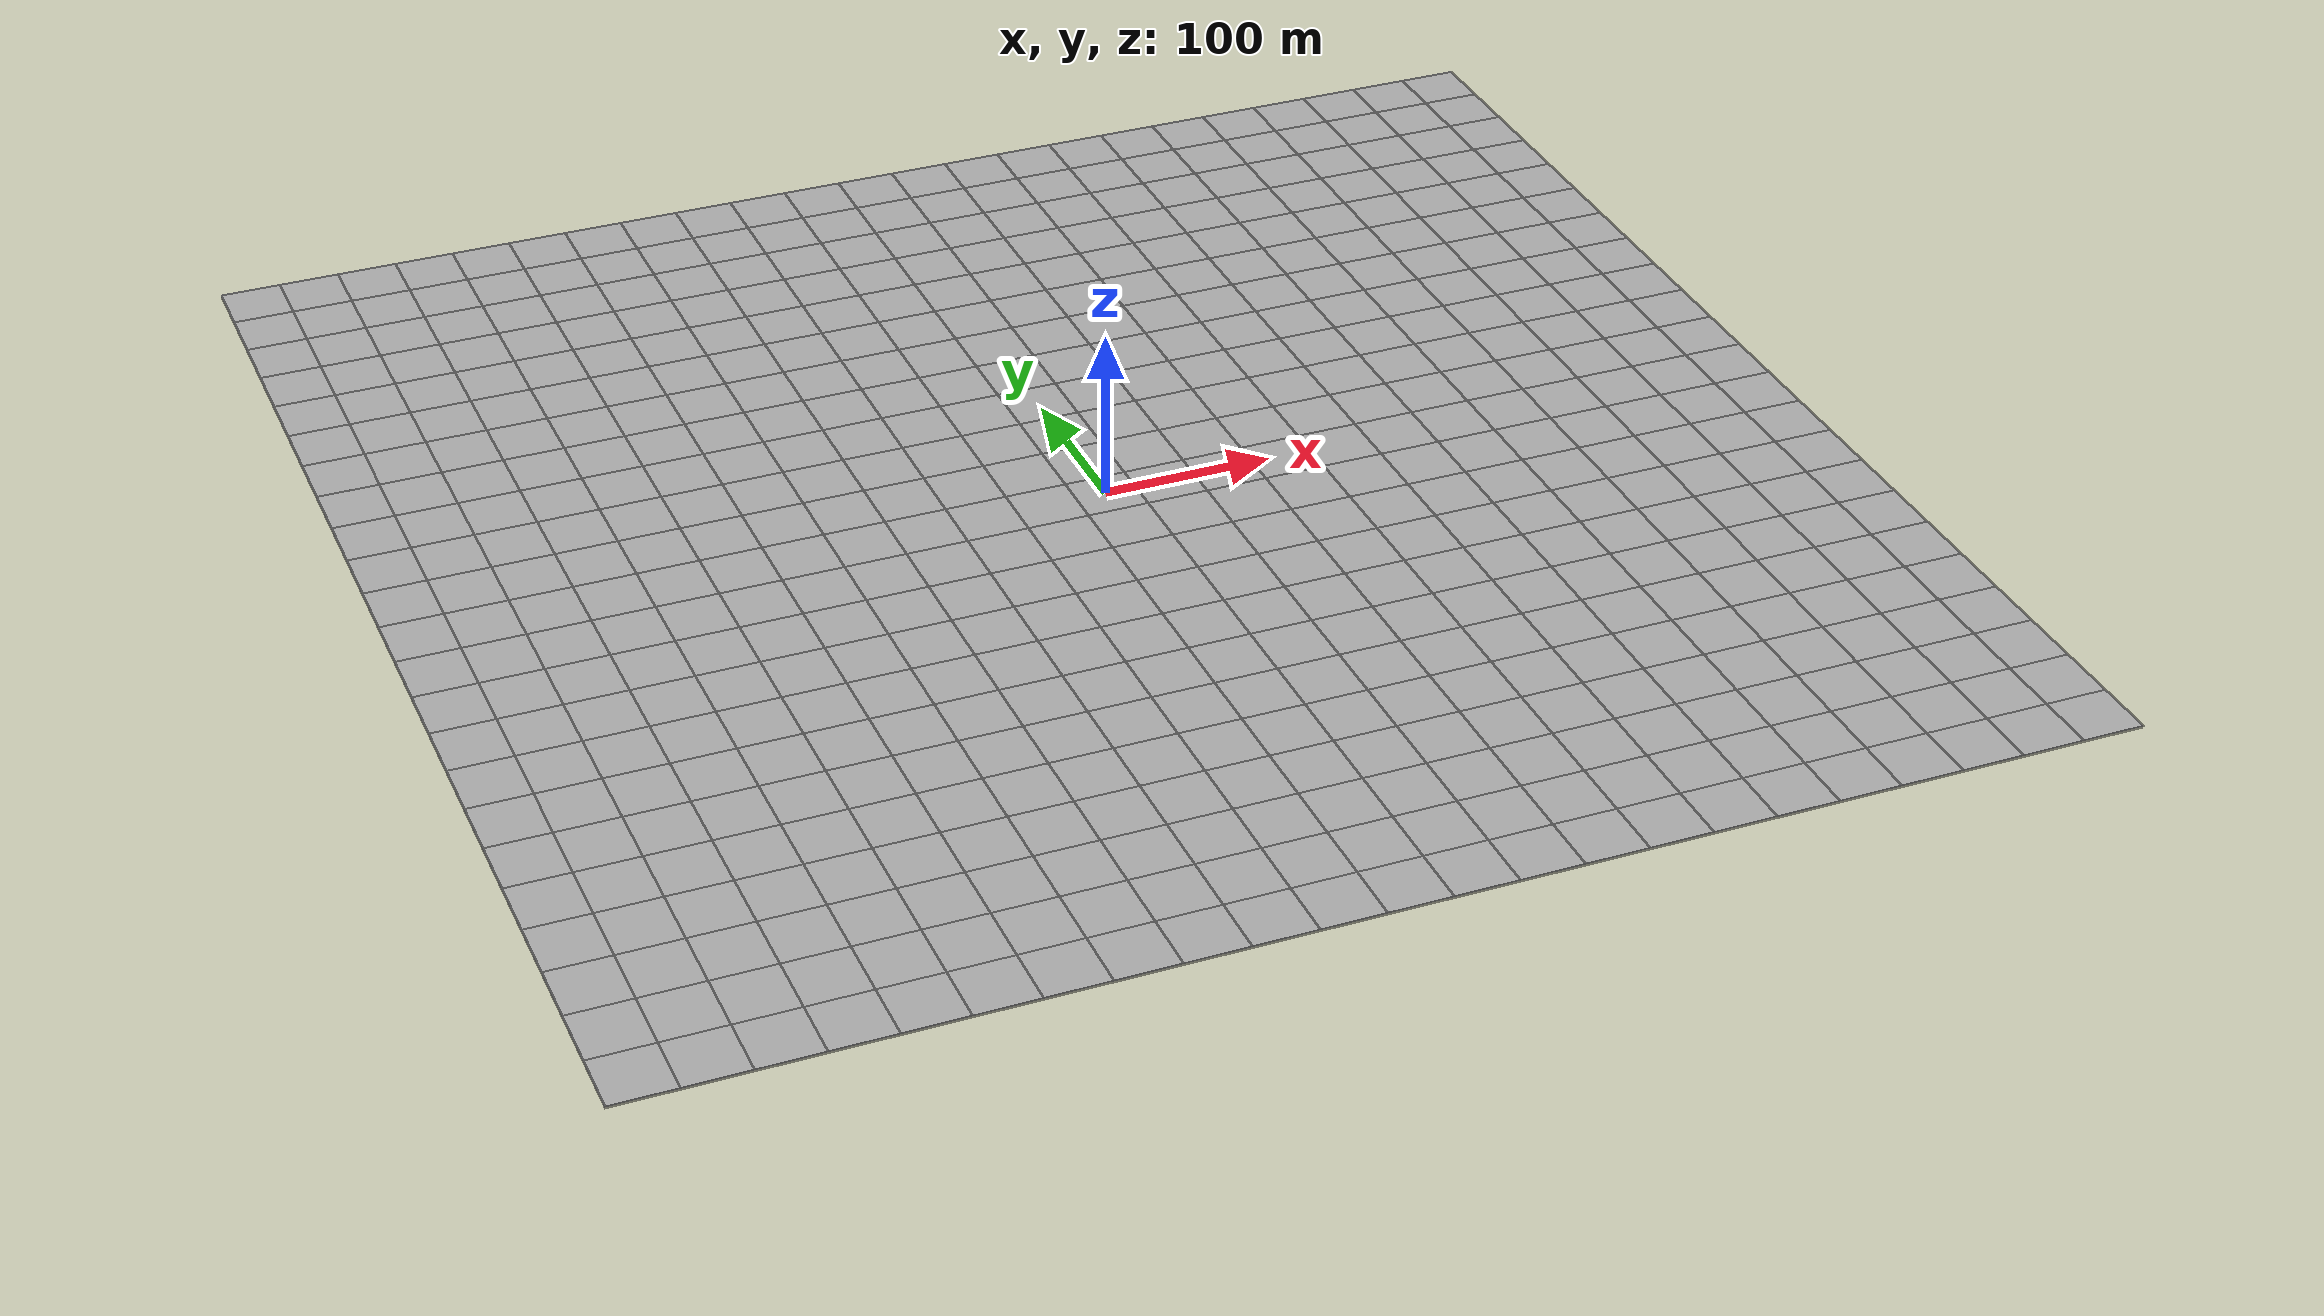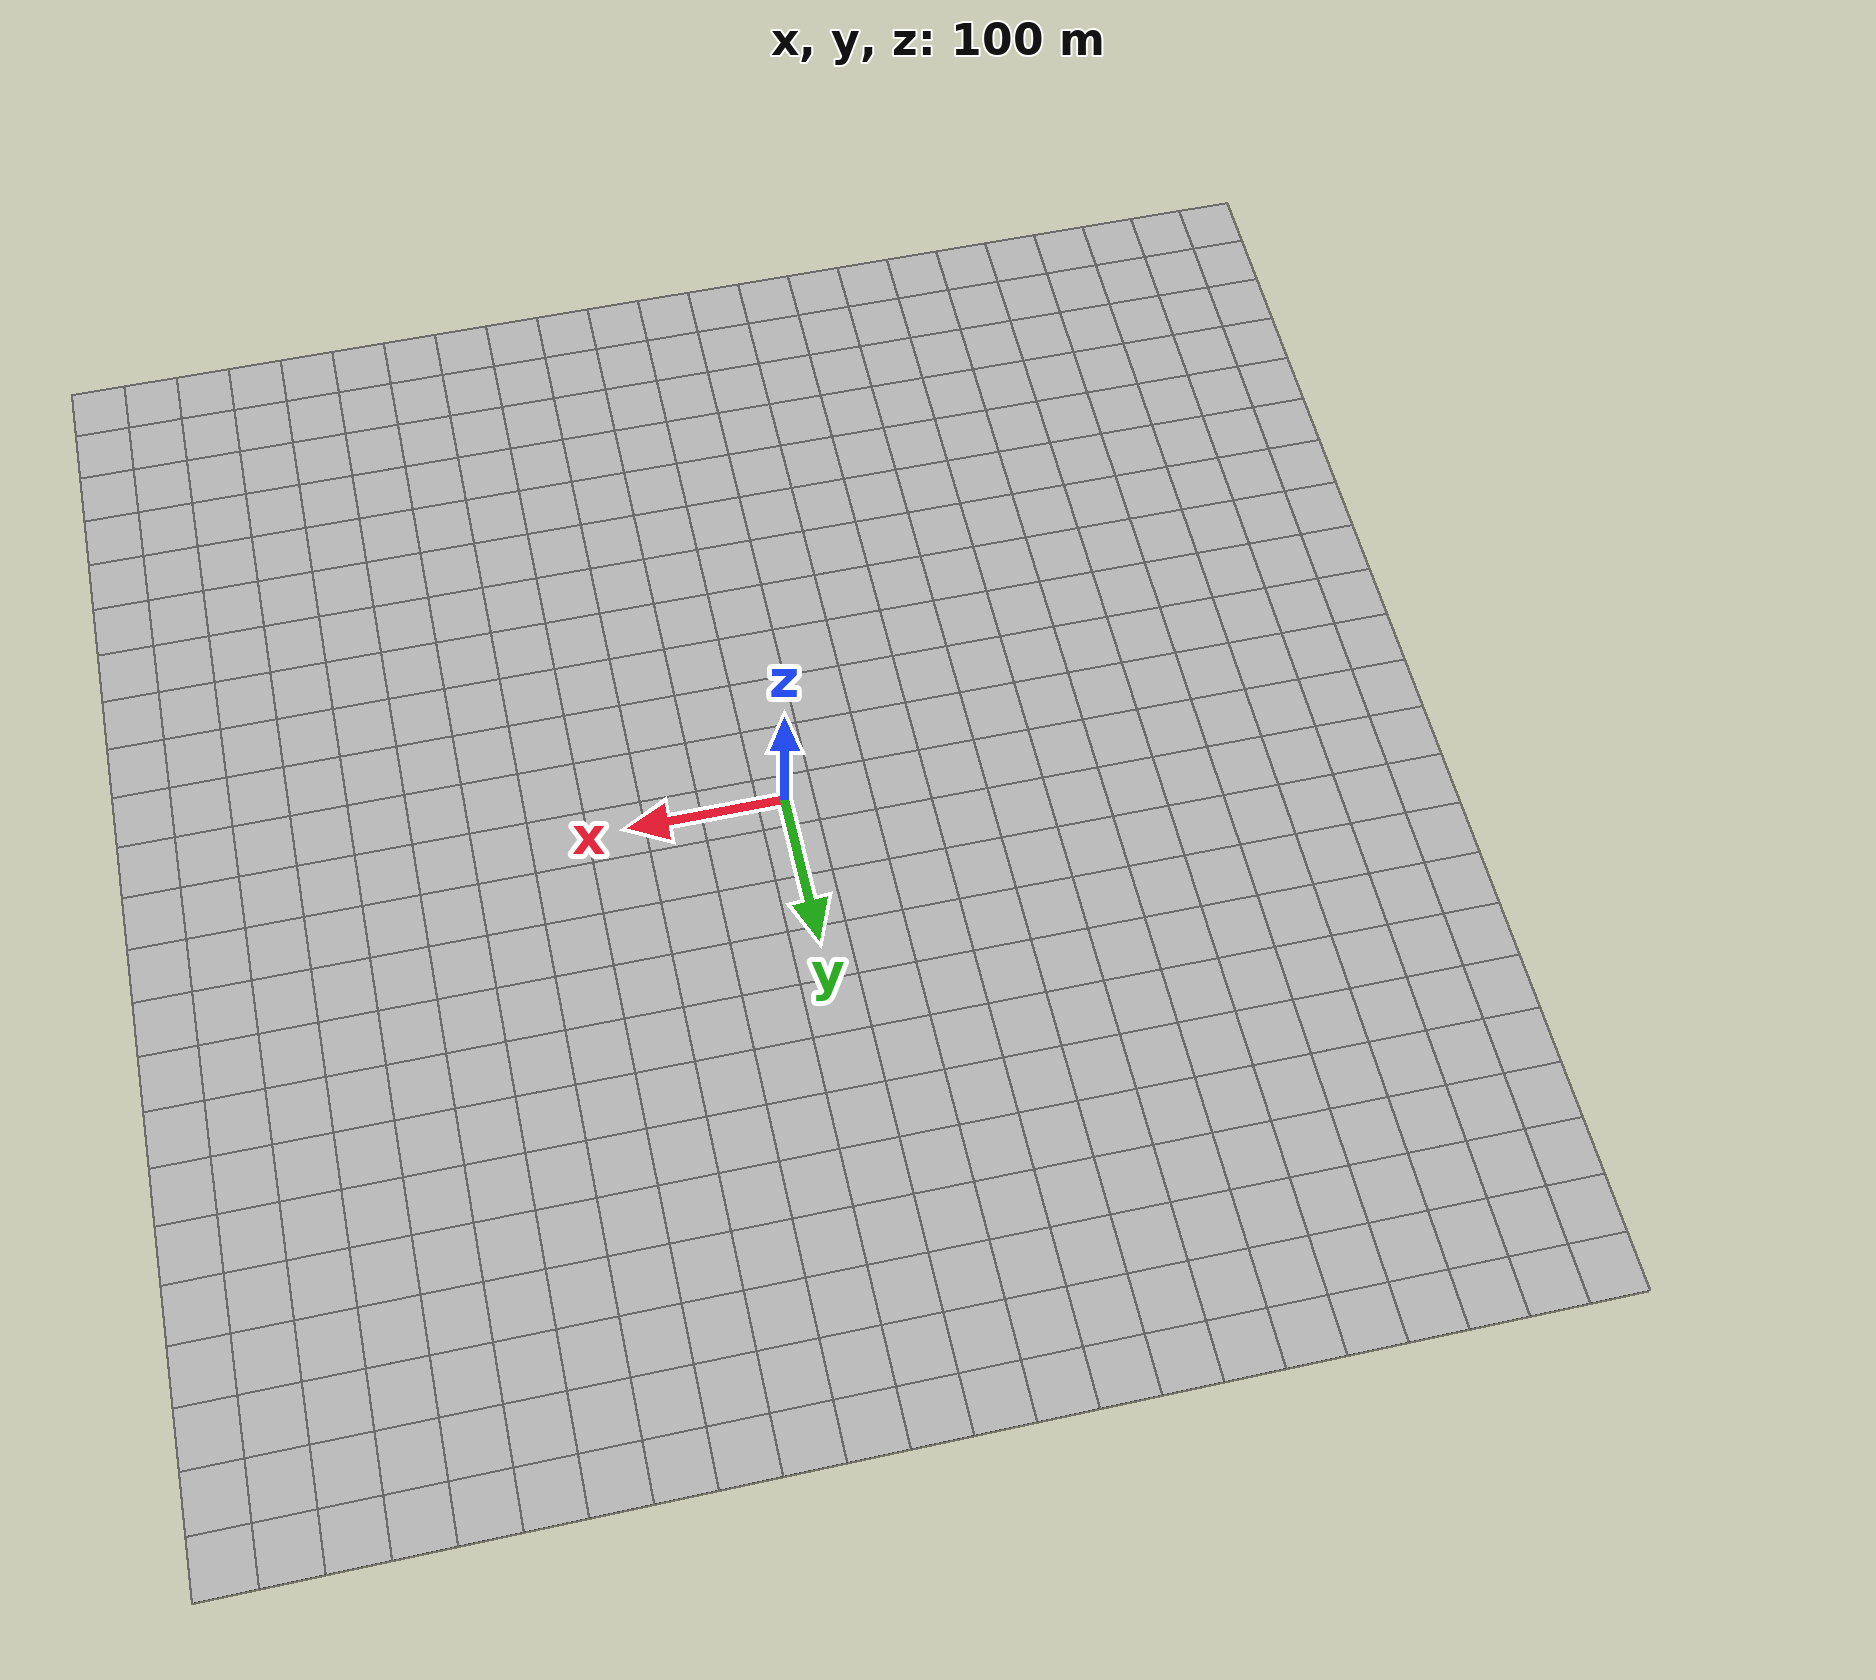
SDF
<sdf version="1.7">
 <world name="default">
  <light name="sun" type="directional">
   <pose>0 0 10 0 -0 0</pose>
   <diffuse>0.8 0.8 0.8 1</diffuse>
   <specular>0.2 0.2 0.2 1</specular>
   <attenuation>
    <range>1000</range>
    <constant>0.9</constant>
    <linear>0.01</linear>
    <quadratic>0.001</quadratic>
   </attenuation>
   <direction>-0.5 0.1 -0.9</direction>
   <spot><inner_angle>0</inner_angle><outer_angle>0</outer_angle><falloff>0</falloff></spot>
  </light>
  <spherical_coordinates>
   <surface_model>EARTH_WGS84</surface_model>
   <latitude_deg>41.3722</latitude_deg>
   <longitude_deg>-72.099</longitude_deg>
   <elevation>1</elevation>
   <heading_deg>0</heading_deg>
  </spherical_coordinates>
  <plugin name="map" filename="libStaticMapPlugin.so">
   <center>41.372171 -72.099040</center>
   <world_size>800</world_size>
   <map_type>satellite</map_type>
   <api_key>AIzaSyBF_PHgd-RjJ-3Es-q-27PkMcYTMp6fjkQ</api_key>
   <use_cache>1</use_cache>
  </plugin>
  <gravity>0 0 -9.8</gravity>
  <magnetic_field>6e-06 2.3e-05 -4.2e-05</magnetic_field>
  <atmosphere type="adiabatic"/>
  <physics type="ode">
   <max_step_size>0.001</max_step_size>
   <real_time_factor>1</real_time_factor>
   <real_time_update_rate>1000</real_time_update_rate>
  </physics>
  <scene><ambient>0.4 0.4 0.4 1</ambient><background>0.7 0.7 0.7 1</background><shadows>1</shadows></scene>
  <spherical_coordinates>
   <surface_model>EARTH_WGS84</surface_model>
   <latitude_deg>0</latitude_deg>
   <longitude_deg>0</longitude_deg>
   <elevation>0</elevation>
   <heading_deg>0</heading_deg>
  </spherical_coordinates>
  <model name="map_satellite_41.372171_-72.09904_800_800">
   <static>1</static>
   <link name="link">
    <collision name="collision">
     <pose>0 0 -0.5 0 -0 0</pose>
     <geometry><box><size>824.562 824.562 1</size></box></geometry>
    </collision>
    <visual name="visual0_0">
     <pose>-394.356 394.356 -0.5 0 -0 1.5708</pose>
     <geometry><box><size>35.8505 35.8505 1</size></box></geometry>
     <material>
      <script>
       <uri>model://map_satellite_41.372171_-72.09904_800_800/materials/scripts</uri>
       <uri>model://map_satellite_41.372171_-72.09904_800_800/materials/textures</uri>
       <name>map_satellite_41.372171_-72.09904_800_800/0_0</name>
      </script>
     </material>
    </visual>
    <visual name="visual0_1">
     <pose>-358.505 394.356 -0.5 0 -0 1.5708</pose>
     <geometry><box><size>35.8505 35.8505 1</size></box></geometry>
     <material>
      <script>
       <uri>model://map_satellite_41.372171_-72.09904_800_800/materials/scripts</uri>
       <uri>model://map_satellite_41.372171_-72.09904_800_800/materials/textures</uri>
       <name>map_satellite_41.372171_-72.09904_800_800/0_1</name>
      </script>
     </material>
    </visual>
    <visual name="visual0_2">
     <pose>-322.655 394.356 -0.5 0 -0 1.5708</pose>
     <geometry><box><size>35.8505 35.8505 1</size></box></geometry>
     <material>
      <script>
       <uri>model://map_satellite_41.372171_-72.09904_800_800/materials/scripts</uri>
       <uri>model://map_satellite_41.372171_-72.09904_800_800/materials/textures</uri>
       <name>map_satellite_41.372171_-72.09904_800_800/0_2</name>
      </script>
     </material>
    </visual>
    <visual name="visual0_3">
     <pose>-286.804 394.356 -0.5 0 -0 1.5708</pose>
     <geometry><box><size>35.8505 35.8505 1</size></box></geometry>
     <material>
      <script>
       <uri>model://map_satellite_41.372171_-72.09904_800_800/materials/scripts</uri>
       <uri>model://map_satellite_41.372171_-72.09904_800_800/materials/textures</uri>
       <name>map_satellite_41.372171_-72.09904_800_800/0_3</name>
      </script>
     </material>
    </visual>
    <visual name="visual0_4">
     <pose>-250.954 394.356 -0.5 0 -0 1.5708</pose>
     <geometry><box><size>35.8505 35.8505 1</size></box></geometry>
     <material>
      <script>
       <uri>model://map_satellite_41.372171_-72.09904_800_800/materials/scripts</uri>
       <uri>model://map_satellite_41.372171_-72.09904_800_800/materials/textures</uri>
       <name>map_satellite_41.372171_-72.09904_800_800/0_4</name>
      </script>
     </material>
    </visual>
    <visual name="visual0_5">
     <pose>-215.103 394.356 -0.5 0 -0 1.5708</pose>
     <geometry><box><size>35.8505 35.8505 1</size></box></geometry>
     <material>
      <script>
       <uri>model://map_satellite_41.372171_-72.09904_800_800/materials/scripts</uri>
       <uri>model://map_satellite_41.372171_-72.09904_800_800/materials/textures</uri>
       <name>map_satellite_41.372171_-72.09904_800_800/0_5</name>
      </script>
     </material>
    </visual>
    <visual name="visual0_6">
     <pose>-179.253 394.356 -0.5 0 -0 1.5708</pose>
     <geometry><box><size>35.8505 35.8505 1</size></box></geometry>
     <material>
      <script>
       <uri>model://map_satellite_41.372171_-72.09904_800_800/materials/scripts</uri>
       <uri>model://map_satellite_41.372171_-72.09904_800_800/materials/textures</uri>
       <name>map_satellite_41.372171_-72.09904_800_800/0_6</name>
      </script>
     </material>
    </visual>
    <visual name="visual0_7">
     <pose>-143.402 394.356 -0.5 0 -0 1.5708</pose>
     <geometry><box><size>35.8505 35.8505 1</size></box></geometry>
     <material>
      <script>
       <uri>model://map_satellite_41.372171_-72.09904_800_800/materials/scripts</uri>
       <uri>model://map_satellite_41.372171_-72.09904_800_800/materials/textures</uri>
       <name>map_satellite_41.372171_-72.09904_800_800/0_7</name>
      </script>
     </material>
    </visual>
    <visual name="visual0_8">
     <pose>-107.552 394.356 -0.5 0 -0 1.5708</pose>
     <geometry><box><size>35.8505 35.8505 1</size></box></geometry>
     <material>
      <script>
       <uri>model://map_satellite_41.372171_-72.09904_800_800/materials/scripts</uri>
       <uri>model://map_satellite_41.372171_-72.09904_800_800/materials/textures</uri>
       <name>map_satellite_41.372171_-72.09904_800_800/0_8</name>
      </script>
     </material>
    </visual>
    <visual name="visual0_9">
     <pose>-71.701 394.356 -0.5 0 -0 1.5708</pose>
     <geometry><box><size>35.8505 35.8505 1</size></box></geometry>
     <material>
      <script>
       <uri>model://map_satellite_41.372171_-72.09904_800_800/materials/scripts</uri>
       <uri>model://map_satellite_41.372171_-72.09904_800_800/materials/textures</uri>
       <name>map_satellite_41.372171_-72.09904_800_800/0_9</name>
      </script>
     </material>
    </visual>
    <visual name="visual0_10">
     <pose>-35.8505 394.356 -0.5 0 -0 1.5708</pose>
     <geometry><box><size>35.8505 35.8505 1</size></box></geometry>
     <material>
      <script>
       <uri>model://map_satellite_41.372171_-72.09904_800_800/materials/scripts</uri>
       <uri>model://map_satellite_41.372171_-72.09904_800_800/materials/textures</uri>
       <name>map_satellite_41.372171_-72.09904_800_800/0_10</name>
      </script>
     </material>
    </visual>
    <visual name="visual0_11">
     <pose>-0 394.356 -0.5 0 -0 1.5708</pose>
     <geometry><box><size>35.8505 35.8505 1</size></box></geometry>
     <material>
      <script>
       <uri>model://map_satellite_41.372171_-72.09904_800_800/materials/scripts</uri>
       <uri>model://map_satellite_41.372171_-72.09904_800_800/materials/textures</uri>
       <name>map_satellite_41.372171_-72.09904_800_800/0_11</name>
      </script>
     </material>
    </visual>
    <visual name="visual0_12">
     <pose>35.8505 394.356 -0.5 0 -0 1.5708</pose>
     <geometry><box><size>35.8505 35.8505 1</size></box></geometry>
     <material>
      <script>
       <uri>model://map_satellite_41.372171_-72.09904_800_800/materials/scripts</uri>
       <uri>model://map_satellite_41.372171_-72.09904_800_800/materials/textures</uri>
       <name>map_satellite_41.372171_-72.09904_800_800/0_12</name>
      </script>
     </material>
    </visual>
    <visual name="visual0_13">
     <pose>71.701 394.356 -0.5 0 -0 1.5708</pose>
     <geometry><box><size>35.8505 35.8505 1</size></box></geometry>
     <material>
      <script>
       <uri>model://map_satellite_41.372171_-72.09904_800_800/materials/scripts</uri>
       <uri>model://map_satellite_41.372171_-72.09904_800_800/materials/textures</uri>
       <name>map_satellite_41.372171_-72.09904_800_800/0_13</name>
      </script>
     </material>
    </visual>
    <visual name="visual0_14">
     <pose>107.552 394.356 -0.5 0 -0 1.5708</pose>
     <geometry><box><size>35.8505 35.8505 1</size></box></geometry>
     <material>
      <script>
       <uri>model://map_satellite_41.372171_-72.09904_800_800/materials/scripts</uri>
       <uri>model://map_satellite_41.372171_-72.09904_800_800/materials/textures</uri>
       <name>map_satellite_41.372171_-72.09904_800_800/0_14</name>
      </script>
     </material>
    </visual>
    <visual name="visual0_15">
     <pose>143.402 394.356 -0.5 0 -0 1.5708</pose>
     <geometry><box><size>35.8505 35.8505 1</size></box></geometry>
     <material>
      <script>
       <uri>model://map_satellite_41.372171_-72.09904_800_800/materials/scripts</uri>
       <uri>model://map_satellite_41.372171_-72.09904_800_800/materials/textures</uri>
       <name>map_satellite_41.372171_-72.09904_800_800/0_15</name>
      </script>
     </material>
    </visual>
    <visual name="visual0_16">
     <pose>179.253 394.356 -0.5 0 -0 1.5708</pose>
     <geometry><box><size>35.8505 35.8505 1</size></box></geometry>
     <material>
      <script>
       <uri>model://map_satellite_41.372171_-72.09904_800_800/materials/scripts</uri>
       <uri>model://map_satellite_41.372171_-72.09904_800_800/materials/textures</uri>
       <name>map_satellite_41.372171_-72.09904_800_800/0_16</name>
      </script>
     </material>
    </visual>
    <visual name="visual0_17">
     <pose>215.103 394.356 -0.5 0 -0 1.5708</pose>
     <geometry><box><size>35.8505 35.8505 1</size></box></geometry>
     <material>
      <script>
       <uri>model://map_satellite_41.372171_-72.09904_800_800/materials/scripts</uri>
       <uri>model://map_satellite_41.372171_-72.09904_800_800/materials/textures</uri>
       <name>map_satellite_41.372171_-72.09904_800_800/0_17</name>
      </script>
     </material>
    </visual>
    <visual name="visual0_18">
     <pose>250.954 394.356 -0.5 0 -0 1.5708</pose>
     <geometry><box><size>35.8505 35.8505 1</size></box></geometry>
     <material>
      <script>
       <uri>model://map_satellite_41.372171_-72.09904_800_800/materials/scripts</uri>
       <uri>model://map_satellite_41.372171_-72.09904_800_800/materials/textures</uri>
       <name>map_satellite_41.372171_-72.09904_800_800/0_18</name>
      </script>
     </material>
    </visual>
    <visual name="visual0_19">
     <pose>286.804 394.356 -0.5 0 -0 1.5708</pose>
     <geometry><box><size>35.8505 35.8505 1</size></box></geometry>
     <material>
      <script>
       <uri>model://map_satellite_41.372171_-72.09904_800_800/materials/scripts</uri>
       <uri>model://map_satellite_41.372171_-72.09904_800_800/materials/textures</uri>
       <name>map_satellite_41.372171_-72.09904_800_800/0_19</name>
      </script>
     </material>
    </visual>
    <visual name="visual0_20">
     <pose>322.655 394.356 -0.5 0 -0 1.5708</pose>
     <geometry><box><size>35.8505 35.8505 1</size></box></geometry>
     <material>
      <script>
       <uri>model://map_satellite_41.372171_-72.09904_800_800/materials/scripts</uri>
       <uri>model://map_satellite_41.372171_-72.09904_800_800/materials/textures</uri>
       <name>map_satellite_41.372171_-72.09904_800_800/0_20</name>
      </script>
     </material>
    </visual>
    <visual name="visual0_21">
     <pose>358.505 394.356 -0.5 0 -0 1.5708</pose>
     <geometry><box><size>35.8505 35.8505 1</size></box></geometry>
     <material>
      <script>
       <uri>model://map_satellite_41.372171_-72.09904_800_800/materials/scripts</uri>
       <uri>model://map_satellite_41.372171_-72.09904_800_800/materials/textures</uri>
       <name>map_satellite_41.372171_-72.09904_800_800/0_21</name>
      </script>
     </material>
    </visual>
    <visual name="visual0_22">
     <pose>394.356 394.356 -0.5 0 -0 1.5708</pose>
     <geometry><box><size>35.8505 35.8505 1</size></box></geometry>
     <material>
      <script>
       <uri>model://map_satellite_41.372171_-72.09904_800_800/materials/scripts</uri>
       <uri>model://map_satellite_41.372171_-72.09904_800_800/materials/textures</uri>
       <name>map_satellite_41.372171_-72.09904_800_800/0_22</name>
      </script>
     </material>
    </visual>
    <visual name="visual1_0">
     <pose>-394.356 358.505 -0.5 0 -0 1.5708</pose>
     <geometry><box><size>35.8505 35.8505 1</size></box></geometry>
     <material>
      <script>
       <uri>model://map_satellite_41.372171_-72.09904_800_800/materials/scripts</uri>
       <uri>model://map_satellite_41.372171_-72.09904_800_800/materials/textures</uri>
       <name>map_satellite_41.372171_-72.09904_800_800/1_0</name>
      </script>
     </material>
    </visual>
    <visual name="visual1_1">
     <pose>-358.505 358.505 -0.5 0 -0 1.5708</pose>
     <geometry><box><size>35.8505 35.8505 1</size></box></geometry>
     <material>
      <script>
       <uri>model://map_satellite_41.372171_-72.09904_800_800/materials/scripts</uri>
       <uri>model://map_satellite_41.372171_-72.09904_800_800/materials/textures</uri>
       <name>map_satellite_41.372171_-72.09904_800_800/1_1</name>
      </script>
     </material>
    </visual>
    <visual name="visual1_2">
     <pose>-322.655 358.505 -0.5 0 -0 1.5708</pose>
     <geometry><box><size>35.8505 35.8505 1</size></box></geometry>
     <material>
      <script>
       <uri>model://map_satellite_41.372171_-72.09904_800_800/materials/scripts</uri>
       <uri>model://map_satellite_41.372171_-72.09904_800_800/materials/textures</uri>
       <name>map_satellite_41.372171_-72.09904_800_800/1_2</name>
      </script>
     </material>
    </visual>
    <visual name="visual1_3">
     <pose>-286.804 358.505 -0.5 0 -0 1.5708</pose>
     <geometry><box><size>35.8505 35.8505 1</size></box></geometry>
     <material>
      <script>
       <uri>model://map_satellite_41.372171_-72.09904_800_800/materials/scripts</uri>
       <uri>model://map_satellite_41.372171_-72.09904_800_800/materials/textures</uri>
       <name>map_satellite_41.372171_-72.09904_800_800/1_3</name>
      </script>
     </material>
    </visual>
    <visual name="visual1_4">
     <pose>-250.954 358.505 -0.5 0 -0 1.5708</pose>
     <geometry><box><size>35.8505 35.8505 1</size></box></geometry>
     <material>
      <script>
       <uri>model://map_satellite_41.372171_-72.09904_800_800/materials/scripts</uri>
       <uri>model://map_satellite_41.372171_-72.09904_800_800/materials/textures</uri>
       <name>map_satellite_41.372171_-72.09904_800_800/1_4</name>
      </script>
     </material>
    </visual>
    <visual name="visual1_5">
     <pose>-215.103 358.505 -0.5 0 -0 1.5708</pose>
     <geometry><box><size>35.8505 35.8505 1</size></box></geometry>
     <material>
      <script>
       <uri>model://map_satellite_41.372171_-72.09904_800_800/materials/scripts</uri>
       <uri>model://map_satellite_41.372171_-72.09904_800_800/materials/textures</uri>
       <name>map_satellite_41.372171_-72.09904_800_800/1_5</name>
      </script>
     </material>
    </visual>
    <visual name="visual1_6">
     <pose>-179.253 358.505 -0.5 0 -0 1.5708</pose>
     <geometry><box><size>35.8505 35.8505 1</size></box></geometry>
     <material>
      <script>
       <uri>model://map_satellite_41.372171_-72.09904_800_800/materials/scripts</uri>
       <uri>model://map_satellite_41.372171_-72.09904_800_800/materials/textures</uri>
       <name>map_satellite_41.372171_-72.09904_800_800/1_6</name>
      </script>
     </material>
    </visual>
    <visual name="visual1_7">
     <pose>-143.402 358.505 -0.5 0 -0 1.5708</pose>
     <geometry><box><size>35.8505 35.8505 1</size></box></geometry>
     <material>
      <script>
       <uri>model://map_satellite_41.372171_-72.09904_800_800/materials/scripts</uri>
       <uri>model://map_satellite_41.372171_-72.09904_800_800/materials/textures</uri>
       <name>map_satellite_41.372171_-72.09904_800_800/1_7</name>
      </script>
     </material>
    </visual>
    <visual name="visual1_8">
     <pose>-107.552 358.505 -0.5 0 -0 1.5708</pose>
     <geometry><box><size>35.8505 35.8505 1</size></box></geometry>
     <material>
      <script>
       <uri>model://map_satellite_41.372171_-72.09904_800_800/materials/scripts</uri>
       <uri>model://map_satellite_41.372171_-72.09904_800_800/materials/textures</uri>
       <name>map_satellite_41.372171_-72.09904_800_800/1_8</name>
      </script>
     </material>
    </visual>
    <visual name="visual1_9">
     <pose>-71.701 358.505 -0.5 0 -0 1.5708</pose>
     <geometry><box><size>35.8505 35.8505 1</size></box></geometry>
     <material>
      <script>
       <uri>model://map_satellite_41.372171_-72.09904_800_800/materials/scripts</uri>
       <uri>model://map_satellite_41.372171_-72.09904_800_800/materials/textures</uri>
       <name>map_satellite_41.372171_-72.09904_800_800/1_9</name>
      </script>
     </material>
    </visual>
    <visual name="visual1_10">
     <pose>-35.8505 358.505 -0.5 0 -0 1.5708</pose>
     <geometry><box><size>35.8505 35.8505 1</size></box></geometry>
     <material>
      <script>
       <uri>model://map_satellite_41.372171_-72.09904_800_800/materials/scripts</uri>
       <uri>model://map_satellite_41.372171_-72.09904_800_800/materials/textures</uri>
       <name>map_satellite_41.372171_-72.09904_800_800/1_10</name>
      </script>
     </material>
    </visual>
    <visual name="visual1_11">
     <pose>-0 358.505 -0.5 0 -0 1.5708</pose>
     <geometry><box><size>35.8505 35.8505 1</size></box></geometry>
     <material>
      <script>
       <uri>model://map_satellite_41.372171_-72.09904_800_800/materials/scripts</uri>
       <uri>model://map_satellite_41.372171_-72.09904_800_800/materials/textures</uri>
       <name>map_satellite_41.372171_-72.09904_800_800/1_11</name>
      </script>
     </material>
    </visual>
    <visual name="visual1_12">
     <pose>35.8505 358.505 -0.5 0 -0 1.5708</pose>
     <geometry><box><size>35.8505 35.8505 1</size></box></geometry>
     <material>
      <script>
       <uri>model://map_satellite_41.372171_-72.09904_800_800/materials/scripts</uri>
       <uri>model://map_satellite_41.372171_-72.09904_800_800/materials/textures</uri>
       <name>map_satellite_41.372171_-72.09904_800_800/1_12</name>
      </script>
     </material>
    </visual>
    <visual name="visual1_13">
     <pose>71.701 358.505 -0.5 0 -0 1.5708</pose>
     <geometry><box><size>35.8505 35.8505 1</size></box></geometry>
     <material>
      <script>
       <uri>model://map_satellite_41.372171_-72.09904_800_800/materials/scripts</uri>
       <uri>model://map_satellite_41.372171_-72.09904_800_800/materials/textures</uri>
       <name>map_satellite_41.372171_-72.09904_800_800/1_13</name>
      </script>
     </material>
    </visual>
    <visual name="visual1_14">
     <pose>107.552 358.505 -0.5 0 -0 1.5708</pose>
     <geometry><box><size>35.8505 35.8505 1</size></box></geometry>
     <material>
      <script>
       <uri>model://map_satellite_41.372171_-72.09904_800_800/materials/scripts</uri>
       <uri>model://map_satellite_41.372171_-72.09904_800_800/materials/textures</uri>
       <name>map_satellite_41.372171_-72.09904_800_800/1_14</name>
      </script>
     </material>
    </visual>
    <visual name="visual1_15">
     <pose>143.402 358.505 -0.5 0 -0 1.5708</pose>
     <geometry><box><size>35.8505 35.8505 1</size></box></geometry>
     <material>
      <script>
       <uri>model://map_satellite_41.372171_-72.09904_800_800/materials/scripts</uri>
       <uri>model://map_satellite_41.372171_-72.09904_800_800/materials/textures</uri>
       <name>map_satellite_41.372171_-72.09904_800_800/1_15</name>
      </script>
     </material>
    </visual>
    <visual name="visual1_16">
     <pose>179.253 358.505 -0.5 0 -0 1.5708</pose>
     <geometry><box><size>35.8505 35.8505 1</size></box></geometry>
     <material>
      <script>
       <uri>model://map_satellite_41.372171_-72.09904_800_800/materials/scripts</uri>
       <uri>model://map_satellite_41.372171_-72.09904_800_800/materials/textures</uri>
       <name>map_satellite_41.372171_-72.09904_800_800/1_16</name>
      </script>
     </material>
    </visual>
    <visual name="visual1_17">
     <pose>215.103 358.505 -0.5 0 -0 1.5708</pose>
     <geometry><box><size>35.8505 35.8505 1</size></box></geometry>
     <material>
      <script>
       <uri>model://map_satellite_41.372171_-72.09904_800_800/materials/scripts</uri>
       <uri>model://map_satellite_41.372171_-72.09904_800_800/materials/textures</uri>
       <name>map_satellite_41.372171_-72.09904_800_800/1_17</name>
      </script>
     </material>
    </visual>
    <visual name="visual1_18">
     <pose>250.954 358.505 -0.5 0 -0 1.5708</pose>
     <geometry><box><size>35.8505 35.8505 1</size></box></geometry>
     <material>
      <script>
       <uri>model://map_satellite_41.372171_-72.09904_800_800/materials/scripts</uri>
       <uri>model://map_satellite_41.372171_-72.09904_800_800/materials/textures</uri>
       <name>map_satellite_41.372171_-72.09904_800_800/1_18</name>
      </script>
     </material>
    </visual>
    <visual name="visual1_19">
     <pose>286.804 358.505 -0.5 0 -0 1.5708</pose>
     <geometry><box><size>35.8505 35.8505 1</size></box></geometry>
     <material>
      <script>
       <uri>model://map_satellite_41.372171_-72.09904_800_800/materials/scripts</uri>
       <uri>model://map_satellite_41.372171_-72.09904_800_800/materials/textures</uri>
       <name>map_satellite_41.372171_-72.09904_800_800/1_19</name>
      </script>
     </material>
    </visual>
    <visual name="visual1_20">
     <pose>322.655 358.505 -0.5 0 -0 1.5708</pose>
     <geometry><box><size>35.8505 35.8505 1</size></box></geometry>
     <material>
      <script>
       <uri>model://map_satellite_41.372171_-72.09904_800_800/materials/scripts</uri>
       <uri>model://map_satellite_41.372171_-72.09904_800_800/materials/textures</uri>
       <name>map_satellite_41.372171_-72.09904_800_800/1_20</name>
      </script>
     </material>
    </visual>
    <visual name="visual1_21">
     <pose>358.505 358.505 -0.5 0 -0 1.5708</pose>
     <geometry><box><size>35.8505 35.8505 1</size></box></geometry>
     <material>
      <script>
       <uri>model://map_satellite_41.372171_-72.09904_800_800/materials/scripts</uri>
       <uri>model://map_satellite_41.372171_-72.09904_800_800/materials/textures</uri>
       <name>map_satellite_41.372171_-72.09904_800_800/1_21</name>
      </script>
     </material>
    </visual>
    <visual name="visual1_22">
     <pose>394.356 358.505 -0.5 0 -0 1.5708</pose>
     <geometry><box><size>35.8505 35.8505 1</size></box></geometry>
     <material>
      <script>
       <uri>model://map_satellite_41.372171_-72.09904_800_800/materials/scripts</uri>
       <uri>model://map_satellite_41.372171_-72.09904_800_800/materials/textures</uri>
       <name>map_satellite_41.372171_-72.09904_800_800/1_22</name>
      </script>
     </material>
    </visual>
    <visual name="visual2_0">
     <pose>-394.356 322.655 -0.5 0 -0 1.5708</pose>
     <geometry><box><size>35.8505 35.8505 1</size></box></geometry>
     <material>
      <script>
       <uri>model://map_satellite_41.372171_-72.09904_800_800/materials/scripts</uri>
       <uri>model://map_satellite_41.372171_-72.09904_800_800/materials/textures</uri>
       <name>map_satellite_41.372171_-72.09904_800_800/2_0</name>
      </script>
     </material>
    </visual>
    <visual name="visual2_1">
     <pose>-358.505 322.655 -0.5 0 -0 1.5708</pose>
     <geometry><box><size>35.8505 35.8505 1</size></box></geometry>
     <material>
      <script>
       <uri>model://map_satellite_41.372171_-72.09904_800_800/materials/scripts</uri>
       <uri>model://map_satellite_41.372171_-72.09904_800_800/materials/textures</uri>
       <name>map_satellite_41.372171_-72.09904_800_800/2_1</name>
      </script>
     </material>
    </visual>
    <visual name="visual2_2">
     <pose>-322.655 322.655 -0.5 0 -0 1.5708</pose>
     <geometry><box><size>35.8505 35.8505 1</size></box></geometry>
     <material>
      <script>
       <uri>model://map_satellite_41.372171_-72.09904_800_800/materials/scripts</uri>
       <uri>model://map_satellite_41.372171_-72.09904_800_800/materials/textures</uri>
       <name>map_satellite_41.372171_-72.09904_800_800/2_2</name>
      </script>
     </material>
    </visual>
    <visual name="visual2_3">
     <pose>-286.804 322.655 -0.5 0 -0 1.5708</pose>
     <geometry><box><size>35.8505 35.8505 1</size></box></geometry>
     <material>
      <script>
       <uri>model://map_satellite_41.372171_-72.09904_800_800/materials/scripts</uri>
       <uri>model://map_satellite_41.372171_-72.09904_800_800/materials/textures</uri>
       <name>map_satellite_41.372171_-72.09904_800_800/2_3</name>
      </script>
     </material>
    </visual>
    <visual name="visual2_4">
     <pose>-250.954 322.655 -0.5 0 -0 1.5708</pose>
     <geometry><box><size>35.8505 35.8505 1</size></box></geometry>
     <material>
      <script>
       <uri>model://map_satellite_41.372171_-72.09904_800_800/materials/scripts</uri>
       <uri>model://map_satellite_41.372171_-72.09904_800_800/materials/textures</uri>
       <name>map_satellite_41.372171_-72.09904_800_800/2_4</name>
      </script>
     </material>
    </visual>
    <visual name="visual2_5">
     <pose>-215.103 322.655 -0.5 0 -0 1.5708</pose>
     <geometry><box><size>35.8505 35.8505 1</size></box></geometry>
     <material>
      <script>
       <uri>model://map_satellite_41.372171_-72.09904_800_800/materials/scripts</uri>
       <uri>model://map_satellite_41.372171_-72.09904_800_800/materials/textures</uri>
       <name>map_satellite_41.372171_-72.09904_800_800/2_5</name>
      </script>
     </material>
    </visual>
    <visual name="visual2_6">
     <pose>-179.253 322.655 -0.5 0 -0 1.5708</pose>
     <geometry><box><size>35.8505 35.8505 1</size></box></geometry>
     <material>
      <script>
       <uri>model://map_satellite_41.372171_-72.09904_800_800/materials/scripts</uri>
       <uri>model://map_satellite_41.372171_-72.09904_800_800/materials/textures</uri>
       <name>map_satellite_41.372171_-72.09904_800_800/2_6</name>
      </script>
     </material>
    </visual>
    <visual name="visual2_7">
     <pose>-143.402 322.655 -0.5 0 -0 1.5708</pose>
     <geometry><box><size>35.8505 35.8505 1</size></box></geometry>
     <material>
      <script>
       <uri>model://map_satellite_41.372171_-72.09904_800_800/materials/scripts</uri>
       <uri>model://map_satellite_41.372171_-72.09904_800_800/materials/textures</uri>
       <name>map_satellite_41.372171_-72.09904_800_800/2_7</name>
      </script>
     </material>
    </visual>
    <visual name="visual2_8">
     <pose>-107.552 322.655 -0.5 0 -0 1.5708</pose>
     <geometry><box><size>35.8505 35.8505 1</size></box></geometry>
     <material>
      <script>
       <uri>model://map_satellite_41.372171_-72.09904_800_800/materials/scripts</uri>
       <uri>model://map_satellite_41.372171_-72.09904_800_800/materials/textures</uri>
       <name>map_satellite_41.372171_-72.09904_800_800/2_8</name>
      </script>
     </material>
    </visual>
    <visual name="visual2_9">
     <pose>-71.701 322.655 -0.5 0 -0 1.5708</pose>
     <geometry><box><size>35.8505 35.8505 1</size></box></geometry>
     <material>
      <script>
       <uri>model://map_satellite_41.372171_-72.09904_800_800/materials/scripts</uri>
       <uri>model://map_satellite_41.372171_-72.09904_800_800/materials/textures</uri>
       <name>map_satellite_41.372171_-72.09904_800_800/2_9</name>
      </script>
     </material>
    </visual>
    <visual name="visual2_10">
     <pose>-35.8505 322.655 -0.5 0 -0 1.5708</pose>
     <geometry><box><size>35.8505 35.8505 1</size></box></geometry>
     <material>
      <script>
       <uri>model://map_satellite_41.372171_-72.09904_800_800/materials/scripts</uri>
       <uri>model://map_satellite_41.372171_-72.09904_800_800/materials/textures</uri>
       <name>map_satellite_41.372171_-72.09904_800_800/2_10</name>
      </script>
     </material>
    </visual>
    <visual name="visual2_11">
     <pose>-0 322.655 -0.5 0 -0 1.5708</pose>
     <geometry><box><size>35.8505 35.8505 1</size></box></geometry>
     <material>
      <script>
       <uri>model://map_satellite_41.372171_-72.09904_800_800/materials/scripts</uri>
       <uri>model://map_satellite_41.372171_-72.09904_800_800/materials/textures</uri>
       <name>map_satellite_41.372171_-72.09904_800_800/2_11</name>
      </script>
     </material>
    </visual>
    <visual name="visual2_12">
     <pose>35.8505 322.655 -0.5 0 -0 1.5708</pose>
     <geometry><box><size>35.8505 35.8505 1</size></box></geometry>
     <material>
      <script>
       <uri>model://map_satellite_41.372171_-72.09904_800_800/materials/scripts</uri>
       <uri>model://map_satellite_41.372171_-72.09904_800_800/materials/textures</uri>
       <name>map_satellite_41.372171_-72.09904_800_800/2_12</name>
      </script>
     </material>
    </visual>
    <visual name="visual2_13">
     <pose>71.701 322.655 -0.5 0 -0 1.5708</pose>
     <geometry><box><size>35.8505 35.8505 1</size></box></geometry>
     <material>
      <script>
       <uri>model://map_satellite_41.372171_-72.09904_800_800/materials/scripts</uri>
       <uri>model://map_satellite_41.372171_-72.09904_800_800/materials/textures</uri>
       <name>map_satellite_41.372171_-72.09904_800_800/2_13</name>
      </script>
     </material>
    </visual>
    <visual name="visual2_14">
     <pose>107.552 322.655 -0.5 0 -0 1.5708</pose>
     <geometry><box><size>35.8505 35.8505 1</size></box></geometry>
     <material>
      <script>
       <uri>model://map_satellite_41.372171_-72.09904_800_800/materials/scripts</uri>
       <uri>model://map_satellite_41.372171_-72.09904_800_800/materials/textures</uri>
       <name>map_satellite_41.372171_-72.09904_800_800/2_14</name>
      </script>
     </material>
    </visual>
    <visual name="visual2_15">
     <pose>143.402 322.655 -0.5 0 -0 1.5708</pose>
     <geometry><box><size>35.8505 35.8505 1</size></box></geometry>
     <material>
      <script>
       <uri>model://map_satellite_41.372171_-72.09904_800_800/materials/scripts</uri>
       <uri>model://map_satellite_41.372171_-72.09904_800_800/materials/textures</uri>
       <name>map_satellite_41.372171_-72.09904_800_800/2_15</name>
      </script>
     </material>
    </visual>
    <visual name="visual2_16">
     <pose>179.253 322.655 -0.5 0 -0 1.5708</pose>
     <geometry><box><size>35.8505 35.8505 1</size></box></geometry>
     <material>
      <script>
       <uri>model://map_satellite_41.372171_-72.09904_800_800/materials/scripts</uri>
       <uri>model://map_satellite_41.372171_-72.09904_800_800/materials/textures</uri>
       <name>map_satellite_41.372171_-72.09904_800_800/2_16</name>
      </script>
     </material>
    </visual>
    <visual name="visual2_17">
     <pose>215.103 322.655 -0.5 0 -0 1.5708</pose>
     <geometry><box><size>35.8505 35.8505 1</size></box></geometry>
     <material>
      <script>
       <uri>model://map_satellite_41.372171_-72.09904_800_800/materials/scripts</uri>
       <uri>model://map_satellite_41.372171_-72.09904_800_800/materials/textures</uri>
       <name>map_satellite_41.372171_-72.09904_800_800/2_17</name>
      </script>
     </material>
    </visual>
    <visual name="visual2_18">
     <pose>250.954 322.655 -0.5 0 -0 1.5708</pose>
     <geometry><box><size>35.8505 35.8505 1</size></box></geometry>
     <material>
      <script>
       <uri>model://map_satellite_41.372171_-72.09904_800_800/materials/scripts</uri>
       <uri>model://map_satellite_41.372171_-72.09904_800_800/materials/textures</uri>
       <name>map_satellite_41.372171_-72.09904_800_800/2_18</name>
      </script>
     </material>
    </visual>
    <visual name="visual2_19">
     <pose>286.804 322.655 -0.5 0 -0 1.5708</pose>
     <geometry><box><size>35.8505 35.8505 1</size></box></geometry>
     <material>
      <script>
       <uri>model://map_satellite_41.372171_-72.09904_800_800/materials/scripts</uri>
       <uri>model://map_satellite_41.372171_-72.09904_800_800/materials/textures</uri>
       <name>map_satellite_41.372171_-72.09904_800_800/2_19</name>
      </script>
     </material>
    </visual>
    <visual name="visual2_20">
     <pose>322.655 322.655 -0.5 0 -0 1.5708</pose>
     <geometry><box><size>35.8505 35.8505 1</size></box></geometry>
     <material>
      <script>
       <uri>model://map_satellite_41.372171_-72.09904_800_800/materials/scripts</uri>
       <uri>model://map_satellite_41.372171_-72.09904_800_800/materials/textures</uri>
       <name>map_satellite_41.372171_-72.09904_800_800/2_20</name>
      </script>
     </material>
    </visual>
    <visual name="visual2_21">
     <pose>358.505 322.655 -0.5 0 -0 1.5708</pose>
     <geometry><box><size>35.8505 35.8505 1</size></box></geometry>
     <material>
      <script>
       <uri>model://map_satellite_41.372171_-72.09904_800_800/materials/scripts</uri>
       <uri>model://map_satellite_41.372171_-72.09904_800_800/materials/textures</uri>
       <name>map_satellite_41.372171_-72.09904_800_800/2_21</name>
      </script>
     </material>
    </visual>
    <visual name="visual2_22">
     <pose>394.356 322.655 -0.5 0 -0 1.5708</pose>
     <geometry><box><size>35.8505 35.8505 1</size></box></geometry>
     <material>
      <script>
       <uri>model://map_satellite_41.372171_-72.09904_800_800/materials/scripts</uri>
       <uri>model://map_satellite_41.372171_-72.09904_800_800/materials/textures</uri>
       <name>map_satellite_41.372171_-72.09904_800_800/2_22</name>
      </script>
     </material>
    </visual>
    <visual name="visual3_0">
     <pose>-394.356 286.804 -0.5 0 -0 1.5708</pose>
     <geometry><box><size>35.8505 35.8505 1</size></box></geometry>
     <material>
      <script>
       <uri>model://map_satellite_41.372171_-72.09904_800_800/materials/scripts</uri>
       <uri>model://map_satellite_41.372171_-72.09904_800_800/materials/textures</uri>
       <name>map_satellite_41.372171_-72.09904_800_800/3_0</name>
      </script>
     </material>
    </visual>
    <visual name="visual3_1">
     <pose>-358.505 286.804 -0.5 0 -0 1.5708</pose>
     <geometry><box><size>35.8505 35.8505 1</size></box></geometry>
     <material>
      <script>
       <uri>model://map_satellite_41.372171_-72.09904_800_800/materials/scripts</uri>
       <uri>model://map_satellite_41.372171_-72.09904_800_800/materials/textures</uri>
       <name>map_satellite_41.372171_-72.09904_800_800/3_1</name>
      </script>
     </material>
    </visual>
    <visual name="visual3_2">
     <pose>-322.655 286.804 -0.5 0 -0 1.5708</pose>
     <geometry><box><size>35.8505 35.8505 1</size></box></geometry>
     <material>
      <script>
       <uri>model://map_satellite_41.372171_-72.09904_800_800/materials/scripts</uri>
       <uri>model://map_satellite_41.372171_-72.09904_800_800/materials/textures</uri>
       <name>map_satellite_41.372171_-72.09904_800_800/3_2</name>
      </script>
     </material>
    </visual>
    <visual name="visual3_3">
     <pose>-286.804 286.804 -0.5 0 -0 1.5708</pose>
     <geometry><box><size>35.8505 35.8505 1</size></box></geometry>
     <material>
      <script>
       <uri>model://map_satellite_41.372171_-72.09904_800_800/materials/scripts</uri>
       <uri>model://map_satellite_41.372171_-72.09904_800_800/materials/textures</uri>
       <name>map_satellite_41.372171_-72.09904_800_800/3_3</name>
      </script>
     </material>
    </visual>
    <visual name="visual3_4">
     <pose>-250.954 286.804 -0.5 0 -0 1.5708</pose>
     <geometry><box><size>35.8505 35.8505 1</size></box></geometry>
     <material>
      <script>
       <uri>model://map_satellite_41.372171_-72.09904_800_800/materials/scripts</uri>
       <uri>model://map_satellite_41.372171_-72.09904_800_800/materials/textures</uri>
       <name>map_satellite_41.372171_-72.09904_800_800/3_4</name>
      </script>
     </material>
    </visual>
    <visual name="visual3_5">
     <pose>-215.103 286.804 -0.5 0 -0 1.5708</pose>
     <geometry><box><size>35.8505 35.8505 1</size></box></geometry>
     <material>
      <script>
       <uri>model://map_satellite_41.372171_-72.09904_800_800/materials/scripts</uri>
       <uri>model://map_satellite_41.372171_-72.09904_800_800/materials/textures</uri>
       <name>map_satellite_41.372171_-72.09904_800_800/3_5</name>
      </script>
     </material>
    </visual>
    <visual name="visual3_6">
     <pose>-179.253 286.804 -0.5 0 -0 1.5708</pose>
     <geometry><box><size>35.8505 35.8505 1</size></box></geometry>
     <material>
      <script>
       <uri>model://map_satellite_41.372171_-72.09904_800_800/materials/scripts</uri>
       <uri>model://map_satellite_41.372171_-72.09904_800_800/materials/textures</uri>
       <name>map_satellite_41.372171_-72.09904_800_800/3_6</name>
      </script>
     </material>
    </visual>
    <visual name="visual3_7">
     <pose>-143.402 286.804 -0.5 0 -0 1.5708</pose>
     <geometry><box><size>35.8505 35.8505 1</size></box></geometry>
     <material>
      <script>
       <uri>model://map_satellite_41.372171_-72.09904_800_800/materials/scripts</uri>
       <uri>model://map_satellite_41.372171_-72.09904_800_800/materials/textures</uri>
       <name>map_satellite_41.372171_-72.09904_800_800/3_7</name>
      </script>
     </material>
    </visual>
    <visual name="visual3_8">
     <pose>-107.552 286.804 -0.5 0 -0 1.5708</pose>
     <geometry><box><size>35.8505 35.8505 1</size></box></geometry>
     <material>
      <script>
       <uri>model://map_satellite_41.372171_-72.09904_800_800/materials/scripts</uri>
       <uri>model://map_satellite_41.372171_-72.09904_800_800/materials/textures</uri>
       <name>map_satellite_41.372171_-72.09904_800_800/3_8</name>
      </script>
     </material>
    </visual>
    <visual name="visual3_9">
     <pose>-71.701 286.804 -0.5 0 -0 1.5708</pose>
     <geometry><box><size>35.8505 35.8505 1</size></box></geometry>
     <material>
      <script>
       <uri>model://map_satellite_41.372171_-72.09904_800_800/materials/scripts</uri>
       <uri>model://map_satellite_41.372171_-72.09904_800_800/materials/textures</uri>
       <name>map_satellite_41.372171_-72.09904_800_800/3_9</name>
      </script>
     </material>
    </visual>
    <visual name="visual3_10">
     <pose>-35.8505 286.804 -0.5 0 -0 1.5708</pose>
     <geometry><box><size>35.8505 35.8505 1</size></box></geometry>
     <material>
      <script>
       <uri>model://map_satellite_41.372171_-72.09904_800_800/materials/scripts</uri>
       <uri>model://map_satellite_41.372171_-72.09904_800_800/materials/textures</uri>
       <name>map_satellite_41.372171_-72.09904_800_800/3_10</name>
      </script>
     </material>
    </visual>
    <visual name="visual3_11">
     <pose>-0 286.804 -0.5 0 -0 1.5708</pose>
     <geometry><box><size>35.8505 35.8505 1</size></box></geometry>
     <material>
      <script>
       <uri>model://map_satellite_41.372171_-72.09904_800_800/materials/scripts</uri>
       <uri>model://map_satellite_41.372171_-72.09904_800_800/materials/textures</uri>
       <name>map_satellite_41.372171_-72.09904_800_800/3_11</name>
      </script>
     </material>
    </visual>
    <visual name="visual3_12">
     <pose>35.8505 286.804 -0.5 0 -0 1.5708</pose>
     <geometry><box><size>35.8505 35.8505 1</size></box></geometry>
     <material>
      <script>
       <uri>model://map_satellite_41.372171_-72.09904_800_800/materials/scripts</uri>
       <uri>model://map_satellite_41.372171_-72.09904_800_800/materials/textures</uri>
       <name>map_satellite_41.372171_-72.09904_800_800/3_12</name>
      </script>
     </material>
    </visual>
    <visual name="visual3_13">
     <pose>71.701 286.804 -0.5 0 -0 1.5708</pose>
     <geometry><box><size>35.8505 35.8505 1</size></box></geometry>
     <material>
      <script>
       <uri>model://map_satellite_41.372171_-72.09904_800_800/materials/scripts</uri>
       <uri>model://map_satellite_41.372171_-72.09904_800_800/materials/textures</uri>
       <name>map_satellite_41.372171_-72.09904_800_800/3_13</name>
      </script>
     </material>
    </visual>
    <visual name="visual3_14">
     <pose>107.552 286.804 -0.5 0 -0 1.5708</pose>
     <geometry><box><size>35.8505 35.8505 1</size></box></geometry>
     <material>
      <script>
       <uri>model://map_satellite_41.372171_-72.09904_800_800/materials/scripts</uri>
       <uri>model://map_satellite_41.372171_-72.09904_800_800/materials/textures</uri>
       <name>map_satellite_41.372171_-72.09904_800_800/3_14</name>
      </script>
     </material>
    </visual>
    <visual name="visual3_15">
     <pose>143.402 286.804 -0.5 0 -0 1.5708</pose>
     <geometry><box><size>35.8505 35.8505 1</size></box></geometry>
     <material>
      <script>
       <uri>model://map_satellite_41.372171_-72.09904_800_800/materials/scripts</uri>
       <uri>model://map_satellite_41.372171_-72.09904_800_800/materials/textures</uri>
       <name>map_satellite_41.372171_-72.09904_800_800/3_15</name>
      </script>
     </material>
    </visual>
    <visual name="visual3_16">
     <pose>179.253 286.804 -0.5 0 -0 1.5708</pose>
     <geometry><box><size>35.8505 35.8505 1</size></box></geometry>
     <material>
      <script>
       <uri>model://map_satellite_41.372171_-72.09904_800_800/materials/scripts</uri>
       <uri>model://map_satellite_41.372171_-72.09904_800_800/materials/textures</uri>
       <name>map_satellite_41.372171_-72.09904_800_800/3_16</name>
      </script>
     </material>
    </visual>
    <visual name="visual3_17">
     <pose>215.103 286.804 -0.5 0 -0 1.5708</pose>
     <geometry><box><size>35.8505 35.8505 1</size></box></geometry>
     <material>
      <script>
       <uri>model://map_satellite_41.372171_-72.09904_800_800/materials/scripts</uri>
       <uri>model://map_satellite_41.372171_-72.09904_800_800/materials/textures</uri>
       <name>map_satellite_41.372171_-72.09904_800_800/3_17</name>
      </script>
     </material>
    </visual>
    <visual name="visual3_18">
     <pose>250.954 286.804 -0.5 0 -0 1.5708</pose>
     <geometry><box><size>35.8505 35.8505 1</size></box></geometry>
     <material>
      <script>
       <uri>model://map_satellite_41.372171_-72.09904_800_800/materials/scripts</uri>
       <uri>model://map_satellite_41.372171_-72.09904_800_800/materials/textures</uri>
       <name>map_satellite_41.372171_-72.09904_800_800/3_18</name>
      </script>
     </material>
    </visual>
    <visual name="visual3_19">
     <pose>286.804 286.804 -0.5 0 -0 1.5708</pose>
     <geometry><box><size>35.8505 35.8505 1</size></box></geometry>
     <material>
      <script>
       <uri>model://map_satellite_41.372171_-72.09904_800_800/materials/scripts</uri>
       <uri>model://map_satellite_41.372171_-72.09904_800_800/materials/textures</uri>
       <name>map_satellite_41.372171_-72.09904_800_800/3_19</name>
      </script>
     </material>
    </visual>
    <visual name="visual3_20">
     <pose>322.655 286.804 -0.5 0 -0 1.5708</pose>
     <geometry><box><size>35.8505 35.8505 1</size></box></geometry>
     <material>
      <script>
       <uri>model://map_satellite_41.372171_-72.09904_800_800/materials/scripts</uri>
       <uri>model://map_satellite_41.372171_-72.09904_800_800/materials/textures</uri>
       <name>map_satellite_41.372171_-72.09904_800_800/3_20</name>
      </script>
     </material>
    </visual>
    <visual name="visual3_21">
     <pose>358.505 286.804 -0.5 0 -0 1.5708</pose>
     <geometry><box><size>35.8505 35.8505 1</size></box></geometry>
     <material>
      <script>
       <uri>model://map_satellite_41.372171_-72.09904_800_800/materials/scripts</uri>
       <uri>model://map_satellite_41.372171_-72.09904_800_800/materials/textures</uri>
       <name>map_satellite_41.372171_-72.09904_800_800/3_21</name>
      </script>
     </material>
    </visual>
    <visual name="visual3_22">
     <pose>394.356 286.804 -0.5 0 -0 1.5708</pose>
     <geometry><box><size>35.8505 35.8505 1</size></box></geometry>
     <material>
      <script>
       <uri>model://map_satellite_41.372171_-72.09904_800_800/materials/scripts</uri>
       <uri>model://map_satellite_41.372171_-72.09904_800_800/materials/textures</uri>
       <name>map_satellite_41.372171_-72.09904_800_800/3_22</name>
      </script>
     </material>
    </visual>
    <visual name="visual4_0">
     <pose>-394.356 250.954 -0.5 0 -0 1.5708</pose>
     <geometry><box><size>35.8505 35.8505 1</size></box></geometry>
     <material>
      <script>
       <uri>model://map_satellite_41.372171_-72.09904_800_800/materials/scripts</uri>
       <uri>model://map_satellite_41.372171_-72.09904_800_800/materials/textures</uri>
       <name>map_satellite_41.372171_-72.09904_800_800/4_0</name>
      </script>
     </material>
    </visual>
    <visual name="visual4_1">
     <pose>-358.505 250.954 -0.5 0 -0 1.5708</pose>
     <geometry><box><size>35.8505 35.8505 1</size></box></geometry>
     <material>
      <script>
       <uri>model://map_satellite_41.372171_-72.09904_800_800/materials/scripts</uri>
       <uri>model://map_satellite_41.372171_-72.09904_800_800/materials/textures</uri>
       <name>map_satellite_41.372171_-72.09904_800_800/4_1</name>
      </script>
     </material>
    </visual>
    <visual name="visual4_2">
     <pose>-322.655 250.954 -0.5 0 -0 1.5708</pose>
     <geometry><box><size>35.8505 35.8505 1</size></box></geometry>
     <material>
      <script>
       <uri>model://map_satellite_41.372171_-72.09904_800_800/materials/scripts</uri>
       <uri>model://map_satellite_41.372171_-72.09904_800_800/materials/textures</uri>
       <name>map_satellite_41.372171_-72.09904_800_800/4_2</name>
      </script>
     </material>
    </visual>
    <visual name="visual4_3">
     <pose>-286.804 250.954 -0.5 0 -0 1.5708</pose>
     <geometry><box><size>35.8505 35.8505 1</size></box></geometry>
     <material>
      <script>
       <uri>model://map_satellite_41.372171_-72.09904_800_800/materials/scripts</uri>
       <uri>model://map_satellite_41.372171_-72.09904_800_800/materials/textures</uri>
       <name>map_satellite_41.372171_-72.09904_800_800/4_3</name>
      </script>
     </material>
    </visual>
    <visual name="visual4_4">
     <pose>-250.954 250.954 -0.5 0 -0 1.5708</pose>
     <geometry><box><size>35.8505 35.8505 1</size></box></geometry>
     <material>
      <script>
       <uri>model://map_satellite_41.372171_-72.09904_800_800/materials/scripts</uri>
       <uri>model://map_satellite_41.372171_-72.09904_800_800/materials/textures</uri>
       <name>map_satellite_41.372171_-72.09904_800_800/4_4</name>
      </script>
     </material>
    </visual>
    <visual name="visual4_5">
     <pose>-215.103 250.954 -0.5 0 -0 1.5708</pose>
     <geometry><box><size>35.8505 35.8505 1</size></box></geometry>
     <material>
      <script>
       <uri>model://map_satellite_41.372171_-72.09904_800_800/materials/scripts</uri>
       <uri>model://map_satellite_41.372171_-72.09904_800_800/materials/textures</uri>
       <name>map_satellite_41.372171_-72.09904_800_800/4_5</name>
      </script>
     </material>
    </visual>
    <visual name="visual4_6">
     <pose>-179.253 250.954 -0.5 0 -0 1.5708</pose>
     <geometry><box><size>35.8505 35.8505 1</size></box></geometry>
     <material>
      <script>
       <uri>model://map_satellite_41.372171_-72.09904_800_800/materials/scripts</uri>
       <uri>model://map_satellite_41.372171_-72.09904_800_800/materials/textures</uri>
       <name>map_satellite_41.372171_-72.09904_800_800/4_6</name>
      </script>
     </material>
    </visual>
    <visual name="visual4_7">
     <pose>-143.402 250.954 -0.5 0 -0 1.5708</pose>
     <geometry><box><size>35.8505 35.8505 1</size></box></geometry>
     <material>
      <script>
       <uri>model://map_satellite_41.372171_-72.09904_800_800/materials/scripts</uri>
       <uri>model://map_satellite_41.372171_-72.09904_800_800/materials/textures</uri>
       <name>map_satellite_41.372171_-72.09904_800_800/4_7</name>
      </script>
     </material>
    </visual>
    <visual name="visual4_8">
     <pose>-107.552 250.954 -0.5 0 -0 1.5708</pose>
     <geometry><box><size>35.8505 35.8505 1</size></box></geometry>
     <material>
      <script>
       <uri>model://map_satellite_41.372171_-72.09904_800_800/materials/scripts</uri>
       <uri>model://map_satellite_41.372171_-72.09904_800_800/materials/textures</uri>
       <name>map_satellite_41.372171_-72.09904_800_800/4_8</name>
      </script>
     </material>
    </visual>
    <visual name="visual4_9">
     <pose>-71.701 250.954 -0.5 0 -0 1.5708</pose>
     <geometry><box><size>35.8505 35.8505 1</size></box></geometry>
     <material>
      <script>
       <uri>model://map_satellite_41.372171_-72.09904_800_800/materials/scripts</uri>
       <uri>model://map_satellite_41.372171_-72.09904_800_800/materials/textures</uri>
       <name>map_satellite_41.372171_-72.09904_800_800/4_9</name>
      </script>
     </material>
    </visual>
    <visual name="visual4_10">
     <pose>-35.8505 250.954 -0.5 0 -0 1.5708</pose>
     <geometry><box><size>35.8505 35.8505 1</size></box></geometry>
     <material>
      <script>
       <uri>model://map_satellite_41.372171_-72.09904_800_800/materials/scripts</uri>
       <uri>model://map_satellite_41.372171_-72.09904_800_800/materials/textures</uri>
       <name>map_satellite_41.372171_-72.09904_800_800/4_10</name>
      </script>
     </material>
    </visual>
    <visual name="visual4_11">
     <pose>-0 250.954 -0.5 0 -0 1.5708</pose>
     <geometry><box><size>35.8505 35.8505 1</size></box></geometry>
     <material>
      <script>
       <uri>model://map_satellite_41.372171_-72.09904_800_800/materials/scripts</uri>
       <uri>model://map_satellite_41.372171_-72.09904_800_800/materials/textures</uri>
       <name>map_satellite_41.372171_-72.09904_800_800/4_11</name>
      </script>
     </material>
    </visual>
    <visual name="visual4_12">
     <pose>35.8505 250.954 -0.5 0 -0 1.5708</pose>
     <geometry><box><size>35.8505 35.8505 1</size></box></geometry>
     <material>
      <script>
       <uri>model://map_satellite_41.372171_-72.09904_800_800/materials/scripts</uri>
       <uri>model://map_satellite_41.372171_-72.09904_800_800/materials/textures</uri>
       <name>map_satellite_41.372171_-72.09904_800_800/4_12</name>
      </script>
     </material>
    </visual>
    <visual name="visual4_13">
     <pose>71.701 250.954 -0.5 0 -0 1.5708</pose>
     <geometry><box><size>35.8505 35.8505 1</size></box></geometry>
     <material>
      <script>
       <uri>model://map_satellite_41.372171_-72.09904_800_800/materials/scripts</uri>
       <uri>model://map_satellite_41.372171_-72.09904_800_800/materials/textures</uri>
       <name>map_satellite_41.372171_-72.09904_800_800/4_13</name>
      </script>
     </material>
    </visual>
    <visual name="visual4_14">
     <pose>107.552 250.954 -0.5 0 -0 1.5708</pose>
     <geometry><box><size>35.8505 35.8505 1</size></box></geometry>
     <material>
      <script>
       <uri>model://map_satellite_41.372171_-72.09904_800_800/materials/scripts</uri>
       <uri>model://map_satellite_41.372171_-72.09904_800_800/materials/textures</uri>
       <name>map_satellite_41.372171_-72.09904_800_800/4_14</name>
      </script>
     </material>
    </visual>
    <visual name="visual4_15">
     <pose>143.402 250.954 -0.5 0 -0 1.5708</pose>
     <geometry><box><size>35.8505 35.8505 1</size></box></geometry>
     <material>
      <script>
       <uri>model://map_satellite_41.372171_-72.09904_800_800/materials/scripts</uri>
       <uri>model://map_satellite_41.372171_-72.09904_800_800/materials/textures</uri>
       <name>map_satellite_41.372171_-72.09904_800_800/4_15</name>
      </script>
     </material>
    </visual>
    <visual name="visual4_16">
     <pose>179.253 250.954 -0.5 0 -0 1.5708</pose>
     <geometry><box><size>35.8505 35.8505 1</size></box></geometry>
     <material>
      <script>
       <uri>model://map_satellite_41.372171_-72.09904_800_800/materials/scripts</uri>
       <uri>model://map_satellite_41.372171_-72.09904_800_800/materials/textures</uri>
       <name>map_satellite_41.372171_-72.09904_800_800/4_16</name>
      </script>
     </material>
    </visual>
    <visual name="visual4_17">
     <pose>215.103 250.954 -0.5 0 -0 1.5708</pose>
     <geometry><box><size>35.8505 35.8505 1</size></box></geometry>
     <material>
      <script>
       <uri>model://map_satellite_41.372171_-72.09904_800_800/materials/scripts</uri>
       <uri>model://map_satellite_41.372171_-72.09904_800_800/materials/textures</uri>
       <name>map_satellite_41.372171_-72.09904_800_800/4_17</name>
      </script>
     </material>
    </visual>
    <visual name="visual4_18">
     <pose>250.954 250.954 -0.5 0 -0 1.5708</pose>
     <geometry><box><size>35.8505 35.8505 1</size></box></geometry>
     <material>
      <script>
       <uri>model://map_satellite_41.372171_-72.09904_800_800/materials/scripts</uri>
       <uri>model://map_satellite_41.372171_-72.09904_800_800/materials/textures</uri>
       <name>map_satellite_41.372171_-72.09904_800_800/4_18</name>
      </script>
     </material>
    </visual>
    <visual name="visual4_19">
     <pose>286.804 250.954 -0.5 0 -0 1.5708</pose>
     <geometry><box><size>35.8505 35.8505 1</size></box></geometry>
     <material>
      <script>
       <uri>model://map_satellite_41.372171_-72.09904_800_800/materials/scripts</uri>
       <uri>model://map_satellite_41.372171_-72.09904_800_800/materials/textures</uri>
       <name>map_satellite_41.372171_-72.09904_800_800/4_19</name>
      </script>
     </material>
    </visual>
    <visual name="visual4_20">
     <pose>322.655 250.954 -0.5 0 -0 1.5708</pose>
     <geometry><box><size>35.8505 35.8505 1</size></box></geometry>
     <material>
      <script>
       <uri>model://map_satellite_41.372171_-72.09904_800_800/materials/scripts</uri>
       <uri>model://map_satellite_41.372171_-72.09904_800_800/materials/textures</uri>
       <name>map_satellite_41.372171_-72.09904_800_800/4_20</name>
      </script>
     </material>
    </visual>
    <visual name="visual4_21">
     <pose>358.505 250.954 -0.5 0 -0 1.5708</pose>
     <geometry><box><size>35.8505 35.8505 1</size></box></geometry>
     <material>
      <script>
       <uri>model://map_satellite_41.372171_-72.09904_800_800/materials/scripts</uri>
       <uri>model://map_satellite_41.372171_-72.09904_800_800/materials/textures</uri>
       <name>map_satellite_41.372171_-72.09904_800_800/4_21</name>
      </script>
     </material>
    </visual>
    <visual name="visual4_22">
     <pose>394.356 250.954 -0.5 0 -0 1.5708</pose>
     <geometry><box><size>35.8505 35.8505 1</size></box></geometry>
     <material>
      <script>
       <uri>model://map_satellite_41.372171_-72.09904_800_800/materials/scripts</uri>
       <uri>model://map_satellite_41.372171_-72.09904_800_800/materials/textures</uri>
       <name>map_satellite_41.372171_-72.09904_800_800/4_22</name>
      </script>
     </material>
    </visual>
    <visual name="visual5_0">
     <pose>-394.356 215.103 -0.5 0 -0 1.5708</pose>
     <geometry><box><size>35.8505 35.8505 1</size></box></geometry>
     <material>
      <script>
       <uri>model://map_satellite_41.372171_-72.09904_800_800/materials/scripts</uri>
       <uri>model://map_satellite_41.372171_-72.09904_800_800/materials/textures</uri>
       <name>map_satellite_41.372171_-72.09904_800_800/5_0</name>
      </script>
     </material>
    </visual>
    <visual name="visual5_1">
     <pose>-358.505 215.103 -0.5 0 -0 1.5708</pose>
     <geometry><box><size>35.8505 35.8505 1</size></box></geometry>
     <material>
      <script>
       <uri>model://map_satellite_41.372171_-72.09904_800_800/materials/scripts</uri>
       <uri>model://map_satellite_41.372171_-72.09904_800_800/materials/textures</uri>
       <name>map_satellite_41.372171_-72.09904_800_800/5_1</name>
      </script>
     </material>
    </visual>
    <visual name="visual5_2">
     <pose>-322.655 215.103 -0.5 0 -0 1.5708</pose>
     <geometry><box><size>35.8505 35.8505 1</size></box></geometry>
     <material>
      <script>
       <uri>model://map_satellite_41.372171_-72.09904_800_800/materials/scripts</uri>
       <uri>model://map_satellite_41.372171_-72.09904_800_800/materials/textures</uri>
       <name>map_satellite_41.372171_-72.09904_800_800/5_2</name>
      </script>
     </material>
    </visual>
    <visual name="visual5_3">
     <pose>-286.804 215.103 -0.5 0 -0 1.5708</pose>
     <geometry><box><size>35.8505 35.8505 1</size></box></geometry>
     <material>
      <script>
       <uri>model://map_satellite_41.372171_-72.09904_800_800/materials/scripts</uri>
       <uri>model://map_satellite_41.372171_-72.09904_800_800/materials/textures</uri>
       <name>map_satellite_41.372171_-72.09904_800_800/5_3</name>
      </script>
     </material>
    </visual>
    <visual name="visual5_4">
     <pose>-250.954 215.103 -0.5 0 -0 1.5708</pose>
     <geometry><box><size>35.8505 35.8505 1</size></box></geometry>
     <material>
      <script>
       <uri>model://map_satellite_41.372171_-72.09904_800_800/materials/scripts</uri>
       <uri>model://map_satellite_41.372171_-72.09904_800_800/materials/textures</uri>
       <name>map_satellite_41.372171_-72.09904_800_800/5_4</name>
      </script>
     </material>
    </visual>
    <visual name="visual5_5">
     <pose>-215.103 215.103 -0.5 0 -0 1.5708</pose>
     <geometry><box><size>35.8505 35.8505 1</size></box></geometry>
     <material>
      <script>
       <uri>model://map_satellite_41.372171_-72.09904_800_800/materials/scripts</uri>
       <uri>model://map_satellite_41.372171_-72.09904_800_800/materials/textures</uri>
       <name>map_satellite_41.372171_-72.09904_800_800/5_5</name>
      </script>
     </material>
    </visual>
    <visual name="visual5_6">
     <pose>-179.253 215.103 -0.5 0 -0 1.5708</pose>
     <geometry><box><size>35.8505 35.8505 1</size></box></geometry>
     <material>
      <script>
       <uri>model://map_satellite_41.372171_-72.09904_800_800/materials/scripts</uri>
       <uri>model://map_satellite_41.372171_-72.09904_800_800/materials/textures</uri>
       <name>map_satellite_41.372171_-72.09904_800_800/5_6</name>
      </script>
     </material>
    </visual>
    <visual name="visual5_7">
     <pose>-143.402 215.103 -0.5 0 -0 1.5708</pose>
     <geometry><box><size>35.8505 35.8505 1</size></box></geometry>
     <material>
      <script>
       <uri>model://map_satellite_41.372171_-72.09904_800_800/materials/scripts</uri>
       <uri>model://map_satellite_41.372171_-72.09904_800_800/materials/textures</uri>
       <name>map_satellite_41.372171_-72.09904_800_800/5_7</name>
      </script>
     </material>
    </visual>
    <visual name="visual5_8">
     <pose>-107.552 215.103 -0.5 0 -0 1.5708</pose>
     <geometry><box><size>35.8505 35.8505 1</size></box></geometry>
     <material>
      <script>
       <uri>model://map_satellite_41.372171_-72.09904_800_800/materials/scripts</uri>
       <uri>model://map_satellite_41.372171_-72.09904_800_800/materials/textures</uri>
       <name>map_satellite_41.372171_-72.09904_800_800/5_8</name>
      </script>
     </material>
    </visual>
    <visual name="visual5_9">
     <pose>-71.701 215.103 -0.5 0 -0 1.5708</pose>
     <geometry><box><size>35.8505 35.8505 1</size></box></geometry>
     <material>
      <script>
       <uri>model://map_satellite_41.372171_-72.09904_800_800/materials/scripts</uri>
       <uri>model://map_satellite_41.372171_-72.09904_800_800/materials/textures</uri>
       <name>map_satellite_41.372171_-72.09904_800_800/5_9</name>
      </script>
     </material>
    </visual>
    <visual name="visual5_10">
     <pose>-35.8505 215.103 -0.5 0 -0 1.5708</pose>
     <geometry><box><size>35.8505 35.8505 1</size></box></geometry>
     <material>
      <script>
       <uri>model://map_satellite_41.372171_-72.09904_800_800/materials/scripts</uri>
       <uri>model://map_satellite_41.372171_-72.09904_800_800/materials/textures</uri>
       <name>map_satellite_41.372171_-72.09904_800_800/5_10</name>
      </script>
     </material>
    </visual>
    <visual name="visual5_11">
     <pose>-0 215.103 -0.5 0 -0 1.5708</pose>
     <geometry><box><size>35.8505 35.8505 1</size></box></geometry>
     <material>
      <script>
       <uri>model://map_satellite_41.372171_-72.09904_800_800/materials/scripts</uri>
       <uri>model://map_satellite_41.372171_-72.09904_800_800/materials/textures</uri>
       <name>map_satellite_41.372171_-72.09904_800_800/5_11</name>
      </script>
     </material>
    </visual>
    <visual name="visual5_12">
     <pose>35.8505 215.103 -0.5 0 -0 1.5708</pose>
     <geometry><box><size>35.8505 35.8505 1</size></box></geometry>
     <material>
      <script>
       <uri>model://map_satellite_41.372171_-72.09904_800_800/materials/scripts</uri>
       <uri>model://map_satellite_41.372171_-72.09904_800_800/materials/textures</uri>
       <name>map_satellite_41.372171_-72.09904_800_800/5_12</name>
      </script>
     </material>
    </visual>
    <visual name="visual5_13">
     <pose>71.701 215.103 -0.5 0 -0 1.5708</pose>
     <geometry><box><size>35.8505 35.8505 1</size></box></geometry>
     <material>
      <script>
       <uri>model://map_satellite_41.372171_-72.09904_800_800/materials/scripts</uri>
       <uri>model://map_satellite_41.372171_-72.09904_800_800/materials/textures</uri>
       <name>map_satellite_41.372171_-72.09904_800_800/5_13</name>
      </script>
     </material>
    </visual>
    <visual name="visual5_14">
     <pose>107.552 215.103 -0.5 0 -0 1.5708</pose>
     <geometry><box><size>35.8505 35.8505 1</size></box></geometry>
     <material>
      <script>
       <uri>model://map_satellite_41.372171_-72.09904_800_800/materials/scripts</uri>
       <uri>model://map_satellite_41.372171_-72.09904_800_800/materials/textures</uri>
       <name>map_satellite_41.372171_-72.09904_800_800/5_14</name>
      </script>
     </material>
    </visual>
    <visual name="visual5_15">
     <pose>143.402 215.103 -0.5 0 -0 1.5708</pose>
     <geometry><box><size>35.8505 35.8505 1</size></box></geometry>
     <material>
      <script>
       <uri>model://map_satellite_41.372171_-72.09904_800_800/materials/scripts</uri>
       <uri>model://map_satellite_41.372171_-72.09904_800_800/materials/textures</uri>
       <name>map_satellite_41.372171_-72.09904_800_800/5_15</name>
      </script>
     </material>
    </visual>
    <visual name="visual5_16">
     <pose>179.253 215.103 -0.5 0 -0 1.5708</pose>
     <geometry><box><size>35.8505 35.8505 1</size></box></geometry>
     <material>
      <script>
       <uri>model://map_satellite_41.372171_-72.09904_800_800/materials/scripts</uri>
       <uri>model://map_satellite_41.372171_-72.09904_800_800/materials/textures</uri>
       <name>map_satellite_41.372171_-72.09904_800_800/5_16</name>
      </script>
     </material>
    </visual>
    <visual name="visual5_17">
     <pose>215.103 215.103 -0.5 0 -0 1.5708</pose>
     <geometry><box><size>35.8505 35.8505 1</size></box></geometry>
     <material>
      <script>
       <uri>model://map_satellite_41.372171_-72.09904_800_800/materials/scripts</uri>
       <uri>model://map_satellite_41.372171_-72.09904_800_800/materials/textures</uri>
       <name>map_satellite_41.372171_-72.09904_800_800/5_17</name>
      </script>
     </material>
    </visual>
    <visual name="visual5_18">
     <pose>250.954 215.103 -0.5 0 -0 1.5708</pose>
     <geometry><box><size>35.8505 35.8505 1</size></box></geometry>
     <material>
      <script>
       <uri>model://map_satellite_41.372171_-72.09904_800_800/materials/scripts</uri>
       <uri>model://map_satellite_41.372171_-72.09904_800_800/materials/textures</uri>
       <name>map_satellite_41.372171_-72.09904_800_800/5_18</name>
      </script>
     </material>
    </visual>
    <visual name="visual5_19">
     <pose>286.804 215.103 -0.5 0 -0 1.5708</pose>
     <geometry><box><size>35.8505 35.8505 1</size></box></geometry>
     <material>
      <script>
       <uri>model://map_satellite_41.372171_-72.09904_800_800/materials/scripts</uri>
       <uri>model://map_satellite_41.372171_-72.09904_800_800/materials/textures</uri>
       <name>map_satellite_41.372171_-72.09904_800_800/5_19</name>
      </script>
     </material>
    </visual>
    <visual name="visual5_20">
     <pose>322.655 215.103 -0.5 0 -0 1.5708</pose>
     <geometry><box><size>35.8505 35.8505 1</size></box></geometry>
     <material>
      <script>
       <uri>model://map_satellite_41.372171_-72.09904_800_800/materials/scripts</uri>
       <uri>model://map_satellite_41.372171_-72.09904_800_800/materials/textures</uri>
       <name>map_satellite_41.372171_-72.09904_800_800/5_20</name>
      </script>
     </material>
    </visual>
    <visual name="visual5_21">
     <pose>358.505 215.103 -0.5 0 -0 1.5708</pose>
     <geometry><box><size>35.8505 35.8505 1</size></box></geometry>
     <material>
      <script>
       <uri>model://map_satellite_41.372171_-72.09904_800_800/materials/scripts</uri>
       <uri>model://map_satellite_41.372171_-72.09904_800_800/materials/textures</uri>
       <name>map_satellite_41.372171_-72.09904_800_800/5_21</name>
      </script>
     </material>
    </visual>
    <visual name="visual5_22">
     <pose>394.356 215.103 -0.5 0 -0 1.5708</pose>
     <geometry><box><size>35.8505 35.8505 1</size></box></geometry>
     <material>
      <script>
       <uri>model://map_satellite_41.372171_-72.09904_800_800/materials/scripts</uri>
       <uri>model://map_satellite_41.372171_-72.09904_800_800/materials/textures</uri>
       <name>map_satellite_41.372171_-72.09904_800_800/5_22</name>
      </script>
     </material>
    </visual>
    <visual name="visual6_0">
     <pose>-394.356 179.253 -0.5 0 -0 1.5708</pose>
     <geometry><box><size>35.8505 35.8505 1</size></box></geometry>
     <material>
      <script>
       <uri>model://map_satellite_41.372171_-72.09904_800_800/materials/scripts</uri>
       <uri>model://map_satellite_41.372171_-72.09904_800_800/materials/textures</uri>
       <name>map_satellite_41.372171_-72.09904_800_800/6_0</name>
      </script>
     </material>
    </visual>
    <visual name="visual6_1">
     <pose>-358.505 179.253 -0.5 0 -0 1.5708</pose>
     <geometry><box><size>35.8505 35.8505 1</size></box></geometry>
     <material>
      <script>
       <uri>model://map_satellite_41.372171_-72.09904_800_800/materials/scripts</uri>
       <uri>model://map_satellite_41.372171_-72.09904_800_800/materials/textures</uri>
       <name>map_satellite_41.372171_-72.09904_800_800/6_1</name>
      </script>
     </material>
    </visual>
    <visual name="visual6_2">
     <pose>-322.655 179.253 -0.5 0 -0 1.5708</pose>
     <geometry><box><size>35.8505 35.8505 1</size></box></geometry>
     <material>
      <script>
       <uri>model://map_satellite_41.372171_-72.09904_800_800/materials/scripts</uri>
       <uri>model://map_satellite_41.372171_-72.09904_800_800/materials/textures</uri>
       <name>map_satellite_41.372171_-72.09904_800_800/6_2</name>
      </script>
     </material>
    </visual>
    <visual name="visual6_3">
     <pose>-286.804 179.253 -0.5 0 -0 1.5708</pose>
     <geometry><box><size>35.8505 35.8505 1</size></box></geometry>
     <material>
      <script>
       <uri>model://map_satellite_41.372171_-72.09904_800_800/materials/scripts</uri>
       <uri>model://map_satellite_41.372171_-72.09904_800_800/materials/textures</uri>
       <name>map_satellite_41.372171_-72.09904_800_800/6_3</name>
      </script>
     </material>
    </visual>
    <visual name="visual6_4">
     <pose>-250.954 179.253 -0.5 0 -0 1.5708</pose>
     <geometry><box><size>35.8505 35.8505 1</size></box></geometry>
     <material>
      <script>
       <uri>model://map_satellite_41.372171_-72.09904_800_800/materials/scripts</uri>
       <uri>model://map_satellite_41.372171_-72.09904_800_800/materials/textures</uri>
       <name>map_satellite_41.372171_-72.09904_800_800/6_4</name>
      </script>
     </material>
    </visual>
    <visual name="visual6_5">
     <pose>-215.103 179.253 -0.5 0 -0 1.5708</pose>
     <geometry><box><size>35.8505 35.8505 1</size></box></geometry>
     <material>
      <script>
       <uri>model://map_satellite_41.372171_-72.09904_800_800/materials/scripts</uri>
       <uri>model://map_satellite_41.372171_-72.09904_800_800/materials/textures</uri>
       <name>map_satellite_41.372171_-72.09904_800_800/6_5</name>
      </script>
     </material>
    </visual>
    <visual name="visual6_6">
     <pose>-179.253 179.253 -0.5 0 -0 1.5708</pose>
     <geometry><box><size>35.8505 35.8505 1</size></box></geometry>
     <material>
      <script>
       <uri>model://map_satellite_41.372171_-72.09904_800_800/materials/scripts</uri>
       <uri>model://map_satellite_41.372171_-72.09904_800_800/materials/textures</uri>
       <name>map_satellite_41.372171_-72.09904_800_800/6_6</name>
      </script>
     </material>
    </visual>
    <visual name="visual6_7">
     <pose>-143.402 179.253 -0.5 0 -0 1.5708</pose>
     <geometry><box><size>35.8505 35.8505 1</size></box></geometry>
     <material>
      <script>
       <uri>model://map_satellite_41.372171_-72.09904_800_800/materials/scripts</uri>
       <uri>model://map_satellite_41.372171_-72.09904_800_800/materials/textures</uri>
       <name>map_satellite_41.372171_-72.09904_800_800/6_7</name>
      </script>
     </material>
    </visual>
    <visual name="visual6_8">
     <pose>-107.552 179.253 -0.5 0 -0 1.5708</pose>
     <geometry><box><size>35.8505 35.8505 1</size></box></geometry>
     <material>
      <script>
       <uri>model://map_satellite_41.372171_-72.09904_800_800/materials/scripts</uri>
       <uri>model://map_satellite_41.372171_-72.09904_800_800/materials/textures</uri>
       <name>map_satellite_41.372171_-72.09904_800_800/6_8</name>
      </script>
     </material>
    </visual>
    <visual name="visual6_9">
     <pose>-71.701 179.253 -0.5 0 -0 1.5708</pose>
     <geometry><box><size>35.8505 35.8505 1</size></box></geometry>
     <material>
      <script>
       <uri>model://map_satellite_41.372171_-72.09904_800_800/materials/scripts</uri>
       <uri>model://map_satellite_41.372171_-72.09904_800_800/materials/textures</uri>
       <name>map_satellite_41.372171_-72.09904_800_800/6_9</name>
      </script>
     </material>
    </visual>
    <visual name="visual6_10">
     <pose>-35.8505 179.253 -0.5 0 -0 1.5708</pose>
     <geometry><box><size>35.8505 35.8505 1</size></box></geometry>
     <material>
      <script>
       <uri>model://map_satellite_41.372171_-72.09904_800_800/materials/scripts</uri>
       <uri>model://map_satellite_41.372171_-72.09904_800_800/materials/textures</uri>
       <name>map_satellite_41.372171_-72.09904_800_800/6_10</name>
      </script>
     </material>
    </visual>
    <visual name="visual6_11">
     <pose>-0 179.253 -0.5 0 -0 1.5708</pose>
     <geometry><box><size>35.8505 35.8505 1</size></box></geometry>
     <material>
      <script>
       <uri>model://map_satellite_41.372171_-72.09904_800_800/materials/scripts</uri>
       <uri>model://map_satellite_41.372171_-72.09904_800_800/materials/textures</uri>
       <name>map_satellite_41.372171_-72.09904_800_800/6_11</name>
      </script>
     </material>
    </visual>
    <visual name="visual6_12">
     <pose>35.8505 179.253 -0.5 0 -0 1.5708</pose>
     <geometry><box><size>35.8505 35.8505 1</size></box></geometry>
     <material>
      <script>
       <uri>model://map_satellite_41.372171_-72.09904_800_800/materials/scripts</uri>
       <uri>model://map_satellite_41.372171_-72.09904_800_800/materials/textures</uri>
       <name>map_satellite_41.372171_-72.09904_800_800/6_12</name>
      </script>
     </material>
    </visual>
    <visual name="visual6_13">
     <pose>71.701 179.253 -0.5 0 -0 1.5708</pose>
     <geometry><box><size>35.8505 35.8505 1</size></box></geometry>
     <material>
      <script>
       <uri>model://map_satellite_41.372171_-72.09904_800_800/materials/scripts</uri>
       <uri>model://map_satellite_41.372171_-72.09904_800_800/materials/textures</uri>
       <name>map_satellite_41.372171_-72.09904_800_800/6_13</name>
      </script>
     </material>
    </visual>
    <visual name="visual6_14">
     <pose>107.552 179.253 -0.5 0 -0 1.5708</pose>
     <geometry><box><size>35.8505 35.8505 1</size></box></geometry>
     <material>
      <script>
       <uri>model://map_satellite_41.372171_-72.09904_800_800/materials/scripts</uri>
       <uri>model://map_satellite_41.372171_-72.09904_800_800/materials/textures</uri>
       <name>map_satellite_41.372171_-72.09904_800_800/6_14</name>
      </script>
     </material>
    </visual>
    <visual name="visual6_15">
     <pose>143.402 179.253 -0.5 0 -0 1.5708</pose>
     <geometry><box><size>35.8505 35.8505 1</size></box></geometry>
     <material>
      <script>
       <uri>model://map_satellite_41.372171_-72.09904_800_800/materials/scripts</uri>
       <uri>model://map_satellite_41.372171_-72.09904_800_800/materials/textures</uri>
       <name>map_satellite_41.372171_-72.09904_800_800/6_15</name>
      </script>
     </material>
    </visual>
    <visual name="visual6_16">
     <pose>179.253 179.253 -0.5 0 -0 1.5708</pose>
     <geometry><box><size>35.8505 35.8505 1</size></box></geometry>
     <material>
      <script>
       <uri>model://map_satellite_41.372171_-72.09904_800_800/materials/scripts</uri>
       <uri>model://map_satellite_41.372171_-72.09904_800_800/materials/textures</uri>
       <name>map_satellite_41.372171_-72.09904_800_800/6_16</name>
      </script>
     </material>
    </visual>
    <visual name="visual6_17">
     <pose>215.103 179.253 -0.5 0 -0 1.5708</pose>
     <geometry><box><size>35.8505 35.8505 1</size></box></geometry>
     <material>
      <script>
       <uri>model://map_satellite_41.372171_-72.09904_800_800/materials/scripts</uri>
       <uri>model://map_satellite_41.372171_-72.09904_800_800/materials/textures</uri>
       <name>map_satellite_41.372171_-72.09904_800_800/6_17</name>
      </script>
     </material>
    </visual>
    <visual name="visual6_18">
     <pose>250.954 179.253 -0.5 0 -0 1.5708</pose>
     <geometry><box><size>35.8505 35.8505 1</size></box></geometry>
     <material>
      <script>
       <uri>model://map_satellite_41.372171_-72.09904_800_800/materials/scripts</uri>
       <uri>model://map_satellite_41.372171_-72.09904_800_800/materials/textures</uri>
       <name>map_satellite_41.372171_-72.09904_800_800/6_18</name>
      </script>
     </material>
    </visual>
    <visual name="visual6_19">
     <pose>286.804 179.253 -0.5 0 -0 1.5708</pose>
     <geometry><box><size>35.8505 35.8505 1</size></box></geometry>
     <material>
      <script>
       <uri>model://map_satellite_41.372171_-72.09904_800_800/materials/scripts</uri>
       <uri>model://map_satellite_41.372171_-72.09904_800_800/materials/textures</uri>
       <name>map_satellite_41.372171_-72.09904_800_800/6_19</name>
      </script>
     </material>
    </visual>
    <visual name="visual6_20">
     <pose>322.655 179.253 -0.5 0 -0 1.5708</pose>
     <geometry><box><size>35.8505 35.8505 1</size></box></geometry>
     <material>
      <script>
       <uri>model://map_satellite_41.372171_-72.09904_800_800/materials/scripts</uri>
       <uri>model://map_satellite_41.372171_-72.09904_800_800/materials/textures</uri>
       <name>map_satellite_41.372171_-72.09904_800_800/6_20</name>
      </script>
     </material>
    </visual>
    <visual name="visual6_21">
     <pose>358.505 179.253 -0.5 0 -0 1.5708</pose>
     <geometry><box><size>35.8505 35.8505 1</size></box></geometry>
     <material>
      <script>
       <uri>model://map_satellite_41.372171_-72.09904_800_800/materials/scripts</uri>
       <uri>model://map_satellite_41.372171_-72.09904_800_800/materials/textures</uri>
       <name>map_satellite_41.372171_-72.09904_800_800/6_21</name>
      </script>
     </material>
    </visual>
    <visual name="visual6_22">
     <pose>394.356 179.253 -0.5 0 -0 1.5708</pose>
     <geometry><box><size>35.8505 35.8505 1</size></box></geometry>
     <material>
      <script>
       <uri>model://map_satellite_41.372171_-72.09904_800_800/materials/scripts</uri>
       <uri>model://map_satellite_41.372171_-72.09904_800_800/materials/textures</uri>
       <name>map_satellite_41.372171_-72.09904_800_800/6_22</name>
      </script>
     </material>
    </visual>
    <visual name="visual7_0">
     <pose>-394.356 143.402 -0.5 0 -0 1.5708</pose>
     <geometry><box><size>35.8505 35.8505 1</size></box></geometry>
     <material>
      <script>
       <uri>model://map_satellite_41.372171_-72.09904_800_800/materials/scripts</uri>
       <uri>model://map_satellite_41.372171_-72.09904_800_800/materials/textures</uri>
       <name>map_satellite_41.372171_-72.09904_800_800/7_0</name>
      </script>
     </material>
    </visual>
    <visual name="visual7_1">
     <pose>-358.505 143.402 -0.5 0 -0 1.5708</pose>
     <geometry><box><size>35.8505 35.8505 1</size></box></geometry>
     <material>
      <script>
       <uri>model://map_satellite_41.372171_-72.09904_800_800/materials/scripts</uri>
       <uri>model://map_satellite_41.372171_-72.09904_800_800/materials/textures</uri>
       <name>map_satellite_41.372171_-72.09904_800_800/7_1</name>
      </script>
     </material>
    </visual>
    <visual name="visual7_2">
     <pose>-322.655 143.402 -0.5 0 -0 1.5708</pose>
     <geometry><box><size>35.8505 35.8505 1</size></box></geometry>
     <material>
      <script>
       <uri>model://map_satellite_41.372171_-72.09904_800_800/materials/scripts</uri>
       <uri>model://map_satellite_41.372171_-72.09904_800_800/materials/textures</uri>
       <name>map_satellite_41.372171_-72.09904_800_800/7_2</name>
      </script>
     </material>
    </visual>
    <visual name="visual7_3">
     <pose>-286.804 143.402 -0.5 0 -0 1.5708</pose>
     <geometry><box><size>35.8505 35.8505 1</size></box></geometry>
     <material>
      <script>
       <uri>model://map_satellite_41.372171_-72.09904_800_800/materials/scripts</uri>
       <uri>model://map_satellite_41.372171_-72.09904_800_800/materials/textures</uri>
       <name>map_satellite_41.372171_-72.09904_800_800/7_3</name>
      </script>
     </material>
    </visual>
    <visual name="visual7_4">
     <pose>-250.954 143.402 -0.5 0 -0 1.5708</pose>
     <geometry><box><size>35.8505 35.8505 1</size></box></geometry>
     <material>
      <script>
       <uri>model://map_satellite_41.372171_-72.09904_800_800/materials/scripts</uri>
       <uri>model://map_satellite_41.372171_-72.09904_800_800/materials/textures</uri>
       <name>map_satellite_41.372171_-72.09904_800_800/7_4</name>
      </script>
     </material>
    </visual>
    <visual name="visual7_5">
     <pose>-215.103 143.402 -0.5 0 -0 1.5708</pose>
     <geometry><box><size>35.8505 35.8505 1</size></box></geometry>
     <material>
      <script>
       <uri>model://map_satellite_41.372171_-72.09904_800_800/materials/scripts</uri>
       <uri>model://map_satellite_41.372171_-72.09904_800_800/materials/textures</uri>
       <name>map_satellite_41.372171_-72.09904_800_800/7_5</name>
      </script>
     </material>
    </visual>
    <visual name="visual7_6">
     <pose>-179.253 143.402 -0.5 0 -0 1.5708</pose>
     <geometry><box><size>35.8505 35.8505 1</size></box></geometry>
     <material>
      <script>
       <uri>model://map_satellite_41.372171_-72.09904_800_800/materials/scripts</uri>
       <uri>model://map_satellite_41.372171_-72.09904_800_800/materials/textures</uri>
       <name>map_satellite_41.372171_-72.09904_800_800/7_6</name>
      </script>
     </material>
    </visual>
    <visual name="visual7_7">
     <pose>-143.402 143.402 -0.5 0 -0 1.5708</pose>
     <geometry><box><size>35.8505 35.8505 1</size></box></geometry>
     <material>
      <script>
       <uri>model://map_satellite_41.372171_-72.09904_800_800/materials/scripts</uri>
       <uri>model://map_satellite_41.372171_-72.09904_800_800/materials/textures</uri>
       <name>map_satellite_41.372171_-72.09904_800_800/7_7</name>
      </script>
     </material>
    </visual>
    <visual name="visual7_8">
     <pose>-107.552 143.402 -0.5 0 -0 1.5708</pose>
     <geometry><box><size>35.8505 35.8505 1</size></box></geometry>
     <material>
      <script>
       <uri>model://map_satellite_41.372171_-72.09904_800_800/materials/scripts</uri>
       <uri>model://map_satellite_41.372171_-72.09904_800_800/materials/textures</uri>
       <name>map_satellite_41.372171_-72.09904_800_800/7_8</name>
      </script>
     </material>
    </visual>
    <visual name="visual7_9">
     <pose>-71.701 143.402 -0.5 0 -0 1.5708</pose>
     <geometry><box><size>35.8505 35.8505 1</size></box></geometry>
     <material>
      <script>
       <uri>model://map_satellite_41.372171_-72.09904_800_800/materials/scripts</uri>
       <uri>model://map_satellite_41.372171_-72.09904_800_800/materials/textures</uri>
       <name>map_satellite_41.372171_-72.09904_800_800/7_9</name>
      </script>
     </material>
    </visual>
    <visual name="visual7_10">
     <pose>-35.8505 143.402 -0.5 0 -0 1.5708</pose>
     <geometry><box><size>35.8505 35.8505 1</size></box></geometry>
     <material>
      <script>
       <uri>model://map_satellite_41.372171_-72.09904_800_800/materials/scripts</uri>
       <uri>model://map_satellite_41.372171_-72.09904_800_800/materials/textures</uri>
       <name>map_satellite_41.372171_-72.09904_800_800/7_10</name>
      </script>
     </material>
    </visual>
    <visual name="visual7_11">
     <pose>-0 143.402 -0.5 0 -0 1.5708</pose>
     <geometry><box><size>35.8505 35.8505 1</size></box></geometry>
     <material>
      <script>
       <uri>model://map_satellite_41.372171_-72.09904_800_800/materials/scripts</uri>
       <uri>model://map_satellite_41.372171_-72.09904_800_800/materials/textures</uri>
       <name>map_satellite_41.372171_-72.09904_800_800/7_11</name>
      </script>
     </material>
    </visual>
    <visual name="visual7_12">
     <pose>35.8505 143.402 -0.5 0 -0 1.5708</pose>
     <geometry><box><size>35.8505 35.8505 1</size></box></geometry>
     <material>
      <script>
       <uri>model://map_satellite_41.372171_-72.09904_800_800/materials/scripts</uri>
       <uri>model://map_satellite_41.372171_-72.09904_800_800/materials/textures</uri>
       <name>map_satellite_41.372171_-72.09904_800_800/7_12</name>
      </script>
     </material>
    </visual>
    <visual name="visual7_13">
     <pose>71.701 143.402 -0.5 0 -0 1.5708</pose>
     <geometry><box><size>35.8505 35.8505 1</size></box></geometry>
     <material>
      <script>
       <uri>model://map_satellite_41.372171_-72.09904_800_800/materials/scripts</uri>
       <uri>model://map_satellite_41.372171_-72.09904_800_800/materials/textures</uri>
       <name>map_satellite_41.372171_-72.09904_800_800/7_13</name>
      </script>
     </material>
    </visual>
    <visual name="visual7_14">
     <pose>107.552 143.402 -0.5 0 -0 1.5708</pose>
     <geometry><box><size>35.8505 35.8505 1</size></box></geometry>
     <material>
      <script>
       <uri>model://map_satellite_41.372171_-72.09904_800_800/materials/scripts</uri>
       <uri>model://map_satellite_41.372171_-72.09904_800_800/materials/textures</uri>
       <name>map_satellite_41.372171_-72.09904_800_800/7_14</name>
      </script>
     </material>
    </visual>
    <visual name="visual7_15">
     <pose>143.402 143.402 -0.5 0 -0 1.5708</pose>
     <geometry><box><size>35.8505 35.8505 1</size></box></geometry>
     <material>
      <script>
       <uri>model://map_satellite_41.372171_-72.09904_800_800/materials/scripts</uri>
       <uri>model://map_satellite_41.372171_-72.09904_800_800/materials/textures</uri>
       <name>map_satellite_41.372171_-72.09904_800_800/7_15</name>
      </script>
     </material>
    </visual>
    <visual name="visual7_16">
     <pose>179.253 143.402 -0.5 0 -0 1.5708</pose>
     <geometry><box><size>35.8505 35.8505 1</size></box></geometry>
     <material>
      <script>
       <uri>model://map_satellite_41.372171_-72.09904_800_800/materials/scripts</uri>
       <uri>model://map_satellite_41.372171_-72.09904_800_800/materials/textures</uri>
       <name>map_satellite_41.372171_-72.09904_800_800/7_16</name>
      </script>
     </material>
    </visual>
    <visual name="visual7_17">
     <pose>215.103 143.402 -0.5 0 -0 1.5708</pose>
     <geometry><box><size>35.8505 35.8505 1</size></box></geometry>
     <material>
      <script>
       <uri>model://map_satellite_41.372171_-72.09904_800_800/materials/scripts</uri>
       <uri>model://map_satellite_41.372171_-72.09904_800_800/materials/textures</uri>
       <name>map_satellite_41.372171_-72.09904_800_800/7_17</name>
      </script>
     </material>
    </visual>
    <visual name="visual7_18">
     <pose>250.954 143.402 -0.5 0 -0 1.5708</pose>
     <geometry><box><size>35.8505 35.8505 1</size></box></geometry>
     <material>
      <script>
       <uri>model://map_satellite_41.372171_-72.09904_800_800/materials/scripts</uri>
       <uri>model://map_satellite_41.372171_-72.09904_800_800/materials/textures</uri>
       <name>map_satellite_41.372171_-72.09904_800_800/7_18</name>
      </script>
     </material>
    </visual>
    <visual name="visual7_19">
     <pose>286.804 143.402 -0.5 0 -0 1.5708</pose>
     <geometry><box><size>35.8505 35.8505 1</size></box></geometry>
     <material>
      <script>
       <uri>model://map_satellite_41.372171_-72.09904_800_800/materials/scripts</uri>
       <uri>model://map_satellite_41.372171_-72.09904_800_800/materials/textures</uri>
       <name>map_satellite_41.372171_-72.09904_800_800/7_19</name>
      </script>
     </material>
    </visual>
    <visual name="visual7_20">
     <pose>322.655 143.402 -0.5 0 -0 1.5708</pose>
     <geometry><box><size>35.8505 35.8505 1</size></box></geometry>
     <material>
      <script>
       <uri>model://map_satellite_41.372171_-72.09904_800_800/materials/scripts</uri>
       <uri>model://map_satellite_41.372171_-72.09904_800_800/materials/textures</uri>
       <name>map_satellite_41.372171_-72.09904_800_800/7_20</name>
      </script>
     </material>
    </visual>
    <visual name="visual7_21">
     <pose>358.505 143.402 -0.5 0 -0 1.5708</pose>
     <geometry><box><size>35.8505 35.8505 1</size></box></geometry>
     <material>
      <script>
       <uri>model://map_satellite_41.372171_-72.09904_800_800/materials/scripts</uri>
       <uri>model://map_satellite_41.372171_-72.09904_800_800/materials/textures</uri>
       <name>map_satellite_41.372171_-72.09904_800_800/7_21</name>
      </script>
     </material>
    </visual>
    <visual name="visual7_22">
     <pose>394.356 143.402 -0.5 0 -0 1.5708</pose>
     <geometry><box><size>35.8505 35.8505 1</size></box></geometry>
     <material>
      <script>
       <uri>model://map_satellite_41.372171_-72.09904_800_800/materials/scripts</uri>
       <uri>model://map_satellite_41.372171_-72.09904_800_800/materials/textures</uri>
       <name>map_satellite_41.372171_-72.09904_800_800/7_22</name>
      </script>
     </material>
    </visual>
    <visual name="visual8_0">
     <pose>-394.356 107.552 -0.5 0 -0 1.5708</pose>
     <geometry><box><size>35.8505 35.8505 1</size></box></geometry>
     <material>
      <script>
       <uri>model://map_satellite_41.372171_-72.09904_800_800/materials/scripts</uri>
       <uri>model://map_satellite_41.372171_-72.09904_800_800/materials/textures</uri>
       <name>map_satellite_41.372171_-72.09904_800_800/8_0</name>
      </script>
     </material>
    </visual>
    <visual name="visual8_1">
     <pose>-358.505 107.552 -0.5 0 -0 1.5708</pose>
     <geometry><box><size>35.8505 35.8505 1</size></box></geometry>
     <material>
      <script>
       <uri>model://map_satellite_41.372171_-72.09904_800_800/materials/scripts</uri>
       <uri>model://map_satellite_41.372171_-72.09904_800_800/materials/textures</uri>
       <name>map_satellite_41.372171_-72.09904_800_800/8_1</name>
      </script>
     </material>
    </visual>
    <visual name="visual8_2">
     <pose>-322.655 107.552 -0.5 0 -0 1.5708</pose>
     <geometry><box><size>35.8505 35.8505 1</size></box></geometry>
     <material>
      <script>
       <uri>model://map_satellite_41.372171_-72.09904_800_800/materials/scripts</uri>
       <uri>model://map_satellite_41.372171_-72.09904_800_800/materials/textures</uri>
       <name>map_satellite_41.372171_-72.09904_800_800/8_2</name>
      </script>
     </material>
    </visual>
    <visual name="visual8_3">
     <pose>-286.804 107.552 -0.5 0 -0 1.5708</pose>
     <geometry><box><size>35.8505 35.8505 1</size></box></geometry>
     <material>
      <script>
       <uri>model://map_satellite_41.372171_-72.09904_800_800/materials/scripts</uri>
       <uri>model://map_satellite_41.372171_-72.09904_800_800/materials/textures</uri>
       <name>map_satellite_41.372171_-72.09904_800_800/8_3</name>
      </script>
     </material>
    </visual>
    <visual name="visual8_4">
     <pose>-250.954 107.552 -0.5 0 -0 1.5708</pose>
     <geometry><box><size>35.8505 35.8505 1</size></box></geometry>
     <material>
      <script>
       <uri>model://map_satellite_41.372171_-72.09904_800_800/materials/scripts</uri>
       <uri>model://map_satellite_41.372171_-72.09904_800_800/materials/textures</uri>
       <name>map_satellite_41.372171_-72.09904_800_800/8_4</name>
      </script>
     </material>
    </visual>
    <visual name="visual8_5">
     <pose>-215.103 107.552 -0.5 0 -0 1.5708</pose>
     <geometry><box><size>35.8505 35.8505 1</size></box></geometry>
     <material>
      <script>
       <uri>model://map_satellite_41.372171_-72.09904_800_800/materials/scripts</uri>
       <uri>model://map_satellite_41.372171_-72.09904_800_800/materials/textures</uri>
       <name>map_satellite_41.372171_-72.09904_800_800/8_5</name>
      </script>
     </material>
    </visual>
    <visual name="visual8_6">
     <pose>-179.253 107.552 -0.5 0 -0 1.5708</pose>
     <geometry><box><size>35.8505 35.8505 1</size></box></geometry>
     <material>
      <script>
       <uri>model://map_satellite_41.372171_-72.09904_800_800/materials/scripts</uri>
       <uri>model://map_satellite_41.372171_-72.09904_800_800/materials/textures</uri>
       <name>map_satellite_41.372171_-72.09904_800_800/8_6</name>
      </script>
     </material>
    </visual>
    <visual name="visual8_7">
     <pose>-143.402 107.552 -0.5 0 -0 1.5708</pose>
     <geometry><box><size>35.8505 35.8505 1</size></box></geometry>
     <material>
      <script>
       <uri>model://map_satellite_41.372171_-72.09904_800_800/materials/scripts</uri>
       <uri>model://map_satellite_41.372171_-72.09904_800_800/materials/textures</uri>
       <name>map_satellite_41.372171_-72.09904_800_800/8_7</name>
      </script>
     </material>
    </visual>
    <visual name="visual8_8">
     <pose>-107.552 107.552 -0.5 0 -0 1.5708</pose>
     <geometry><box><size>35.8505 35.8505 1</size></box></geometry>
     <material>
      <script>
       <uri>model://map_satellite_41.372171_-72.09904_800_800/materials/scripts</uri>
       <uri>model://map_satellite_41.372171_-72.09904_800_800/materials/textures</uri>
       <name>map_satellite_41.372171_-72.09904_800_800/8_8</name>
      </script>
     </material>
    </visual>
    <visual name="visual8_9">
     <pose>-71.701 107.552 -0.5 0 -0 1.5708</pose>
     <geometry><box><size>35.8505 35.8505 1</size></box></geometry>
     <material>
      <script>
       <uri>model://map_satellite_41.372171_-72.09904_800_800/materials/scripts</uri>
       <uri>model://map_satellite_41.372171_-72.09904_800_800/materials/textures</uri>
       <name>map_satellite_41.372171_-72.09904_800_800/8_9</name>
      </script>
     </material>
    </visual>
    <visual name="visual8_10">
     <pose>-35.8505 107.552 -0.5 0 -0 1.5708</pose>
     <geometry><box><size>35.8505 35.8505 1</size></box></geometry>
     <material>
      <script>
       <uri>model://map_satellite_41.372171_-72.09904_800_800/materials/scripts</uri>
       <uri>model://map_satellite_41.372171_-72.09904_800_800/materials/textures</uri>
       <name>map_satellite_41.372171_-72.09904_800_800/8_10</name>
      </script>
     </material>
    </visual>
    <visual name="visual8_11">
     <pose>-0 107.552 -0.5 0 -0 1.5708</pose>
     <geometry><box><size>35.8505 35.8505 1</size></box></geometry>
     <material>
      <script>
       <uri>model://map_satellite_41.372171_-72.09904_800_800/materials/scripts</uri>
       <uri>model://map_satellite_41.372171_-72.09904_800_800/materials/textures</uri>
       <name>map_satellite_41.372171_-72.09904_800_800/8_11</name>
      </script>
     </material>
    </visual>
    <visual name="visual8_12">
     <pose>35.8505 107.552 -0.5 0 -0 1.5708</pose>
     <geometry><box><size>35.8505 35.8505 1</size></box></geometry>
     <material>
      <script>
       <uri>model://map_satellite_41.372171_-72.09904_800_800/materials/scripts</uri>
       <uri>model://map_satellite_41.372171_-72.09904_800_800/materials/textures</uri>
       <name>map_satellite_41.372171_-72.09904_800_800/8_12</name>
      </script>
     </material>
    </visual>
    <visual name="visual8_13">
     <pose>71.701 107.552 -0.5 0 -0 1.5708</pose>
     <geometry><box><size>35.8505 35.8505 1</size></box></geometry>
     <material>
      <script>
       <uri>model://map_satellite_41.372171_-72.09904_800_800/materials/scripts</uri>
       <uri>model://map_satellite_41.372171_-72.09904_800_800/materials/textures</uri>
       <name>map_satellite_41.372171_-72.09904_800_800/8_13</name>
      </script>
     </material>
    </visual>
    <visual name="visual8_14">
     <pose>107.552 107.552 -0.5 0 -0 1.5708</pose>
     <geometry><box><size>35.8505 35.8505 1</size></box></geometry>
     <material>
      <script>
       <uri>model://map_satellite_41.372171_-72.09904_800_800/materials/scripts</uri>
       <uri>model://map_satellite_41.372171_-72.09904_800_800/materials/textures</uri>
       <name>map_satellite_41.372171_-72.09904_800_800/8_14</name>
      </script>
     </material>
    </visual>
    <visual name="visual8_15">
     <pose>143.402 107.552 -0.5 0 -0 1.5708</pose>
     <geometry><box><size>35.8505 35.8505 1</size></box></geometry>
     <material>
      <script>
       <uri>model://map_satellite_41.372171_-72.09904_800_800/materials/scripts</uri>
       <uri>model://map_satellite_41.372171_-72.09904_800_800/materials/textures</uri>
       <name>map_satellite_41.372171_-72.09904_800_800/8_15</name>
      </script>
     </material>
    </visual>
    <visual name="visual8_16">
     <pose>179.253 107.552 -0.5 0 -0 1.5708</pose>
     <geometry><box><size>35.8505 35.8505 1</size></box></geometry>
     <material>
      <script>
       <uri>model://map_satellite_41.372171_-72.09904_800_800/materials/scripts</uri>
       <uri>model://map_satellite_41.372171_-72.09904_800_800/materials/textures</uri>
       <name>map_satellite_41.372171_-72.09904_800_800/8_16</name>
      </script>
     </material>
    </visual>
    <visual name="visual8_17">
     <pose>215.103 107.552 -0.5 0 -0 1.5708</pose>
     <geometry><box><size>35.8505 35.8505 1</size></box></geometry>
     <material>
      <script>
       <uri>model://map_satellite_41.372171_-72.09904_800_800/materials/scripts</uri>
       <uri>model://map_satellite_41.372171_-72.09904_800_800/materials/textures</uri>
       <name>map_satellite_41.372171_-72.09904_800_800/8_17</name>
      </script>
     </material>
    </visual>
    <visual name="visual8_18">
     <pose>250.954 107.552 -0.5 0 -0 1.5708</pose>
     <geometry><box><size>35.8505 35.8505 1</size></box></geometry>
     <material>
      <script>
       <uri>model://map_satellite_41.372171_-72.09904_800_800/materials/scripts</uri>
       <uri>model://map_satellite_41.372171_-72.09904_800_800/materials/textures</uri>
       <name>map_satellite_41.372171_-72.09904_800_800/8_18</name>
      </script>
     </material>
    </visual>
    <visual name="visual8_19">
     <pose>286.804 107.552 -0.5 0 -0 1.5708</pose>
     <geometry><box><size>35.8505 35.8505 1</size></box></geometry>
     <material>
      <script>
       <uri>model://map_satellite_41.372171_-72.09904_800_800/materials/scripts</uri>
       <uri>model://map_satellite_41.372171_-72.09904_800_800/materials/textures</uri>
       <name>map_satellite_41.372171_-72.09904_800_800/8_19</name>
      </script>
     </material>
    </visual>
    <visual name="visual8_20">
     <pose>322.655 107.552 -0.5 0 -0 1.5708</pose>
     <geometry><box><size>35.8505 35.8505 1</size></box></geometry>
     <material>
      <script>
       <uri>model://map_satellite_41.372171_-72.09904_800_800/materials/scripts</uri>
       <uri>model://map_satellite_41.372171_-72.09904_800_800/materials/textures</uri>
       <name>map_satellite_41.372171_-72.09904_800_800/8_20</name>
      </script>
     </material>
    </visual>
    <visual name="visual8_21">
     <pose>358.505 107.552 -0.5 0 -0 1.5708</pose>
     <geometry><box><size>35.8505 35.8505 1</size></box></geometry>
     <material>
      <script>
       <uri>model://map_satellite_41.372171_-72.09904_800_800/materials/scripts</uri>
       <uri>model://map_satellite_41.372171_-72.09904_800_800/materials/textures</uri>
       <name>map_satellite_41.372171_-72.09904_800_800/8_21</name>
      </script>
     </material>
    </visual>
    <visual name="visual8_22">
     <pose>394.356 107.552 -0.5 0 -0 1.5708</pose>
     <geometry><box><size>35.8505 35.8505 1</size></box></geometry>
     <material>
      <script>
       <uri>model://map_satellite_41.372171_-72.09904_800_800/materials/scripts</uri>
       <uri>model://map_satellite_41.372171_-72.09904_800_800/materials/textures</uri>
       <name>map_satellite_41.372171_-72.09904_800_800/8_22</name>
      </script>
     </material>
    </visual>
    <visual name="visual9_0">
     <pose>-394.356 71.701 -0.5 0 -0 1.5708</pose>
     <geometry><box><size>35.8505 35.8505 1</size></box></geometry>
     <material>
      <script>
       <uri>model://map_satellite_41.372171_-72.09904_800_800/materials/scripts</uri>
       <uri>model://map_satellite_41.372171_-72.09904_800_800/materials/textures</uri>
       <name>map_satellite_41.372171_-72.09904_800_800/9_0</name>
      </script>
     </material>
    </visual>
    <visual name="visual9_1">
     <pose>-358.505 71.701 -0.5 0 -0 1.5708</pose>
     <geometry><box><size>35.8505 35.8505 1</size></box></geometry>
     <material>
      <script>
       <uri>model://map_satellite_41.372171_-72.09904_800_800/materials/scripts</uri>
       <uri>model://map_satellite_41.372171_-72.09904_800_800/materials/textures</uri>
       <name>map_satellite_41.372171_-72.09904_800_800/9_1</name>
      </script>
     </material>
    </visual>
    <visual name="visual9_2">
     <pose>-322.655 71.701 -0.5 0 -0 1.5708</pose>
     <geometry><box><size>35.8505 35.8505 1</size></box></geometry>
     <material>
      <script>
       <uri>model://map_satellite_41.372171_-72.09904_800_800/materials/scripts</uri>
       <uri>model://map_satellite_41.372171_-72.09904_800_800/materials/textures</uri>
       <name>map_satellite_41.372171_-72.09904_800_800/9_2</name>
      </script>
     </material>
    </visual>
    <visual name="visual9_3">
     <pose>-286.804 71.701 -0.5 0 -0 1.5708</pose>
     <geometry><box><size>35.8505 35.8505 1</size></box></geometry>
     <material>
      <script>
       <uri>model://map_satellite_41.372171_-72.09904_800_800/materials/scripts</uri>
       <uri>model://map_satellite_41.372171_-72.09904_800_800/materials/textures</uri>
       <name>map_satellite_41.372171_-72.09904_800_800/9_3</name>
      </script>
     </material>
    </visual>
    <visual name="visual9_4">
     <pose>-250.954 71.701 -0.5 0 -0 1.5708</pose>
     <geometry><box><size>35.8505 35.8505 1</size></box></geometry>
     <material>
      <script>
       <uri>model://map_satellite_41.372171_-72.09904_800_800/materials/scripts</uri>
       <uri>model://map_satellite_41.372171_-72.09904_800_800/materials/textures</uri>
       <name>map_satellite_41.372171_-72.09904_800_800/9_4</name>
      </script>
     </material>
    </visual>
    <visual name="visual9_5">
     <pose>-215.103 71.701 -0.5 0 -0 1.5708</pose>
     <geometry><box><size>35.8505 35.8505 1</size></box></geometry>
     <material>
      <script>
       <uri>model://map_satellite_41.372171_-72.09904_800_800/materials/scripts</uri>
       <uri>model://map_satellite_41.372171_-72.09904_800_800/materials/textures</uri>
       <name>map_satellite_41.372171_-72.09904_800_800/9_5</name>
      </script>
     </material>
    </visual>
    <visual name="visual9_6">
     <pose>-179.253 71.701 -0.5 0 -0 1.5708</pose>
     <geometry><box><size>35.8505 35.8505 1</size></box></geometry>
     <material>
      <script>
       <uri>model://map_satellite_41.372171_-72.09904_800_800/materials/scripts</uri>
       <uri>model://map_satellite_41.372171_-72.09904_800_800/materials/textures</uri>
       <name>map_satellite_41.372171_-72.09904_800_800/9_6</name>
      </script>
     </material>
    </visual>
    <visual name="visual9_7">
     <pose>-143.402 71.701 -0.5 0 -0 1.5708</pose>
     <geometry><box><size>35.8505 35.8505 1</size></box></geometry>
     <material>
      <script>
       <uri>model://map_satellite_41.372171_-72.09904_800_800/materials/scripts</uri>
       <uri>model://map_satellite_41.372171_-72.09904_800_800/materials/textures</uri>
       <name>map_satellite_41.372171_-72.09904_800_800/9_7</name>
      </script>
     </material>
    </visual>
    <visual name="visual9_8">
     <pose>-107.552 71.701 -0.5 0 -0 1.5708</pose>
     <geometry><box><size>35.8505 35.8505 1</size></box></geometry>
     <material>
      <script>
       <uri>model://map_satellite_41.372171_-72.09904_800_800/materials/scripts</uri>
       <uri>model://map_satellite_41.372171_-72.09904_800_800/materials/textures</uri>
       <name>map_satellite_41.372171_-72.09904_800_800/9_8</name>
      </script>
     </material>
    </visual>
    <visual name="visual9_9">
     <pose>-71.701 71.701 -0.5 0 -0 1.5708</pose>
     <geometry><box><size>35.8505 35.8505 1</size></box></geometry>
     <material>
      <script>
       <uri>model://map_satellite_41.372171_-72.09904_800_800/materials/scripts</uri>
       <uri>model://map_satellite_41.372171_-72.09904_800_800/materials/textures</uri>
       <name>map_satellite_41.372171_-72.09904_800_800/9_9</name>
      </script>
     </material>
    </visual>
    <visual name="visual9_10">
     <pose>-35.8505 71.701 -0.5 0 -0 1.5708</pose>
     <geometry><box><size>35.8505 35.8505 1</size></box></geometry>
     <material>
      <script>
       <uri>model://map_satellite_41.372171_-72.09904_800_800/materials/scripts</uri>
       <uri>model://map_satellite_41.372171_-72.09904_800_800/materials/textures</uri>
       <name>map_satellite_41.372171_-72.09904_800_800/9_10</name>
      </script>
     </material>
    </visual>
    <visual name="visual9_11">
     <pose>-0 71.701 -0.5 0 -0 1.5708</pose>
     <geometry><box><size>35.8505 35.8505 1</size></box></geometry>
     <material>
      <script>
       <uri>model://map_satellite_41.372171_-72.09904_800_800/materials/scripts</uri>
       <uri>model://map_satellite_41.372171_-72.09904_800_800/materials/textures</uri>
       <name>map_satellite_41.372171_-72.09904_800_800/9_11</name>
      </script>
     </material>
    </visual>
    <visual name="visual9_12">
     <pose>35.8505 71.701 -0.5 0 -0 1.5708</pose>
     <geometry><box><size>35.8505 35.8505 1</size></box></geometry>
     <material>
      <script>
       <uri>model://map_satellite_41.372171_-72.09904_800_800/materials/scripts</uri>
       <uri>model://map_satellite_41.372171_-72.09904_800_800/materials/textures</uri>
       <name>map_satellite_41.372171_-72.09904_800_800/9_12</name>
      </script>
     </material>
    </visual>
    <visual name="visual9_13">
     <pose>71.701 71.701 -0.5 0 -0 1.5708</pose>
     <geometry><box><size>35.8505 35.8505 1</size></box></geometry>
     <material>
      <script>
       <uri>model://map_satellite_41.372171_-72.09904_800_800/materials/scripts</uri>
       <uri>model://map_satellite_41.372171_-72.09904_800_800/materials/textures</uri>
       <name>map_satellite_41.372171_-72.09904_800_800/9_13</name>
      </script>
     </material>
    </visual>
    <visual name="visual9_14">
     <pose>107.552 71.701 -0.5 0 -0 1.5708</pose>
     <geometry><box><size>35.8505 35.8505 1</size></box></geometry>
     <material>
      <script>
       <uri>model://map_satellite_41.372171_-72.09904_800_800/materials/scripts</uri>
       <uri>model://map_satellite_41.372171_-72.09904_800_800/materials/textures</uri>
       <name>map_satellite_41.372171_-72.09904_800_800/9_14</name>
      </script>
     </material>
    </visual>
    <visual name="visual9_15">
     <pose>143.402 71.701 -0.5 0 -0 1.5708</pose>
     <geometry><box><size>35.8505 35.8505 1</size></box></geometry>
     <material>
      <script>
       <uri>model://map_satellite_41.372171_-72.09904_800_800/materials/scripts</uri>
       <uri>model://map_satellite_41.372171_-72.09904_800_800/materials/textures</uri>
       <name>map_satellite_41.372171_-72.09904_800_800/9_15</name>
      </script>
     </material>
    </visual>
    <visual name="visual9_16">
     <pose>179.253 71.701 -0.5 0 -0 1.5708</pose>
     <geometry><box><size>35.8505 35.8505 1</size></box></geometry>
     <material>
      <script>
       <uri>model://map_satellite_41.372171_-72.09904_800_800/materials/scripts</uri>
       <uri>model://map_satellite_41.372171_-72.09904_800_800/materials/textures</uri>
       <name>map_satellite_41.372171_-72.09904_800_800/9_16</name>
      </script>
     </material>
    </visual>
    <visual name="visual9_17">
     <pose>215.103 71.701 -0.5 0 -0 1.5708</pose>
     <geometry><box><size>35.8505 35.8505 1</size></box></geometry>
     <material>
      <script>
       <uri>model://map_satellite_41.372171_-72.09904_800_800/materials/scripts</uri>
       <uri>model://map_satellite_41.372171_-72.09904_800_800/materials/textures</uri>
       <name>map_satellite_41.372171_-72.09904_800_800/9_17</name>
      </script>
     </material>
    </visual>
    <visual name="visual9_18">
     <pose>250.954 71.701 -0.5 0 -0 1.5708</pose>
     <geometry><box><size>35.8505 35.8505 1</size></box></geometry>
     <material>
      <script>
       <uri>model://map_satellite_41.372171_-72.09904_800_800/materials/scripts</uri>
       <uri>model://map_satellite_41.372171_-72.09904_800_800/materials/textures</uri>
       <name>map_satellite_41.372171_-72.09904_800_800/9_18</name>
      </script>
     </material>
    </visual>
    <visual name="visual9_19">
     <pose>286.804 71.701 -0.5 0 -0 1.5708</pose>
     <geometry><box><size>35.8505 35.8505 1</size></box></geometry>
     <material>
      <script>
       <uri>model://map_satellite_41.372171_-72.09904_800_800/materials/scripts</uri>
       <uri>model://map_satellite_41.372171_-72.09904_800_800/materials/textures</uri>
       <name>map_satellite_41.372171_-72.09904_800_800/9_19</name>
      </script>
     </material>
    </visual>
    <visual name="visual9_20">
     <pose>322.655 71.701 -0.5 0 -0 1.5708</pose>
     <geometry><box><size>35.8505 35.8505 1</size></box></geometry>
     <material>
      <script>
       <uri>model://map_satellite_41.372171_-72.09904_800_800/materials/scripts</uri>
       <uri>model://map_satellite_41.372171_-72.09904_800_800/materials/textures</uri>
       <name>map_satellite_41.372171_-72.09904_800_800/9_20</name>
      </script>
     </material>
    </visual>
    <visual name="visual9_21">
     <pose>358.505 71.701 -0.5 0 -0 1.5708</pose>
     <geometry><box><size>35.8505 35.8505 1</size></box></geometry>
     <material>
      <script>
       <uri>model://map_satellite_41.372171_-72.09904_800_800/materials/scripts</uri>
       <uri>model://map_satellite_41.372171_-72.09904_800_800/materials/textures</uri>
       <name>map_satellite_41.372171_-72.09904_800_800/9_21</name>
      </script>
     </material>
    </visual>
    <visual name="visual9_22">
     <pose>394.356 71.701 -0.5 0 -0 1.5708</pose>
     <geometry><box><size>35.8505 35.8505 1</size></box></geometry>
     <material>
      <script>
       <uri>model://map_satellite_41.372171_-72.09904_800_800/materials/scripts</uri>
       <uri>model://map_satellite_41.372171_-72.09904_800_800/materials/textures</uri>
       <name>map_satellite_41.372171_-72.09904_800_800/9_22</name>
      </script>
     </material>
    </visual>
    <visual name="visual10_0">
     <pose>-394.356 35.8505 -0.5 0 -0 1.5708</pose>
     <geometry><box><size>35.8505 35.8505 1</size></box></geometry>
     <material>
      <script>
       <uri>model://map_satellite_41.372171_-72.09904_800_800/materials/scripts</uri>
       <uri>model://map_satellite_41.372171_-72.09904_800_800/materials/textures</uri>
       <name>map_satellite_41.372171_-72.09904_800_800/10_0</name>
      </script>
     </material>
    </visual>
    <visual name="visual10_1">
     <pose>-358.505 35.8505 -0.5 0 -0 1.5708</pose>
     <geometry><box><size>35.8505 35.8505 1</size></box></geometry>
     <material>
      <script>
       <uri>model://map_satellite_41.372171_-72.09904_800_800/materials/scripts</uri>
       <uri>model://map_satellite_41.372171_-72.09904_800_800/materials/textures</uri>
       <name>map_satellite_41.372171_-72.09904_800_800/10_1</name>
      </script>
     </material>
    </visual>
    <visual name="visual10_2">
     <pose>-322.655 35.8505 -0.5 0 -0 1.5708</pose>
     <geometry><box><size>35.8505 35.8505 1</size></box></geometry>
     <material>
      <script>
       <uri>model://map_satellite_41.372171_-72.09904_800_800/materials/scripts</uri>
       <uri>model://map_satellite_41.372171_-72.09904_800_800/materials/textures</uri>
       <name>map_satellite_41.372171_-72.09904_800_800/10_2</name>
      </script>
     </material>
    </visual>
    <visual name="visual10_3">
     <pose>-286.804 35.8505 -0.5 0 -0 1.5708</pose>
     <geometry><box><size>35.8505 35.8505 1</size></box></geometry>
     <material>
      <script>
       <uri>model://map_satellite_41.372171_-72.09904_800_800/materials/scripts</uri>
       <uri>model://map_satellite_41.372171_-72.09904_800_800/materials/textures</uri>
       <name>map_satellite_41.372171_-72.09904_800_800/10_3</name>
      </script>
     </material>
    </visual>
    <visual name="visual10_4">
     <pose>-250.954 35.8505 -0.5 0 -0 1.5708</pose>
     <geometry><box><size>35.8505 35.8505 1</size></box></geometry>
     <material>
      <script>
       <uri>model://map_satellite_41.372171_-72.09904_800_800/materials/scripts</uri>
       <uri>model://map_satellite_41.372171_-72.09904_800_800/materials/textures</uri>
       <name>map_satellite_41.372171_-72.09904_800_800/10_4</name>
      </script>
     </material>
    </visual>
    <visual name="visual10_5">
     <pose>-215.103 35.8505 -0.5 0 -0 1.5708</pose>
     <geometry><box><size>35.8505 35.8505 1</size></box></geometry>
     <material>
      <script>
       <uri>model://map_satellite_41.372171_-72.09904_800_800/materials/scripts</uri>
       <uri>model://map_satellite_41.372171_-72.09904_800_800/materials/textures</uri>
       <name>map_satellite_41.372171_-72.09904_800_800/10_5</name>
      </script>
     </material>
    </visual>
    <visual name="visual10_6">
     <pose>-179.253 35.8505 -0.5 0 -0 1.5708</pose>
     <geometry><box><size>35.8505 35.8505 1</size></box></geometry>
     <material>
      <script>
       <uri>model://map_satellite_41.372171_-72.09904_800_800/materials/scripts</uri>
       <uri>model://map_satellite_41.372171_-72.09904_800_800/materials/textures</uri>
       <name>map_satellite_41.372171_-72.09904_800_800/10_6</name>
      </script>
     </material>
    </visual>
    <visual name="visual10_7">
     <pose>-143.402 35.8505 -0.5 0 -0 1.5708</pose>
     <geometry><box><size>35.8505 35.8505 1</size></box></geometry>
     <material>
      <script>
       <uri>model://map_satellite_41.372171_-72.09904_800_800/materials/scripts</uri>
       <uri>model://map_satellite_41.372171_-72.09904_800_800/materials/textures</uri>
       <name>map_satellite_41.372171_-72.09904_800_800/10_7</name>
      </script>
     </material>
    </visual>
    <visual name="visual10_8">
     <pose>-107.552 35.8505 -0.5 0 -0 1.5708</pose>
     <geometry><box><size>35.8505 35.8505 1</size></box></geometry>
     <material>
      <script>
       <uri>model://map_satellite_41.372171_-72.09904_800_800/materials/scripts</uri>
       <uri>model://map_satellite_41.372171_-72.09904_800_800/materials/textures</uri>
       <name>map_satellite_41.372171_-72.09904_800_800/10_8</name>
      </script>
     </material>
    </visual>
    <visual name="visual10_9">
     <pose>-71.701 35.8505 -0.5 0 -0 1.5708</pose>
     <geometry><box><size>35.8505 35.8505 1</size></box></geometry>
     <material>
      <script>
       <uri>model://map_satellite_41.372171_-72.09904_800_800/materials/scripts</uri>
       <uri>model://map_satellite_41.372171_-72.09904_800_800/materials/textures</uri>
       <name>map_satellite_41.372171_-72.09904_800_800/10_9</name>
      </script>
     </material>
    </visual>
    <visual name="visual10_10">
     <pose>-35.8505 35.8505 -0.5 0 -0 1.5708</pose>
     <geometry><box><size>35.8505 35.8505 1</size></box></geometry>
     <material>
      <script>
       <uri>model://map_satellite_41.372171_-72.09904_800_800/materials/scripts</uri>
       <uri>model://map_satellite_41.372171_-72.09904_800_800/materials/textures</uri>
       <name>map_satellite_41.372171_-72.09904_800_800/10_10</name>
      </script>
     </material>
    </visual>
    <visual name="visual10_11">
     <pose>-0 35.8505 -0.5 0 -0 1.5708</pose>
     <geometry><box><size>35.8505 35.8505 1</size></box></geometry>
     <material>
      <script>
       <uri>model://map_satellite_41.372171_-72.09904_800_800/materials/scripts</uri>
       <uri>model://map_satellite_41.372171_-72.09904_800_800/materials/textures</uri>
       <name>map_satellite_41.372171_-72.09904_800_800/10_11</name>
      </script>
     </material>
    </visual>
    <visual name="visual10_12">
     <pose>35.8505 35.8505 -0.5 0 -0 1.5708</pose>
     <geometry><box><size>35.8505 35.8505 1</size></box></geometry>
     <material>
      <script>
       <uri>model://map_satellite_41.372171_-72.09904_800_800/materials/scripts</uri>
       <uri>model://map_satellite_41.372171_-72.09904_800_800/materials/textures</uri>
       <name>map_satellite_41.372171_-72.09904_800_800/10_12</name>
      </script>
     </material>
    </visual>
    <visual name="visual10_13">
     <pose>71.701 35.8505 -0.5 0 -0 1.5708</pose>
     <geometry><box><size>35.8505 35.8505 1</size></box></geometry>
     <material>
      <script>
       <uri>model://map_satellite_41.372171_-72.09904_800_800/materials/scripts</uri>
       <uri>model://map_satellite_41.372171_-72.09904_800_800/materials/textures</uri>
       <name>map_satellite_41.372171_-72.09904_800_800/10_13</name>
      </script>
     </material>
    </visual>
    <visual name="visual10_14">
     <pose>107.552 35.8505 -0.5 0 -0 1.5708</pose>
     <geometry><box><size>35.8505 35.8505 1</size></box></geometry>
     <material>
      <script>
       <uri>model://map_satellite_41.372171_-72.09904_800_800/materials/scripts</uri>
       <uri>model://map_satellite_41.372171_-72.09904_800_800/materials/textures</uri>
       <name>map_satellite_41.372171_-72.09904_800_800/10_14</name>
      </script>
     </material>
    </visual>
    <visual name="visual10_15">
     <pose>143.402 35.8505 -0.5 0 -0 1.5708</pose>
     <geometry><box><size>35.8505 35.8505 1</size></box></geometry>
     <material>
      <script>
       <uri>model://map_satellite_41.372171_-72.09904_800_800/materials/scripts</uri>
       <uri>model://map_satellite_41.372171_-72.09904_800_800/materials/textures</uri>
       <name>map_satellite_41.372171_-72.09904_800_800/10_15</name>
      </script>
     </material>
    </visual>
    <visual name="visual10_16">
     <pose>179.253 35.8505 -0.5 0 -0 1.5708</pose>
     <geometry><box><size>35.8505 35.8505 1</size></box></geometry>
     <material>
      <script>
       <uri>model://map_satellite_41.372171_-72.09904_800_800/materials/scripts</uri>
       <uri>model://map_satellite_41.372171_-72.09904_800_800/materials/textures</uri>
       <name>map_satellite_41.372171_-72.09904_800_800/10_16</name>
      </script>
     </material>
    </visual>
    <visual name="visual10_17">
     <pose>215.103 35.8505 -0.5 0 -0 1.5708</pose>
     <geometry><box><size>35.8505 35.8505 1</size></box></geometry>
     <material>
      <script>
       <uri>model://map_satellite_41.372171_-72.09904_800_800/materials/scripts</uri>
       <uri>model://map_satellite_41.372171_-72.09904_800_800/materials/textures</uri>
       <name>map_satellite_41.372171_-72.09904_800_800/10_17</name>
      </script>
     </material>
    </visual>
    <visual name="visual10_18">
     <pose>250.954 35.8505 -0.5 0 -0 1.5708</pose>
     <geometry><box><size>35.8505 35.8505 1</size></box></geometry>
     <material>
      <script>
       <uri>model://map_satellite_41.372171_-72.09904_800_800/materials/scripts</uri>
       <uri>model://map_satellite_41.372171_-72.09904_800_800/materials/textures</uri>
       <name>map_satellite_41.372171_-72.09904_800_800/10_18</name>
      </script>
     </material>
    </visual>
    <visual name="visual10_19">
     <pose>286.804 35.8505 -0.5 0 -0 1.5708</pose>
     <geometry><box><size>35.8505 35.8505 1</size></box></geometry>
     <material>
      <script>
       <uri>model://map_satellite_41.372171_-72.09904_800_800/materials/scripts</uri>
       <uri>model://map_satellite_41.372171_-72.09904_800_800/materials/textures</uri>
       <name>map_satellite_41.372171_-72.09904_800_800/10_19</name>
      </script>
     </material>
    </visual>
    <visual name="visual10_20">
     <pose>322.655 35.8505 -0.5 0 -0 1.5708</pose>
     <geometry><box><size>35.8505 35.8505 1</size></box></geometry>
     <material>
      <script>
       <uri>model://map_satellite_41.372171_-72.09904_800_800/materials/scripts</uri>
       <uri>model://map_satellite_41.372171_-72.09904_800_800/materials/textures</uri>
       <name>map_satellite_41.372171_-72.09904_800_800/10_20</name>
      </script>
     </material>
    </visual>
    <visual name="visual10_21">
     <pose>358.505 35.8505 -0.5 0 -0 1.5708</pose>
     <geometry><box><size>35.8505 35.8505 1</size></box></geometry>
     <material>
      <script>
       <uri>model://map_satellite_41.372171_-72.09904_800_800/materials/scripts</uri>
       <uri>model://map_satellite_41.372171_-72.09904_800_800/materials/textures</uri>
       <name>map_satellite_41.372171_-72.09904_800_800/10_21</name>
      </script>
     </material>
    </visual>
    <visual name="visual10_22">
     <pose>394.356 35.8505 -0.5 0 -0 1.5708</pose>
     <geometry><box><size>35.8505 35.8505 1</size></box></geometry>
     <material>
      <script>
       <uri>model://map_satellite_41.372171_-72.09904_800_800/materials/scripts</uri>
       <uri>model://map_satellite_41.372171_-72.09904_800_800/materials/textures</uri>
       <name>map_satellite_41.372171_-72.09904_800_800/10_22</name>
      </script>
     </material>
    </visual>
    <visual name="visual11_0">
     <pose>-394.356 0 -0.5 0 -0 1.5708</pose>
     <geometry><box><size>35.8505 35.8505 1</size></box></geometry>
     <material>
      <script>
       <uri>model://map_satellite_41.372171_-72.09904_800_800/materials/scripts</uri>
       <uri>model://map_satellite_41.372171_-72.09904_800_800/materials/textures</uri>
       <name>map_satellite_41.372171_-72.09904_800_800/11_0</name>
      </script>
     </material>
    </visual>
    <visual name="visual11_1">
     <pose>-358.505 0 -0.5 0 -0 1.5708</pose>
     <geometry><box><size>35.8505 35.8505 1</size></box></geometry>
     <material>
      <script>
       <uri>model://map_satellite_41.372171_-72.09904_800_800/materials/scripts</uri>
       <uri>model://map_satellite_41.372171_-72.09904_800_800/materials/textures</uri>
       <name>map_satellite_41.372171_-72.09904_800_800/11_1</name>
      </script>
     </material>
    </visual>
    <visual name="visual11_2">
     <pose>-322.655 0 -0.5 0 -0 1.5708</pose>
     <geometry><box><size>35.8505 35.8505 1</size></box></geometry>
     <material>
      <script>
       <uri>model://map_satellite_41.372171_-72.09904_800_800/materials/scripts</uri>
       <uri>model://map_satellite_41.372171_-72.09904_800_800/materials/textures</uri>
       <name>map_satellite_41.372171_-72.09904_800_800/11_2</name>
      </script>
     </material>
    </visual>
    <visual name="visual11_3">
     <pose>-286.804 0 -0.5 0 -0 1.5708</pose>
     <geometry><box><size>35.8505 35.8505 1</size></box></geometry>
     <material>
      <script>
       <uri>model://map_satellite_41.372171_-72.09904_800_800/materials/scripts</uri>
       <uri>model://map_satellite_41.372171_-72.09904_800_800/materials/textures</uri>
       <name>map_satellite_41.372171_-72.09904_800_800/11_3</name>
      </script>
     </material>
    </visual>
    <visual name="visual11_4">
     <pose>-250.954 0 -0.5 0 -0 1.5708</pose>
     <geometry><box><size>35.8505 35.8505 1</size></box></geometry>
     <material>
      <script>
       <uri>model://map_satellite_41.372171_-72.09904_800_800/materials/scripts</uri>
       <uri>model://map_satellite_41.372171_-72.09904_800_800/materials/textures</uri>
       <name>map_satellite_41.372171_-72.09904_800_800/11_4</name>
      </script>
     </material>
    </visual>
    <visual name="visual11_5">
     <pose>-215.103 0 -0.5 0 -0 1.5708</pose>
     <geometry><box><size>35.8505 35.8505 1</size></box></geometry>
     <material>
      <script>
       <uri>model://map_satellite_41.372171_-72.09904_800_800/materials/scripts</uri>
       <uri>model://map_satellite_41.372171_-72.09904_800_800/materials/textures</uri>
       <name>map_satellite_41.372171_-72.09904_800_800/11_5</name>
      </script>
     </material>
    </visual>
    <visual name="visual11_6">
     <pose>-179.253 0 -0.5 0 -0 1.5708</pose>
     <geometry><box><size>35.8505 35.8505 1</size></box></geometry>
     <material>
      <script>
       <uri>model://map_satellite_41.372171_-72.09904_800_800/materials/scripts</uri>
       <uri>model://map_satellite_41.372171_-72.09904_800_800/materials/textures</uri>
       <name>map_satellite_41.372171_-72.09904_800_800/11_6</name>
      </script>
     </material>
    </visual>
    <visual name="visual11_7">
     <pose>-143.402 0 -0.5 0 -0 1.5708</pose>
     <geometry><box><size>35.8505 35.8505 1</size></box></geometry>
     <material>
      <script>
       <uri>model://map_satellite_41.372171_-72.09904_800_800/materials/scripts</uri>
       <uri>model://map_satellite_41.372171_-72.09904_800_800/materials/textures</uri>
       <name>map_satellite_41.372171_-72.09904_800_800/11_7</name>
      </script>
     </material>
    </visual>
    <visual name="visual11_8">
     <pose>-107.552 0 -0.5 0 -0 1.5708</pose>
     <geometry><box><size>35.8505 35.8505 1</size></box></geometry>
     <material>
      <script>
       <uri>model://map_satellite_41.372171_-72.09904_800_800/materials/scripts</uri>
       <uri>model://map_satellite_41.372171_-72.09904_800_800/materials/textures</uri>
       <name>map_satellite_41.372171_-72.09904_800_800/11_8</name>
      </script>
     </material>
    </visual>
    <visual name="visual11_9">
     <pose>-71.701 0 -0.5 0 -0 1.5708</pose>
     <geometry><box><size>35.8505 35.8505 1</size></box></geometry>
     <material>
      <script>
       <uri>model://map_satellite_41.372171_-72.09904_800_800/materials/scripts</uri>
       <uri>model://map_satellite_41.372171_-72.09904_800_800/materials/textures</uri>
       <name>map_satellite_41.372171_-72.09904_800_800/11_9</name>
      </script>
     </material>
    </visual>
    <visual name="visual11_10">
     <pose>-35.8505 0 -0.5 0 -0 1.5708</pose>
     <geometry><box><size>35.8505 35.8505 1</size></box></geometry>
     <material>
      <script>
       <uri>model://map_satellite_41.372171_-72.09904_800_800/materials/scripts</uri>
       <uri>model://map_satellite_41.372171_-72.09904_800_800/materials/textures</uri>
       <name>map_satellite_41.372171_-72.09904_800_800/11_10</name>
      </script>
     </material>
    </visual>
    <visual name="visual11_11">
     <pose>-0 0 -0.5 0 -0 1.5708</pose>
     <geometry><box><size>35.8505 35.8505 1</size></box></geometry>
     <material>
      <script>
       <uri>model://map_satellite_41.372171_-72.09904_800_800/materials/scripts</uri>
       <uri>model://map_satellite_41.372171_-72.09904_800_800/materials/textures</uri>
       <name>map_satellite_41.372171_-72.09904_800_800/11_11</name>
      </script>
     </material>
    </visual>
    <visual name="visual11_12">
     <pose>35.8505 0 -0.5 0 -0 1.5708</pose>
     <geometry><box><size>35.8505 35.8505 1</size></box></geometry>
     <material>
      <script>
       <uri>model://map_satellite_41.372171_-72.09904_800_800/materials/scripts</uri>
       <uri>model://map_satellite_41.372171_-72.09904_800_800/materials/textures</uri>
       <name>map_satellite_41.372171_-72.09904_800_800/11_12</name>
      </script>
     </material>
    </visual>
    <visual name="visual11_13">
     <pose>71.701 0 -0.5 0 -0 1.5708</pose>
     <geometry><box><size>35.8505 35.8505 1</size></box></geometry>
     <material>
      <script>
       <uri>model://map_satellite_41.372171_-72.09904_800_800/materials/scripts</uri>
       <uri>model://map_satellite_41.372171_-72.09904_800_800/materials/textures</uri>
       <name>map_satellite_41.372171_-72.09904_800_800/11_13</name>
      </script>
     </material>
    </visual>
    <visual name="visual11_14">
     <pose>107.552 0 -0.5 0 -0 1.5708</pose>
     <geometry><box><size>35.8505 35.8505 1</size></box></geometry>
     <material>
      <script>
       <uri>model://map_satellite_41.372171_-72.09904_800_800/materials/scripts</uri>
       <uri>model://map_satellite_41.372171_-72.09904_800_800/materials/textures</uri>
       <name>map_satellite_41.372171_-72.09904_800_800/11_14</name>
      </script>
     </material>
    </visual>
    <visual name="visual11_15">
     <pose>143.402 0 -0.5 0 -0 1.5708</pose>
     <geometry><box><size>35.8505 35.8505 1</size></box></geometry>
     <material>
      <script>
       <uri>model://map_satellite_41.372171_-72.09904_800_800/materials/scripts</uri>
       <uri>model://map_satellite_41.372171_-72.09904_800_800/materials/textures</uri>
       <name>map_satellite_41.372171_-72.09904_800_800/11_15</name>
      </script>
     </material>
    </visual>
    <visual name="visual11_16">
     <pose>179.253 0 -0.5 0 -0 1.5708</pose>
     <geometry><box><size>35.8505 35.8505 1</size></box></geometry>
     <material>
      <script>
       <uri>model://map_satellite_41.372171_-72.09904_800_800/materials/scripts</uri>
       <uri>model://map_satellite_41.372171_-72.09904_800_800/materials/textures</uri>
       <name>map_satellite_41.372171_-72.09904_800_800/11_16</name>
      </script>
     </material>
    </visual>
    <visual name="visual11_17">
     <pose>215.103 0 -0.5 0 -0 1.5708</pose>
     <geometry><box><size>35.8505 35.8505 1</size></box></geometry>
     <material>
      <script>
       <uri>model://map_satellite_41.372171_-72.09904_800_800/materials/scripts</uri>
       <uri>model://map_satellite_41.372171_-72.09904_800_800/materials/textures</uri>
       <name>map_satellite_41.372171_-72.09904_800_800/11_17</name>
      </script>
     </material>
    </visual>
    <visual name="visual11_18">
     <pose>250.954 0 -0.5 0 -0 1.5708</pose>
     <geometry><box><size>35.8505 35.8505 1</size></box></geometry>
     <material>
      <script>
       <uri>model://map_satellite_41.372171_-72.09904_800_800/materials/scripts</uri>
       <uri>model://map_satellite_41.372171_-72.09904_800_800/materials/textures</uri>
       <name>map_satellite_41.372171_-72.09904_800_800/11_18</name>
      </script>
     </material>
    </visual>
    <visual name="visual11_19">
     <pose>286.804 0 -0.5 0 -0 1.5708</pose>
     <geometry><box><size>35.8505 35.8505 1</size></box></geometry>
     <material>
      <script>
       <uri>model://map_satellite_41.372171_-72.09904_800_800/materials/scripts</uri>
       <uri>model://map_satellite_41.372171_-72.09904_800_800/materials/textures</uri>
       <name>map_satellite_41.372171_-72.09904_800_800/11_19</name>
      </script>
     </material>
    </visual>
    <visual name="visual11_20">
     <pose>322.655 0 -0.5 0 -0 1.5708</pose>
     <geometry><box><size>35.8505 35.8505 1</size></box></geometry>
     <material>
      <script>
       <uri>model://map_satellite_41.372171_-72.09904_800_800/materials/scripts</uri>
       <uri>model://map_satellite_41.372171_-72.09904_800_800/materials/textures</uri>
       <name>map_satellite_41.372171_-72.09904_800_800/11_20</name>
      </script>
     </material>
    </visual>
    <visual name="visual11_21">
     <pose>358.505 0 -0.5 0 -0 1.5708</pose>
     <geometry><box><size>35.8505 35.8505 1</size></box></geometry>
     <material>
      <script>
       <uri>model://map_satellite_41.372171_-72.09904_800_800/materials/scripts</uri>
       <uri>model://map_satellite_41.372171_-72.09904_800_800/materials/textures</uri>
       <name>map_satellite_41.372171_-72.09904_800_800/11_21</name>
      </script>
     </material>
    </visual>
    <visual name="visual11_22">
     <pose>394.356 0 -0.5 0 -0 1.5708</pose>
     <geometry><box><size>35.8505 35.8505 1</size></box></geometry>
     <material>
      <script>
       <uri>model://map_satellite_41.372171_-72.09904_800_800/materials/scripts</uri>
       <uri>model://map_satellite_41.372171_-72.09904_800_800/materials/textures</uri>
       <name>map_satellite_41.372171_-72.09904_800_800/11_22</name>
      </script>
     </material>
    </visual>
    <visual name="visual12_0">
     <pose>-394.356 -35.8505 -0.5 0 -0 1.5708</pose>
     <geometry><box><size>35.8505 35.8505 1</size></box></geometry>
     <material>
      <script>
       <uri>model://map_satellite_41.372171_-72.09904_800_800/materials/scripts</uri>
       <uri>model://map_satellite_41.372171_-72.09904_800_800/materials/textures</uri>
       <name>map_satellite_41.372171_-72.09904_800_800/12_0</name>
      </script>
     </material>
    </visual>
    <visual name="visual12_1">
     <pose>-358.505 -35.8505 -0.5 0 -0 1.5708</pose>
     <geometry><box><size>35.8505 35.8505 1</size></box></geometry>
     <material>
      <script>
       <uri>model://map_satellite_41.372171_-72.09904_800_800/materials/scripts</uri>
       <uri>model://map_satellite_41.372171_-72.09904_800_800/materials/textures</uri>
       <name>map_satellite_41.372171_-72.09904_800_800/12_1</name>
      </script>
     </material>
    </visual>
    <visual name="visual12_2">
     <pose>-322.655 -35.8505 -0.5 0 -0 1.5708</pose>
     <geometry><box><size>35.8505 35.8505 1</size></box></geometry>
     <material>
      <script>
       <uri>model://map_satellite_41.372171_-72.09904_800_800/materials/scripts</uri>
       <uri>model://map_satellite_41.372171_-72.09904_800_800/materials/textures</uri>
       <name>map_satellite_41.372171_-72.09904_800_800/12_2</name>
      </script>
     </material>
    </visual>
    <visual name="visual12_3">
     <pose>-286.804 -35.8505 -0.5 0 -0 1.5708</pose>
     <geometry><box><size>35.8505 35.8505 1</size></box></geometry>
     <material>
      <script>
       <uri>model://map_satellite_41.372171_-72.09904_800_800/materials/scripts</uri>
       <uri>model://map_satellite_41.372171_-72.09904_800_800/materials/textures</uri>
       <name>map_satellite_41.372171_-72.09904_800_800/12_3</name>
      </script>
     </material>
    </visual>
    <visual name="visual12_4">
     <pose>-250.954 -35.8505 -0.5 0 -0 1.5708</pose>
     <geometry><box><size>35.8505 35.8505 1</size></box></geometry>
     <material>
      <script>
       <uri>model://map_satellite_41.372171_-72.09904_800_800/materials/scripts</uri>
       <uri>model://map_satellite_41.372171_-72.09904_800_800/materials/textures</uri>
       <name>map_satellite_41.372171_-72.09904_800_800/12_4</name>
      </script>
     </material>
    </visual>
    <visual name="visual12_5">
     <pose>-215.103 -35.8505 -0.5 0 -0 1.5708</pose>
     <geometry><box><size>35.8505 35.8505 1</size></box></geometry>
     <material>
      <script>
       <uri>model://map_satellite_41.372171_-72.09904_800_800/materials/scripts</uri>
       <uri>model://map_satellite_41.372171_-72.09904_800_800/materials/textures</uri>
       <name>map_satellite_41.372171_-72.09904_800_800/12_5</name>
      </script>
     </material>
    </visual>
    <visual name="visual12_6">
     <pose>-179.253 -35.8505 -0.5 0 -0 1.5708</pose>
     <geometry><box><size>35.8505 35.8505 1</size></box></geometry>
     <material>
      <script>
       <uri>model://map_satellite_41.372171_-72.09904_800_800/materials/scripts</uri>
       <uri>model://map_satellite_41.372171_-72.09904_800_800/materials/textures</uri>
       <name>map_satellite_41.372171_-72.09904_800_800/12_6</name>
      </script>
     </material>
    </visual>
    <visual name="visual12_7">
     <pose>-143.402 -35.8505 -0.5 0 -0 1.5708</pose>
     <geometry><box><size>35.8505 35.8505 1</size></box></geometry>
     <material>
      <script>
       <uri>model://map_satellite_41.372171_-72.09904_800_800/materials/scripts</uri>
       <uri>model://map_satellite_41.372171_-72.09904_800_800/materials/textures</uri>
       <name>map_satellite_41.372171_-72.09904_800_800/12_7</name>
      </script>
     </material>
    </visual>
    <visual name="visual12_8">
     <pose>-107.552 -35.8505 -0.5 0 -0 1.5708</pose>
     <geometry><box><size>35.8505 35.8505 1</size></box></geometry>
     <material>
      <script>
       <uri>model://map_satellite_41.372171_-72.09904_800_800/materials/scripts</uri>
       <uri>model://map_satellite_41.372171_-72.09904_800_800/materials/textures</uri>
       <name>map_satellite_41.372171_-72.09904_800_800/12_8</name>
      </script>
     </material>
    </visual>
    <visual name="visual12_9">
     <pose>-71.701 -35.8505 -0.5 0 -0 1.5708</pose>
     <geometry><box><size>35.8505 35.8505 1</size></box></geometry>
     <material>
      <script>
       <uri>model://map_satellite_41.372171_-72.09904_800_800/materials/scripts</uri>
       <uri>model://map_satellite_41.372171_-72.09904_800_800/materials/textures</uri>
       <name>map_satellite_41.372171_-72.09904_800_800/12_9</name>
      </script>
     </material>
    </visual>
    <visual name="visual12_10">
     <pose>-35.8505 -35.8505 -0.5 0 -0 1.5708</pose>
     <geometry><box><size>35.8505 35.8505 1</size></box></geometry>
     <material>
      <script>
       <uri>model://map_satellite_41.372171_-72.09904_800_800/materials/scripts</uri>
       <uri>model://map_satellite_41.372171_-72.09904_800_800/materials/textures</uri>
       <name>map_satellite_41.372171_-72.09904_800_800/12_10</name>
      </script>
     </material>
    </visual>
    <visual name="visual12_11">
     <pose>-0 -35.8505 -0.5 0 -0 1.5708</pose>
     <geometry><box><size>35.8505 35.8505 1</size></box></geometry>
     <material>
      <script>
       <uri>model://map_satellite_41.372171_-72.09904_800_800/materials/scripts</uri>
       <uri>model://map_satellite_41.372171_-72.09904_800_800/materials/textures</uri>
       <name>map_satellite_41.372171_-72.09904_800_800/12_11</name>
      </script>
     </material>
    </visual>
    <visual name="visual12_12">
     <pose>35.8505 -35.8505 -0.5 0 -0 1.5708</pose>
     <geometry><box><size>35.8505 35.8505 1</size></box></geometry>
     <material>
      <script>
       <uri>model://map_satellite_41.372171_-72.09904_800_800/materials/scripts</uri>
       <uri>model://map_satellite_41.372171_-72.09904_800_800/materials/textures</uri>
       <name>map_satellite_41.372171_-72.09904_800_800/12_12</name>
      </script>
     </material>
    </visual>
    <visual name="visual12_13">
     <pose>71.701 -35.8505 -0.5 0 -0 1.5708</pose>
     <geometry><box><size>35.8505 35.8505 1</size></box></geometry>
     <material>
      <script>
       <uri>model://map_satellite_41.372171_-72.09904_800_800/materials/scripts</uri>
       <uri>model://map_satellite_41.372171_-72.09904_800_800/materials/textures</uri>
       <name>map_satellite_41.372171_-72.09904_800_800/12_13</name>
      </script>
     </material>
    </visual>
    <visual name="visual12_14">
     <pose>107.552 -35.8505 -0.5 0 -0 1.5708</pose>
     <geometry><box><size>35.8505 35.8505 1</size></box></geometry>
     <material>
      <script>
       <uri>model://map_satellite_41.372171_-72.09904_800_800/materials/scripts</uri>
       <uri>model://map_satellite_41.372171_-72.09904_800_800/materials/textures</uri>
       <name>map_satellite_41.372171_-72.09904_800_800/12_14</name>
      </script>
     </material>
    </visual>
    <visual name="visual12_15">
     <pose>143.402 -35.8505 -0.5 0 -0 1.5708</pose>
     <geometry><box><size>35.8505 35.8505 1</size></box></geometry>
     <material>
      <script>
       <uri>model://map_satellite_41.372171_-72.09904_800_800/materials/scripts</uri>
       <uri>model://map_satellite_41.372171_-72.09904_800_800/materials/textures</uri>
       <name>map_satellite_41.372171_-72.09904_800_800/12_15</name>
      </script>
     </material>
    </visual>
    <visual name="visual12_16">
     <pose>179.253 -35.8505 -0.5 0 -0 1.5708</pose>
     <geometry><box><size>35.8505 35.8505 1</size></box></geometry>
     <material>
      <script>
       <uri>model://map_satellite_41.372171_-72.09904_800_800/materials/scripts</uri>
       <uri>model://map_satellite_41.372171_-72.09904_800_800/materials/textures</uri>
       <name>map_satellite_41.372171_-72.09904_800_800/12_16</name>
      </script>
     </material>
    </visual>
    <visual name="visual12_17">
     <pose>215.103 -35.8505 -0.5 0 -0 1.5708</pose>
     <geometry><box><size>35.8505 35.8505 1</size></box></geometry>
     <material>
      <script>
       <uri>model://map_satellite_41.372171_-72.09904_800_800/materials/scripts</uri>
       <uri>model://map_satellite_41.372171_-72.09904_800_800/materials/textures</uri>
       <name>map_satellite_41.372171_-72.09904_800_800/12_17</name>
      </script>
     </material>
    </visual>
    <visual name="visual12_18">
     <pose>250.954 -35.8505 -0.5 0 -0 1.5708</pose>
     <geometry><box><size>35.8505 35.8505 1</size></box></geometry>
     <material>
      <script>
       <uri>model://map_satellite_41.372171_-72.09904_800_800/materials/scripts</uri>
       <uri>model://map_satellite_41.372171_-72.09904_800_800/materials/textures</uri>
       <name>map_satellite_41.372171_-72.09904_800_800/12_18</name>
      </script>
     </material>
    </visual>
    <visual name="visual12_19">
     <pose>286.804 -35.8505 -0.5 0 -0 1.5708</pose>
     <geometry><box><size>35.8505 35.8505 1</size></box></geometry>
     <material>
      <script>
       <uri>model://map_satellite_41.372171_-72.09904_800_800/materials/scripts</uri>
       <uri>model://map_satellite_41.372171_-72.09904_800_800/materials/textures</uri>
       <name>map_satellite_41.372171_-72.09904_800_800/12_19</name>
      </script>
     </material>
    </visual>
    <visual name="visual12_20">
     <pose>322.655 -35.8505 -0.5 0 -0 1.5708</pose>
     <geometry><box><size>35.8505 35.8505 1</size></box></geometry>
     <material>
      <script>
       <uri>model://map_satellite_41.372171_-72.09904_800_800/materials/scripts</uri>
       <uri>model://map_satellite_41.372171_-72.09904_800_800/materials/textures</uri>
       <name>map_satellite_41.372171_-72.09904_800_800/12_20</name>
      </script>
     </material>
    </visual>
    <visual name="visual12_21">
     <pose>358.505 -35.8505 -0.5 0 -0 1.5708</pose>
     <geometry><box><size>35.8505 35.8505 1</size></box></geometry>
     <material>
      <script>
       <uri>model://map_satellite_41.372171_-72.09904_800_800/materials/scripts</uri>
       <uri>model://map_satellite_41.372171_-72.09904_800_800/materials/textures</uri>
       <name>map_satellite_41.372171_-72.09904_800_800/12_21</name>
      </script>
     </material>
    </visual>
    <visual name="visual12_22">
     <pose>394.356 -35.8505 -0.5 0 -0 1.5708</pose>
     <geometry><box><size>35.8505 35.8505 1</size></box></geometry>
     <material>
      <script>
       <uri>model://map_satellite_41.372171_-72.09904_800_800/materials/scripts</uri>
       <uri>model://map_satellite_41.372171_-72.09904_800_800/materials/textures</uri>
       <name>map_satellite_41.372171_-72.09904_800_800/12_22</name>
      </script>
     </material>
    </visual>
    <visual name="visual13_0">
     <pose>-394.356 -71.701 -0.5 0 -0 1.5708</pose>
     <geometry><box><size>35.8505 35.8505 1</size></box></geometry>
     <material>
      <script>
       <uri>model://map_satellite_41.372171_-72.09904_800_800/materials/scripts</uri>
       <uri>model://map_satellite_41.372171_-72.09904_800_800/materials/textures</uri>
       <name>map_satellite_41.372171_-72.09904_800_800/13_0</name>
      </script>
     </material>
    </visual>
    <visual name="visual13_1">
     <pose>-358.505 -71.701 -0.5 0 -0 1.5708</pose>
     <geometry><box><size>35.8505 35.8505 1</size></box></geometry>
     <material>
      <script>
       <uri>model://map_satellite_41.372171_-72.09904_800_800/materials/scripts</uri>
       <uri>model://map_satellite_41.372171_-72.09904_800_800/materials/textures</uri>
       <name>map_satellite_41.372171_-72.09904_800_800/13_1</name>
      </script>
     </material>
    </visual>
    <visual name="visual13_2">
     <pose>-322.655 -71.701 -0.5 0 -0 1.5708</pose>
     <geometry><box><size>35.8505 35.8505 1</size></box></geometry>
     <material>
      <script>
       <uri>model://map_satellite_41.372171_-72.09904_800_800/materials/scripts</uri>
       <uri>model://map_satellite_41.372171_-72.09904_800_800/materials/textures</uri>
       <name>map_satellite_41.372171_-72.09904_800_800/13_2</name>
      </script>
     </material>
    </visual>
    <visual name="visual13_3">
     <pose>-286.804 -71.701 -0.5 0 -0 1.5708</pose>
     <geometry><box><size>35.8505 35.8505 1</size></box></geometry>
     <material>
      <script>
       <uri>model://map_satellite_41.372171_-72.09904_800_800/materials/scripts</uri>
       <uri>model://map_satellite_41.372171_-72.09904_800_800/materials/textures</uri>
       <name>map_satellite_41.372171_-72.09904_800_800/13_3</name>
      </script>
     </material>
    </visual>
    <visual name="visual13_4">
     <pose>-250.954 -71.701 -0.5 0 -0 1.5708</pose>
     <geometry><box><size>35.8505 35.8505 1</size></box></geometry>
     <material>
      <script>
       <uri>model://map_satellite_41.372171_-72.09904_800_800/materials/scripts</uri>
       <uri>model://map_satellite_41.372171_-72.09904_800_800/materials/textures</uri>
       <name>map_satellite_41.372171_-72.09904_800_800/13_4</name>
      </script>
     </material>
    </visual>
    <visual name="visual13_5">
     <pose>-215.103 -71.701 -0.5 0 -0 1.5708</pose>
     <geometry><box><size>35.8505 35.8505 1</size></box></geometry>
     <material>
      <script>
       <uri>model://map_satellite_41.372171_-72.09904_800_800/materials/scripts</uri>
       <uri>model://map_satellite_41.372171_-72.09904_800_800/materials/textures</uri>
       <name>map_satellite_41.372171_-72.09904_800_800/13_5</name>
      </script>
     </material>
    </visual>
    <visual name="visual13_6">
     <pose>-179.253 -71.701 -0.5 0 -0 1.5708</pose>
     <geometry><box><size>35.8505 35.8505 1</size></box></geometry>
     <material>
      <script>
       <uri>model://map_satellite_41.372171_-72.09904_800_800/materials/scripts</uri>
       <uri>model://map_satellite_41.372171_-72.09904_800_800/materials/textures</uri>
       <name>map_satellite_41.372171_-72.09904_800_800/13_6</name>
      </script>
     </material>
    </visual>
    <visual name="visual13_7">
     <pose>-143.402 -71.701 -0.5 0 -0 1.5708</pose>
     <geometry><box><size>35.8505 35.8505 1</size></box></geometry>
     <material>
      <script>
       <uri>model://map_satellite_41.372171_-72.09904_800_800/materials/scripts</uri>
       <uri>model://map_satellite_41.372171_-72.09904_800_800/materials/textures</uri>
       <name>map_satellite_41.372171_-72.09904_800_800/13_7</name>
      </script>
     </material>
    </visual>
    <visual name="visual13_8">
     <pose>-107.552 -71.701 -0.5 0 -0 1.5708</pose>
     <geometry><box><size>35.8505 35.8505 1</size></box></geometry>
     <material>
      <script>
       <uri>model://map_satellite_41.372171_-72.09904_800_800/materials/scripts</uri>
       <uri>model://map_satellite_41.372171_-72.09904_800_800/materials/textures</uri>
       <name>map_satellite_41.372171_-72.09904_800_800/13_8</name>
      </script>
     </material>
    </visual>
    <visual name="visual13_9">
     <pose>-71.701 -71.701 -0.5 0 -0 1.5708</pose>
     <geometry><box><size>35.8505 35.8505 1</size></box></geometry>
     <material>
      <script>
       <uri>model://map_satellite_41.372171_-72.09904_800_800/materials/scripts</uri>
       <uri>model://map_satellite_41.372171_-72.09904_800_800/materials/textures</uri>
       <name>map_satellite_41.372171_-72.09904_800_800/13_9</name>
      </script>
     </material>
    </visual>
    <visual name="visual13_10">
     <pose>-35.8505 -71.701 -0.5 0 -0 1.5708</pose>
     <geometry><box><size>35.8505 35.8505 1</size></box></geometry>
     <material>
      <script>
       <uri>model://map_satellite_41.372171_-72.09904_800_800/materials/scripts</uri>
       <uri>model://map_satellite_41.372171_-72.09904_800_800/materials/textures</uri>
       <name>map_satellite_41.372171_-72.09904_800_800/13_10</name>
      </script>
     </material>
    </visual>
    <visual name="visual13_11">
     <pose>-0 -71.701 -0.5 0 -0 1.5708</pose>
     <geometry><box><size>35.8505 35.8505 1</size></box></geometry>
     <material>
      <script>
       <uri>model://map_satellite_41.372171_-72.09904_800_800/materials/scripts</uri>
       <uri>model://map_satellite_41.372171_-72.09904_800_800/materials/textures</uri>
       <name>map_satellite_41.372171_-72.09904_800_800/13_11</name>
      </script>
     </material>
    </visual>
    <visual name="visual13_12">
     <pose>35.8505 -71.701 -0.5 0 -0 1.5708</pose>
     <geometry><box><size>35.8505 35.8505 1</size></box></geometry>
     <material>
      <script>
       <uri>model://map_satellite_41.372171_-72.09904_800_800/materials/scripts</uri>
       <uri>model://map_satellite_41.372171_-72.09904_800_800/materials/textures</uri>
       <name>map_satellite_41.372171_-72.09904_800_800/13_12</name>
      </script>
     </material>
    </visual>
    <visual name="visual13_13">
     <pose>71.701 -71.701 -0.5 0 -0 1.5708</pose>
     <geometry><box><size>35.8505 35.8505 1</size></box></geometry>
     <material>
      <script>
       <uri>model://map_satellite_41.372171_-72.09904_800_800/materials/scripts</uri>
       <uri>model://map_satellite_41.372171_-72.09904_800_800/materials/textures</uri>
       <name>map_satellite_41.372171_-72.09904_800_800/13_13</name>
      </script>
     </material>
    </visual>
    <visual name="visual13_14">
     <pose>107.552 -71.701 -0.5 0 -0 1.5708</pose>
     <geometry><box><size>35.8505 35.8505 1</size></box></geometry>
     <material>
      <script>
       <uri>model://map_satellite_41.372171_-72.09904_800_800/materials/scripts</uri>
       <uri>model://map_satellite_41.372171_-72.09904_800_800/materials/textures</uri>
       <name>map_satellite_41.372171_-72.09904_800_800/13_14</name>
      </script>
     </material>
    </visual>
    <visual name="visual13_15">
     <pose>143.402 -71.701 -0.5 0 -0 1.5708</pose>
     <geometry><box><size>35.8505 35.8505 1</size></box></geometry>
     <material>
      <script>
       <uri>model://map_satellite_41.372171_-72.09904_800_800/materials/scripts</uri>
       <uri>model://map_satellite_41.372171_-72.09904_800_800/materials/textures</uri>
       <name>map_satellite_41.372171_-72.09904_800_800/13_15</name>
      </script>
     </material>
    </visual>
    <visual name="visual13_16">
     <pose>179.253 -71.701 -0.5 0 -0 1.5708</pose>
     <geometry><box><size>35.8505 35.8505 1</size></box></geometry>
     <material>
      <script>
       <uri>model://map_satellite_41.372171_-72.09904_800_800/materials/scripts</uri>
       <uri>model://map_satellite_41.372171_-72.09904_800_800/materials/textures</uri>
       <name>map_satellite_41.372171_-72.09904_800_800/13_16</name>
      </script>
     </material>
    </visual>
    <visual name="visual13_17">
     <pose>215.103 -71.701 -0.5 0 -0 1.5708</pose>
     <geometry><box><size>35.8505 35.8505 1</size></box></geometry>
     <material>
      <script>
       <uri>model://map_satellite_41.372171_-72.09904_800_800/materials/scripts</uri>
       <uri>model://map_satellite_41.372171_-72.09904_800_800/materials/textures</uri>
       <name>map_satellite_41.372171_-72.09904_800_800/13_17</name>
      </script>
     </material>
    </visual>
    <visual name="visual13_18">
     <pose>250.954 -71.701 -0.5 0 -0 1.5708</pose>
     <geometry><box><size>35.8505 35.8505 1</size></box></geometry>
     <material>
      <script>
       <uri>model://map_satellite_41.372171_-72.09904_800_800/materials/scripts</uri>
       <uri>model://map_satellite_41.372171_-72.09904_800_800/materials/textures</uri>
       <name>map_satellite_41.372171_-72.09904_800_800/13_18</name>
      </script>
     </material>
    </visual>
    <visual name="visual13_19">
     <pose>286.804 -71.701 -0.5 0 -0 1.5708</pose>
     <geometry><box><size>35.8505 35.8505 1</size></box></geometry>
     <material>
      <script>
       <uri>model://map_satellite_41.372171_-72.09904_800_800/materials/scripts</uri>
       <uri>model://map_satellite_41.372171_-72.09904_800_800/materials/textures</uri>
       <name>map_satellite_41.372171_-72.09904_800_800/13_19</name>
      </script>
     </material>
    </visual>
    <visual name="visual13_20">
     <pose>322.655 -71.701 -0.5 0 -0 1.5708</pose>
     <geometry><box><size>35.8505 35.8505 1</size></box></geometry>
     <material>
      <script>
       <uri>model://map_satellite_41.372171_-72.09904_800_800/materials/scripts</uri>
       <uri>model://map_satellite_41.372171_-72.09904_800_800/materials/textures</uri>
       <name>map_satellite_41.372171_-72.09904_800_800/13_20</name>
      </script>
     </material>
    </visual>
    <visual name="visual13_21">
     <pose>358.505 -71.701 -0.5 0 -0 1.5708</pose>
     <geometry><box><size>35.8505 35.8505 1</size></box></geometry>
     <material>
      <script>
       <uri>model://map_satellite_41.372171_-72.09904_800_800/materials/scripts</uri>
       <uri>model://map_satellite_41.372171_-72.09904_800_800/materials/textures</uri>
       <name>map_satellite_41.372171_-72.09904_800_800/13_21</name>
      </script>
     </material>
    </visual>
    <visual name="visual13_22">
     <pose>394.356 -71.701 -0.5 0 -0 1.5708</pose>
     <geometry><box><size>35.8505 35.8505 1</size></box></geometry>
     <material>
      <script>
       <uri>model://map_satellite_41.372171_-72.09904_800_800/materials/scripts</uri>
       <uri>model://map_satellite_41.372171_-72.09904_800_800/materials/textures</uri>
       <name>map_satellite_41.372171_-72.09904_800_800/13_22</name>
      </script>
     </material>
    </visual>
    <visual name="visual14_0">
     <pose>-394.356 -107.552 -0.5 0 -0 1.5708</pose>
     <geometry><box><size>35.8505 35.8505 1</size></box></geometry>
     <material>
      <script>
       <uri>model://map_satellite_41.372171_-72.09904_800_800/materials/scripts</uri>
       <uri>model://map_satellite_41.372171_-72.09904_800_800/materials/textures</uri>
       <name>map_satellite_41.372171_-72.09904_800_800/14_0</name>
      </script>
     </material>
    </visual>
    <visual name="visual14_1">
     <pose>-358.505 -107.552 -0.5 0 -0 1.5708</pose>
     <geometry><box><size>35.8505 35.8505 1</size></box></geometry>
     <material>
      <script>
       <uri>model://map_satellite_41.372171_-72.09904_800_800/materials/scripts</uri>
       <uri>model://map_satellite_41.372171_-72.09904_800_800/materials/textures</uri>
       <name>map_satellite_41.372171_-72.09904_800_800/14_1</name>
      </script>
     </material>
    </visual>
    <visual name="visual14_2">
     <pose>-322.655 -107.552 -0.5 0 -0 1.5708</pose>
     <geometry><box><size>35.8505 35.8505 1</size></box></geometry>
     <material>
      <script>
       <uri>model://map_satellite_41.372171_-72.09904_800_800/materials/scripts</uri>
       <uri>model://map_satellite_41.372171_-72.09904_800_800/materials/textures</uri>
       <name>map_satellite_41.372171_-72.09904_800_800/14_2</name>
      </script>
     </material>
    </visual>
    <visual name="visual14_3">
     <pose>-286.804 -107.552 -0.5 0 -0 1.5708</pose>
     <geometry><box><size>35.8505 35.8505 1</size></box></geometry>
     <material>
      <script>
       <uri>model://map_satellite_41.372171_-72.09904_800_800/materials/scripts</uri>
       <uri>model://map_satellite_41.372171_-72.09904_800_800/materials/textures</uri>
       <name>map_satellite_41.372171_-72.09904_800_800/14_3</name>
      </script>
     </material>
    </visual>
    <visual name="visual14_4">
     <pose>-250.954 -107.552 -0.5 0 -0 1.5708</pose>
     <geometry><box><size>35.8505 35.8505 1</size></box></geometry>
     <material>
      <script>
       <uri>model://map_satellite_41.372171_-72.09904_800_800/materials/scripts</uri>
       <uri>model://map_satellite_41.372171_-72.09904_800_800/materials/textures</uri>
       <name>map_satellite_41.372171_-72.09904_800_800/14_4</name>
      </script>
     </material>
    </visual>
    <visual name="visual14_5">
     <pose>-215.103 -107.552 -0.5 0 -0 1.5708</pose>
     <geometry><box><size>35.8505 35.8505 1</size></box></geometry>
     <material>
      <script>
       <uri>model://map_satellite_41.372171_-72.09904_800_800/materials/scripts</uri>
       <uri>model://map_satellite_41.372171_-72.09904_800_800/materials/textures</uri>
       <name>map_satellite_41.372171_-72.09904_800_800/14_5</name>
      </script>
     </material>
    </visual>
    <visual name="visual14_6">
     <pose>-179.253 -107.552 -0.5 0 -0 1.5708</pose>
     <geometry><box><size>35.8505 35.8505 1</size></box></geometry>
     <material>
      <script>
       <uri>model://map_satellite_41.372171_-72.09904_800_800/materials/scripts</uri>
       <uri>model://map_satellite_41.372171_-72.09904_800_800/materials/textures</uri>
       <name>map_satellite_41.372171_-72.09904_800_800/14_6</name>
      </script>
     </material>
    </visual>
    <visual name="visual14_7">
     <pose>-143.402 -107.552 -0.5 0 -0 1.5708</pose>
     <geometry><box><size>35.8505 35.8505 1</size></box></geometry>
     <material>
      <script>
       <uri>model://map_satellite_41.372171_-72.09904_800_800/materials/scripts</uri>
       <uri>model://map_satellite_41.372171_-72.09904_800_800/materials/textures</uri>
       <name>map_satellite_41.372171_-72.09904_800_800/14_7</name>
      </script>
     </material>
    </visual>
    <visual name="visual14_8">
     <pose>-107.552 -107.552 -0.5 0 -0 1.5708</pose>
     <geometry><box><size>35.8505 35.8505 1</size></box></geometry>
     <material>
      <script>
       <uri>model://map_satellite_41.372171_-72.09904_800_800/materials/scripts</uri>
       <uri>model://map_satellite_41.372171_-72.09904_800_800/materials/textures</uri>
       <name>map_satellite_41.372171_-72.09904_800_800/14_8</name>
      </script>
     </material>
    </visual>
    <visual name="visual14_9">
     <pose>-71.701 -107.552 -0.5 0 -0 1.5708</pose>
     <geometry><box><size>35.8505 35.8505 1</size></box></geometry>
     <material>
      <script>
       <uri>model://map_satellite_41.372171_-72.09904_800_800/materials/scripts</uri>
       <uri>model://map_satellite_41.372171_-72.09904_800_800/materials/textures</uri>
       <name>map_satellite_41.372171_-72.09904_800_800/14_9</name>
      </script>
     </material>
    </visual>
    <visual name="visual14_10">
     <pose>-35.8505 -107.552 -0.5 0 -0 1.5708</pose>
     <geometry><box><size>35.8505 35.8505 1</size></box></geometry>
     <material>
      <script>
       <uri>model://map_satellite_41.372171_-72.09904_800_800/materials/scripts</uri>
       <uri>model://map_satellite_41.372171_-72.09904_800_800/materials/textures</uri>
       <name>map_satellite_41.372171_-72.09904_800_800/14_10</name>
      </script>
     </material>
    </visual>
    <visual name="visual14_11">
     <pose>-0 -107.552 -0.5 0 -0 1.5708</pose>
     <geometry><box><size>35.8505 35.8505 1</size></box></geometry>
     <material>
      <script>
       <uri>model://map_satellite_41.372171_-72.09904_800_800/materials/scripts</uri>
       <uri>model://map_satellite_41.372171_-72.09904_800_800/materials/textures</uri>
       <name>map_satellite_41.372171_-72.09904_800_800/14_11</name>
      </script>
     </material>
    </visual>
    <visual name="visual14_12">
     <pose>35.8505 -107.552 -0.5 0 -0 1.5708</pose>
     <geometry><box><size>35.8505 35.8505 1</size></box></geometry>
     <material>
      <script>
       <uri>model://map_satellite_41.372171_-72.09904_800_800/materials/scripts</uri>
       <uri>model://map_satellite_41.372171_-72.09904_800_800/materials/textures</uri>
       <name>map_satellite_41.372171_-72.09904_800_800/14_12</name>
      </script>
     </material>
    </visual>
    <visual name="visual14_13">
     <pose>71.701 -107.552 -0.5 0 -0 1.5708</pose>
     <geometry><box><size>35.8505 35.8505 1</size></box></geometry>
     <material>
      <script>
       <uri>model://map_satellite_41.372171_-72.09904_800_800/materials/scripts</uri>
       <uri>model://map_satellite_41.372171_-72.09904_800_800/materials/textures</uri>
       <name>map_satellite_41.372171_-72.09904_800_800/14_13</name>
      </script>
     </material>
    </visual>
    <visual name="visual14_14">
     <pose>107.552 -107.552 -0.5 0 -0 1.5708</pose>
     <geometry><box><size>35.8505 35.8505 1</size></box></geometry>
     <material>
      <script>
       <uri>model://map_satellite_41.372171_-72.09904_800_800/materials/scripts</uri>
       <uri>model://map_satellite_41.372171_-72.09904_800_800/materials/textures</uri>
       <name>map_satellite_41.372171_-72.09904_800_800/14_14</name>
      </script>
     </material>
    </visual>
    <visual name="visual14_15">
     <pose>143.402 -107.552 -0.5 0 -0 1.5708</pose>
     <geometry><box><size>35.8505 35.8505 1</size></box></geometry>
     <material>
      <script>
       <uri>model://map_satellite_41.372171_-72.09904_800_800/materials/scripts</uri>
       <uri>model://map_satellite_41.372171_-72.09904_800_800/materials/textures</uri>
       <name>map_satellite_41.372171_-72.09904_800_800/14_15</name>
      </script>
     </material>
    </visual>
    <visual name="visual14_16">
     <pose>179.253 -107.552 -0.5 0 -0 1.5708</pose>
     <geometry><box><size>35.8505 35.8505 1</size></box></geometry>
     <material>
      <script>
       <uri>model://map_satellite_41.372171_-72.09904_800_800/materials/scripts</uri>
       <uri>model://map_satellite_41.372171_-72.09904_800_800/materials/textures</uri>
       <name>map_satellite_41.372171_-72.09904_800_800/14_16</name>
      </script>
     </material>
    </visual>
    <visual name="visual14_17">
     <pose>215.103 -107.552 -0.5 0 -0 1.5708</pose>
     <geometry><box><size>35.8505 35.8505 1</size></box></geometry>
     <material>
      <script>
       <uri>model://map_satellite_41.372171_-72.09904_800_800/materials/scripts</uri>
       <uri>model://map_satellite_41.372171_-72.09904_800_800/materials/textures</uri>
       <name>map_satellite_41.372171_-72.09904_800_800/14_17</name>
      </script>
     </material>
    </visual>
    <visual name="visual14_18">
     <pose>250.954 -107.552 -0.5 0 -0 1.5708</pose>
     <geometry><box><size>35.8505 35.8505 1</size></box></geometry>
     <material>
      <script>
       <uri>model://map_satellite_41.372171_-72.09904_800_800/materials/scripts</uri>
       <uri>model://map_satellite_41.372171_-72.09904_800_800/materials/textures</uri>
       <name>map_satellite_41.372171_-72.09904_800_800/14_18</name>
      </script>
     </material>
    </visual>
    <visual name="visual14_19">
     <pose>286.804 -107.552 -0.5 0 -0 1.5708</pose>
     <geometry><box><size>35.8505 35.8505 1</size></box></geometry>
     <material>
      <script>
       <uri>model://map_satellite_41.372171_-72.09904_800_800/materials/scripts</uri>
       <uri>model://map_satellite_41.372171_-72.09904_800_800/materials/textures</uri>
       <name>map_satellite_41.372171_-72.09904_800_800/14_19</name>
      </script>
     </material>
    </visual>
    <visual name="visual14_20">
     <pose>322.655 -107.552 -0.5 0 -0 1.5708</pose>
     <geometry><box><size>35.8505 35.8505 1</size></box></geometry>
     <material>
      <script>
       <uri>model://map_satellite_41.372171_-72.09904_800_800/materials/scripts</uri>
       <uri>model://map_satellite_41.372171_-72.09904_800_800/materials/textures</uri>
       <name>map_satellite_41.372171_-72.09904_800_800/14_20</name>
      </script>
     </material>
    </visual>
    <visual name="visual14_21">
     <pose>358.505 -107.552 -0.5 0 -0 1.5708</pose>
     <geometry><box><size>35.8505 35.8505 1</size></box></geometry>
     <material>
      <script>
       <uri>model://map_satellite_41.372171_-72.09904_800_800/materials/scripts</uri>
       <uri>model://map_satellite_41.372171_-72.09904_800_800/materials/textures</uri>
       <name>map_satellite_41.372171_-72.09904_800_800/14_21</name>
      </script>
     </material>
    </visual>
    <visual name="visual14_22">
     <pose>394.356 -107.552 -0.5 0 -0 1.5708</pose>
     <geometry><box><size>35.8505 35.8505 1</size></box></geometry>
     <material>
      <script>
       <uri>model://map_satellite_41.372171_-72.09904_800_800/materials/scripts</uri>
       <uri>model://map_satellite_41.372171_-72.09904_800_800/materials/textures</uri>
       <name>map_satellite_41.372171_-72.09904_800_800/14_22</name>
      </script>
     </material>
    </visual>
    <visual name="visual15_0">
     <pose>-394.356 -143.402 -0.5 0 -0 1.5708</pose>
     <geometry><box><size>35.8505 35.8505 1</size></box></geometry>
     <material>
      <script>
       <uri>model://map_satellite_41.372171_-72.09904_800_800/materials/scripts</uri>
       <uri>model://map_satellite_41.372171_-72.09904_800_800/materials/textures</uri>
       <name>map_satellite_41.372171_-72.09904_800_800/15_0</name>
      </script>
     </material>
    </visual>
    <visual name="visual15_1">
     <pose>-358.505 -143.402 -0.5 0 -0 1.5708</pose>
     <geometry><box><size>35.8505 35.8505 1</size></box></geometry>
     <material>
      <script>
       <uri>model://map_satellite_41.372171_-72.09904_800_800/materials/scripts</uri>
       <uri>model://map_satellite_41.372171_-72.09904_800_800/materials/textures</uri>
       <name>map_satellite_41.372171_-72.09904_800_800/15_1</name>
      </script>
     </material>
    </visual>
    <visual name="visual15_2">
     <pose>-322.655 -143.402 -0.5 0 -0 1.5708</pose>
     <geometry><box><size>35.8505 35.8505 1</size></box></geometry>
     <material>
      <script>
       <uri>model://map_satellite_41.372171_-72.09904_800_800/materials/scripts</uri>
       <uri>model://map_satellite_41.372171_-72.09904_800_800/materials/textures</uri>
       <name>map_satellite_41.372171_-72.09904_800_800/15_2</name>
      </script>
     </material>
    </visual>
    <visual name="visual15_3">
     <pose>-286.804 -143.402 -0.5 0 -0 1.5708</pose>
     <geometry><box><size>35.8505 35.8505 1</size></box></geometry>
     <material>
      <script>
       <uri>model://map_satellite_41.372171_-72.09904_800_800/materials/scripts</uri>
       <uri>model://map_satellite_41.372171_-72.09904_800_800/materials/textures</uri>
       <name>map_satellite_41.372171_-72.09904_800_800/15_3</name>
      </script>
     </material>
    </visual>
    <visual name="visual15_4">
     <pose>-250.954 -143.402 -0.5 0 -0 1.5708</pose>
     <geometry><box><size>35.8505 35.8505 1</size></box></geometry>
     <material>
      <script>
       <uri>model://map_satellite_41.372171_-72.09904_800_800/materials/scripts</uri>
       <uri>model://map_satellite_41.372171_-72.09904_800_800/materials/textures</uri>
       <name>map_satellite_41.372171_-72.09904_800_800/15_4</name>
      </script>
     </material>
    </visual>
    <visual name="visual15_5">
     <pose>-215.103 -143.402 -0.5 0 -0 1.5708</pose>
     <geometry><box><size>35.8505 35.8505 1</size></box></geometry>
     <material>
      <script>
       <uri>model://map_satellite_41.372171_-72.09904_800_800/materials/scripts</uri>
       <uri>model://map_satellite_41.372171_-72.09904_800_800/materials/textures</uri>
       <name>map_satellite_41.372171_-72.09904_800_800/15_5</name>
      </script>
     </material>
    </visual>
    <visual name="visual15_6">
     <pose>-179.253 -143.402 -0.5 0 -0 1.5708</pose>
     <geometry><box><size>35.8505 35.8505 1</size></box></geometry>
     <material>
      <script>
       <uri>model://map_satellite_41.372171_-72.09904_800_800/materials/scripts</uri>
       <uri>model://map_satellite_41.372171_-72.09904_800_800/materials/textures</uri>
       <name>map_satellite_41.372171_-72.09904_800_800/15_6</name>
      </script>
     </material>
    </visual>
    <visual name="visual15_7">
     <pose>-143.402 -143.402 -0.5 0 -0 1.5708</pose>
     <geometry><box><size>35.8505 35.8505 1</size></box></geometry>
     <material>
      <script>
       <uri>model://map_satellite_41.372171_-72.09904_800_800/materials/scripts</uri>
       <uri>model://map_satellite_41.372171_-72.09904_800_800/materials/textures</uri>
       <name>map_satellite_41.372171_-72.09904_800_800/15_7</name>
      </script>
     </material>
    </visual>
    <visual name="visual15_8">
     <pose>-107.552 -143.402 -0.5 0 -0 1.5708</pose>
     <geometry><box><size>35.8505 35.8505 1</size></box></geometry>
     <material>
      <script>
       <uri>model://map_satellite_41.372171_-72.09904_800_800/materials/scripts</uri>
       <uri>model://map_satellite_41.372171_-72.09904_800_800/materials/textures</uri>
       <name>map_satellite_41.372171_-72.09904_800_800/15_8</name>
      </script>
     </material>
    </visual>
    <visual name="visual15_9">
     <pose>-71.701 -143.402 -0.5 0 -0 1.5708</pose>
     <geometry><box><size>35.8505 35.8505 1</size></box></geometry>
     <material>
      <script>
       <uri>model://map_satellite_41.372171_-72.09904_800_800/materials/scripts</uri>
       <uri>model://map_satellite_41.372171_-72.09904_800_800/materials/textures</uri>
       <name>map_satellite_41.372171_-72.09904_800_800/15_9</name>
      </script>
     </material>
    </visual>
    <visual name="visual15_10">
     <pose>-35.8505 -143.402 -0.5 0 -0 1.5708</pose>
     <geometry><box><size>35.8505 35.8505 1</size></box></geometry>
     <material>
      <script>
       <uri>model://map_satellite_41.372171_-72.09904_800_800/materials/scripts</uri>
       <uri>model://map_satellite_41.372171_-72.09904_800_800/materials/textures</uri>
       <name>map_satellite_41.372171_-72.09904_800_800/15_10</name>
      </script>
     </material>
    </visual>
    <visual name="visual15_11">
     <pose>-0 -143.402 -0.5 0 -0 1.5708</pose>
     <geometry><box><size>35.8505 35.8505 1</size></box></geometry>
     <material>
      <script>
       <uri>model://map_satellite_41.372171_-72.09904_800_800/materials/scripts</uri>
       <uri>model://map_satellite_41.372171_-72.09904_800_800/materials/textures</uri>
       <name>map_satellite_41.372171_-72.09904_800_800/15_11</name>
      </script>
     </material>
    </visual>
    <visual name="visual15_12">
     <pose>35.8505 -143.402 -0.5 0 -0 1.5708</pose>
     <geometry><box><size>35.8505 35.8505 1</size></box></geometry>
     <material>
      <script>
       <uri>model://map_satellite_41.372171_-72.09904_800_800/materials/scripts</uri>
       <uri>model://map_satellite_41.372171_-72.09904_800_800/materials/textures</uri>
       <name>map_satellite_41.372171_-72.09904_800_800/15_12</name>
      </script>
     </material>
    </visual>
    <visual name="visual15_13">
     <pose>71.701 -143.402 -0.5 0 -0 1.5708</pose>
     <geometry><box><size>35.8505 35.8505 1</size></box></geometry>
     <material>
      <script>
       <uri>model://map_satellite_41.372171_-72.09904_800_800/materials/scripts</uri>
       <uri>model://map_satellite_41.372171_-72.09904_800_800/materials/textures</uri>
       <name>map_satellite_41.372171_-72.09904_800_800/15_13</name>
      </script>
     </material>
    </visual>
    <visual name="visual15_14">
     <pose>107.552 -143.402 -0.5 0 -0 1.5708</pose>
     <geometry><box><size>35.8505 35.8505 1</size></box></geometry>
     <material>
      <script>
       <uri>model://map_satellite_41.372171_-72.09904_800_800/materials/scripts</uri>
       <uri>model://map_satellite_41.372171_-72.09904_800_800/materials/textures</uri>
       <name>map_satellite_41.372171_-72.09904_800_800/15_14</name>
      </script>
     </material>
    </visual>
    <visual name="visual15_15">
     <pose>143.402 -143.402 -0.5 0 -0 1.5708</pose>
     <geometry><box><size>35.8505 35.8505 1</size></box></geometry>
     <material>
      <script>
       <uri>model://map_satellite_41.372171_-72.09904_800_800/materials/scripts</uri>
       <uri>model://map_satellite_41.372171_-72.09904_800_800/materials/textures</uri>
       <name>map_satellite_41.372171_-72.09904_800_800/15_15</name>
      </script>
     </material>
    </visual>
    <visual name="visual15_16">
     <pose>179.253 -143.402 -0.5 0 -0 1.5708</pose>
     <geometry><box><size>35.8505 35.8505 1</size></box></geometry>
     <material>
      <script>
       <uri>model://map_satellite_41.372171_-72.09904_800_800/materials/scripts</uri>
       <uri>model://map_satellite_41.372171_-72.09904_800_800/materials/textures</uri>
       <name>map_satellite_41.372171_-72.09904_800_800/15_16</name>
      </script>
     </material>
    </visual>
    <visual name="visual15_17">
     <pose>215.103 -143.402 -0.5 0 -0 1.5708</pose>
     <geometry><box><size>35.8505 35.8505 1</size></box></geometry>
     <material>
      <script>
       <uri>model://map_satellite_41.372171_-72.09904_800_800/materials/scripts</uri>
       <uri>model://map_satellite_41.372171_-72.09904_800_800/materials/textures</uri>
       <name>map_satellite_41.372171_-72.09904_800_800/15_17</name>
      </script>
     </material>
    </visual>
    <visual name="visual15_18">
     <pose>250.954 -143.402 -0.5 0 -0 1.5708</pose>
     <geometry><box><size>35.8505 35.8505 1</size></box></geometry>
     <material>
      <script>
       <uri>model://map_satellite_41.372171_-72.09904_800_800/materials/scripts</uri>
       <uri>model://map_satellite_41.372171_-72.09904_800_800/materials/textures</uri>
       <name>map_satellite_41.372171_-72.09904_800_800/15_18</name>
      </script>
     </material>
    </visual>
    <visual name="visual15_19">
     <pose>286.804 -143.402 -0.5 0 -0 1.5708</pose>
     <geometry><box><size>35.8505 35.8505 1</size></box></geometry>
     <material>
      <script>
       <uri>model://map_satellite_41.372171_-72.09904_800_800/materials/scripts</uri>
       <uri>model://map_satellite_41.372171_-72.09904_800_800/materials/textures</uri>
       <name>map_satellite_41.372171_-72.09904_800_800/15_19</name>
      </script>
     </material>
    </visual>
    <visual name="visual15_20">
     <pose>322.655 -143.402 -0.5 0 -0 1.5708</pose>
     <geometry><box><size>35.8505 35.8505 1</size></box></geometry>
     <material>
      <script>
       <uri>model://map_satellite_41.372171_-72.09904_800_800/materials/scripts</uri>
       <uri>model://map_satellite_41.372171_-72.09904_800_800/materials/textures</uri>
       <name>map_satellite_41.372171_-72.09904_800_800/15_20</name>
      </script>
     </material>
    </visual>
    <visual name="visual15_21">
     <pose>358.505 -143.402 -0.5 0 -0 1.5708</pose>
     <geometry><box><size>35.8505 35.8505 1</size></box></geometry>
     <material>
      <script>
       <uri>model://map_satellite_41.372171_-72.09904_800_800/materials/scripts</uri>
       <uri>model://map_satellite_41.372171_-72.09904_800_800/materials/textures</uri>
       <name>map_satellite_41.372171_-72.09904_800_800/15_21</name>
      </script>
     </material>
    </visual>
    <visual name="visual15_22">
     <pose>394.356 -143.402 -0.5 0 -0 1.5708</pose>
     <geometry><box><size>35.8505 35.8505 1</size></box></geometry>
     <material>
      <script>
       <uri>model://map_satellite_41.372171_-72.09904_800_800/materials/scripts</uri>
       <uri>model://map_satellite_41.372171_-72.09904_800_800/materials/textures</uri>
       <name>map_satellite_41.372171_-72.09904_800_800/15_22</name>
      </script>
     </material>
    </visual>
    <visual name="visual16_0">
     <pose>-394.356 -179.253 -0.5 0 -0 1.5708</pose>
     <geometry><box><size>35.8505 35.8505 1</size></box></geometry>
     <material>
      <script>
       <uri>model://map_satellite_41.372171_-72.09904_800_800/materials/scripts</uri>
       <uri>model://map_satellite_41.372171_-72.09904_800_800/materials/textures</uri>
       <name>map_satellite_41.372171_-72.09904_800_800/16_0</name>
      </script>
     </material>
    </visual>
    <visual name="visual16_1">
     <pose>-358.505 -179.253 -0.5 0 -0 1.5708</pose>
     <geometry><box><size>35.8505 35.8505 1</size></box></geometry>
     <material>
      <script>
       <uri>model://map_satellite_41.372171_-72.09904_800_800/materials/scripts</uri>
       <uri>model://map_satellite_41.372171_-72.09904_800_800/materials/textures</uri>
       <name>map_satellite_41.372171_-72.09904_800_800/16_1</name>
      </script>
     </material>
    </visual>
    <visual name="visual16_2">
     <pose>-322.655 -179.253 -0.5 0 -0 1.5708</pose>
     <geometry><box><size>35.8505 35.8505 1</size></box></geometry>
     <material>
      <script>
       <uri>model://map_satellite_41.372171_-72.09904_800_800/materials/scripts</uri>
       <uri>model://map_satellite_41.372171_-72.09904_800_800/materials/textures</uri>
       <name>map_satellite_41.372171_-72.09904_800_800/16_2</name>
      </script>
     </material>
    </visual>
    <visual name="visual16_3">
     <pose>-286.804 -179.253 -0.5 0 -0 1.5708</pose>
     <geometry><box><size>35.8505 35.8505 1</size></box></geometry>
     <material>
      <script>
       <uri>model://map_satellite_41.372171_-72.09904_800_800/materials/scripts</uri>
       <uri>model://map_satellite_41.372171_-72.09904_800_800/materials/textures</uri>
       <name>map_satellite_41.372171_-72.09904_800_800/16_3</name>
      </script>
     </material>
    </visual>
    <visual name="visual16_4">
     <pose>-250.954 -179.253 -0.5 0 -0 1.5708</pose>
     <geometry><box><size>35.8505 35.8505 1</size></box></geometry>
     <material>
      <script>
       <uri>model://map_satellite_41.372171_-72.09904_800_800/materials/scripts</uri>
       <uri>model://map_satellite_41.372171_-72.09904_800_800/materials/textures</uri>
       <name>map_satellite_41.372171_-72.09904_800_800/16_4</name>
      </script>
     </material>
    </visual>
    <visual name="visual16_5">
     <pose>-215.103 -179.253 -0.5 0 -0 1.5708</pose>
     <geometry><box><size>35.8505 35.8505 1</size></box></geometry>
     <material>
      <script>
       <uri>model://map_satellite_41.372171_-72.09904_800_800/materials/scripts</uri>
       <uri>model://map_satellite_41.372171_-72.09904_800_800/materials/textures</uri>
       <name>map_satellite_41.372171_-72.09904_800_800/16_5</name>
      </script>
     </material>
    </visual>
    <visual name="visual16_6">
     <pose>-179.253 -179.253 -0.5 0 -0 1.5708</pose>
     <geometry><box><size>35.8505 35.8505 1</size></box></geometry>
     <material>
      <script>
       <uri>model://map_satellite_41.372171_-72.09904_800_800/materials/scripts</uri>
       <uri>model://map_satellite_41.372171_-72.09904_800_800/materials/textures</uri>
       <name>map_satellite_41.372171_-72.09904_800_800/16_6</name>
      </script>
     </material>
    </visual>
    <visual name="visual16_7">
     <pose>-143.402 -179.253 -0.5 0 -0 1.5708</pose>
     <geometry><box><size>35.8505 35.8505 1</size></box></geometry>
     <material>
      <script>
       <uri>model://map_satellite_41.372171_-72.09904_800_800/materials/scripts</uri>
       <uri>model://map_satellite_41.372171_-72.09904_800_800/materials/textures</uri>
       <name>map_satellite_41.372171_-72.09904_800_800/16_7</name>
      </script>
     </material>
    </visual>
    <visual name="visual16_8">
     <pose>-107.552 -179.253 -0.5 0 -0 1.5708</pose>
     <geometry><box><size>35.8505 35.8505 1</size></box></geometry>
     <material>
      <script>
       <uri>model://map_satellite_41.372171_-72.09904_800_800/materials/scripts</uri>
       <uri>model://map_satellite_41.372171_-72.09904_800_800/materials/textures</uri>
       <name>map_satellite_41.372171_-72.09904_800_800/16_8</name>
      </script>
     </material>
    </visual>
    <visual name="visual16_9">
     <pose>-71.701 -179.253 -0.5 0 -0 1.5708</pose>
     <geometry><box><size>35.8505 35.8505 1</size></box></geometry>
     <material>
      <script>
       <uri>model://map_satellite_41.372171_-72.09904_800_800/materials/scripts</uri>
       <uri>model://map_satellite_41.372171_-72.09904_800_800/materials/textures</uri>
       <name>map_satellite_41.372171_-72.09904_800_800/16_9</name>
      </script>
     </material>
    </visual>
    <visual name="visual16_10">
     <pose>-35.8505 -179.253 -0.5 0 -0 1.5708</pose>
     <geometry><box><size>35.8505 35.8505 1</size></box></geometry>
     <material>
      <script>
       <uri>model://map_satellite_41.372171_-72.09904_800_800/materials/scripts</uri>
       <uri>model://map_satellite_41.372171_-72.09904_800_800/materials/textures</uri>
       <name>map_satellite_41.372171_-72.09904_800_800/16_10</name>
      </script>
     </material>
    </visual>
    <visual name="visual16_11">
     <pose>-0 -179.253 -0.5 0 -0 1.5708</pose>
     <geometry><box><size>35.8505 35.8505 1</size></box></geometry>
     <material>
      <script>
       <uri>model://map_satellite_41.372171_-72.09904_800_800/materials/scripts</uri>
       <uri>model://map_satellite_41.372171_-72.09904_800_800/materials/textures</uri>
       <name>map_satellite_41.372171_-72.09904_800_800/16_11</name>
      </script>
     </material>
    </visual>
    <visual name="visual16_12">
     <pose>35.8505 -179.253 -0.5 0 -0 1.5708</pose>
     <geometry><box><size>35.8505 35.8505 1</size></box></geometry>
     <material>
      <script>
       <uri>model://map_satellite_41.372171_-72.09904_800_800/materials/scripts</uri>
       <uri>model://map_satellite_41.372171_-72.09904_800_800/materials/textures</uri>
       <name>map_satellite_41.372171_-72.09904_800_800/16_12</name>
      </script>
     </material>
    </visual>
    <visual name="visual16_13">
     <pose>71.701 -179.253 -0.5 0 -0 1.5708</pose>
     <geometry><box><size>35.8505 35.8505 1</size></box></geometry>
     <material>
      <script>
       <uri>model://map_satellite_41.372171_-72.09904_800_800/materials/scripts</uri>
       <uri>model://map_satellite_41.372171_-72.09904_800_800/materials/textures</uri>
       <name>map_satellite_41.372171_-72.09904_800_800/16_13</name>
      </script>
     </material>
    </visual>
    <visual name="visual16_14">
     <pose>107.552 -179.253 -0.5 0 -0 1.5708</pose>
     <geometry><box><size>35.8505 35.8505 1</size></box></geometry>
     <material>
      <script>
       <uri>model://map_satellite_41.372171_-72.09904_800_800/materials/scripts</uri>
       <uri>model://map_satellite_41.372171_-72.09904_800_800/materials/textures</uri>
       <name>map_satellite_41.372171_-72.09904_800_800/16_14</name>
      </script>
     </material>
    </visual>
    <visual name="visual16_15">
     <pose>143.402 -179.253 -0.5 0 -0 1.5708</pose>
     <geometry><box><size>35.8505 35.8505 1</size></box></geometry>
     <material>
      <script>
       <uri>model://map_satellite_41.372171_-72.09904_800_800/materials/scripts</uri>
       <uri>model://map_satellite_41.372171_-72.09904_800_800/materials/textures</uri>
       <name>map_satellite_41.372171_-72.09904_800_800/16_15</name>
      </script>
     </material>
    </visual>
    <visual name="visual16_16">
     <pose>179.253 -179.253 -0.5 0 -0 1.5708</pose>
     <geometry><box><size>35.8505 35.8505 1</size></box></geometry>
     <material>
      <script>
       <uri>model://map_satellite_41.372171_-72.09904_800_800/materials/scripts</uri>
       <uri>model://map_satellite_41.372171_-72.09904_800_800/materials/textures</uri>
       <name>map_satellite_41.372171_-72.09904_800_800/16_16</name>
      </script>
     </material>
    </visual>
    <visual name="visual16_17">
     <pose>215.103 -179.253 -0.5 0 -0 1.5708</pose>
     <geometry><box><size>35.8505 35.8505 1</size></box></geometry>
     <material>
      <script>
       <uri>model://map_satellite_41.372171_-72.09904_800_800/materials/scripts</uri>
       <uri>model://map_satellite_41.372171_-72.09904_800_800/materials/textures</uri>
       <name>map_satellite_41.372171_-72.09904_800_800/16_17</name>
      </script>
     </material>
    </visual>
    <visual name="visual16_18">
     <pose>250.954 -179.253 -0.5 0 -0 1.5708</pose>
     <geometry><box><size>35.8505 35.8505 1</size></box></geometry>
     <material>
      <script>
       <uri>model://map_satellite_41.372171_-72.09904_800_800/materials/scripts</uri>
       <uri>model://map_satellite_41.372171_-72.09904_800_800/materials/textures</uri>
       <name>map_satellite_41.372171_-72.09904_800_800/16_18</name>
      </script>
     </material>
    </visual>
    <visual name="visual16_19">
     <pose>286.804 -179.253 -0.5 0 -0 1.5708</pose>
     <geometry><box><size>35.8505 35.8505 1</size></box></geometry>
     <material>
      <script>
       <uri>model://map_satellite_41.372171_-72.09904_800_800/materials/scripts</uri>
       <uri>model://map_satellite_41.372171_-72.09904_800_800/materials/textures</uri>
       <name>map_satellite_41.372171_-72.09904_800_800/16_19</name>
      </script>
     </material>
    </visual>
    <visual name="visual16_20">
     <pose>322.655 -179.253 -0.5 0 -0 1.5708</pose>
     <geometry><box><size>35.8505 35.8505 1</size></box></geometry>
     <material>
      <script>
       <uri>model://map_satellite_41.372171_-72.09904_800_800/materials/scripts</uri>
       <uri>model://map_satellite_41.372171_-72.09904_800_800/materials/textures</uri>
       <name>map_satellite_41.372171_-72.09904_800_800/16_20</name>
      </script>
     </material>
    </visual>
    <visual name="visual16_21">
     <pose>358.505 -179.253 -0.5 0 -0 1.5708</pose>
     <geometry><box><size>35.8505 35.8505 1</size></box></geometry>
     <material>
      <script>
       <uri>model://map_satellite_41.372171_-72.09904_800_800/materials/scripts</uri>
       <uri>model://map_satellite_41.372171_-72.09904_800_800/materials/textures</uri>
       <name>map_satellite_41.372171_-72.09904_800_800/16_21</name>
      </script>
     </material>
    </visual>
    <visual name="visual16_22">
     <pose>394.356 -179.253 -0.5 0 -0 1.5708</pose>
     <geometry><box><size>35.8505 35.8505 1</size></box></geometry>
     <material>
      <script>
       <uri>model://map_satellite_41.372171_-72.09904_800_800/materials/scripts</uri>
       <uri>model://map_satellite_41.372171_-72.09904_800_800/materials/textures</uri>
       <name>map_satellite_41.372171_-72.09904_800_800/16_22</name>
      </script>
     </material>
    </visual>
    <visual name="visual17_0">
     <pose>-394.356 -215.103 -0.5 0 -0 1.5708</pose>
     <geometry><box><size>35.8505 35.8505 1</size></box></geometry>
     <material>
      <script>
       <uri>model://map_satellite_41.372171_-72.09904_800_800/materials/scripts</uri>
       <uri>model://map_satellite_41.372171_-72.09904_800_800/materials/textures</uri>
       <name>map_satellite_41.372171_-72.09904_800_800/17_0</name>
      </script>
     </material>
    </visual>
    <visual name="visual17_1">
     <pose>-358.505 -215.103 -0.5 0 -0 1.5708</pose>
     <geometry><box><size>35.8505 35.8505 1</size></box></geometry>
     <material>
      <script>
       <uri>model://map_satellite_41.372171_-72.09904_800_800/materials/scripts</uri>
       <uri>model://map_satellite_41.372171_-72.09904_800_800/materials/textures</uri>
       <name>map_satellite_41.372171_-72.09904_800_800/17_1</name>
      </script>
     </material>
    </visual>
    <visual name="visual17_2">
     <pose>-322.655 -215.103 -0.5 0 -0 1.5708</pose>
     <geometry><box><size>35.8505 35.8505 1</size></box></geometry>
     <material>
      <script>
       <uri>model://map_satellite_41.372171_-72.09904_800_800/materials/scripts</uri>
       <uri>model://map_satellite_41.372171_-72.09904_800_800/materials/textures</uri>
       <name>map_satellite_41.372171_-72.09904_800_800/17_2</name>
      </script>
     </material>
    </visual>
    <visual name="visual17_3">
     <pose>-286.804 -215.103 -0.5 0 -0 1.5708</pose>
     <geometry><box><size>35.8505 35.8505 1</size></box></geometry>
     <material>
      <script>
       <uri>model://map_satellite_41.372171_-72.09904_800_800/materials/scripts</uri>
       <uri>model://map_satellite_41.372171_-72.09904_800_800/materials/textures</uri>
       <name>map_satellite_41.372171_-72.09904_800_800/17_3</name>
      </script>
     </material>
    </visual>
    <visual name="visual17_4">
     <pose>-250.954 -215.103 -0.5 0 -0 1.5708</pose>
     <geometry><box><size>35.8505 35.8505 1</size></box></geometry>
     <material>
      <script>
       <uri>model://map_satellite_41.372171_-72.09904_800_800/materials/scripts</uri>
       <uri>model://map_satellite_41.372171_-72.09904_800_800/materials/textures</uri>
       <name>map_satellite_41.372171_-72.09904_800_800/17_4</name>
      </script>
     </material>
    </visual>
    <visual name="visual17_5">
     <pose>-215.103 -215.103 -0.5 0 -0 1.5708</pose>
     <geometry><box><size>35.8505 35.8505 1</size></box></geometry>
     <material>
      <script>
       <uri>model://map_satellite_41.372171_-72.09904_800_800/materials/scripts</uri>
       <uri>model://map_satellite_41.372171_-72.09904_800_800/materials/textures</uri>
       <name>map_satellite_41.372171_-72.09904_800_800/17_5</name>
      </script>
     </material>
    </visual>
    <visual name="visual17_6">
     <pose>-179.253 -215.103 -0.5 0 -0 1.5708</pose>
     <geometry><box><size>35.8505 35.8505 1</size></box></geometry>
     <material>
      <script>
       <uri>model://map_satellite_41.372171_-72.09904_800_800/materials/scripts</uri>
       <uri>model://map_satellite_41.372171_-72.09904_800_800/materials/textures</uri>
       <name>map_satellite_41.372171_-72.09904_800_800/17_6</name>
      </script>
     </material>
    </visual>
    <visual name="visual17_7">
     <pose>-143.402 -215.103 -0.5 0 -0 1.5708</pose>
     <geometry><box><size>35.8505 35.8505 1</size></box></geometry>
     <material>
      <script>
       <uri>model://map_satellite_41.372171_-72.09904_800_800/materials/scripts</uri>
       <uri>model://map_satellite_41.372171_-72.09904_800_800/materials/textures</uri>
       <name>map_satellite_41.372171_-72.09904_800_800/17_7</name>
      </script>
     </material>
    </visual>
    <visual name="visual17_8">
     <pose>-107.552 -215.103 -0.5 0 -0 1.5708</pose>
     <geometry><box><size>35.8505 35.8505 1</size></box></geometry>
     <material>
      <script>
       <uri>model://map_satellite_41.372171_-72.09904_800_800/materials/scripts</uri>
       <uri>model://map_satellite_41.372171_-72.09904_800_800/materials/textures</uri>
       <name>map_satellite_41.372171_-72.09904_800_800/17_8</name>
      </script>
     </material>
    </visual>
    <visual name="visual17_9">
     <pose>-71.701 -215.103 -0.5 0 -0 1.5708</pose>
     <geometry><box><size>35.8505 35.8505 1</size></box></geometry>
     <material>
      <script>
       <uri>model://map_satellite_41.372171_-72.09904_800_800/materials/scripts</uri>
       <uri>model://map_satellite_41.372171_-72.09904_800_800/materials/textures</uri>
       <name>map_satellite_41.372171_-72.09904_800_800/17_9</name>
      </script>
     </material>
    </visual>
    <visual name="visual17_10">
     <pose>-35.8505 -215.103 -0.5 0 -0 1.5708</pose>
     <geometry><box><size>35.8505 35.8505 1</size></box></geometry>
     <material>
      <script>
       <uri>model://map_satellite_41.372171_-72.09904_800_800/materials/scripts</uri>
       <uri>model://map_satellite_41.372171_-72.09904_800_800/materials/textures</uri>
       <name>map_satellite_41.372171_-72.09904_800_800/17_10</name>
      </script>
     </material>
    </visual>
    <visual name="visual17_11">
     <pose>-0 -215.103 -0.5 0 -0 1.5708</pose>
     <geometry><box><size>35.8505 35.8505 1</size></box></geometry>
     <material>
      <script>
       <uri>model://map_satellite_41.372171_-72.09904_800_800/materials/scripts</uri>
       <uri>model://map_satellite_41.372171_-72.09904_800_800/materials/textures</uri>
       <name>map_satellite_41.372171_-72.09904_800_800/17_11</name>
      </script>
     </material>
    </visual>
    <visual name="visual17_12">
     <pose>35.8505 -215.103 -0.5 0 -0 1.5708</pose>
     <geometry><box><size>35.8505 35.8505 1</size></box></geometry>
     <material>
      <script>
       <uri>model://map_satellite_41.372171_-72.09904_800_800/materials/scripts</uri>
       <uri>model://map_satellite_41.372171_-72.09904_800_800/materials/textures</uri>
       <name>map_satellite_41.372171_-72.09904_800_800/17_12</name>
      </script>
     </material>
    </visual>
    <visual name="visual17_13">
     <pose>71.701 -215.103 -0.5 0 -0 1.5708</pose>
     <geometry><box><size>35.8505 35.8505 1</size></box></geometry>
     <material>
      <script>
       <uri>model://map_satellite_41.372171_-72.09904_800_800/materials/scripts</uri>
       <uri>model://map_satellite_41.372171_-72.09904_800_800/materials/textures</uri>
       <name>map_satellite_41.372171_-72.09904_800_800/17_13</name>
      </script>
     </material>
    </visual>
    <visual name="visual17_14">
     <pose>107.552 -215.103 -0.5 0 -0 1.5708</pose>
     <geometry><box><size>35.8505 35.8505 1</size></box></geometry>
     <material>
      <script>
       <uri>model://map_satellite_41.372171_-72.09904_800_800/materials/scripts</uri>
       <uri>model://map_satellite_41.372171_-72.09904_800_800/materials/textures</uri>
       <name>map_satellite_41.372171_-72.09904_800_800/17_14</name>
      </script>
     </material>
    </visual>
    <visual name="visual17_15">
     <pose>143.402 -215.103 -0.5 0 -0 1.5708</pose>
     <geometry><box><size>35.8505 35.8505 1</size></box></geometry>
     <material>
      <script>
       <uri>model://map_satellite_41.372171_-72.09904_800_800/materials/scripts</uri>
       <uri>model://map_satellite_41.372171_-72.09904_800_800/materials/textures</uri>
       <name>map_satellite_41.372171_-72.09904_800_800/17_15</name>
      </script>
     </material>
    </visual>
    <visual name="visual17_16">
     <pose>179.253 -215.103 -0.5 0 -0 1.5708</pose>
     <geometry><box><size>35.8505 35.8505 1</size></box></geometry>
     <material>
      <script>
       <uri>model://map_satellite_41.372171_-72.09904_800_800/materials/scripts</uri>
       <uri>model://map_satellite_41.372171_-72.09904_800_800/materials/textures</uri>
       <name>map_satellite_41.372171_-72.09904_800_800/17_16</name>
      </script>
     </material>
    </visual>
    <visual name="visual17_17">
     <pose>215.103 -215.103 -0.5 0 -0 1.5708</pose>
     <geometry><box><size>35.8505 35.8505 1</size></box></geometry>
     <material>
      <script>
       <uri>model://map_satellite_41.372171_-72.09904_800_800/materials/scripts</uri>
       <uri>model://map_satellite_41.372171_-72.09904_800_800/materials/textures</uri>
       <name>map_satellite_41.372171_-72.09904_800_800/17_17</name>
      </script>
     </material>
    </visual>
    <visual name="visual17_18">
     <pose>250.954 -215.103 -0.5 0 -0 1.5708</pose>
     <geometry><box><size>35.8505 35.8505 1</size></box></geometry>
     <material>
      <script>
       <uri>model://map_satellite_41.372171_-72.09904_800_800/materials/scripts</uri>
       <uri>model://map_satellite_41.372171_-72.09904_800_800/materials/textures</uri>
       <name>map_satellite_41.372171_-72.09904_800_800/17_18</name>
      </script>
     </material>
    </visual>
    <visual name="visual17_19">
     <pose>286.804 -215.103 -0.5 0 -0 1.5708</pose>
     <geometry><box><size>35.8505 35.8505 1</size></box></geometry>
     <material>
      <script>
       <uri>model://map_satellite_41.372171_-72.09904_800_800/materials/scripts</uri>
       <uri>model://map_satellite_41.372171_-72.09904_800_800/materials/textures</uri>
       <name>map_satellite_41.372171_-72.09904_800_800/17_19</name>
      </script>
     </material>
    </visual>
    <visual name="visual17_20">
     <pose>322.655 -215.103 -0.5 0 -0 1.5708</pose>
     <geometry><box><size>35.8505 35.8505 1</size></box></geometry>
     <material>
      <script>
       <uri>model://map_satellite_41.372171_-72.09904_800_800/materials/scripts</uri>
       <uri>model://map_satellite_41.372171_-72.09904_800_800/materials/textures</uri>
       <name>map_satellite_41.372171_-72.09904_800_800/17_20</name>
      </script>
     </material>
    </visual>
    <visual name="visual17_21">
     <pose>358.505 -215.103 -0.5 0 -0 1.5708</pose>
     <geometry><box><size>35.8505 35.8505 1</size></box></geometry>
     <material>
      <script>
       <uri>model://map_satellite_41.372171_-72.09904_800_800/materials/scripts</uri>
       <uri>model://map_satellite_41.372171_-72.09904_800_800/materials/textures</uri>
       <name>map_satellite_41.372171_-72.09904_800_800/17_21</name>
      </script>
     </material>
    </visual>
    <visual name="visual17_22">
     <pose>394.356 -215.103 -0.5 0 -0 1.5708</pose>
     <geometry><box><size>35.8505 35.8505 1</size></box></geometry>
     <material>
      <script>
       <uri>model://map_satellite_41.372171_-72.09904_800_800/materials/scripts</uri>
       <uri>model://map_satellite_41.372171_-72.09904_800_800/materials/textures</uri>
       <name>map_satellite_41.372171_-72.09904_800_800/17_22</name>
      </script>
     </material>
    </visual>
    <visual name="visual18_0">
     <pose>-394.356 -250.954 -0.5 0 -0 1.5708</pose>
     <geometry><box><size>35.8505 35.8505 1</size></box></geometry>
     <material>
      <script>
       <uri>model://map_satellite_41.372171_-72.09904_800_800/materials/scripts</uri>
       <uri>model://map_satellite_41.372171_-72.09904_800_800/materials/textures</uri>
       <name>map_satellite_41.372171_-72.09904_800_800/18_0</name>
      </script>
     </material>
    </visual>
    <visual name="visual18_1">
     <pose>-358.505 -250.954 -0.5 0 -0 1.5708</pose>
     <geometry><box><size>35.8505 35.8505 1</size></box></geometry>
     <material>
      <script>
       <uri>model://map_satellite_41.372171_-72.09904_800_800/materials/scripts</uri>
       <uri>model://map_satellite_41.372171_-72.09904_800_800/materials/textures</uri>
       <name>map_satellite_41.372171_-72.09904_800_800/18_1</name>
      </script>
     </material>
    </visual>
    <visual name="visual18_2">
     <pose>-322.655 -250.954 -0.5 0 -0 1.5708</pose>
     <geometry><box><size>35.8505 35.8505 1</size></box></geometry>
     <material>
      <script>
       <uri>model://map_satellite_41.372171_-72.09904_800_800/materials/scripts</uri>
       <uri>model://map_satellite_41.372171_-72.09904_800_800/materials/textures</uri>
       <name>map_satellite_41.372171_-72.09904_800_800/18_2</name>
      </script>
     </material>
    </visual>
    <visual name="visual18_3">
     <pose>-286.804 -250.954 -0.5 0 -0 1.5708</pose>
     <geometry><box><size>35.8505 35.8505 1</size></box></geometry>
     <material>
      <script>
       <uri>model://map_satellite_41.372171_-72.09904_800_800/materials/scripts</uri>
       <uri>model://map_satellite_41.372171_-72.09904_800_800/materials/textures</uri>
       <name>map_satellite_41.372171_-72.09904_800_800/18_3</name>
      </script>
     </material>
    </visual>
    <visual name="visual18_4">
     <pose>-250.954 -250.954 -0.5 0 -0 1.5708</pose>
     <geometry><box><size>35.8505 35.8505 1</size></box></geometry>
     <material>
      <script>
       <uri>model://map_satellite_41.372171_-72.09904_800_800/materials/scripts</uri>
       <uri>model://map_satellite_41.372171_-72.09904_800_800/materials/textures</uri>
       <name>map_satellite_41.372171_-72.09904_800_800/18_4</name>
      </script>
     </material>
    </visual>
    <visual name="visual18_5">
     <pose>-215.103 -250.954 -0.5 0 -0 1.5708</pose>
     <geometry><box><size>35.8505 35.8505 1</size></box></geometry>
     <material>
      <script>
       <uri>model://map_satellite_41.372171_-72.09904_800_800/materials/scripts</uri>
       <uri>model://map_satellite_41.372171_-72.09904_800_800/materials/textures</uri>
       <name>map_satellite_41.372171_-72.09904_800_800/18_5</name>
      </script>
     </material>
    </visual>
    <visual name="visual18_6">
     <pose>-179.253 -250.954 -0.5 0 -0 1.5708</pose>
     <geometry><box><size>35.8505 35.8505 1</size></box></geometry>
     <material>
      <script>
       <uri>model://map_satellite_41.372171_-72.09904_800_800/materials/scripts</uri>
       <uri>model://map_satellite_41.372171_-72.09904_800_800/materials/textures</uri>
       <name>map_satellite_41.372171_-72.09904_800_800/18_6</name>
      </script>
     </material>
    </visual>
    <visual name="visual18_7">
     <pose>-143.402 -250.954 -0.5 0 -0 1.5708</pose>
     <geometry><box><size>35.8505 35.8505 1</size></box></geometry>
     <material>
      <script>
       <uri>model://map_satellite_41.372171_-72.09904_800_800/materials/scripts</uri>
       <uri>model://map_satellite_41.372171_-72.09904_800_800/materials/textures</uri>
       <name>map_satellite_41.372171_-72.09904_800_800/18_7</name>
      </script>
     </material>
    </visual>
    <visual name="visual18_8">
     <pose>-107.552 -250.954 -0.5 0 -0 1.5708</pose>
     <geometry><box><size>35.8505 35.8505 1</size></box></geometry>
     <material>
      <script>
       <uri>model://map_satellite_41.372171_-72.09904_800_800/materials/scripts</uri>
       <uri>model://map_satellite_41.372171_-72.09904_800_800/materials/textures</uri>
       <name>map_satellite_41.372171_-72.09904_800_800/18_8</name>
      </script>
     </material>
    </visual>
    <visual name="visual18_9">
     <pose>-71.701 -250.954 -0.5 0 -0 1.5708</pose>
     <geometry><box><size>35.8505 35.8505 1</size></box></geometry>
     <material>
      <script>
       <uri>model://map_satellite_41.372171_-72.09904_800_800/materials/scripts</uri>
       <uri>model://map_satellite_41.372171_-72.09904_800_800/materials/textures</uri>
       <name>map_satellite_41.372171_-72.09904_800_800/18_9</name>
      </script>
     </material>
    </visual>
    <visual name="visual18_10">
     <pose>-35.8505 -250.954 -0.5 0 -0 1.5708</pose>
     <geometry><box><size>35.8505 35.8505 1</size></box></geometry>
     <material>
      <script>
       <uri>model://map_satellite_41.372171_-72.09904_800_800/materials/scripts</uri>
       <uri>model://map_satellite_41.372171_-72.09904_800_800/materials/textures</uri>
       <name>map_satellite_41.372171_-72.09904_800_800/18_10</name>
      </script>
     </material>
    </visual>
    <visual name="visual18_11">
     <pose>-0 -250.954 -0.5 0 -0 1.5708</pose>
     <geometry><box><size>35.8505 35.8505 1</size></box></geometry>
     <material>
      <script>
       <uri>model://map_satellite_41.372171_-72.09904_800_800/materials/scripts</uri>
       <uri>model://map_satellite_41.372171_-72.09904_800_800/materials/textures</uri>
       <name>map_satellite_41.372171_-72.09904_800_800/18_11</name>
      </script>
     </material>
    </visual>
    <visual name="visual18_12">
     <pose>35.8505 -250.954 -0.5 0 -0 1.5708</pose>
     <geometry><box><size>35.8505 35.8505 1</size></box></geometry>
     <material>
      <script>
       <uri>model://map_satellite_41.372171_-72.09904_800_800/materials/scripts</uri>
       <uri>model://map_satellite_41.372171_-72.09904_800_800/materials/textures</uri>
       <name>map_satellite_41.372171_-72.09904_800_800/18_12</name>
      </script>
     </material>
    </visual>
    <visual name="visual18_13">
     <pose>71.701 -250.954 -0.5 0 -0 1.5708</pose>
     <geometry><box><size>35.8505 35.8505 1</size></box></geometry>
     <material>
      <script>
       <uri>model://map_satellite_41.372171_-72.09904_800_800/materials/scripts</uri>
       <uri>model://map_satellite_41.372171_-72.09904_800_800/materials/textures</uri>
       <name>map_satellite_41.372171_-72.09904_800_800/18_13</name>
      </script>
     </material>
    </visual>
    <visual name="visual18_14">
     <pose>107.552 -250.954 -0.5 0 -0 1.5708</pose>
     <geometry><box><size>35.8505 35.8505 1</size></box></geometry>
     <material>
      <script>
       <uri>model://map_satellite_41.372171_-72.09904_800_800/materials/scripts</uri>
       <uri>model://map_satellite_41.372171_-72.09904_800_800/materials/textures</uri>
       <name>map_satellite_41.372171_-72.09904_800_800/18_14</name>
      </script>
     </material>
    </visual>
    <visual name="visual18_15">
     <pose>143.402 -250.954 -0.5 0 -0 1.5708</pose>
     <geometry><box><size>35.8505 35.8505 1</size></box></geometry>
     <material>
      <script>
       <uri>model://map_satellite_41.372171_-72.09904_800_800/materials/scripts</uri>
       <uri>model://map_satellite_41.372171_-72.09904_800_800/materials/textures</uri>
       <name>map_satellite_41.372171_-72.09904_800_800/18_15</name>
      </script>
     </material>
    </visual>
    <visual name="visual18_16">
     <pose>179.253 -250.954 -0.5 0 -0 1.5708</pose>
     <geometry><box><size>35.8505 35.8505 1</size></box></geometry>
     <material>
      <script>
       <uri>model://map_satellite_41.372171_-72.09904_800_800/materials/scripts</uri>
       <uri>model://map_satellite_41.372171_-72.09904_800_800/materials/textures</uri>
       <name>map_satellite_41.372171_-72.09904_800_800/18_16</name>
      </script>
     </material>
    </visual>
    <visual name="visual18_17">
     <pose>215.103 -250.954 -0.5 0 -0 1.5708</pose>
     <geometry><box><size>35.8505 35.8505 1</size></box></geometry>
     <material>
      <script>
       <uri>model://map_satellite_41.372171_-72.09904_800_800/materials/scripts</uri>
       <uri>model://map_satellite_41.372171_-72.09904_800_800/materials/textures</uri>
       <name>map_satellite_41.372171_-72.09904_800_800/18_17</name>
      </script>
     </material>
    </visual>
    <visual name="visual18_18">
     <pose>250.954 -250.954 -0.5 0 -0 1.5708</pose>
     <geometry><box><size>35.8505 35.8505 1</size></box></geometry>
     <material>
      <script>
       <uri>model://map_satellite_41.372171_-72.09904_800_800/materials/scripts</uri>
       <uri>model://map_satellite_41.372171_-72.09904_800_800/materials/textures</uri>
       <name>map_satellite_41.372171_-72.09904_800_800/18_18</name>
      </script>
     </material>
    </visual>
    <visual name="visual18_19">
     <pose>286.804 -250.954 -0.5 0 -0 1.5708</pose>
     <geometry><box><size>35.8505 35.8505 1</size></box></geometry>
     <material>
      <script>
       <uri>model://map_satellite_41.372171_-72.09904_800_800/materials/scripts</uri>
       <uri>model://map_satellite_41.372171_-72.09904_800_800/materials/textures</uri>
       <name>map_satellite_41.372171_-72.09904_800_800/18_19</name>
      </script>
     </material>
    </visual>
    <visual name="visual18_20">
     <pose>322.655 -250.954 -0.5 0 -0 1.5708</pose>
     <geometry><box><size>35.8505 35.8505 1</size></box></geometry>
     <material>
      <script>
       <uri>model://map_satellite_41.372171_-72.09904_800_800/materials/scripts</uri>
       <uri>model://map_satellite_41.372171_-72.09904_800_800/materials/textures</uri>
       <name>map_satellite_41.372171_-72.09904_800_800/18_20</name>
      </script>
     </material>
    </visual>
    <visual name="visual18_21">
     <pose>358.505 -250.954 -0.5 0 -0 1.5708</pose>
     <geometry><box><size>35.8505 35.8505 1</size></box></geometry>
     <material>
      <script>
       <uri>model://map_satellite_41.372171_-72.09904_800_800/materials/scripts</uri>
       <uri>model://map_satellite_41.372171_-72.09904_800_800/materials/textures</uri>
       <name>map_satellite_41.372171_-72.09904_800_800/18_21</name>
      </script>
     </material>
    </visual>
    <visual name="visual18_22">
     <pose>394.356 -250.954 -0.5 0 -0 1.5708</pose>
     <geometry><box><size>35.8505 35.8505 1</size></box></geometry>
     <material>
      <script>
       <uri>model://map_satellite_41.372171_-72.09904_800_800/materials/scripts</uri>
       <uri>model://map_satellite_41.372171_-72.09904_800_800/materials/textures</uri>
       <name>map_satellite_41.372171_-72.09904_800_800/18_22</name>
      </script>
     </material>
    </visual>
    <visual name="visual19_0">
     <pose>-394.356 -286.804 -0.5 0 -0 1.5708</pose>
     <geometry><box><size>35.8505 35.8505 1</size></box></geometry>
     <material>
      <script>
       <uri>model://map_satellite_41.372171_-72.09904_800_800/materials/scripts</uri>
       <uri>model://map_satellite_41.372171_-72.09904_800_800/materials/textures</uri>
       <name>map_satellite_41.372171_-72.09904_800_800/19_0</name>
      </script>
     </material>
    </visual>
    <visual name="visual19_1">
     <pose>-358.505 -286.804 -0.5 0 -0 1.5708</pose>
     <geometry><box><size>35.8505 35.8505 1</size></box></geometry>
     <material>
      <script>
       <uri>model://map_satellite_41.372171_-72.09904_800_800/materials/scripts</uri>
       <uri>model://map_satellite_41.372171_-72.09904_800_800/materials/textures</uri>
       <name>map_satellite_41.372171_-72.09904_800_800/19_1</name>
      </script>
     </material>
    </visual>
    <visual name="visual19_2">
     <pose>-322.655 -286.804 -0.5 0 -0 1.5708</pose>
     <geometry><box><size>35.8505 35.8505 1</size></box></geometry>
     <material>
      <script>
       <uri>model://map_satellite_41.372171_-72.09904_800_800/materials/scripts</uri>
       <uri>model://map_satellite_41.372171_-72.09904_800_800/materials/textures</uri>
       <name>map_satellite_41.372171_-72.09904_800_800/19_2</name>
      </script>
     </material>
    </visual>
    <visual name="visual19_3">
     <pose>-286.804 -286.804 -0.5 0 -0 1.5708</pose>
     <geometry><box><size>35.8505 35.8505 1</size></box></geometry>
     <material>
      <script>
       <uri>model://map_satellite_41.372171_-72.09904_800_800/materials/scripts</uri>
       <uri>model://map_satellite_41.372171_-72.09904_800_800/materials/textures</uri>
       <name>map_satellite_41.372171_-72.09904_800_800/19_3</name>
      </script>
     </material>
    </visual>
    <visual name="visual19_4">
     <pose>-250.954 -286.804 -0.5 0 -0 1.5708</pose>
     <geometry><box><size>35.8505 35.8505 1</size></box></geometry>
     <material>
      <script>
       <uri>model://map_satellite_41.372171_-72.09904_800_800/materials/scripts</uri>
       <uri>model://map_satellite_41.372171_-72.09904_800_800/materials/textures</uri>
       <name>map_satellite_41.372171_-72.09904_800_800/19_4</name>
      </script>
     </material>
    </visual>
    <visual name="visual19_5">
     <pose>-215.103 -286.804 -0.5 0 -0 1.5708</pose>
     <geometry><box><size>35.8505 35.8505 1</size></box></geometry>
     <material>
      <script>
       <uri>model://map_satellite_41.372171_-72.09904_800_800/materials/scripts</uri>
       <uri>model://map_satellite_41.372171_-72.09904_800_800/materials/textures</uri>
       <name>map_satellite_41.372171_-72.09904_800_800/19_5</name>
      </script>
     </material>
    </visual>
    <visual name="visual19_6">
     <pose>-179.253 -286.804 -0.5 0 -0 1.5708</pose>
     <geometry><box><size>35.8505 35.8505 1</size></box></geometry>
     <material>
      <script>
       <uri>model://map_satellite_41.372171_-72.09904_800_800/materials/scripts</uri>
       <uri>model://map_satellite_41.372171_-72.09904_800_800/materials/textures</uri>
       <name>map_satellite_41.372171_-72.09904_800_800/19_6</name>
      </script>
     </material>
    </visual>
    <visual name="visual19_7">
     <pose>-143.402 -286.804 -0.5 0 -0 1.5708</pose>
     <geometry><box><size>35.8505 35.8505 1</size></box></geometry>
     <material>
      <script>
       <uri>model://map_satellite_41.372171_-72.09904_800_800/materials/scripts</uri>
       <uri>model://map_satellite_41.372171_-72.09904_800_800/materials/textures</uri>
       <name>map_satellite_41.372171_-72.09904_800_800/19_7</name>
      </script>
     </material>
    </visual>
    <visual name="visual19_8">
     <pose>-107.552 -286.804 -0.5 0 -0 1.5708</pose>
     <geometry><box><size>35.8505 35.8505 1</size></box></geometry>
     <material>
      <script>
       <uri>model://map_satellite_41.372171_-72.09904_800_800/materials/scripts</uri>
       <uri>model://map_satellite_41.372171_-72.09904_800_800/materials/textures</uri>
       <name>map_satellite_41.372171_-72.09904_800_800/19_8</name>
      </script>
     </material>
    </visual>
    <visual name="visual19_9">
     <pose>-71.701 -286.804 -0.5 0 -0 1.5708</pose>
     <geometry><box><size>35.8505 35.8505 1</size></box></geometry>
     <material>
      <script>
       <uri>model://map_satellite_41.372171_-72.09904_800_800/materials/scripts</uri>
       <uri>model://map_satellite_41.372171_-72.09904_800_800/materials/textures</uri>
       <name>map_satellite_41.372171_-72.09904_800_800/19_9</name>
      </script>
     </material>
    </visual>
    <visual name="visual19_10">
     <pose>-35.8505 -286.804 -0.5 0 -0 1.5708</pose>
     <geometry><box><size>35.8505 35.8505 1</size></box></geometry>
     <material>
      <script>
       <uri>model://map_satellite_41.372171_-72.09904_800_800/materials/scripts</uri>
       <uri>model://map_satellite_41.372171_-72.09904_800_800/materials/textures</uri>
       <name>map_satellite_41.372171_-72.09904_800_800/19_10</name>
      </script>
     </material>
    </visual>
    <visual name="visual19_11">
     <pose>-0 -286.804 -0.5 0 -0 1.5708</pose>
     <geometry><box><size>35.8505 35.8505 1</size></box></geometry>
     <material>
      <script>
       <uri>model://map_satellite_41.372171_-72.09904_800_800/materials/scripts</uri>
       <uri>model://map_satellite_41.372171_-72.09904_800_800/materials/textures</uri>
       <name>map_satellite_41.372171_-72.09904_800_800/19_11</name>
      </script>
     </material>
    </visual>
    <visual name="visual19_12">
     <pose>35.8505 -286.804 -0.5 0 -0 1.5708</pose>
     <geometry><box><size>35.8505 35.8505 1</size></box></geometry>
     <material>
      <script>
       <uri>model://map_satellite_41.372171_-72.09904_800_800/materials/scripts</uri>
       <uri>model://map_satellite_41.372171_-72.09904_800_800/materials/textures</uri>
       <name>map_satellite_41.372171_-72.09904_800_800/19_12</name>
      </script>
     </material>
    </visual>
    <visual name="visual19_13">
     <pose>71.701 -286.804 -0.5 0 -0 1.5708</pose>
     <geometry><box><size>35.8505 35.8505 1</size></box></geometry>
     <material>
      <script>
       <uri>model://map_satellite_41.372171_-72.09904_800_800/materials/scripts</uri>
       <uri>model://map_satellite_41.372171_-72.09904_800_800/materials/textures</uri>
       <name>map_satellite_41.372171_-72.09904_800_800/19_13</name>
      </script>
     </material>
    </visual>
    <visual name="visual19_14">
     <pose>107.552 -286.804 -0.5 0 -0 1.5708</pose>
     <geometry><box><size>35.8505 35.8505 1</size></box></geometry>
     <material>
      <script>
       <uri>model://map_satellite_41.372171_-72.09904_800_800/materials/scripts</uri>
       <uri>model://map_satellite_41.372171_-72.09904_800_800/materials/textures</uri>
       <name>map_satellite_41.372171_-72.09904_800_800/19_14</name>
      </script>
     </material>
    </visual>
    <visual name="visual19_15">
     <pose>143.402 -286.804 -0.5 0 -0 1.5708</pose>
     <geometry><box><size>35.8505 35.8505 1</size></box></geometry>
     <material>
      <script>
       <uri>model://map_satellite_41.372171_-72.09904_800_800/materials/scripts</uri>
       <uri>model://map_satellite_41.372171_-72.09904_800_800/materials/textures</uri>
       <name>map_satellite_41.372171_-72.09904_800_800/19_15</name>
      </script>
     </material>
    </visual>
    <visual name="visual19_16">
     <pose>179.253 -286.804 -0.5 0 -0 1.5708</pose>
     <geometry><box><size>35.8505 35.8505 1</size></box></geometry>
     <material>
      <script>
       <uri>model://map_satellite_41.372171_-72.09904_800_800/materials/scripts</uri>
       <uri>model://map_satellite_41.372171_-72.09904_800_800/materials/textures</uri>
       <name>map_satellite_41.372171_-72.09904_800_800/19_16</name>
      </script>
     </material>
    </visual>
    <visual name="visual19_17">
     <pose>215.103 -286.804 -0.5 0 -0 1.5708</pose>
     <geometry><box><size>35.8505 35.8505 1</size></box></geometry>
     <material>
      <script>
       <uri>model://map_satellite_41.372171_-72.09904_800_800/materials/scripts</uri>
       <uri>model://map_satellite_41.372171_-72.09904_800_800/materials/textures</uri>
       <name>map_satellite_41.372171_-72.09904_800_800/19_17</name>
      </script>
     </material>
    </visual>
    <visual name="visual19_18">
     <pose>250.954 -286.804 -0.5 0 -0 1.5708</pose>
     <geometry><box><size>35.8505 35.8505 1</size></box></geometry>
     <material>
      <script>
       <uri>model://map_satellite_41.372171_-72.09904_800_800/materials/scripts</uri>
       <uri>model://map_satellite_41.372171_-72.09904_800_800/materials/textures</uri>
       <name>map_satellite_41.372171_-72.09904_800_800/19_18</name>
      </script>
     </material>
    </visual>
    <visual name="visual19_19">
     <pose>286.804 -286.804 -0.5 0 -0 1.5708</pose>
     <geometry><box><size>35.8505 35.8505 1</size></box></geometry>
     <material>
      <script>
       <uri>model://map_satellite_41.372171_-72.09904_800_800/materials/scripts</uri>
       <uri>model://map_satellite_41.372171_-72.09904_800_800/materials/textures</uri>
       <name>map_satellite_41.372171_-72.09904_800_800/19_19</name>
      </script>
     </material>
    </visual>
    <visual name="visual19_20">
     <pose>322.655 -286.804 -0.5 0 -0 1.5708</pose>
     <geometry><box><size>35.8505 35.8505 1</size></box></geometry>
     <material>
      <script>
       <uri>model://map_satellite_41.372171_-72.09904_800_800/materials/scripts</uri>
       <uri>model://map_satellite_41.372171_-72.09904_800_800/materials/textures</uri>
       <name>map_satellite_41.372171_-72.09904_800_800/19_20</name>
      </script>
     </material>
    </visual>
    <visual name="visual19_21">
     <pose>358.505 -286.804 -0.5 0 -0 1.5708</pose>
     <geometry><box><size>35.8505 35.8505 1</size></box></geometry>
     <material>
      <script>
       <uri>model://map_satellite_41.372171_-72.09904_800_800/materials/scripts</uri>
       <uri>model://map_satellite_41.372171_-72.09904_800_800/materials/textures</uri>
       <name>map_satellite_41.372171_-72.09904_800_800/19_21</name>
      </script>
     </material>
    </visual>
    <visual name="visual19_22">
     <pose>394.356 -286.804 -0.5 0 -0 1.5708</pose>
     <geometry><box><size>35.8505 35.8505 1</size></box></geometry>
     <material>
      <script>
       <uri>model://map_satellite_41.372171_-72.09904_800_800/materials/scripts</uri>
       <uri>model://map_satellite_41.372171_-72.09904_800_800/materials/textures</uri>
       <name>map_satellite_41.372171_-72.09904_800_800/19_22</name>
      </script>
     </material>
    </visual>
    <visual name="visual20_0">
     <pose>-394.356 -322.655 -0.5 0 -0 1.5708</pose>
     <geometry><box><size>35.8505 35.8505 1</size></box></geometry>
     <material>
      <script>
       <uri>model://map_satellite_41.372171_-72.09904_800_800/materials/scripts</uri>
       <uri>model://map_satellite_41.372171_-72.09904_800_800/materials/textures</uri>
       <name>map_satellite_41.372171_-72.09904_800_800/20_0</name>
      </script>
     </material>
    </visual>
    <visual name="visual20_1">
     <pose>-358.505 -322.655 -0.5 0 -0 1.5708</pose>
     <geometry><box><size>35.8505 35.8505 1</size></box></geometry>
     <material>
      <script>
       <uri>model://map_satellite_41.372171_-72.09904_800_800/materials/scripts</uri>
       <uri>model://map_satellite_41.372171_-72.09904_800_800/materials/textures</uri>
       <name>map_satellite_41.372171_-72.09904_800_800/20_1</name>
      </script>
     </material>
    </visual>
    <visual name="visual20_2">
     <pose>-322.655 -322.655 -0.5 0 -0 1.5708</pose>
     <geometry><box><size>35.8505 35.8505 1</size></box></geometry>
     <material>
      <script>
       <uri>model://map_satellite_41.372171_-72.09904_800_800/materials/scripts</uri>
       <uri>model://map_satellite_41.372171_-72.09904_800_800/materials/textures</uri>
       <name>map_satellite_41.372171_-72.09904_800_800/20_2</name>
      </script>
     </material>
    </visual>
    <visual name="visual20_3">
     <pose>-286.804 -322.655 -0.5 0 -0 1.5708</pose>
     <geometry><box><size>35.8505 35.8505 1</size></box></geometry>
     <material>
      <script>
       <uri>model://map_satellite_41.372171_-72.09904_800_800/materials/scripts</uri>
       <uri>model://map_satellite_41.372171_-72.09904_800_800/materials/textures</uri>
       <name>map_satellite_41.372171_-72.09904_800_800/20_3</name>
      </script>
     </material>
    </visual>
    <visual name="visual20_4">
     <pose>-250.954 -322.655 -0.5 0 -0 1.5708</pose>
     <geometry><box><size>35.8505 35.8505 1</size></box></geometry>
     <material>
      <script>
       <uri>model://map_satellite_41.372171_-72.09904_800_800/materials/scripts</uri>
       <uri>model://map_satellite_41.372171_-72.09904_800_800/materials/textures</uri>
       <name>map_satellite_41.372171_-72.09904_800_800/20_4</name>
      </script>
     </material>
    </visual>
    <visual name="visual20_5">
     <pose>-215.103 -322.655 -0.5 0 -0 1.5708</pose>
     <geometry><box><size>35.8505 35.8505 1</size></box></geometry>
     <material>
      <script>
       <uri>model://map_satellite_41.372171_-72.09904_800_800/materials/scripts</uri>
       <uri>model://map_satellite_41.372171_-72.09904_800_800/materials/textures</uri>
       <name>map_satellite_41.372171_-72.09904_800_800/20_5</name>
      </script>
     </material>
    </visual>
    <visual name="visual20_6">
     <pose>-179.253 -322.655 -0.5 0 -0 1.5708</pose>
     <geometry><box><size>35.8505 35.8505 1</size></box></geometry>
     <material>
      <script>
       <uri>model://map_satellite_41.372171_-72.09904_800_800/materials/scripts</uri>
       <uri>model://map_satellite_41.372171_-72.09904_800_800/materials/textures</uri>
       <name>map_satellite_41.372171_-72.09904_800_800/20_6</name>
      </script>
     </material>
    </visual>
    <visual name="visual20_7">
     <pose>-143.402 -322.655 -0.5 0 -0 1.5708</pose>
     <geometry><box><size>35.8505 35.8505 1</size></box></geometry>
     <material>
      <script>
       <uri>model://map_satellite_41.372171_-72.09904_800_800/materials/scripts</uri>
       <uri>model://map_satellite_41.372171_-72.09904_800_800/materials/textures</uri>
       <name>map_satellite_41.372171_-72.09904_800_800/20_7</name>
      </script>
     </material>
    </visual>
    <visual name="visual20_8">
     <pose>-107.552 -322.655 -0.5 0 -0 1.5708</pose>
     <geometry><box><size>35.8505 35.8505 1</size></box></geometry>
     <material>
      <script>
       <uri>model://map_satellite_41.372171_-72.09904_800_800/materials/scripts</uri>
       <uri>model://map_satellite_41.372171_-72.09904_800_800/materials/textures</uri>
       <name>map_satellite_41.372171_-72.09904_800_800/20_8</name>
      </script>
     </material>
    </visual>
    <visual name="visual20_9">
     <pose>-71.701 -322.655 -0.5 0 -0 1.5708</pose>
     <geometry><box><size>35.8505 35.8505 1</size></box></geometry>
     <material>
      <script>
       <uri>model://map_satellite_41.372171_-72.09904_800_800/materials/scripts</uri>
       <uri>model://map_satellite_41.372171_-72.09904_800_800/materials/textures</uri>
       <name>map_satellite_41.372171_-72.09904_800_800/20_9</name>
      </script>
     </material>
    </visual>
    <visual name="visual20_10">
     <pose>-35.8505 -322.655 -0.5 0 -0 1.5708</pose>
     <geometry><box><size>35.8505 35.8505 1</size></box></geometry>
     <material>
      <script>
       <uri>model://map_satellite_41.372171_-72.09904_800_800/materials/scripts</uri>
       <uri>model://map_satellite_41.372171_-72.09904_800_800/materials/textures</uri>
       <name>map_satellite_41.372171_-72.09904_800_800/20_10</name>
      </script>
     </material>
    </visual>
    <visual name="visual20_11">
     <pose>-0 -322.655 -0.5 0 -0 1.5708</pose>
     <geometry><box><size>35.8505 35.8505 1</size></box></geometry>
     <material>
      <script>
       <uri>model://map_satellite_41.372171_-72.09904_800_800/materials/scripts</uri>
       <uri>model://map_satellite_41.372171_-72.09904_800_800/materials/textures</uri>
       <name>map_satellite_41.372171_-72.09904_800_800/20_11</name>
      </script>
     </material>
    </visual>
    <visual name="visual20_12">
     <pose>35.8505 -322.655 -0.5 0 -0 1.5708</pose>
     <geometry><box><size>35.8505 35.8505 1</size></box></geometry>
     <material>
      <script>
       <uri>model://map_satellite_41.372171_-72.09904_800_800/materials/scripts</uri>
       <uri>model://map_satellite_41.372171_-72.09904_800_800/materials/textures</uri>
       <name>map_satellite_41.372171_-72.09904_800_800/20_12</name>
      </script>
     </material>
    </visual>
    <visual name="visual20_13">
     <pose>71.701 -322.655 -0.5 0 -0 1.5708</pose>
     <geometry><box><size>35.8505 35.8505 1</size></box></geometry>
     <material>
      <script>
       <uri>model://map_satellite_41.372171_-72.09904_800_800/materials/scripts</uri>
       <uri>model://map_satellite_41.372171_-72.09904_800_800/materials/textures</uri>
       <name>map_satellite_41.372171_-72.09904_800_800/20_13</name>
      </script>
     </material>
    </visual>
    <visual name="visual20_14">
     <pose>107.552 -322.655 -0.5 0 -0 1.5708</pose>
     <geometry><box><size>35.8505 35.8505 1</size></box></geometry>
     <material>
      <script>
       <uri>model://map_satellite_41.372171_-72.09904_800_800/materials/scripts</uri>
       <uri>model://map_satellite_41.372171_-72.09904_800_800/materials/textures</uri>
       <name>map_satellite_41.372171_-72.09904_800_800/20_14</name>
      </script>
     </material>
    </visual>
    <visual name="visual20_15">
     <pose>143.402 -322.655 -0.5 0 -0 1.5708</pose>
     <geometry><box><size>35.8505 35.8505 1</size></box></geometry>
     <material>
      <script>
       <uri>model://map_satellite_41.372171_-72.09904_800_800/materials/scripts</uri>
       <uri>model://map_satellite_41.372171_-72.09904_800_800/materials/textures</uri>
       <name>map_satellite_41.372171_-72.09904_800_800/20_15</name>
      </script>
     </material>
    </visual>
    <visual name="visual20_16">
     <pose>179.253 -322.655 -0.5 0 -0 1.5708</pose>
     <geometry><box><size>35.8505 35.8505 1</size></box></geometry>
     <material>
      <script>
       <uri>model://map_satellite_41.372171_-72.09904_800_800/materials/scripts</uri>
       <uri>model://map_satellite_41.372171_-72.09904_800_800/materials/textures</uri>
       <name>map_satellite_41.372171_-72.09904_800_800/20_16</name>
      </script>
     </material>
    </visual>
    <visual name="visual20_17">
     <pose>215.103 -322.655 -0.5 0 -0 1.5708</pose>
     <geometry><box><size>35.8505 35.8505 1</size></box></geometry>
     <material>
      <script>
       <uri>model://map_satellite_41.372171_-72.09904_800_800/materials/scripts</uri>
       <uri>model://map_satellite_41.372171_-72.09904_800_800/materials/textures</uri>
       <name>map_satellite_41.372171_-72.09904_800_800/20_17</name>
      </script>
     </material>
    </visual>
    <visual name="visual20_18">
     <pose>250.954 -322.655 -0.5 0 -0 1.5708</pose>
     <geometry><box><size>35.8505 35.8505 1</size></box></geometry>
     <material>
      <script>
       <uri>model://map_satellite_41.372171_-72.09904_800_800/materials/scripts</uri>
       <uri>model://map_satellite_41.372171_-72.09904_800_800/materials/textures</uri>
       <name>map_satellite_41.372171_-72.09904_800_800/20_18</name>
      </script>
     </material>
    </visual>
    <visual name="visual20_19">
     <pose>286.804 -322.655 -0.5 0 -0 1.5708</pose>
     <geometry><box><size>35.8505 35.8505 1</size></box></geometry>
     <material>
      <script>
       <uri>model://map_satellite_41.372171_-72.09904_800_800/materials/scripts</uri>
       <uri>model://map_satellite_41.372171_-72.09904_800_800/materials/textures</uri>
       <name>map_satellite_41.372171_-72.09904_800_800/20_19</name>
      </script>
     </material>
    </visual>
    <visual name="visual20_20">
     <pose>322.655 -322.655 -0.5 0 -0 1.5708</pose>
     <geometry><box><size>35.8505 35.8505 1</size></box></geometry>
     <material>
      <script>
       <uri>model://map_satellite_41.372171_-72.09904_800_800/materials/scripts</uri>
       <uri>model://map_satellite_41.372171_-72.09904_800_800/materials/textures</uri>
       <name>map_satellite_41.372171_-72.09904_800_800/20_20</name>
      </script>
     </material>
    </visual>
    <visual name="visual20_21">
     <pose>358.505 -322.655 -0.5 0 -0 1.5708</pose>
     <geometry><box><size>35.8505 35.8505 1</size></box></geometry>
     <material>
      <script>
       <uri>model://map_satellite_41.372171_-72.09904_800_800/materials/scripts</uri>
       <uri>model://map_satellite_41.372171_-72.09904_800_800/materials/textures</uri>
       <name>map_satellite_41.372171_-72.09904_800_800/20_21</name>
      </script>
     </material>
    </visual>
    <visual name="visual20_22">
     <pose>394.356 -322.655 -0.5 0 -0 1.5708</pose>
     <geometry><box><size>35.8505 35.8505 1</size></box></geometry>
     <material>
      <script>
       <uri>model://map_satellite_41.372171_-72.09904_800_800/materials/scripts</uri>
       <uri>model://map_satellite_41.372171_-72.09904_800_800/materials/textures</uri>
       <name>map_satellite_41.372171_-72.09904_800_800/20_22</name>
      </script>
     </material>
    </visual>
    <visual name="visual21_0">
     <pose>-394.356 -358.505 -0.5 0 -0 1.5708</pose>
     <geometry><box><size>35.8505 35.8505 1</size></box></geometry>
     <material>
      <script>
       <uri>model://map_satellite_41.372171_-72.09904_800_800/materials/scripts</uri>
       <uri>model://map_satellite_41.372171_-72.09904_800_800/materials/textures</uri>
       <name>map_satellite_41.372171_-72.09904_800_800/21_0</name>
      </script>
     </material>
    </visual>
    <visual name="visual21_1">
     <pose>-358.505 -358.505 -0.5 0 -0 1.5708</pose>
     <geometry><box><size>35.8505 35.8505 1</size></box></geometry>
     <material>
      <script>
       <uri>model://map_satellite_41.372171_-72.09904_800_800/materials/scripts</uri>
       <uri>model://map_satellite_41.372171_-72.09904_800_800/materials/textures</uri>
       <name>map_satellite_41.372171_-72.09904_800_800/21_1</name>
      </script>
     </material>
    </visual>
    <visual name="visual21_2">
     <pose>-322.655 -358.505 -0.5 0 -0 1.5708</pose>
     <geometry><box><size>35.8505 35.8505 1</size></box></geometry>
     <material>
      <script>
       <uri>model://map_satellite_41.372171_-72.09904_800_800/materials/scripts</uri>
       <uri>model://map_satellite_41.372171_-72.09904_800_800/materials/textures</uri>
       <name>map_satellite_41.372171_-72.09904_800_800/21_2</name>
      </script>
     </material>
    </visual>
    <visual name="visual21_3">
     <pose>-286.804 -358.505 -0.5 0 -0 1.5708</pose>
     <geometry><box><size>35.8505 35.8505 1</size></box></geometry>
     <material>
      <script>
       <uri>model://map_satellite_41.372171_-72.09904_800_800/materials/scripts</uri>
       <uri>model://map_satellite_41.372171_-72.09904_800_800/materials/textures</uri>
       <name>map_satellite_41.372171_-72.09904_800_800/21_3</name>
      </script>
     </material>
    </visual>
    <visual name="visual21_4">
     <pose>-250.954 -358.505 -0.5 0 -0 1.5708</pose>
     <geometry><box><size>35.8505 35.8505 1</size></box></geometry>
     <material>
      <script>
       <uri>model://map_satellite_41.372171_-72.09904_800_800/materials/scripts</uri>
       <uri>model://map_satellite_41.372171_-72.09904_800_800/materials/textures</uri>
       <name>map_satellite_41.372171_-72.09904_800_800/21_4</name>
      </script>
     </material>
    </visual>
    <visual name="visual21_5">
     <pose>-215.103 -358.505 -0.5 0 -0 1.5708</pose>
     <geometry><box><size>35.8505 35.8505 1</size></box></geometry>
     <material>
      <script>
       <uri>model://map_satellite_41.372171_-72.09904_800_800/materials/scripts</uri>
       <uri>model://map_satellite_41.372171_-72.09904_800_800/materials/textures</uri>
       <name>map_satellite_41.372171_-72.09904_800_800/21_5</name>
      </script>
     </material>
    </visual>
    <visual name="visual21_6">
     <pose>-179.253 -358.505 -0.5 0 -0 1.5708</pose>
     <geometry><box><size>35.8505 35.8505 1</size></box></geometry>
     <material>
      <script>
       <uri>model://map_satellite_41.372171_-72.09904_800_800/materials/scripts</uri>
       <uri>model://map_satellite_41.372171_-72.09904_800_800/materials/textures</uri>
       <name>map_satellite_41.372171_-72.09904_800_800/21_6</name>
      </script>
     </material>
    </visual>
    <visual name="visual21_7">
     <pose>-143.402 -358.505 -0.5 0 -0 1.5708</pose>
     <geometry><box><size>35.8505 35.8505 1</size></box></geometry>
     <material>
      <script>
       <uri>model://map_satellite_41.372171_-72.09904_800_800/materials/scripts</uri>
       <uri>model://map_satellite_41.372171_-72.09904_800_800/materials/textures</uri>
       <name>map_satellite_41.372171_-72.09904_800_800/21_7</name>
      </script>
     </material>
    </visual>
    <visual name="visual21_8">
     <pose>-107.552 -358.505 -0.5 0 -0 1.5708</pose>
     <geometry><box><size>35.8505 35.8505 1</size></box></geometry>
     <material>
      <script>
       <uri>model://map_satellite_41.372171_-72.09904_800_800/materials/scripts</uri>
       <uri>model://map_satellite_41.372171_-72.09904_800_800/materials/textures</uri>
       <name>map_satellite_41.372171_-72.09904_800_800/21_8</name>
      </script>
     </material>
    </visual>
    <visual name="visual21_9">
     <pose>-71.701 -358.505 -0.5 0 -0 1.5708</pose>
     <geometry><box><size>35.8505 35.8505 1</size></box></geometry>
     <material>
      <script>
       <uri>model://map_satellite_41.372171_-72.09904_800_800/materials/scripts</uri>
       <uri>model://map_satellite_41.372171_-72.09904_800_800/materials/textures</uri>
       <name>map_satellite_41.372171_-72.09904_800_800/21_9</name>
      </script>
     </material>
    </visual>
    <visual name="visual21_10">
     <pose>-35.8505 -358.505 -0.5 0 -0 1.5708</pose>
     <geometry><box><size>35.8505 35.8505 1</size></box></geometry>
     <material>
      <script>
       <uri>model://map_satellite_41.372171_-72.09904_800_800/materials/scripts</uri>
       <uri>model://map_satellite_41.372171_-72.09904_800_800/materials/textures</uri>
       <name>map_satellite_41.372171_-72.09904_800_800/21_10</name>
      </script>
     </material>
    </visual>
    <visual name="visual21_11">
     <pose>-0 -358.505 -0.5 0 -0 1.5708</pose>
     <geometry><box><size>35.8505 35.8505 1</size></box></geometry>
     <material>
      <script>
       <uri>model://map_satellite_41.372171_-72.09904_800_800/materials/scripts</uri>
       <uri>model://map_satellite_41.372171_-72.09904_800_800/materials/textures</uri>
       <name>map_satellite_41.372171_-72.09904_800_800/21_11</name>
      </script>
     </material>
    </visual>
    <visual name="visual21_12">
     <pose>35.8505 -358.505 -0.5 0 -0 1.5708</pose>
     <geometry><box><size>35.8505 35.8505 1</size></box></geometry>
     <material>
      <script>
       <uri>model://map_satellite_41.372171_-72.09904_800_800/materials/scripts</uri>
       <uri>model://map_satellite_41.372171_-72.09904_800_800/materials/textures</uri>
       <name>map_satellite_41.372171_-72.09904_800_800/21_12</name>
      </script>
     </material>
    </visual>
    <visual name="visual21_13">
     <pose>71.701 -358.505 -0.5 0 -0 1.5708</pose>
     <geometry><box><size>35.8505 35.8505 1</size></box></geometry>
     <material>
      <script>
       <uri>model://map_satellite_41.372171_-72.09904_800_800/materials/scripts</uri>
       <uri>model://map_satellite_41.372171_-72.09904_800_800/materials/textures</uri>
       <name>map_satellite_41.372171_-72.09904_800_800/21_13</name>
      </script>
     </material>
    </visual>
    <visual name="visual21_14">
     <pose>107.552 -358.505 -0.5 0 -0 1.5708</pose>
     <geometry><box><size>35.8505 35.8505 1</size></box></geometry>
     <material>
      <script>
       <uri>model://map_satellite_41.372171_-72.09904_800_800/materials/scripts</uri>
       <uri>model://map_satellite_41.372171_-72.09904_800_800/materials/textures</uri>
       <name>map_satellite_41.372171_-72.09904_800_800/21_14</name>
      </script>
     </material>
    </visual>
    <visual name="visual21_15">
     <pose>143.402 -358.505 -0.5 0 -0 1.5708</pose>
     <geometry><box><size>35.8505 35.8505 1</size></box></geometry>
     <material>
      <script>
       <uri>model://map_satellite_41.372171_-72.09904_800_800/materials/scripts</uri>
       <uri>model://map_satellite_41.372171_-72.09904_800_800/materials/textures</uri>
       <name>map_satellite_41.372171_-72.09904_800_800/21_15</name>
      </script>
     </material>
    </visual>
    <visual name="visual21_16">
     <pose>179.253 -358.505 -0.5 0 -0 1.5708</pose>
     <geometry><box><size>35.8505 35.8505 1</size></box></geometry>
     <material>
      <script>
       <uri>model://map_satellite_41.372171_-72.09904_800_800/materials/scripts</uri>
       <uri>model://map_satellite_41.372171_-72.09904_800_800/materials/textures</uri>
       <name>map_satellite_41.372171_-72.09904_800_800/21_16</name>
      </script>
     </material>
    </visual>
    <visual name="visual21_17">
     <pose>215.103 -358.505 -0.5 0 -0 1.5708</pose>
     <geometry><box><size>35.8505 35.8505 1</size></box></geometry>
     <material>
      <script>
       <uri>model://map_satellite_41.372171_-72.09904_800_800/materials/scripts</uri>
       <uri>model://map_satellite_41.372171_-72.09904_800_800/materials/textures</uri>
       <name>map_satellite_41.372171_-72.09904_800_800/21_17</name>
      </script>
     </material>
    </visual>
    <visual name="visual21_18">
     <pose>250.954 -358.505 -0.5 0 -0 1.5708</pose>
     <geometry><box><size>35.8505 35.8505 1</size></box></geometry>
     <material>
      <script>
       <uri>model://map_satellite_41.372171_-72.09904_800_800/materials/scripts</uri>
       <uri>model://map_satellite_41.372171_-72.09904_800_800/materials/textures</uri>
       <name>map_satellite_41.372171_-72.09904_800_800/21_18</name>
      </script>
     </material>
    </visual>
    <visual name="visual21_19">
     <pose>286.804 -358.505 -0.5 0 -0 1.5708</pose>
     <geometry><box><size>35.8505 35.8505 1</size></box></geometry>
     <material>
      <script>
       <uri>model://map_satellite_41.372171_-72.09904_800_800/materials/scripts</uri>
       <uri>model://map_satellite_41.372171_-72.09904_800_800/materials/textures</uri>
       <name>map_satellite_41.372171_-72.09904_800_800/21_19</name>
      </script>
     </material>
    </visual>
    <visual name="visual21_20">
     <pose>322.655 -358.505 -0.5 0 -0 1.5708</pose>
     <geometry><box><size>35.8505 35.8505 1</size></box></geometry>
     <material>
      <script>
       <uri>model://map_satellite_41.372171_-72.09904_800_800/materials/scripts</uri>
       <uri>model://map_satellite_41.372171_-72.09904_800_800/materials/textures</uri>
       <name>map_satellite_41.372171_-72.09904_800_800/21_20</name>
      </script>
     </material>
    </visual>
    <visual name="visual21_21">
     <pose>358.505 -358.505 -0.5 0 -0 1.5708</pose>
     <geometry><box><size>35.8505 35.8505 1</size></box></geometry>
     <material>
      <script>
       <uri>model://map_satellite_41.372171_-72.09904_800_800/materials/scripts</uri>
       <uri>model://map_satellite_41.372171_-72.09904_800_800/materials/textures</uri>
       <name>map_satellite_41.372171_-72.09904_800_800/21_21</name>
      </script>
     </material>
    </visual>
    <visual name="visual21_22">
     <pose>394.356 -358.505 -0.5 0 -0 1.5708</pose>
     <geometry><box><size>35.8505 35.8505 1</size></box></geometry>
     <material>
      <script>
       <uri>model://map_satellite_41.372171_-72.09904_800_800/materials/scripts</uri>
       <uri>model://map_satellite_41.372171_-72.09904_800_800/materials/textures</uri>
       <name>map_satellite_41.372171_-72.09904_800_800/21_22</name>
      </script>
     </material>
    </visual>
    <visual name="visual22_0">
     <pose>-394.356 -394.356 -0.5 0 -0 1.5708</pose>
     <geometry><box><size>35.8505 35.8505 1</size></box></geometry>
     <material>
      <script>
       <uri>model://map_satellite_41.372171_-72.09904_800_800/materials/scripts</uri>
       <uri>model://map_satellite_41.372171_-72.09904_800_800/materials/textures</uri>
       <name>map_satellite_41.372171_-72.09904_800_800/22_0</name>
      </script>
     </material>
    </visual>
    <visual name="visual22_1">
     <pose>-358.505 -394.356 -0.5 0 -0 1.5708</pose>
     <geometry><box><size>35.8505 35.8505 1</size></box></geometry>
     <material>
      <script>
       <uri>model://map_satellite_41.372171_-72.09904_800_800/materials/scripts</uri>
       <uri>model://map_satellite_41.372171_-72.09904_800_800/materials/textures</uri>
       <name>map_satellite_41.372171_-72.09904_800_800/22_1</name>
      </script>
     </material>
    </visual>
    <visual name="visual22_2">
     <pose>-322.655 -394.356 -0.5 0 -0 1.5708</pose>
     <geometry><box><size>35.8505 35.8505 1</size></box></geometry>
     <material>
      <script>
       <uri>model://map_satellite_41.372171_-72.09904_800_800/materials/scripts</uri>
       <uri>model://map_satellite_41.372171_-72.09904_800_800/materials/textures</uri>
       <name>map_satellite_41.372171_-72.09904_800_800/22_2</name>
      </script>
     </material>
    </visual>
    <visual name="visual22_3">
     <pose>-286.804 -394.356 -0.5 0 -0 1.5708</pose>
     <geometry><box><size>35.8505 35.8505 1</size></box></geometry>
     <material>
      <script>
       <uri>model://map_satellite_41.372171_-72.09904_800_800/materials/scripts</uri>
       <uri>model://map_satellite_41.372171_-72.09904_800_800/materials/textures</uri>
       <name>map_satellite_41.372171_-72.09904_800_800/22_3</name>
      </script>
     </material>
    </visual>
    <visual name="visual22_4">
     <pose>-250.954 -394.356 -0.5 0 -0 1.5708</pose>
     <geometry><box><size>35.8505 35.8505 1</size></box></geometry>
     <material>
      <script>
       <uri>model://map_satellite_41.372171_-72.09904_800_800/materials/scripts</uri>
       <uri>model://map_satellite_41.372171_-72.09904_800_800/materials/textures</uri>
       <name>map_satellite_41.372171_-72.09904_800_800/22_4</name>
      </script>
     </material>
    </visual>
    <visual name="visual22_5">
     <pose>-215.103 -394.356 -0.5 0 -0 1.5708</pose>
     <geometry><box><size>35.8505 35.8505 1</size></box></geometry>
     <material>
      <script>
       <uri>model://map_satellite_41.372171_-72.09904_800_800/materials/scripts</uri>
       <uri>model://map_satellite_41.372171_-72.09904_800_800/materials/textures</uri>
       <name>map_satellite_41.372171_-72.09904_800_800/22_5</name>
      </script>
     </material>
    </visual>
    <visual name="visual22_6">
     <pose>-179.253 -394.356 -0.5 0 -0 1.5708</pose>
     <geometry><box><size>35.8505 35.8505 1</size></box></geometry>
     <material>
      <script>
       <uri>model://map_satellite_41.372171_-72.09904_800_800/materials/scripts</uri>
       <uri>model://map_satellite_41.372171_-72.09904_800_800/materials/textures</uri>
       <name>map_satellite_41.372171_-72.09904_800_800/22_6</name>
      </script>
     </material>
    </visual>
    <visual name="visual22_7">
     <pose>-143.402 -394.356 -0.5 0 -0 1.5708</pose>
     <geometry><box><size>35.8505 35.8505 1</size></box></geometry>
     <material>
      <script>
       <uri>model://map_satellite_41.372171_-72.09904_800_800/materials/scripts</uri>
       <uri>model://map_satellite_41.372171_-72.09904_800_800/materials/textures</uri>
       <name>map_satellite_41.372171_-72.09904_800_800/22_7</name>
      </script>
     </material>
    </visual>
    <visual name="visual22_8">
     <pose>-107.552 -394.356 -0.5 0 -0 1.5708</pose>
     <geometry><box><size>35.8505 35.8505 1</size></box></geometry>
     <material>
      <script>
       <uri>model://map_satellite_41.372171_-72.09904_800_800/materials/scripts</uri>
       <uri>model://map_satellite_41.372171_-72.09904_800_800/materials/textures</uri>
       <name>map_satellite_41.372171_-72.09904_800_800/22_8</name>
      </script>
     </material>
    </visual>
    <visual name="visual22_9">
     <pose>-71.701 -394.356 -0.5 0 -0 1.5708</pose>
     <geometry><box><size>35.8505 35.8505 1</size></box></geometry>
     <material>
      <script>
       <uri>model://map_satellite_41.372171_-72.09904_800_800/materials/scripts</uri>
       <uri>model://map_satellite_41.372171_-72.09904_800_800/materials/textures</uri>
       <name>map_satellite_41.372171_-72.09904_800_800/22_9</name>
      </script>
     </material>
    </visual>
    <visual name="visual22_10">
     <pose>-35.8505 -394.356 -0.5 0 -0 1.5708</pose>
     <geometry><box><size>35.8505 35.8505 1</size></box></geometry>
     <material>
      <script>
       <uri>model://map_satellite_41.372171_-72.09904_800_800/materials/scripts</uri>
       <uri>model://map_satellite_41.372171_-72.09904_800_800/materials/textures</uri>
       <name>map_satellite_41.372171_-72.09904_800_800/22_10</name>
      </script>
     </material>
    </visual>
    <visual name="visual22_11">
     <pose>-0 -394.356 -0.5 0 -0 1.5708</pose>
     <geometry><box><size>35.8505 35.8505 1</size></box></geometry>
     <material>
      <script>
       <uri>model://map_satellite_41.372171_-72.09904_800_800/materials/scripts</uri>
       <uri>model://map_satellite_41.372171_-72.09904_800_800/materials/textures</uri>
       <name>map_satellite_41.372171_-72.09904_800_800/22_11</name>
      </script>
     </material>
    </visual>
    <visual name="visual22_12">
     <pose>35.8505 -394.356 -0.5 0 -0 1.5708</pose>
     <geometry><box><size>35.8505 35.8505 1</size></box></geometry>
     <material>
      <script>
       <uri>model://map_satellite_41.372171_-72.09904_800_800/materials/scripts</uri>
       <uri>model://map_satellite_41.372171_-72.09904_800_800/materials/textures</uri>
       <name>map_satellite_41.372171_-72.09904_800_800/22_12</name>
      </script>
     </material>
    </visual>
    <visual name="visual22_13">
     <pose>71.701 -394.356 -0.5 0 -0 1.5708</pose>
     <geometry><box><size>35.8505 35.8505 1</size></box></geometry>
     <material>
      <script>
       <uri>model://map_satellite_41.372171_-72.09904_800_800/materials/scripts</uri>
       <uri>model://map_satellite_41.372171_-72.09904_800_800/materials/textures</uri>
       <name>map_satellite_41.372171_-72.09904_800_800/22_13</name>
      </script>
     </material>
    </visual>
    <visual name="visual22_14">
     <pose>107.552 -394.356 -0.5 0 -0 1.5708</pose>
     <geometry><box><size>35.8505 35.8505 1</size></box></geometry>
     <material>
      <script>
       <uri>model://map_satellite_41.372171_-72.09904_800_800/materials/scripts</uri>
       <uri>model://map_satellite_41.372171_-72.09904_800_800/materials/textures</uri>
       <name>map_satellite_41.372171_-72.09904_800_800/22_14</name>
      </script>
     </material>
    </visual>
    <visual name="visual22_15">
     <pose>143.402 -394.356 -0.5 0 -0 1.5708</pose>
     <geometry><box><size>35.8505 35.8505 1</size></box></geometry>
     <material>
      <script>
       <uri>model://map_satellite_41.372171_-72.09904_800_800/materials/scripts</uri>
       <uri>model://map_satellite_41.372171_-72.09904_800_800/materials/textures</uri>
       <name>map_satellite_41.372171_-72.09904_800_800/22_15</name>
      </script>
     </material>
    </visual>
    <visual name="visual22_16">
     <pose>179.253 -394.356 -0.5 0 -0 1.5708</pose>
     <geometry><box><size>35.8505 35.8505 1</size></box></geometry>
     <material>
      <script>
       <uri>model://map_satellite_41.372171_-72.09904_800_800/materials/scripts</uri>
       <uri>model://map_satellite_41.372171_-72.09904_800_800/materials/textures</uri>
       <name>map_satellite_41.372171_-72.09904_800_800/22_16</name>
      </script>
     </material>
    </visual>
    <visual name="visual22_17">
     <pose>215.103 -394.356 -0.5 0 -0 1.5708</pose>
     <geometry><box><size>35.8505 35.8505 1</size></box></geometry>
     <material>
      <script>
       <uri>model://map_satellite_41.372171_-72.09904_800_800/materials/scripts</uri>
       <uri>model://map_satellite_41.372171_-72.09904_800_800/materials/textures</uri>
       <name>map_satellite_41.372171_-72.09904_800_800/22_17</name>
      </script>
     </material>
    </visual>
    <visual name="visual22_18">
     <pose>250.954 -394.356 -0.5 0 -0 1.5708</pose>
     <geometry><box><size>35.8505 35.8505 1</size></box></geometry>
     <material>
      <script>
       <uri>model://map_satellite_41.372171_-72.09904_800_800/materials/scripts</uri>
       <uri>model://map_satellite_41.372171_-72.09904_800_800/materials/textures</uri>
       <name>map_satellite_41.372171_-72.09904_800_800/22_18</name>
      </script>
     </material>
    </visual>
    <visual name="visual22_19">
     <pose>286.804 -394.356 -0.5 0 -0 1.5708</pose>
     <geometry><box><size>35.8505 35.8505 1</size></box></geometry>
     <material>
      <script>
       <uri>model://map_satellite_41.372171_-72.09904_800_800/materials/scripts</uri>
       <uri>model://map_satellite_41.372171_-72.09904_800_800/materials/textures</uri>
       <name>map_satellite_41.372171_-72.09904_800_800/22_19</name>
      </script>
     </material>
    </visual>
    <visual name="visual22_20">
     <pose>322.655 -394.356 -0.5 0 -0 1.5708</pose>
     <geometry><box><size>35.8505 35.8505 1</size></box></geometry>
     <material>
      <script>
       <uri>model://map_satellite_41.372171_-72.09904_800_800/materials/scripts</uri>
       <uri>model://map_satellite_41.372171_-72.09904_800_800/materials/textures</uri>
       <name>map_satellite_41.372171_-72.09904_800_800/22_20</name>
      </script>
     </material>
    </visual>
    <visual name="visual22_21">
     <pose>358.505 -394.356 -0.5 0 -0 1.5708</pose>
     <geometry><box><size>35.8505 35.8505 1</size></box></geometry>
     <material>
      <script>
       <uri>model://map_satellite_41.372171_-72.09904_800_800/materials/scripts</uri>
       <uri>model://map_satellite_41.372171_-72.09904_800_800/materials/textures</uri>
       <name>map_satellite_41.372171_-72.09904_800_800/22_21</name>
      </script>
     </material>
    </visual>
    <visual name="visual22_22">
     <pose>394.356 -394.356 -0.5 0 -0 1.5708</pose>
     <geometry><box><size>35.8505 35.8505 1</size></box></geometry>
     <material>
      <script>
       <uri>model://map_satellite_41.372171_-72.09904_800_800/materials/scripts</uri>
       <uri>model://map_satellite_41.372171_-72.09904_800_800/materials/textures</uri>
       <name>map_satellite_41.372171_-72.09904_800_800/22_22</name>
      </script>
     </material>
    </visual>
   </link>
  </model>
  <model name="map_satellite_41.372171_-72.09904_800_800_0">
   <static>1</static>
   <link name="link">
    <collision name="collision">
     <pose>0 0 -0.5 0 -0 0</pose>
     <geometry><box><size>824.562 824.562 1</size></box></geometry>
    </collision>
    <visual name="visual0_0">
     <pose>-394.356 394.356 -0.5 0 -0 1.5708</pose>
     <geometry><box><size>35.8505 35.8505 1</size></box></geometry>
     <material>
      <script>
       <uri>model://map_satellite_41.372171_-72.09904_800_800/materials/scripts</uri>
       <uri>model://map_satellite_41.372171_-72.09904_800_800/materials/textures</uri>
       <name>map_satellite_41.372171_-72.09904_800_800/0_0</name>
      </script>
     </material>
    </visual>
    <visual name="visual0_1">
     <pose>-358.505 394.356 -0.5 0 -0 1.5708</pose>
     <geometry><box><size>35.8505 35.8505 1</size></box></geometry>
     <material>
      <script>
       <uri>model://map_satellite_41.372171_-72.09904_800_800/materials/scripts</uri>
       <uri>model://map_satellite_41.372171_-72.09904_800_800/materials/textures</uri>
       <name>map_satellite_41.372171_-72.09904_800_800/0_1</name>
      </script>
     </material>
    </visual>
    <visual name="visual0_2">
     <pose>-322.655 394.356 -0.5 0 -0 1.5708</pose>
     <geometry><box><size>35.8505 35.8505 1</size></box></geometry>
     <material>
      <script>
       <uri>model://map_satellite_41.372171_-72.09904_800_800/materials/scripts</uri>
       <uri>model://map_satellite_41.372171_-72.09904_800_800/materials/textures</uri>
       <name>map_satellite_41.372171_-72.09904_800_800/0_2</name>
      </script>
     </material>
    </visual>
    <visual name="visual0_3">
     <pose>-286.804 394.356 -0.5 0 -0 1.5708</pose>
     <geometry><box><size>35.8505 35.8505 1</size></box></geometry>
     <material>
      <script>
       <uri>model://map_satellite_41.372171_-72.09904_800_800/materials/scripts</uri>
       <uri>model://map_satellite_41.372171_-72.09904_800_800/materials/textures</uri>
       <name>map_satellite_41.372171_-72.09904_800_800/0_3</name>
      </script>
     </material>
    </visual>
    <visual name="visual0_4">
     <pose>-250.954 394.356 -0.5 0 -0 1.5708</pose>
     <geometry><box><size>35.8505 35.8505 1</size></box></geometry>
     <material>
      <script>
       <uri>model://map_satellite_41.372171_-72.09904_800_800/materials/scripts</uri>
       <uri>model://map_satellite_41.372171_-72.09904_800_800/materials/textures</uri>
       <name>map_satellite_41.372171_-72.09904_800_800/0_4</name>
      </script>
     </material>
    </visual>
    <visual name="visual0_5">
     <pose>-215.103 394.356 -0.5 0 -0 1.5708</pose>
     <geometry><box><size>35.8505 35.8505 1</size></box></geometry>
     <material>
      <script>
       <uri>model://map_satellite_41.372171_-72.09904_800_800/materials/scripts</uri>
       <uri>model://map_satellite_41.372171_-72.09904_800_800/materials/textures</uri>
       <name>map_satellite_41.372171_-72.09904_800_800/0_5</name>
      </script>
     </material>
    </visual>
    <visual name="visual0_6">
     <pose>-179.253 394.356 -0.5 0 -0 1.5708</pose>
     <geometry><box><size>35.8505 35.8505 1</size></box></geometry>
     <material>
      <script>
       <uri>model://map_satellite_41.372171_-72.09904_800_800/materials/scripts</uri>
       <uri>model://map_satellite_41.372171_-72.09904_800_800/materials/textures</uri>
       <name>map_satellite_41.372171_-72.09904_800_800/0_6</name>
      </script>
     </material>
    </visual>
    <visual name="visual0_7">
     <pose>-143.402 394.356 -0.5 0 -0 1.5708</pose>
     <geometry><box><size>35.8505 35.8505 1</size></box></geometry>
     <material>
      <script>
       <uri>model://map_satellite_41.372171_-72.09904_800_800/materials/scripts</uri>
       <uri>model://map_satellite_41.372171_-72.09904_800_800/materials/textures</uri>
       <name>map_satellite_41.372171_-72.09904_800_800/0_7</name>
      </script>
     </material>
    </visual>
    <visual name="visual0_8">
     <pose>-107.552 394.356 -0.5 0 -0 1.5708</pose>
     <geometry><box><size>35.8505 35.8505 1</size></box></geometry>
     <material>
      <script>
       <uri>model://map_satellite_41.372171_-72.09904_800_800/materials/scripts</uri>
       <uri>model://map_satellite_41.372171_-72.09904_800_800/materials/textures</uri>
       <name>map_satellite_41.372171_-72.09904_800_800/0_8</name>
      </script>
     </material>
    </visual>
    <visual name="visual0_9">
     <pose>-71.701 394.356 -0.5 0 -0 1.5708</pose>
     <geometry><box><size>35.8505 35.8505 1</size></box></geometry>
     <material>
      <script>
       <uri>model://map_satellite_41.372171_-72.09904_800_800/materials/scripts</uri>
       <uri>model://map_satellite_41.372171_-72.09904_800_800/materials/textures</uri>
       <name>map_satellite_41.372171_-72.09904_800_800/0_9</name>
      </script>
     </material>
    </visual>
    <visual name="visual0_10">
     <pose>-35.8505 394.356 -0.5 0 -0 1.5708</pose>
     <geometry><box><size>35.8505 35.8505 1</size></box></geometry>
     <material>
      <script>
       <uri>model://map_satellite_41.372171_-72.09904_800_800/materials/scripts</uri>
       <uri>model://map_satellite_41.372171_-72.09904_800_800/materials/textures</uri>
       <name>map_satellite_41.372171_-72.09904_800_800/0_10</name>
      </script>
     </material>
    </visual>
    <visual name="visual0_11">
     <pose>-0 394.356 -0.5 0 -0 1.5708</pose>
     <geometry><box><size>35.8505 35.8505 1</size></box></geometry>
     <material>
      <script>
       <uri>model://map_satellite_41.372171_-72.09904_800_800/materials/scripts</uri>
       <uri>model://map_satellite_41.372171_-72.09904_800_800/materials/textures</uri>
       <name>map_satellite_41.372171_-72.09904_800_800/0_11</name>
      </script>
     </material>
    </visual>
    <visual name="visual0_12">
     <pose>35.8505 394.356 -0.5 0 -0 1.5708</pose>
     <geometry><box><size>35.8505 35.8505 1</size></box></geometry>
     <material>
      <script>
       <uri>model://map_satellite_41.372171_-72.09904_800_800/materials/scripts</uri>
       <uri>model://map_satellite_41.372171_-72.09904_800_800/materials/textures</uri>
       <name>map_satellite_41.372171_-72.09904_800_800/0_12</name>
      </script>
     </material>
    </visual>
    <visual name="visual0_13">
     <pose>71.701 394.356 -0.5 0 -0 1.5708</pose>
     <geometry><box><size>35.8505 35.8505 1</size></box></geometry>
     <material>
      <script>
       <uri>model://map_satellite_41.372171_-72.09904_800_800/materials/scripts</uri>
       <uri>model://map_satellite_41.372171_-72.09904_800_800/materials/textures</uri>
       <name>map_satellite_41.372171_-72.09904_800_800/0_13</name>
      </script>
     </material>
    </visual>
    <visual name="visual0_14">
     <pose>107.552 394.356 -0.5 0 -0 1.5708</pose>
     <geometry><box><size>35.8505 35.8505 1</size></box></geometry>
     <material>
      <script>
       <uri>model://map_satellite_41.372171_-72.09904_800_800/materials/scripts</uri>
       <uri>model://map_satellite_41.372171_-72.09904_800_800/materials/textures</uri>
       <name>map_satellite_41.372171_-72.09904_800_800/0_14</name>
      </script>
     </material>
    </visual>
    <visual name="visual0_15">
     <pose>143.402 394.356 -0.5 0 -0 1.5708</pose>
     <geometry><box><size>35.8505 35.8505 1</size></box></geometry>
     <material>
      <script>
       <uri>model://map_satellite_41.372171_-72.09904_800_800/materials/scripts</uri>
       <uri>model://map_satellite_41.372171_-72.09904_800_800/materials/textures</uri>
       <name>map_satellite_41.372171_-72.09904_800_800/0_15</name>
      </script>
     </material>
    </visual>
    <visual name="visual0_16">
     <pose>179.253 394.356 -0.5 0 -0 1.5708</pose>
     <geometry><box><size>35.8505 35.8505 1</size></box></geometry>
     <material>
      <script>
       <uri>model://map_satellite_41.372171_-72.09904_800_800/materials/scripts</uri>
       <uri>model://map_satellite_41.372171_-72.09904_800_800/materials/textures</uri>
       <name>map_satellite_41.372171_-72.09904_800_800/0_16</name>
      </script>
     </material>
    </visual>
    <visual name="visual0_17">
     <pose>215.103 394.356 -0.5 0 -0 1.5708</pose>
     <geometry><box><size>35.8505 35.8505 1</size></box></geometry>
     <material>
      <script>
       <uri>model://map_satellite_41.372171_-72.09904_800_800/materials/scripts</uri>
       <uri>model://map_satellite_41.372171_-72.09904_800_800/materials/textures</uri>
       <name>map_satellite_41.372171_-72.09904_800_800/0_17</name>
      </script>
     </material>
    </visual>
    <visual name="visual0_18">
     <pose>250.954 394.356 -0.5 0 -0 1.5708</pose>
     <geometry><box><size>35.8505 35.8505 1</size></box></geometry>
     <material>
      <script>
       <uri>model://map_satellite_41.372171_-72.09904_800_800/materials/scripts</uri>
       <uri>model://map_satellite_41.372171_-72.09904_800_800/materials/textures</uri>
       <name>map_satellite_41.372171_-72.09904_800_800/0_18</name>
      </script>
     </material>
    </visual>
    <visual name="visual0_19">
     <pose>286.804 394.356 -0.5 0 -0 1.5708</pose>
     <geometry><box><size>35.8505 35.8505 1</size></box></geometry>
     <material>
      <script>
       <uri>model://map_satellite_41.372171_-72.09904_800_800/materials/scripts</uri>
       <uri>model://map_satellite_41.372171_-72.09904_800_800/materials/textures</uri>
       <name>map_satellite_41.372171_-72.09904_800_800/0_19</name>
      </script>
     </material>
    </visual>
    <visual name="visual0_20">
     <pose>322.655 394.356 -0.5 0 -0 1.5708</pose>
     <geometry><box><size>35.8505 35.8505 1</size></box></geometry>
     <material>
      <script>
       <uri>model://map_satellite_41.372171_-72.09904_800_800/materials/scripts</uri>
       <uri>model://map_satellite_41.372171_-72.09904_800_800/materials/textures</uri>
       <name>map_satellite_41.372171_-72.09904_800_800/0_20</name>
      </script>
     </material>
    </visual>
    <visual name="visual0_21">
     <pose>358.505 394.356 -0.5 0 -0 1.5708</pose>
     <geometry><box><size>35.8505 35.8505 1</size></box></geometry>
     <material>
      <script>
       <uri>model://map_satellite_41.372171_-72.09904_800_800/materials/scripts</uri>
       <uri>model://map_satellite_41.372171_-72.09904_800_800/materials/textures</uri>
       <name>map_satellite_41.372171_-72.09904_800_800/0_21</name>
      </script>
     </material>
    </visual>
    <visual name="visual0_22">
     <pose>394.356 394.356 -0.5 0 -0 1.5708</pose>
     <geometry><box><size>35.8505 35.8505 1</size></box></geometry>
     <material>
      <script>
       <uri>model://map_satellite_41.372171_-72.09904_800_800/materials/scripts</uri>
       <uri>model://map_satellite_41.372171_-72.09904_800_800/materials/textures</uri>
       <name>map_satellite_41.372171_-72.09904_800_800/0_22</name>
      </script>
     </material>
    </visual>
    <visual name="visual1_0">
     <pose>-394.356 358.505 -0.5 0 -0 1.5708</pose>
     <geometry><box><size>35.8505 35.8505 1</size></box></geometry>
     <material>
      <script>
       <uri>model://map_satellite_41.372171_-72.09904_800_800/materials/scripts</uri>
       <uri>model://map_satellite_41.372171_-72.09904_800_800/materials/textures</uri>
       <name>map_satellite_41.372171_-72.09904_800_800/1_0</name>
      </script>
     </material>
    </visual>
    <visual name="visual1_1">
     <pose>-358.505 358.505 -0.5 0 -0 1.5708</pose>
     <geometry><box><size>35.8505 35.8505 1</size></box></geometry>
     <material>
      <script>
       <uri>model://map_satellite_41.372171_-72.09904_800_800/materials/scripts</uri>
       <uri>model://map_satellite_41.372171_-72.09904_800_800/materials/textures</uri>
       <name>map_satellite_41.372171_-72.09904_800_800/1_1</name>
      </script>
     </material>
    </visual>
    <visual name="visual1_2">
     <pose>-322.655 358.505 -0.5 0 -0 1.5708</pose>
     <geometry><box><size>35.8505 35.8505 1</size></box></geometry>
     <material>
      <script>
       <uri>model://map_satellite_41.372171_-72.09904_800_800/materials/scripts</uri>
       <uri>model://map_satellite_41.372171_-72.09904_800_800/materials/textures</uri>
       <name>map_satellite_41.372171_-72.09904_800_800/1_2</name>
      </script>
     </material>
    </visual>
    <visual name="visual1_3">
     <pose>-286.804 358.505 -0.5 0 -0 1.5708</pose>
     <geometry><box><size>35.8505 35.8505 1</size></box></geometry>
     <material>
      <script>
       <uri>model://map_satellite_41.372171_-72.09904_800_800/materials/scripts</uri>
       <uri>model://map_satellite_41.372171_-72.09904_800_800/materials/textures</uri>
       <name>map_satellite_41.372171_-72.09904_800_800/1_3</name>
      </script>
     </material>
    </visual>
    <visual name="visual1_4">
     <pose>-250.954 358.505 -0.5 0 -0 1.5708</pose>
     <geometry><box><size>35.8505 35.8505 1</size></box></geometry>
     <material>
      <script>
       <uri>model://map_satellite_41.372171_-72.09904_800_800/materials/scripts</uri>
       <uri>model://map_satellite_41.372171_-72.09904_800_800/materials/textures</uri>
       <name>map_satellite_41.372171_-72.09904_800_800/1_4</name>
      </script>
     </material>
    </visual>
    <visual name="visual1_5">
     <pose>-215.103 358.505 -0.5 0 -0 1.5708</pose>
     <geometry><box><size>35.8505 35.8505 1</size></box></geometry>
     <material>
      <script>
       <uri>model://map_satellite_41.372171_-72.09904_800_800/materials/scripts</uri>
       <uri>model://map_satellite_41.372171_-72.09904_800_800/materials/textures</uri>
       <name>map_satellite_41.372171_-72.09904_800_800/1_5</name>
      </script>
     </material>
    </visual>
    <visual name="visual1_6">
     <pose>-179.253 358.505 -0.5 0 -0 1.5708</pose>
     <geometry><box><size>35.8505 35.8505 1</size></box></geometry>
     <material>
      <script>
       <uri>model://map_satellite_41.372171_-72.09904_800_800/materials/scripts</uri>
       <uri>model://map_satellite_41.372171_-72.09904_800_800/materials/textures</uri>
       <name>map_satellite_41.372171_-72.09904_800_800/1_6</name>
      </script>
     </material>
    </visual>
    <visual name="visual1_7">
     <pose>-143.402 358.505 -0.5 0 -0 1.5708</pose>
     <geometry><box><size>35.8505 35.8505 1</size></box></geometry>
     <material>
      <script>
       <uri>model://map_satellite_41.372171_-72.09904_800_800/materials/scripts</uri>
       <uri>model://map_satellite_41.372171_-72.09904_800_800/materials/textures</uri>
       <name>map_satellite_41.372171_-72.09904_800_800/1_7</name>
      </script>
     </material>
    </visual>
    <visual name="visual1_8">
     <pose>-107.552 358.505 -0.5 0 -0 1.5708</pose>
     <geometry><box><size>35.8505 35.8505 1</size></box></geometry>
     <material>
      <script>
       <uri>model://map_satellite_41.372171_-72.09904_800_800/materials/scripts</uri>
       <uri>model://map_satellite_41.372171_-72.09904_800_800/materials/textures</uri>
       <name>map_satellite_41.372171_-72.09904_800_800/1_8</name>
      </script>
     </material>
    </visual>
    <visual name="visual1_9">
     <pose>-71.701 358.505 -0.5 0 -0 1.5708</pose>
     <geometry><box><size>35.8505 35.8505 1</size></box></geometry>
     <material>
      <script>
       <uri>model://map_satellite_41.372171_-72.09904_800_800/materials/scripts</uri>
       <uri>model://map_satellite_41.372171_-72.09904_800_800/materials/textures</uri>
       <name>map_satellite_41.372171_-72.09904_800_800/1_9</name>
      </script>
     </material>
    </visual>
    <visual name="visual1_10">
     <pose>-35.8505 358.505 -0.5 0 -0 1.5708</pose>
     <geometry><box><size>35.8505 35.8505 1</size></box></geometry>
     <material>
      <script>
       <uri>model://map_satellite_41.372171_-72.09904_800_800/materials/scripts</uri>
       <uri>model://map_satellite_41.372171_-72.09904_800_800/materials/textures</uri>
       <name>map_satellite_41.372171_-72.09904_800_800/1_10</name>
      </script>
     </material>
    </visual>
    <visual name="visual1_11">
     <pose>-0 358.505 -0.5 0 -0 1.5708</pose>
     <geometry><box><size>35.8505 35.8505 1</size></box></geometry>
     <material>
      <script>
       <uri>model://map_satellite_41.372171_-72.09904_800_800/materials/scripts</uri>
       <uri>model://map_satellite_41.372171_-72.09904_800_800/materials/textures</uri>
       <name>map_satellite_41.372171_-72.09904_800_800/1_11</name>
      </script>
     </material>
    </visual>
    <visual name="visual1_12">
     <pose>35.8505 358.505 -0.5 0 -0 1.5708</pose>
     <geometry><box><size>35.8505 35.8505 1</size></box></geometry>
     <material>
      <script>
       <uri>model://map_satellite_41.372171_-72.09904_800_800/materials/scripts</uri>
       <uri>model://map_satellite_41.372171_-72.09904_800_800/materials/textures</uri>
       <name>map_satellite_41.372171_-72.09904_800_800/1_12</name>
      </script>
     </material>
    </visual>
    <visual name="visual1_13">
     <pose>71.701 358.505 -0.5 0 -0 1.5708</pose>
     <geometry><box><size>35.8505 35.8505 1</size></box></geometry>
     <material>
      <script>
       <uri>model://map_satellite_41.372171_-72.09904_800_800/materials/scripts</uri>
       <uri>model://map_satellite_41.372171_-72.09904_800_800/materials/textures</uri>
       <name>map_satellite_41.372171_-72.09904_800_800/1_13</name>
      </script>
     </material>
    </visual>
    <visual name="visual1_14">
     <pose>107.552 358.505 -0.5 0 -0 1.5708</pose>
     <geometry><box><size>35.8505 35.8505 1</size></box></geometry>
     <material>
      <script>
       <uri>model://map_satellite_41.372171_-72.09904_800_800/materials/scripts</uri>
       <uri>model://map_satellite_41.372171_-72.09904_800_800/materials/textures</uri>
       <name>map_satellite_41.372171_-72.09904_800_800/1_14</name>
      </script>
     </material>
    </visual>
    <visual name="visual1_15">
     <pose>143.402 358.505 -0.5 0 -0 1.5708</pose>
     <geometry><box><size>35.8505 35.8505 1</size></box></geometry>
     <material>
      <script>
       <uri>model://map_satellite_41.372171_-72.09904_800_800/materials/scripts</uri>
       <uri>model://map_satellite_41.372171_-72.09904_800_800/materials/textures</uri>
       <name>map_satellite_41.372171_-72.09904_800_800/1_15</name>
      </script>
     </material>
    </visual>
    <visual name="visual1_16">
     <pose>179.253 358.505 -0.5 0 -0 1.5708</pose>
     <geometry><box><size>35.8505 35.8505 1</size></box></geometry>
     <material>
      <script>
       <uri>model://map_satellite_41.372171_-72.09904_800_800/materials/scripts</uri>
       <uri>model://map_satellite_41.372171_-72.09904_800_800/materials/textures</uri>
       <name>map_satellite_41.372171_-72.09904_800_800/1_16</name>
      </script>
     </material>
    </visual>
    <visual name="visual1_17">
     <pose>215.103 358.505 -0.5 0 -0 1.5708</pose>
     <geometry><box><size>35.8505 35.8505 1</size></box></geometry>
     <material>
      <script>
       <uri>model://map_satellite_41.372171_-72.09904_800_800/materials/scripts</uri>
       <uri>model://map_satellite_41.372171_-72.09904_800_800/materials/textures</uri>
       <name>map_satellite_41.372171_-72.09904_800_800/1_17</name>
      </script>
     </material>
    </visual>
    <visual name="visual1_18">
     <pose>250.954 358.505 -0.5 0 -0 1.5708</pose>
     <geometry><box><size>35.8505 35.8505 1</size></box></geometry>
     <material>
      <script>
       <uri>model://map_satellite_41.372171_-72.09904_800_800/materials/scripts</uri>
       <uri>model://map_satellite_41.372171_-72.09904_800_800/materials/textures</uri>
       <name>map_satellite_41.372171_-72.09904_800_800/1_18</name>
      </script>
     </material>
    </visual>
    <visual name="visual1_19">
     <pose>286.804 358.505 -0.5 0 -0 1.5708</pose>
     <geometry><box><size>35.8505 35.8505 1</size></box></geometry>
     <material>
      <script>
       <uri>model://map_satellite_41.372171_-72.09904_800_800/materials/scripts</uri>
       <uri>model://map_satellite_41.372171_-72.09904_800_800/materials/textures</uri>
       <name>map_satellite_41.372171_-72.09904_800_800/1_19</name>
      </script>
     </material>
    </visual>
    <visual name="visual1_20">
     <pose>322.655 358.505 -0.5 0 -0 1.5708</pose>
     <geometry><box><size>35.8505 35.8505 1</size></box></geometry>
     <material>
      <script>
       <uri>model://map_satellite_41.372171_-72.09904_800_800/materials/scripts</uri>
       <uri>model://map_satellite_41.372171_-72.09904_800_800/materials/textures</uri>
       <name>map_satellite_41.372171_-72.09904_800_800/1_20</name>
      </script>
     </material>
    </visual>
    <visual name="visual1_21">
     <pose>358.505 358.505 -0.5 0 -0 1.5708</pose>
     <geometry><box><size>35.8505 35.8505 1</size></box></geometry>
     <material>
      <script>
       <uri>model://map_satellite_41.372171_-72.09904_800_800/materials/scripts</uri>
       <uri>model://map_satellite_41.372171_-72.09904_800_800/materials/textures</uri>
       <name>map_satellite_41.372171_-72.09904_800_800/1_21</name>
      </script>
     </material>
    </visual>
    <visual name="visual1_22">
     <pose>394.356 358.505 -0.5 0 -0 1.5708</pose>
     <geometry><box><size>35.8505 35.8505 1</size></box></geometry>
     <material>
      <script>
       <uri>model://map_satellite_41.372171_-72.09904_800_800/materials/scripts</uri>
       <uri>model://map_satellite_41.372171_-72.09904_800_800/materials/textures</uri>
       <name>map_satellite_41.372171_-72.09904_800_800/1_22</name>
      </script>
     </material>
    </visual>
    <visual name="visual2_0">
     <pose>-394.356 322.655 -0.5 0 -0 1.5708</pose>
     <geometry><box><size>35.8505 35.8505 1</size></box></geometry>
     <material>
      <script>
       <uri>model://map_satellite_41.372171_-72.09904_800_800/materials/scripts</uri>
       <uri>model://map_satellite_41.372171_-72.09904_800_800/materials/textures</uri>
       <name>map_satellite_41.372171_-72.09904_800_800/2_0</name>
      </script>
     </material>
    </visual>
    <visual name="visual2_1">
     <pose>-358.505 322.655 -0.5 0 -0 1.5708</pose>
     <geometry><box><size>35.8505 35.8505 1</size></box></geometry>
     <material>
      <script>
       <uri>model://map_satellite_41.372171_-72.09904_800_800/materials/scripts</uri>
       <uri>model://map_satellite_41.372171_-72.09904_800_800/materials/textures</uri>
       <name>map_satellite_41.372171_-72.09904_800_800/2_1</name>
      </script>
     </material>
    </visual>
    <visual name="visual2_2">
     <pose>-322.655 322.655 -0.5 0 -0 1.5708</pose>
     <geometry><box><size>35.8505 35.8505 1</size></box></geometry>
     <material>
      <script>
       <uri>model://map_satellite_41.372171_-72.09904_800_800/materials/scripts</uri>
       <uri>model://map_satellite_41.372171_-72.09904_800_800/materials/textures</uri>
       <name>map_satellite_41.372171_-72.09904_800_800/2_2</name>
      </script>
     </material>
    </visual>
    <visual name="visual2_3">
     <pose>-286.804 322.655 -0.5 0 -0 1.5708</pose>
     <geometry><box><size>35.8505 35.8505 1</size></box></geometry>
     <material>
      <script>
       <uri>model://map_satellite_41.372171_-72.09904_800_800/materials/scripts</uri>
       <uri>model://map_satellite_41.372171_-72.09904_800_800/materials/textures</uri>
       <name>map_satellite_41.372171_-72.09904_800_800/2_3</name>
      </script>
     </material>
    </visual>
    <visual name="visual2_4">
     <pose>-250.954 322.655 -0.5 0 -0 1.5708</pose>
     <geometry><box><size>35.8505 35.8505 1</size></box></geometry>
     <material>
      <script>
       <uri>model://map_satellite_41.372171_-72.09904_800_800/materials/scripts</uri>
       <uri>model://map_satellite_41.372171_-72.09904_800_800/materials/textures</uri>
       <name>map_satellite_41.372171_-72.09904_800_800/2_4</name>
      </script>
     </material>
    </visual>
    <visual name="visual2_5">
     <pose>-215.103 322.655 -0.5 0 -0 1.5708</pose>
     <geometry><box><size>35.8505 35.8505 1</size></box></geometry>
     <material>
      <script>
       <uri>model://map_satellite_41.372171_-72.09904_800_800/materials/scripts</uri>
       <uri>model://map_satellite_41.372171_-72.09904_800_800/materials/textures</uri>
       <name>map_satellite_41.372171_-72.09904_800_800/2_5</name>
      </script>
     </material>
    </visual>
    <visual name="visual2_6">
     <pose>-179.253 322.655 -0.5 0 -0 1.5708</pose>
     <geometry><box><size>35.8505 35.8505 1</size></box></geometry>
     <material>
      <script>
       <uri>model://map_satellite_41.372171_-72.09904_800_800/materials/scripts</uri>
       <uri>model://map_satellite_41.372171_-72.09904_800_800/materials/textures</uri>
       <name>map_satellite_41.372171_-72.09904_800_800/2_6</name>
      </script>
     </material>
    </visual>
    <visual name="visual2_7">
     <pose>-143.402 322.655 -0.5 0 -0 1.5708</pose>
     <geometry><box><size>35.8505 35.8505 1</size></box></geometry>
     <material>
      <script>
       <uri>model://map_satellite_41.372171_-72.09904_800_800/materials/scripts</uri>
       <uri>model://map_satellite_41.372171_-72.09904_800_800/materials/textures</uri>
       <name>map_satellite_41.372171_-72.09904_800_800/2_7</name>
      </script>
     </material>
    </visual>
    <visual name="visual2_8">
     <pose>-107.552 322.655 -0.5 0 -0 1.5708</pose>
     <geometry><box><size>35.8505 35.8505 1</size></box></geometry>
     <material>
      <script>
       <uri>model://map_satellite_41.372171_-72.09904_800_800/materials/scripts</uri>
       <uri>model://map_satellite_41.372171_-72.09904_800_800/materials/textures</uri>
       <name>map_satellite_41.372171_-72.09904_800_800/2_8</name>
      </script>
     </material>
    </visual>
    <visual name="visual2_9">
     <pose>-71.701 322.655 -0.5 0 -0 1.5708</pose>
     <geometry><box><size>35.8505 35.8505 1</size></box></geometry>
     <material>
      <script>
       <uri>model://map_satellite_41.372171_-72.09904_800_800/materials/scripts</uri>
       <uri>model://map_satellite_41.372171_-72.09904_800_800/materials/textures</uri>
       <name>map_satellite_41.372171_-72.09904_800_800/2_9</name>
      </script>
     </material>
    </visual>
    <visual name="visual2_10">
     <pose>-35.8505 322.655 -0.5 0 -0 1.5708</pose>
     <geometry><box><size>35.8505 35.8505 1</size></box></geometry>
     <material>
      <script>
       <uri>model://map_satellite_41.372171_-72.09904_800_800/materials/scripts</uri>
       <uri>model://map_satellite_41.372171_-72.09904_800_800/materials/textures</uri>
       <name>map_satellite_41.372171_-72.09904_800_800/2_10</name>
      </script>
     </material>
    </visual>
    <visual name="visual2_11">
     <pose>-0 322.655 -0.5 0 -0 1.5708</pose>
     <geometry><box><size>35.8505 35.8505 1</size></box></geometry>
     <material>
      <script>
       <uri>model://map_satellite_41.372171_-72.09904_800_800/materials/scripts</uri>
       <uri>model://map_satellite_41.372171_-72.09904_800_800/materials/textures</uri>
       <name>map_satellite_41.372171_-72.09904_800_800/2_11</name>
      </script>
     </material>
    </visual>
    <visual name="visual2_12">
     <pose>35.8505 322.655 -0.5 0 -0 1.5708</pose>
     <geometry><box><size>35.8505 35.8505 1</size></box></geometry>
     <material>
      <script>
       <uri>model://map_satellite_41.372171_-72.09904_800_800/materials/scripts</uri>
       <uri>model://map_satellite_41.372171_-72.09904_800_800/materials/textures</uri>
       <name>map_satellite_41.372171_-72.09904_800_800/2_12</name>
      </script>
     </material>
    </visual>
    <visual name="visual2_13">
     <pose>71.701 322.655 -0.5 0 -0 1.5708</pose>
     <geometry><box><size>35.8505 35.8505 1</size></box></geometry>
     <material>
      <script>
       <uri>model://map_satellite_41.372171_-72.09904_800_800/materials/scripts</uri>
       <uri>model://map_satellite_41.372171_-72.09904_800_800/materials/textures</uri>
       <name>map_satellite_41.372171_-72.09904_800_800/2_13</name>
      </script>
     </material>
    </visual>
    <visual name="visual2_14">
     <pose>107.552 322.655 -0.5 0 -0 1.5708</pose>
     <geometry><box><size>35.8505 35.8505 1</size></box></geometry>
     <material>
      <script>
       <uri>model://map_satellite_41.372171_-72.09904_800_800/materials/scripts</uri>
       <uri>model://map_satellite_41.372171_-72.09904_800_800/materials/textures</uri>
       <name>map_satellite_41.372171_-72.09904_800_800/2_14</name>
      </script>
     </material>
    </visual>
    <visual name="visual2_15">
     <pose>143.402 322.655 -0.5 0 -0 1.5708</pose>
     <geometry><box><size>35.8505 35.8505 1</size></box></geometry>
     <material>
      <script>
       <uri>model://map_satellite_41.372171_-72.09904_800_800/materials/scripts</uri>
       <uri>model://map_satellite_41.372171_-72.09904_800_800/materials/textures</uri>
       <name>map_satellite_41.372171_-72.09904_800_800/2_15</name>
      </script>
     </material>
    </visual>
    <visual name="visual2_16">
     <pose>179.253 322.655 -0.5 0 -0 1.5708</pose>
     <geometry><box><size>35.8505 35.8505 1</size></box></geometry>
     <material>
      <script>
       <uri>model://map_satellite_41.372171_-72.09904_800_800/materials/scripts</uri>
       <uri>model://map_satellite_41.372171_-72.09904_800_800/materials/textures</uri>
       <name>map_satellite_41.372171_-72.09904_800_800/2_16</name>
      </script>
     </material>
    </visual>
    <visual name="visual2_17">
     <pose>215.103 322.655 -0.5 0 -0 1.5708</pose>
     <geometry><box><size>35.8505 35.8505 1</size></box></geometry>
     <material>
      <script>
       <uri>model://map_satellite_41.372171_-72.09904_800_800/materials/scripts</uri>
       <uri>model://map_satellite_41.372171_-72.09904_800_800/materials/textures</uri>
       <name>map_satellite_41.372171_-72.09904_800_800/2_17</name>
      </script>
     </material>
    </visual>
    <visual name="visual2_18">
     <pose>250.954 322.655 -0.5 0 -0 1.5708</pose>
     <geometry><box><size>35.8505 35.8505 1</size></box></geometry>
     <material>
      <script>
       <uri>model://map_satellite_41.372171_-72.09904_800_800/materials/scripts</uri>
       <uri>model://map_satellite_41.372171_-72.09904_800_800/materials/textures</uri>
       <name>map_satellite_41.372171_-72.09904_800_800/2_18</name>
      </script>
     </material>
    </visual>
    <visual name="visual2_19">
     <pose>286.804 322.655 -0.5 0 -0 1.5708</pose>
     <geometry><box><size>35.8505 35.8505 1</size></box></geometry>
     <material>
      <script>
       <uri>model://map_satellite_41.372171_-72.09904_800_800/materials/scripts</uri>
       <uri>model://map_satellite_41.372171_-72.09904_800_800/materials/textures</uri>
       <name>map_satellite_41.372171_-72.09904_800_800/2_19</name>
      </script>
     </material>
    </visual>
    <visual name="visual2_20">
     <pose>322.655 322.655 -0.5 0 -0 1.5708</pose>
     <geometry><box><size>35.8505 35.8505 1</size></box></geometry>
     <material>
      <script>
       <uri>model://map_satellite_41.372171_-72.09904_800_800/materials/scripts</uri>
       <uri>model://map_satellite_41.372171_-72.09904_800_800/materials/textures</uri>
       <name>map_satellite_41.372171_-72.09904_800_800/2_20</name>
      </script>
     </material>
    </visual>
    <visual name="visual2_21">
     <pose>358.505 322.655 -0.5 0 -0 1.5708</pose>
     <geometry><box><size>35.8505 35.8505 1</size></box></geometry>
     <material>
      <script>
       <uri>model://map_satellite_41.372171_-72.09904_800_800/materials/scripts</uri>
       <uri>model://map_satellite_41.372171_-72.09904_800_800/materials/textures</uri>
       <name>map_satellite_41.372171_-72.09904_800_800/2_21</name>
      </script>
     </material>
    </visual>
    <visual name="visual2_22">
     <pose>394.356 322.655 -0.5 0 -0 1.5708</pose>
     <geometry><box><size>35.8505 35.8505 1</size></box></geometry>
     <material>
      <script>
       <uri>model://map_satellite_41.372171_-72.09904_800_800/materials/scripts</uri>
       <uri>model://map_satellite_41.372171_-72.09904_800_800/materials/textures</uri>
       <name>map_satellite_41.372171_-72.09904_800_800/2_22</name>
      </script>
     </material>
    </visual>
    <visual name="visual3_0">
     <pose>-394.356 286.804 -0.5 0 -0 1.5708</pose>
     <geometry><box><size>35.8505 35.8505 1</size></box></geometry>
     <material>
      <script>
       <uri>model://map_satellite_41.372171_-72.09904_800_800/materials/scripts</uri>
       <uri>model://map_satellite_41.372171_-72.09904_800_800/materials/textures</uri>
       <name>map_satellite_41.372171_-72.09904_800_800/3_0</name>
      </script>
     </material>
    </visual>
    <visual name="visual3_1">
     <pose>-358.505 286.804 -0.5 0 -0 1.5708</pose>
     <geometry><box><size>35.8505 35.8505 1</size></box></geometry>
     <material>
      <script>
       <uri>model://map_satellite_41.372171_-72.09904_800_800/materials/scripts</uri>
       <uri>model://map_satellite_41.372171_-72.09904_800_800/materials/textures</uri>
       <name>map_satellite_41.372171_-72.09904_800_800/3_1</name>
      </script>
     </material>
    </visual>
    <visual name="visual3_2">
     <pose>-322.655 286.804 -0.5 0 -0 1.5708</pose>
     <geometry><box><size>35.8505 35.8505 1</size></box></geometry>
     <material>
      <script>
       <uri>model://map_satellite_41.372171_-72.09904_800_800/materials/scripts</uri>
       <uri>model://map_satellite_41.372171_-72.09904_800_800/materials/textures</uri>
       <name>map_satellite_41.372171_-72.09904_800_800/3_2</name>
      </script>
     </material>
    </visual>
    <visual name="visual3_3">
     <pose>-286.804 286.804 -0.5 0 -0 1.5708</pose>
     <geometry><box><size>35.8505 35.8505 1</size></box></geometry>
     <material>
      <script>
       <uri>model://map_satellite_41.372171_-72.09904_800_800/materials/scripts</uri>
       <uri>model://map_satellite_41.372171_-72.09904_800_800/materials/textures</uri>
       <name>map_satellite_41.372171_-72.09904_800_800/3_3</name>
      </script>
     </material>
    </visual>
    <visual name="visual3_4">
     <pose>-250.954 286.804 -0.5 0 -0 1.5708</pose>
     <geometry><box><size>35.8505 35.8505 1</size></box></geometry>
     <material>
      <script>
       <uri>model://map_satellite_41.372171_-72.09904_800_800/materials/scripts</uri>
       <uri>model://map_satellite_41.372171_-72.09904_800_800/materials/textures</uri>
       <name>map_satellite_41.372171_-72.09904_800_800/3_4</name>
      </script>
     </material>
    </visual>
    <visual name="visual3_5">
     <pose>-215.103 286.804 -0.5 0 -0 1.5708</pose>
     <geometry><box><size>35.8505 35.8505 1</size></box></geometry>
     <material>
      <script>
       <uri>model://map_satellite_41.372171_-72.09904_800_800/materials/scripts</uri>
       <uri>model://map_satellite_41.372171_-72.09904_800_800/materials/textures</uri>
       <name>map_satellite_41.372171_-72.09904_800_800/3_5</name>
      </script>
     </material>
    </visual>
    <visual name="visual3_6">
     <pose>-179.253 286.804 -0.5 0 -0 1.5708</pose>
     <geometry><box><size>35.8505 35.8505 1</size></box></geometry>
     <material>
      <script>
       <uri>model://map_satellite_41.372171_-72.09904_800_800/materials/scripts</uri>
       <uri>model://map_satellite_41.372171_-72.09904_800_800/materials/textures</uri>
       <name>map_satellite_41.372171_-72.09904_800_800/3_6</name>
      </script>
     </material>
    </visual>
    <visual name="visual3_7">
     <pose>-143.402 286.804 -0.5 0 -0 1.5708</pose>
     <geometry><box><size>35.8505 35.8505 1</size></box></geometry>
     <material>
      <script>
       <uri>model://map_satellite_41.372171_-72.09904_800_800/materials/scripts</uri>
       <uri>model://map_satellite_41.372171_-72.09904_800_800/materials/textures</uri>
       <name>map_satellite_41.372171_-72.09904_800_800/3_7</name>
      </script>
     </material>
    </visual>
    <visual name="visual3_8">
     <pose>-107.552 286.804 -0.5 0 -0 1.5708</pose>
     <geometry><box><size>35.8505 35.8505 1</size></box></geometry>
     <material>
      <script>
       <uri>model://map_satellite_41.372171_-72.09904_800_800/materials/scripts</uri>
       <uri>model://map_satellite_41.372171_-72.09904_800_800/materials/textures</uri>
       <name>map_satellite_41.372171_-72.09904_800_800/3_8</name>
      </script>
     </material>
    </visual>
    <visual name="visual3_9">
     <pose>-71.701 286.804 -0.5 0 -0 1.5708</pose>
     <geometry><box><size>35.8505 35.8505 1</size></box></geometry>
     <material>
      <script>
       <uri>model://map_satellite_41.372171_-72.09904_800_800/materials/scripts</uri>
       <uri>model://map_satellite_41.372171_-72.09904_800_800/materials/textures</uri>
       <name>map_satellite_41.372171_-72.09904_800_800/3_9</name>
      </script>
     </material>
    </visual>
    <visual name="visual3_10">
     <pose>-35.8505 286.804 -0.5 0 -0 1.5708</pose>
     <geometry><box><size>35.8505 35.8505 1</size></box></geometry>
     <material>
      <script>
       <uri>model://map_satellite_41.372171_-72.09904_800_800/materials/scripts</uri>
       <uri>model://map_satellite_41.372171_-72.09904_800_800/materials/textures</uri>
       <name>map_satellite_41.372171_-72.09904_800_800/3_10</name>
      </script>
     </material>
    </visual>
    <visual name="visual3_11">
     <pose>-0 286.804 -0.5 0 -0 1.5708</pose>
     <geometry><box><size>35.8505 35.8505 1</size></box></geometry>
     <material>
      <script>
       <uri>model://map_satellite_41.372171_-72.09904_800_800/materials/scripts</uri>
       <uri>model://map_satellite_41.372171_-72.09904_800_800/materials/textures</uri>
       <name>map_satellite_41.372171_-72.09904_800_800/3_11</name>
      </script>
     </material>
    </visual>
    <visual name="visual3_12">
     <pose>35.8505 286.804 -0.5 0 -0 1.5708</pose>
     <geometry><box><size>35.8505 35.8505 1</size></box></geometry>
     <material>
      <script>
       <uri>model://map_satellite_41.372171_-72.09904_800_800/materials/scripts</uri>
       <uri>model://map_satellite_41.372171_-72.09904_800_800/materials/textures</uri>
       <name>map_satellite_41.372171_-72.09904_800_800/3_12</name>
      </script>
     </material>
    </visual>
    <visual name="visual3_13">
     <pose>71.701 286.804 -0.5 0 -0 1.5708</pose>
     <geometry><box><size>35.8505 35.8505 1</size></box></geometry>
     <material>
      <script>
       <uri>model://map_satellite_41.372171_-72.09904_800_800/materials/scripts</uri>
       <uri>model://map_satellite_41.372171_-72.09904_800_800/materials/textures</uri>
       <name>map_satellite_41.372171_-72.09904_800_800/3_13</name>
      </script>
     </material>
    </visual>
    <visual name="visual3_14">
     <pose>107.552 286.804 -0.5 0 -0 1.5708</pose>
     <geometry><box><size>35.8505 35.8505 1</size></box></geometry>
     <material>
      <script>
       <uri>model://map_satellite_41.372171_-72.09904_800_800/materials/scripts</uri>
       <uri>model://map_satellite_41.372171_-72.09904_800_800/materials/textures</uri>
       <name>map_satellite_41.372171_-72.09904_800_800/3_14</name>
      </script>
     </material>
    </visual>
    <visual name="visual3_15">
     <pose>143.402 286.804 -0.5 0 -0 1.5708</pose>
     <geometry><box><size>35.8505 35.8505 1</size></box></geometry>
     <material>
      <script>
       <uri>model://map_satellite_41.372171_-72.09904_800_800/materials/scripts</uri>
       <uri>model://map_satellite_41.372171_-72.09904_800_800/materials/textures</uri>
       <name>map_satellite_41.372171_-72.09904_800_800/3_15</name>
      </script>
     </material>
    </visual>
    <visual name="visual3_16">
     <pose>179.253 286.804 -0.5 0 -0 1.5708</pose>
     <geometry><box><size>35.8505 35.8505 1</size></box></geometry>
     <material>
      <script>
       <uri>model://map_satellite_41.372171_-72.09904_800_800/materials/scripts</uri>
       <uri>model://map_satellite_41.372171_-72.09904_800_800/materials/textures</uri>
       <name>map_satellite_41.372171_-72.09904_800_800/3_16</name>
      </script>
     </material>
    </visual>
    <visual name="visual3_17">
     <pose>215.103 286.804 -0.5 0 -0 1.5708</pose>
     <geometry><box><size>35.8505 35.8505 1</size></box></geometry>
     <material>
      <script>
       <uri>model://map_satellite_41.372171_-72.09904_800_800/materials/scripts</uri>
       <uri>model://map_satellite_41.372171_-72.09904_800_800/materials/textures</uri>
       <name>map_satellite_41.372171_-72.09904_800_800/3_17</name>
      </script>
     </material>
    </visual>
    <visual name="visual3_18">
     <pose>250.954 286.804 -0.5 0 -0 1.5708</pose>
     <geometry><box><size>35.8505 35.8505 1</size></box></geometry>
     <material>
      <script>
       <uri>model://map_satellite_41.372171_-72.09904_800_800/materials/scripts</uri>
       <uri>model://map_satellite_41.372171_-72.09904_800_800/materials/textures</uri>
       <name>map_satellite_41.372171_-72.09904_800_800/3_18</name>
      </script>
     </material>
    </visual>
    <visual name="visual3_19">
     <pose>286.804 286.804 -0.5 0 -0 1.5708</pose>
     <geometry><box><size>35.8505 35.8505 1</size></box></geometry>
     <material>
      <script>
       <uri>model://map_satellite_41.372171_-72.09904_800_800/materials/scripts</uri>
       <uri>model://map_satellite_41.372171_-72.09904_800_800/materials/textures</uri>
       <name>map_satellite_41.372171_-72.09904_800_800/3_19</name>
      </script>
     </material>
    </visual>
    <visual name="visual3_20">
     <pose>322.655 286.804 -0.5 0 -0 1.5708</pose>
     <geometry><box><size>35.8505 35.8505 1</size></box></geometry>
     <material>
      <script>
       <uri>model://map_satellite_41.372171_-72.09904_800_800/materials/scripts</uri>
       <uri>model://map_satellite_41.372171_-72.09904_800_800/materials/textures</uri>
       <name>map_satellite_41.372171_-72.09904_800_800/3_20</name>
      </script>
     </material>
    </visual>
    <visual name="visual3_21">
     <pose>358.505 286.804 -0.5 0 -0 1.5708</pose>
     <geometry><box><size>35.8505 35.8505 1</size></box></geometry>
     <material>
      <script>
       <uri>model://map_satellite_41.372171_-72.09904_800_800/materials/scripts</uri>
       <uri>model://map_satellite_41.372171_-72.09904_800_800/materials/textures</uri>
       <name>map_satellite_41.372171_-72.09904_800_800/3_21</name>
      </script>
     </material>
    </visual>
    <visual name="visual3_22">
     <pose>394.356 286.804 -0.5 0 -0 1.5708</pose>
     <geometry><box><size>35.8505 35.8505 1</size></box></geometry>
     <material>
      <script>
       <uri>model://map_satellite_41.372171_-72.09904_800_800/materials/scripts</uri>
       <uri>model://map_satellite_41.372171_-72.09904_800_800/materials/textures</uri>
       <name>map_satellite_41.372171_-72.09904_800_800/3_22</name>
      </script>
     </material>
    </visual>
    <visual name="visual4_0">
     <pose>-394.356 250.954 -0.5 0 -0 1.5708</pose>
     <geometry><box><size>35.8505 35.8505 1</size></box></geometry>
     <material>
      <script>
       <uri>model://map_satellite_41.372171_-72.09904_800_800/materials/scripts</uri>
       <uri>model://map_satellite_41.372171_-72.09904_800_800/materials/textures</uri>
       <name>map_satellite_41.372171_-72.09904_800_800/4_0</name>
      </script>
     </material>
    </visual>
    <visual name="visual4_1">
     <pose>-358.505 250.954 -0.5 0 -0 1.5708</pose>
     <geometry><box><size>35.8505 35.8505 1</size></box></geometry>
     <material>
      <script>
       <uri>model://map_satellite_41.372171_-72.09904_800_800/materials/scripts</uri>
       <uri>model://map_satellite_41.372171_-72.09904_800_800/materials/textures</uri>
       <name>map_satellite_41.372171_-72.09904_800_800/4_1</name>
      </script>
     </material>
    </visual>
    <visual name="visual4_2">
     <pose>-322.655 250.954 -0.5 0 -0 1.5708</pose>
     <geometry><box><size>35.8505 35.8505 1</size></box></geometry>
     <material>
      <script>
       <uri>model://map_satellite_41.372171_-72.09904_800_800/materials/scripts</uri>
       <uri>model://map_satellite_41.372171_-72.09904_800_800/materials/textures</uri>
       <name>map_satellite_41.372171_-72.09904_800_800/4_2</name>
      </script>
     </material>
    </visual>
    <visual name="visual4_3">
     <pose>-286.804 250.954 -0.5 0 -0 1.5708</pose>
     <geometry><box><size>35.8505 35.8505 1</size></box></geometry>
     <material>
      <script>
       <uri>model://map_satellite_41.372171_-72.09904_800_800/materials/scripts</uri>
       <uri>model://map_satellite_41.372171_-72.09904_800_800/materials/textures</uri>
       <name>map_satellite_41.372171_-72.09904_800_800/4_3</name>
      </script>
     </material>
    </visual>
    <visual name="visual4_4">
     <pose>-250.954 250.954 -0.5 0 -0 1.5708</pose>
     <geometry><box><size>35.8505 35.8505 1</size></box></geometry>
     <material>
      <script>
       <uri>model://map_satellite_41.372171_-72.09904_800_800/materials/scripts</uri>
       <uri>model://map_satellite_41.372171_-72.09904_800_800/materials/textures</uri>
       <name>map_satellite_41.372171_-72.09904_800_800/4_4</name>
      </script>
     </material>
    </visual>
    <visual name="visual4_5">
     <pose>-215.103 250.954 -0.5 0 -0 1.5708</pose>
     <geometry><box><size>35.8505 35.8505 1</size></box></geometry>
     <material>
      <script>
       <uri>model://map_satellite_41.372171_-72.09904_800_800/materials/scripts</uri>
       <uri>model://map_satellite_41.372171_-72.09904_800_800/materials/textures</uri>
       <name>map_satellite_41.372171_-72.09904_800_800/4_5</name>
      </script>
     </material>
    </visual>
    <visual name="visual4_6">
     <pose>-179.253 250.954 -0.5 0 -0 1.5708</pose>
     <geometry><box><size>35.8505 35.8505 1</size></box></geometry>
     <material>
      <script>
       <uri>model://map_satellite_41.372171_-72.09904_800_800/materials/scripts</uri>
       <uri>model://map_satellite_41.372171_-72.09904_800_800/materials/textures</uri>
       <name>map_satellite_41.372171_-72.09904_800_800/4_6</name>
      </script>
     </material>
    </visual>
    <visual name="visual4_7">
     <pose>-143.402 250.954 -0.5 0 -0 1.5708</pose>
     <geometry><box><size>35.8505 35.8505 1</size></box></geometry>
     <material>
      <script>
       <uri>model://map_satellite_41.372171_-72.09904_800_800/materials/scripts</uri>
       <uri>model://map_satellite_41.372171_-72.09904_800_800/materials/textures</uri>
       <name>map_satellite_41.372171_-72.09904_800_800/4_7</name>
      </script>
     </material>
    </visual>
    <visual name="visual4_8">
     <pose>-107.552 250.954 -0.5 0 -0 1.5708</pose>
     <geometry><box><size>35.8505 35.8505 1</size></box></geometry>
     <material>
      <script>
       <uri>model://map_satellite_41.372171_-72.09904_800_800/materials/scripts</uri>
       <uri>model://map_satellite_41.372171_-72.09904_800_800/materials/textures</uri>
       <name>map_satellite_41.372171_-72.09904_800_800/4_8</name>
      </script>
     </material>
    </visual>
    <visual name="visual4_9">
     <pose>-71.701 250.954 -0.5 0 -0 1.5708</pose>
     <geometry><box><size>35.8505 35.8505 1</size></box></geometry>
     <material>
      <script>
       <uri>model://map_satellite_41.372171_-72.09904_800_800/materials/scripts</uri>
       <uri>model://map_satellite_41.372171_-72.09904_800_800/materials/textures</uri>
       <name>map_satellite_41.372171_-72.09904_800_800/4_9</name>
      </script>
     </material>
    </visual>
    <visual name="visual4_10">
     <pose>-35.8505 250.954 -0.5 0 -0 1.5708</pose>
     <geometry><box><size>35.8505 35.8505 1</size></box></geometry>
     <material>
      <script>
       <uri>model://map_satellite_41.372171_-72.09904_800_800/materials/scripts</uri>
       <uri>model://map_satellite_41.372171_-72.09904_800_800/materials/textures</uri>
       <name>map_satellite_41.372171_-72.09904_800_800/4_10</name>
      </script>
     </material>
    </visual>
    <visual name="visual4_11">
     <pose>-0 250.954 -0.5 0 -0 1.5708</pose>
     <geometry><box><size>35.8505 35.8505 1</size></box></geometry>
     <material>
      <script>
       <uri>model://map_satellite_41.372171_-72.09904_800_800/materials/scripts</uri>
       <uri>model://map_satellite_41.372171_-72.09904_800_800/materials/textures</uri>
       <name>map_satellite_41.372171_-72.09904_800_800/4_11</name>
      </script>
     </material>
    </visual>
    <visual name="visual4_12">
     <pose>35.8505 250.954 -0.5 0 -0 1.5708</pose>
     <geometry><box><size>35.8505 35.8505 1</size></box></geometry>
     <material>
      <script>
       <uri>model://map_satellite_41.372171_-72.09904_800_800/materials/scripts</uri>
       <uri>model://map_satellite_41.372171_-72.09904_800_800/materials/textures</uri>
       <name>map_satellite_41.372171_-72.09904_800_800/4_12</name>
      </script>
     </material>
    </visual>
    <visual name="visual4_13">
     <pose>71.701 250.954 -0.5 0 -0 1.5708</pose>
     <geometry><box><size>35.8505 35.8505 1</size></box></geometry>
     <material>
      <script>
       <uri>model://map_satellite_41.372171_-72.09904_800_800/materials/scripts</uri>
       <uri>model://map_satellite_41.372171_-72.09904_800_800/materials/textures</uri>
       <name>map_satellite_41.372171_-72.09904_800_800/4_13</name>
      </script>
     </material>
    </visual>
    <visual name="visual4_14">
     <pose>107.552 250.954 -0.5 0 -0 1.5708</pose>
     <geometry><box><size>35.8505 35.8505 1</size></box></geometry>
     <material>
      <script>
       <uri>model://map_satellite_41.372171_-72.09904_800_800/materials/scripts</uri>
       <uri>model://map_satellite_41.372171_-72.09904_800_800/materials/textures</uri>
       <name>map_satellite_41.372171_-72.09904_800_800/4_14</name>
      </script>
     </material>
    </visual>
    <visual name="visual4_15">
     <pose>143.402 250.954 -0.5 0 -0 1.5708</pose>
     <geometry><box><size>35.8505 35.8505 1</size></box></geometry>
     <material>
      <script>
       <uri>model://map_satellite_41.372171_-72.09904_800_800/materials/scripts</uri>
       <uri>model://map_satellite_41.372171_-72.09904_800_800/materials/textures</uri>
       <name>map_satellite_41.372171_-72.09904_800_800/4_15</name>
      </script>
     </material>
    </visual>
    <visual name="visual4_16">
     <pose>179.253 250.954 -0.5 0 -0 1.5708</pose>
     <geometry><box><size>35.8505 35.8505 1</size></box></geometry>
     <material>
      <script>
       <uri>model://map_satellite_41.372171_-72.09904_800_800/materials/scripts</uri>
       <uri>model://map_satellite_41.372171_-72.09904_800_800/materials/textures</uri>
       <name>map_satellite_41.372171_-72.09904_800_800/4_16</name>
      </script>
     </material>
    </visual>
    <visual name="visual4_17">
     <pose>215.103 250.954 -0.5 0 -0 1.5708</pose>
     <geometry><box><size>35.8505 35.8505 1</size></box></geometry>
     <material>
      <script>
       <uri>model://map_satellite_41.372171_-72.09904_800_800/materials/scripts</uri>
       <uri>model://map_satellite_41.372171_-72.09904_800_800/materials/textures</uri>
       <name>map_satellite_41.372171_-72.09904_800_800/4_17</name>
      </script>
     </material>
    </visual>
    <visual name="visual4_18">
     <pose>250.954 250.954 -0.5 0 -0 1.5708</pose>
     <geometry><box><size>35.8505 35.8505 1</size></box></geometry>
     <material>
      <script>
       <uri>model://map_satellite_41.372171_-72.09904_800_800/materials/scripts</uri>
       <uri>model://map_satellite_41.372171_-72.09904_800_800/materials/textures</uri>
       <name>map_satellite_41.372171_-72.09904_800_800/4_18</name>
      </script>
     </material>
    </visual>
    <visual name="visual4_19">
     <pose>286.804 250.954 -0.5 0 -0 1.5708</pose>
     <geometry><box><size>35.8505 35.8505 1</size></box></geometry>
     <material>
      <script>
       <uri>model://map_satellite_41.372171_-72.09904_800_800/materials/scripts</uri>
       <uri>model://map_satellite_41.372171_-72.09904_800_800/materials/textures</uri>
       <name>map_satellite_41.372171_-72.09904_800_800/4_19</name>
      </script>
     </material>
    </visual>
    <visual name="visual4_20">
     <pose>322.655 250.954 -0.5 0 -0 1.5708</pose>
     <geometry><box><size>35.8505 35.8505 1</size></box></geometry>
     <material>
      <script>
       <uri>model://map_satellite_41.372171_-72.09904_800_800/materials/scripts</uri>
       <uri>model://map_satellite_41.372171_-72.09904_800_800/materials/textures</uri>
       <name>map_satellite_41.372171_-72.09904_800_800/4_20</name>
      </script>
     </material>
    </visual>
    <visual name="visual4_21">
     <pose>358.505 250.954 -0.5 0 -0 1.5708</pose>
     <geometry><box><size>35.8505 35.8505 1</size></box></geometry>
     <material>
      <script>
       <uri>model://map_satellite_41.372171_-72.09904_800_800/materials/scripts</uri>
       <uri>model://map_satellite_41.372171_-72.09904_800_800/materials/textures</uri>
       <name>map_satellite_41.372171_-72.09904_800_800/4_21</name>
      </script>
     </material>
    </visual>
    <visual name="visual4_22">
     <pose>394.356 250.954 -0.5 0 -0 1.5708</pose>
     <geometry><box><size>35.8505 35.8505 1</size></box></geometry>
     <material>
      <script>
       <uri>model://map_satellite_41.372171_-72.09904_800_800/materials/scripts</uri>
       <uri>model://map_satellite_41.372171_-72.09904_800_800/materials/textures</uri>
       <name>map_satellite_41.372171_-72.09904_800_800/4_22</name>
      </script>
     </material>
    </visual>
    <visual name="visual5_0">
     <pose>-394.356 215.103 -0.5 0 -0 1.5708</pose>
     <geometry><box><size>35.8505 35.8505 1</size></box></geometry>
     <material>
      <script>
       <uri>model://map_satellite_41.372171_-72.09904_800_800/materials/scripts</uri>
       <uri>model://map_satellite_41.372171_-72.09904_800_800/materials/textures</uri>
       <name>map_satellite_41.372171_-72.09904_800_800/5_0</name>
      </script>
     </material>
    </visual>
    <visual name="visual5_1">
     <pose>-358.505 215.103 -0.5 0 -0 1.5708</pose>
     <geometry><box><size>35.8505 35.8505 1</size></box></geometry>
     <material>
      <script>
       <uri>model://map_satellite_41.372171_-72.09904_800_800/materials/scripts</uri>
       <uri>model://map_satellite_41.372171_-72.09904_800_800/materials/textures</uri>
       <name>map_satellite_41.372171_-72.09904_800_800/5_1</name>
      </script>
     </material>
    </visual>
    <visual name="visual5_2">
     <pose>-322.655 215.103 -0.5 0 -0 1.5708</pose>
     <geometry><box><size>35.8505 35.8505 1</size></box></geometry>
     <material>
      <script>
       <uri>model://map_satellite_41.372171_-72.09904_800_800/materials/scripts</uri>
       <uri>model://map_satellite_41.372171_-72.09904_800_800/materials/textures</uri>
       <name>map_satellite_41.372171_-72.09904_800_800/5_2</name>
      </script>
     </material>
    </visual>
    <visual name="visual5_3">
     <pose>-286.804 215.103 -0.5 0 -0 1.5708</pose>
     <geometry><box><size>35.8505 35.8505 1</size></box></geometry>
     <material>
      <script>
       <uri>model://map_satellite_41.372171_-72.09904_800_800/materials/scripts</uri>
       <uri>model://map_satellite_41.372171_-72.09904_800_800/materials/textures</uri>
       <name>map_satellite_41.372171_-72.09904_800_800/5_3</name>
      </script>
     </material>
    </visual>
    <visual name="visual5_4">
     <pose>-250.954 215.103 -0.5 0 -0 1.5708</pose>
     <geometry><box><size>35.8505 35.8505 1</size></box></geometry>
     <material>
      <script>
       <uri>model://map_satellite_41.372171_-72.09904_800_800/materials/scripts</uri>
       <uri>model://map_satellite_41.372171_-72.09904_800_800/materials/textures</uri>
       <name>map_satellite_41.372171_-72.09904_800_800/5_4</name>
      </script>
     </material>
    </visual>
    <visual name="visual5_5">
     <pose>-215.103 215.103 -0.5 0 -0 1.5708</pose>
     <geometry><box><size>35.8505 35.8505 1</size></box></geometry>
     <material>
      <script>
       <uri>model://map_satellite_41.372171_-72.09904_800_800/materials/scripts</uri>
       <uri>model://map_satellite_41.372171_-72.09904_800_800/materials/textures</uri>
       <name>map_satellite_41.372171_-72.09904_800_800/5_5</name>
      </script>
     </material>
    </visual>
    <visual name="visual5_6">
     <pose>-179.253 215.103 -0.5 0 -0 1.5708</pose>
     <geometry><box><size>35.8505 35.8505 1</size></box></geometry>
     <material>
      <script>
       <uri>model://map_satellite_41.372171_-72.09904_800_800/materials/scripts</uri>
       <uri>model://map_satellite_41.372171_-72.09904_800_800/materials/textures</uri>
       <name>map_satellite_41.372171_-72.09904_800_800/5_6</name>
      </script>
     </material>
    </visual>
    <visual name="visual5_7">
     <pose>-143.402 215.103 -0.5 0 -0 1.5708</pose>
     <geometry><box><size>35.8505 35.8505 1</size></box></geometry>
     <material>
      <script>
       <uri>model://map_satellite_41.372171_-72.09904_800_800/materials/scripts</uri>
       <uri>model://map_satellite_41.372171_-72.09904_800_800/materials/textures</uri>
       <name>map_satellite_41.372171_-72.09904_800_800/5_7</name>
      </script>
     </material>
    </visual>
    <visual name="visual5_8">
     <pose>-107.552 215.103 -0.5 0 -0 1.5708</pose>
     <geometry><box><size>35.8505 35.8505 1</size></box></geometry>
     <material>
      <script>
       <uri>model://map_satellite_41.372171_-72.09904_800_800/materials/scripts</uri>
       <uri>model://map_satellite_41.372171_-72.09904_800_800/materials/textures</uri>
       <name>map_satellite_41.372171_-72.09904_800_800/5_8</name>
      </script>
     </material>
    </visual>
    <visual name="visual5_9">
     <pose>-71.701 215.103 -0.5 0 -0 1.5708</pose>
     <geometry><box><size>35.8505 35.8505 1</size></box></geometry>
     <material>
      <script>
       <uri>model://map_satellite_41.372171_-72.09904_800_800/materials/scripts</uri>
       <uri>model://map_satellite_41.372171_-72.09904_800_800/materials/textures</uri>
       <name>map_satellite_41.372171_-72.09904_800_800/5_9</name>
      </script>
     </material>
    </visual>
    <visual name="visual5_10">
     <pose>-35.8505 215.103 -0.5 0 -0 1.5708</pose>
     <geometry><box><size>35.8505 35.8505 1</size></box></geometry>
     <material>
      <script>
       <uri>model://map_satellite_41.372171_-72.09904_800_800/materials/scripts</uri>
       <uri>model://map_satellite_41.372171_-72.09904_800_800/materials/textures</uri>
       <name>map_satellite_41.372171_-72.09904_800_800/5_10</name>
      </script>
     </material>
    </visual>
    <visual name="visual5_11">
     <pose>-0 215.103 -0.5 0 -0 1.5708</pose>
     <geometry><box><size>35.8505 35.8505 1</size></box></geometry>
     <material>
      <script>
       <uri>model://map_satellite_41.372171_-72.09904_800_800/materials/scripts</uri>
       <uri>model://map_satellite_41.372171_-72.09904_800_800/materials/textures</uri>
       <name>map_satellite_41.372171_-72.09904_800_800/5_11</name>
      </script>
     </material>
    </visual>
    <visual name="visual5_12">
     <pose>35.8505 215.103 -0.5 0 -0 1.5708</pose>
     <geometry><box><size>35.8505 35.8505 1</size></box></geometry>
     <material>
      <script>
       <uri>model://map_satellite_41.372171_-72.09904_800_800/materials/scripts</uri>
       <uri>model://map_satellite_41.372171_-72.09904_800_800/materials/textures</uri>
       <name>map_satellite_41.372171_-72.09904_800_800/5_12</name>
      </script>
     </material>
    </visual>
    <visual name="visual5_13">
     <pose>71.701 215.103 -0.5 0 -0 1.5708</pose>
     <geometry><box><size>35.8505 35.8505 1</size></box></geometry>
     <material>
      <script>
       <uri>model://map_satellite_41.372171_-72.09904_800_800/materials/scripts</uri>
       <uri>model://map_satellite_41.372171_-72.09904_800_800/materials/textures</uri>
       <name>map_satellite_41.372171_-72.09904_800_800/5_13</name>
      </script>
     </material>
    </visual>
    <visual name="visual5_14">
     <pose>107.552 215.103 -0.5 0 -0 1.5708</pose>
     <geometry><box><size>35.8505 35.8505 1</size></box></geometry>
     <material>
      <script>
       <uri>model://map_satellite_41.372171_-72.09904_800_800/materials/scripts</uri>
       <uri>model://map_satellite_41.372171_-72.09904_800_800/materials/textures</uri>
       <name>map_satellite_41.372171_-72.09904_800_800/5_14</name>
      </script>
     </material>
    </visual>
    <visual name="visual5_15">
     <pose>143.402 215.103 -0.5 0 -0 1.5708</pose>
     <geometry><box><size>35.8505 35.8505 1</size></box></geometry>
     <material>
      <script>
       <uri>model://map_satellite_41.372171_-72.09904_800_800/materials/scripts</uri>
       <uri>model://map_satellite_41.372171_-72.09904_800_800/materials/textures</uri>
       <name>map_satellite_41.372171_-72.09904_800_800/5_15</name>
      </script>
     </material>
    </visual>
    <visual name="visual5_16">
     <pose>179.253 215.103 -0.5 0 -0 1.5708</pose>
     <geometry><box><size>35.8505 35.8505 1</size></box></geometry>
     <material>
      <script>
       <uri>model://map_satellite_41.372171_-72.09904_800_800/materials/scripts</uri>
       <uri>model://map_satellite_41.372171_-72.09904_800_800/materials/textures</uri>
       <name>map_satellite_41.372171_-72.09904_800_800/5_16</name>
      </script>
     </material>
    </visual>
    <visual name="visual5_17">
     <pose>215.103 215.103 -0.5 0 -0 1.5708</pose>
     <geometry><box><size>35.8505 35.8505 1</size></box></geometry>
     <material>
      <script>
       <uri>model://map_satellite_41.372171_-72.09904_800_800/materials/scripts</uri>
       <uri>model://map_satellite_41.372171_-72.09904_800_800/materials/textures</uri>
       <name>map_satellite_41.372171_-72.09904_800_800/5_17</name>
      </script>
     </material>
    </visual>
    <visual name="visual5_18">
     <pose>250.954 215.103 -0.5 0 -0 1.5708</pose>
     <geometry><box><size>35.8505 35.8505 1</size></box></geometry>
     <material>
      <script>
       <uri>model://map_satellite_41.372171_-72.09904_800_800/materials/scripts</uri>
       <uri>model://map_satellite_41.372171_-72.09904_800_800/materials/textures</uri>
       <name>map_satellite_41.372171_-72.09904_800_800/5_18</name>
      </script>
     </material>
    </visual>
    <visual name="visual5_19">
     <pose>286.804 215.103 -0.5 0 -0 1.5708</pose>
     <geometry><box><size>35.8505 35.8505 1</size></box></geometry>
     <material>
      <script>
       <uri>model://map_satellite_41.372171_-72.09904_800_800/materials/scripts</uri>
       <uri>model://map_satellite_41.372171_-72.09904_800_800/materials/textures</uri>
       <name>map_satellite_41.372171_-72.09904_800_800/5_19</name>
      </script>
     </material>
    </visual>
    <visual name="visual5_20">
     <pose>322.655 215.103 -0.5 0 -0 1.5708</pose>
     <geometry><box><size>35.8505 35.8505 1</size></box></geometry>
     <material>
      <script>
       <uri>model://map_satellite_41.372171_-72.09904_800_800/materials/scripts</uri>
       <uri>model://map_satellite_41.372171_-72.09904_800_800/materials/textures</uri>
       <name>map_satellite_41.372171_-72.09904_800_800/5_20</name>
      </script>
     </material>
    </visual>
    <visual name="visual5_21">
     <pose>358.505 215.103 -0.5 0 -0 1.5708</pose>
     <geometry><box><size>35.8505 35.8505 1</size></box></geometry>
     <material>
      <script>
       <uri>model://map_satellite_41.372171_-72.09904_800_800/materials/scripts</uri>
       <uri>model://map_satellite_41.372171_-72.09904_800_800/materials/textures</uri>
       <name>map_satellite_41.372171_-72.09904_800_800/5_21</name>
      </script>
     </material>
    </visual>
    <visual name="visual5_22">
     <pose>394.356 215.103 -0.5 0 -0 1.5708</pose>
     <geometry><box><size>35.8505 35.8505 1</size></box></geometry>
     <material>
      <script>
       <uri>model://map_satellite_41.372171_-72.09904_800_800/materials/scripts</uri>
       <uri>model://map_satellite_41.372171_-72.09904_800_800/materials/textures</uri>
       <name>map_satellite_41.372171_-72.09904_800_800/5_22</name>
      </script>
     </material>
    </visual>
    <visual name="visual6_0">
     <pose>-394.356 179.253 -0.5 0 -0 1.5708</pose>
     <geometry><box><size>35.8505 35.8505 1</size></box></geometry>
     <material>
      <script>
       <uri>model://map_satellite_41.372171_-72.09904_800_800/materials/scripts</uri>
       <uri>model://map_satellite_41.372171_-72.09904_800_800/materials/textures</uri>
       <name>map_satellite_41.372171_-72.09904_800_800/6_0</name>
      </script>
     </material>
    </visual>
    <visual name="visual6_1">
     <pose>-358.505 179.253 -0.5 0 -0 1.5708</pose>
     <geometry><box><size>35.8505 35.8505 1</size></box></geometry>
     <material>
      <script>
       <uri>model://map_satellite_41.372171_-72.09904_800_800/materials/scripts</uri>
       <uri>model://map_satellite_41.372171_-72.09904_800_800/materials/textures</uri>
       <name>map_satellite_41.372171_-72.09904_800_800/6_1</name>
      </script>
     </material>
    </visual>
    <visual name="visual6_2">
     <pose>-322.655 179.253 -0.5 0 -0 1.5708</pose>
     <geometry><box><size>35.8505 35.8505 1</size></box></geometry>
     <material>
      <script>
       <uri>model://map_satellite_41.372171_-72.09904_800_800/materials/scripts</uri>
       <uri>model://map_satellite_41.372171_-72.09904_800_800/materials/textures</uri>
       <name>map_satellite_41.372171_-72.09904_800_800/6_2</name>
      </script>
     </material>
    </visual>
    <visual name="visual6_3">
     <pose>-286.804 179.253 -0.5 0 -0 1.5708</pose>
     <geometry><box><size>35.8505 35.8505 1</size></box></geometry>
     <material>
      <script>
       <uri>model://map_satellite_41.372171_-72.09904_800_800/materials/scripts</uri>
       <uri>model://map_satellite_41.372171_-72.09904_800_800/materials/textures</uri>
       <name>map_satellite_41.372171_-72.09904_800_800/6_3</name>
      </script>
     </material>
    </visual>
    <visual name="visual6_4">
     <pose>-250.954 179.253 -0.5 0 -0 1.5708</pose>
     <geometry><box><size>35.8505 35.8505 1</size></box></geometry>
     <material>
      <script>
       <uri>model://map_satellite_41.372171_-72.09904_800_800/materials/scripts</uri>
       <uri>model://map_satellite_41.372171_-72.09904_800_800/materials/textures</uri>
       <name>map_satellite_41.372171_-72.09904_800_800/6_4</name>
      </script>
     </material>
    </visual>
    <visual name="visual6_5">
     <pose>-215.103 179.253 -0.5 0 -0 1.5708</pose>
     <geometry><box><size>35.8505 35.8505 1</size></box></geometry>
     <material>
      <script>
       <uri>model://map_satellite_41.372171_-72.09904_800_800/materials/scripts</uri>
       <uri>model://map_satellite_41.372171_-72.09904_800_800/materials/textures</uri>
       <name>map_satellite_41.372171_-72.09904_800_800/6_5</name>
      </script>
     </material>
    </visual>
    <visual name="visual6_6">
     <pose>-179.253 179.253 -0.5 0 -0 1.5708</pose>
     <geometry><box><size>35.8505 35.8505 1</size></box></geometry>
     <material>
      <script>
       <uri>model://map_satellite_41.372171_-72.09904_800_800/materials/scripts</uri>
       <uri>model://map_satellite_41.372171_-72.09904_800_800/materials/textures</uri>
       <name>map_satellite_41.372171_-72.09904_800_800/6_6</name>
      </script>
     </material>
    </visual>
    <visual name="visual6_7">
     <pose>-143.402 179.253 -0.5 0 -0 1.5708</pose>
     <geometry><box><size>35.8505 35.8505 1</size></box></geometry>
     <material>
      <script>
       <uri>model://map_satellite_41.372171_-72.09904_800_800/materials/scripts</uri>
       <uri>model://map_satellite_41.372171_-72.09904_800_800/materials/textures</uri>
       <name>map_satellite_41.372171_-72.09904_800_800/6_7</name>
      </script>
     </material>
    </visual>
    <visual name="visual6_8">
     <pose>-107.552 179.253 -0.5 0 -0 1.5708</pose>
     <geometry><box><size>35.8505 35.8505 1</size></box></geometry>
     <material>
      <script>
       <uri>model://map_satellite_41.372171_-72.09904_800_800/materials/scripts</uri>
       <uri>model://map_satellite_41.372171_-72.09904_800_800/materials/textures</uri>
       <name>map_satellite_41.372171_-72.09904_800_800/6_8</name>
      </script>
     </material>
    </visual>
    <visual name="visual6_9">
     <pose>-71.701 179.253 -0.5 0 -0 1.5708</pose>
     <geometry><box><size>35.8505 35.8505 1</size></box></geometry>
     <material>
      <script>
       <uri>model://map_satellite_41.372171_-72.09904_800_800/materials/scripts</uri>
       <uri>model://map_satellite_41.372171_-72.09904_800_800/materials/textures</uri>
       <name>map_satellite_41.372171_-72.09904_800_800/6_9</name>
      </script>
     </material>
    </visual>
    <visual name="visual6_10">
     <pose>-35.8505 179.253 -0.5 0 -0 1.5708</pose>
     <geometry><box><size>35.8505 35.8505 1</size></box></geometry>
     <material>
      <script>
       <uri>model://map_satellite_41.372171_-72.09904_800_800/materials/scripts</uri>
       <uri>model://map_satellite_41.372171_-72.09904_800_800/materials/textures</uri>
       <name>map_satellite_41.372171_-72.09904_800_800/6_10</name>
      </script>
     </material>
    </visual>
    <visual name="visual6_11">
     <pose>-0 179.253 -0.5 0 -0 1.5708</pose>
     <geometry><box><size>35.8505 35.8505 1</size></box></geometry>
     <material>
      <script>
       <uri>model://map_satellite_41.372171_-72.09904_800_800/materials/scripts</uri>
       <uri>model://map_satellite_41.372171_-72.09904_800_800/materials/textures</uri>
       <name>map_satellite_41.372171_-72.09904_800_800/6_11</name>
      </script>
     </material>
    </visual>
    <visual name="visual6_12">
     <pose>35.8505 179.253 -0.5 0 -0 1.5708</pose>
     <geometry><box><size>35.8505 35.8505 1</size></box></geometry>
     <material>
      <script>
       <uri>model://map_satellite_41.372171_-72.09904_800_800/materials/scripts</uri>
       <uri>model://map_satellite_41.372171_-72.09904_800_800/materials/textures</uri>
       <name>map_satellite_41.372171_-72.09904_800_800/6_12</name>
      </script>
     </material>
    </visual>
    <visual name="visual6_13">
     <pose>71.701 179.253 -0.5 0 -0 1.5708</pose>
     <geometry><box><size>35.8505 35.8505 1</size></box></geometry>
     <material>
      <script>
       <uri>model://map_satellite_41.372171_-72.09904_800_800/materials/scripts</uri>
       <uri>model://map_satellite_41.372171_-72.09904_800_800/materials/textures</uri>
       <name>map_satellite_41.372171_-72.09904_800_800/6_13</name>
      </script>
     </material>
    </visual>
    <visual name="visual6_14">
     <pose>107.552 179.253 -0.5 0 -0 1.5708</pose>
     <geometry><box><size>35.8505 35.8505 1</size></box></geometry>
     <material>
      <script>
       <uri>model://map_satellite_41.372171_-72.09904_800_800/materials/scripts</uri>
       <uri>model://map_satellite_41.372171_-72.09904_800_800/materials/textures</uri>
       <name>map_satellite_41.372171_-72.09904_800_800/6_14</name>
      </script>
     </material>
    </visual>
    <visual name="visual6_15">
     <pose>143.402 179.253 -0.5 0 -0 1.5708</pose>
     <geometry><box><size>35.8505 35.8505 1</size></box></geometry>
     <material>
      <script>
       <uri>model://map_satellite_41.372171_-72.09904_800_800/materials/scripts</uri>
       <uri>model://map_satellite_41.372171_-72.09904_800_800/materials/textures</uri>
       <name>map_satellite_41.372171_-72.09904_800_800/6_15</name>
      </script>
     </material>
    </visual>
    <visual name="visual6_16">
     <pose>179.253 179.253 -0.5 0 -0 1.5708</pose>
     <geometry><box><size>35.8505 35.8505 1</size></box></geometry>
     <material>
      <script>
       <uri>model://map_satellite_41.372171_-72.09904_800_800/materials/scripts</uri>
       <uri>model://map_satellite_41.372171_-72.09904_800_800/materials/textures</uri>
       <name>map_satellite_41.372171_-72.09904_800_800/6_16</name>
      </script>
     </material>
    </visual>
    <visual name="visual6_17">
     <pose>215.103 179.253 -0.5 0 -0 1.5708</pose>
     <geometry><box><size>35.8505 35.8505 1</size></box></geometry>
     <material>
      <script>
       <uri>model://map_satellite_41.372171_-72.09904_800_800/materials/scripts</uri>
       <uri>model://map_satellite_41.372171_-72.09904_800_800/materials/textures</uri>
       <name>map_satellite_41.372171_-72.09904_800_800/6_17</name>
      </script>
     </material>
    </visual>
    <visual name="visual6_18">
     <pose>250.954 179.253 -0.5 0 -0 1.5708</pose>
     <geometry><box><size>35.8505 35.8505 1</size></box></geometry>
     <material>
      <script>
       <uri>model://map_satellite_41.372171_-72.09904_800_800/materials/scripts</uri>
       <uri>model://map_satellite_41.372171_-72.09904_800_800/materials/textures</uri>
       <name>map_satellite_41.372171_-72.09904_800_800/6_18</name>
      </script>
     </material>
    </visual>
    <visual name="visual6_19">
     <pose>286.804 179.253 -0.5 0 -0 1.5708</pose>
     <geometry><box><size>35.8505 35.8505 1</size></box></geometry>
     <material>
      <script>
       <uri>model://map_satellite_41.372171_-72.09904_800_800/materials/scripts</uri>
       <uri>model://map_satellite_41.372171_-72.09904_800_800/materials/textures</uri>
       <name>map_satellite_41.372171_-72.09904_800_800/6_19</name>
      </script>
     </material>
    </visual>
    <visual name="visual6_20">
     <pose>322.655 179.253 -0.5 0 -0 1.5708</pose>
     <geometry><box><size>35.8505 35.8505 1</size></box></geometry>
     <material>
      <script>
       <uri>model://map_satellite_41.372171_-72.09904_800_800/materials/scripts</uri>
       <uri>model://map_satellite_41.372171_-72.09904_800_800/materials/textures</uri>
       <name>map_satellite_41.372171_-72.09904_800_800/6_20</name>
      </script>
     </material>
    </visual>
    <visual name="visual6_21">
     <pose>358.505 179.253 -0.5 0 -0 1.5708</pose>
     <geometry><box><size>35.8505 35.8505 1</size></box></geometry>
     <material>
      <script>
       <uri>model://map_satellite_41.372171_-72.09904_800_800/materials/scripts</uri>
       <uri>model://map_satellite_41.372171_-72.09904_800_800/materials/textures</uri>
       <name>map_satellite_41.372171_-72.09904_800_800/6_21</name>
      </script>
     </material>
    </visual>
    <visual name="visual6_22">
     <pose>394.356 179.253 -0.5 0 -0 1.5708</pose>
     <geometry><box><size>35.8505 35.8505 1</size></box></geometry>
     <material>
      <script>
       <uri>model://map_satellite_41.372171_-72.09904_800_800/materials/scripts</uri>
       <uri>model://map_satellite_41.372171_-72.09904_800_800/materials/textures</uri>
       <name>map_satellite_41.372171_-72.09904_800_800/6_22</name>
      </script>
     </material>
    </visual>
    <visual name="visual7_0">
     <pose>-394.356 143.402 -0.5 0 -0 1.5708</pose>
     <geometry><box><size>35.8505 35.8505 1</size></box></geometry>
     <material>
      <script>
       <uri>model://map_satellite_41.372171_-72.09904_800_800/materials/scripts</uri>
       <uri>model://map_satellite_41.372171_-72.09904_800_800/materials/textures</uri>
       <name>map_satellite_41.372171_-72.09904_800_800/7_0</name>
      </script>
     </material>
    </visual>
    <visual name="visual7_1">
     <pose>-358.505 143.402 -0.5 0 -0 1.5708</pose>
     <geometry><box><size>35.8505 35.8505 1</size></box></geometry>
     <material>
      <script>
       <uri>model://map_satellite_41.372171_-72.09904_800_800/materials/scripts</uri>
       <uri>model://map_satellite_41.372171_-72.09904_800_800/materials/textures</uri>
       <name>map_satellite_41.372171_-72.09904_800_800/7_1</name>
      </script>
     </material>
    </visual>
    <visual name="visual7_2">
     <pose>-322.655 143.402 -0.5 0 -0 1.5708</pose>
     <geometry><box><size>35.8505 35.8505 1</size></box></geometry>
     <material>
      <script>
       <uri>model://map_satellite_41.372171_-72.09904_800_800/materials/scripts</uri>
       <uri>model://map_satellite_41.372171_-72.09904_800_800/materials/textures</uri>
       <name>map_satellite_41.372171_-72.09904_800_800/7_2</name>
      </script>
     </material>
    </visual>
    <visual name="visual7_3">
     <pose>-286.804 143.402 -0.5 0 -0 1.5708</pose>
     <geometry><box><size>35.8505 35.8505 1</size></box></geometry>
     <material>
      <script>
       <uri>model://map_satellite_41.372171_-72.09904_800_800/materials/scripts</uri>
       <uri>model://map_satellite_41.372171_-72.09904_800_800/materials/textures</uri>
       <name>map_satellite_41.372171_-72.09904_800_800/7_3</name>
      </script>
     </material>
    </visual>
    <visual name="visual7_4">
     <pose>-250.954 143.402 -0.5 0 -0 1.5708</pose>
     <geometry><box><size>35.8505 35.8505 1</size></box></geometry>
     <material>
      <script>
       <uri>model://map_satellite_41.372171_-72.09904_800_800/materials/scripts</uri>
       <uri>model://map_satellite_41.372171_-72.09904_800_800/materials/textures</uri>
       <name>map_satellite_41.372171_-72.09904_800_800/7_4</name>
      </script>
     </material>
    </visual>
    <visual name="visual7_5">
     <pose>-215.103 143.402 -0.5 0 -0 1.5708</pose>
     <geometry><box><size>35.8505 35.8505 1</size></box></geometry>
     <material>
      <script>
       <uri>model://map_satellite_41.372171_-72.09904_800_800/materials/scripts</uri>
       <uri>model://map_satellite_41.372171_-72.09904_800_800/materials/textures</uri>
       <name>map_satellite_41.372171_-72.09904_800_800/7_5</name>
      </script>
     </material>
    </visual>
    <visual name="visual7_6">
     <pose>-179.253 143.402 -0.5 0 -0 1.5708</pose>
     <geometry><box><size>35.8505 35.8505 1</size></box></geometry>
     <material>
      <script>
       <uri>model://map_satellite_41.372171_-72.09904_800_800/materials/scripts</uri>
       <uri>model://map_satellite_41.372171_-72.09904_800_800/materials/textures</uri>
       <name>map_satellite_41.372171_-72.09904_800_800/7_6</name>
      </script>
     </material>
    </visual>
    <visual name="visual7_7">
     <pose>-143.402 143.402 -0.5 0 -0 1.5708</pose>
     <geometry><box><size>35.8505 35.8505 1</size></box></geometry>
     <material>
      <script>
       <uri>model://map_satellite_41.372171_-72.09904_800_800/materials/scripts</uri>
       <uri>model://map_satellite_41.372171_-72.09904_800_800/materials/textures</uri>
       <name>map_satellite_41.372171_-72.09904_800_800/7_7</name>
      </script>
     </material>
    </visual>
    <visual name="visual7_8">
     <pose>-107.552 143.402 -0.5 0 -0 1.5708</pose>
     <geometry><box><size>35.8505 35.8505 1</size></box></geometry>
     <material>
      <script>
       <uri>model://map_satellite_41.372171_-72.09904_800_800/materials/scripts</uri>
       <uri>model://map_satellite_41.372171_-72.09904_800_800/materials/textures</uri>
       <name>map_satellite_41.372171_-72.09904_800_800/7_8</name>
      </script>
     </material>
    </visual>
    <visual name="visual7_9">
     <pose>-71.701 143.402 -0.5 0 -0 1.5708</pose>
     <geometry><box><size>35.8505 35.8505 1</size></box></geometry>
     <material>
      <script>
       <uri>model://map_satellite_41.372171_-72.09904_800_800/materials/scripts</uri>
       <uri>model://map_satellite_41.372171_-72.09904_800_800/materials/textures</uri>
       <name>map_satellite_41.372171_-72.09904_800_800/7_9</name>
      </script>
     </material>
    </visual>
    <visual name="visual7_10">
     <pose>-35.8505 143.402 -0.5 0 -0 1.5708</pose>
     <geometry><box><size>35.8505 35.8505 1</size></box></geometry>
     <material>
      <script>
       <uri>model://map_satellite_41.372171_-72.09904_800_800/materials/scripts</uri>
       <uri>model://map_satellite_41.372171_-72.09904_800_800/materials/textures</uri>
       <name>map_satellite_41.372171_-72.09904_800_800/7_10</name>
      </script>
     </material>
    </visual>
    <visual name="visual7_11">
     <pose>-0 143.402 -0.5 0 -0 1.5708</pose>
     <geometry><box><size>35.8505 35.8505 1</size></box></geometry>
     <material>
      <script>
       <uri>model://map_satellite_41.372171_-72.09904_800_800/materials/scripts</uri>
       <uri>model://map_satellite_41.372171_-72.09904_800_800/materials/textures</uri>
       <name>map_satellite_41.372171_-72.09904_800_800/7_11</name>
      </script>
     </material>
    </visual>
    <visual name="visual7_12">
     <pose>35.8505 143.402 -0.5 0 -0 1.5708</pose>
     <geometry><box><size>35.8505 35.8505 1</size></box></geometry>
     <material>
      <script>
       <uri>model://map_satellite_41.372171_-72.09904_800_800/materials/scripts</uri>
       <uri>model://map_satellite_41.372171_-72.09904_800_800/materials/textures</uri>
       <name>map_satellite_41.372171_-72.09904_800_800/7_12</name>
      </script>
     </material>
    </visual>
    <visual name="visual7_13">
     <pose>71.701 143.402 -0.5 0 -0 1.5708</pose>
     <geometry><box><size>35.8505 35.8505 1</size></box></geometry>
     <material>
      <script>
       <uri>model://map_satellite_41.372171_-72.09904_800_800/materials/scripts</uri>
       <uri>model://map_satellite_41.372171_-72.09904_800_800/materials/textures</uri>
       <name>map_satellite_41.372171_-72.09904_800_800/7_13</name>
      </script>
     </material>
    </visual>
    <visual name="visual7_14">
     <pose>107.552 143.402 -0.5 0 -0 1.5708</pose>
     <geometry><box><size>35.8505 35.8505 1</size></box></geometry>
     <material>
      <script>
       <uri>model://map_satellite_41.372171_-72.09904_800_800/materials/scripts</uri>
       <uri>model://map_satellite_41.372171_-72.09904_800_800/materials/textures</uri>
       <name>map_satellite_41.372171_-72.09904_800_800/7_14</name>
      </script>
     </material>
    </visual>
    <visual name="visual7_15">
     <pose>143.402 143.402 -0.5 0 -0 1.5708</pose>
     <geometry><box><size>35.8505 35.8505 1</size></box></geometry>
     <material>
      <script>
       <uri>model://map_satellite_41.372171_-72.09904_800_800/materials/scripts</uri>
       <uri>model://map_satellite_41.372171_-72.09904_800_800/materials/textures</uri>
       <name>map_satellite_41.372171_-72.09904_800_800/7_15</name>
      </script>
     </material>
    </visual>
    <visual name="visual7_16">
     <pose>179.253 143.402 -0.5 0 -0 1.5708</pose>
     <geometry><box><size>35.8505 35.8505 1</size></box></geometry>
     <material>
      <script>
       <uri>model://map_satellite_41.372171_-72.09904_800_800/materials/scripts</uri>
       <uri>model://map_satellite_41.372171_-72.09904_800_800/materials/textures</uri>
       <name>map_satellite_41.372171_-72.09904_800_800/7_16</name>
      </script>
     </material>
    </visual>
    <visual name="visual7_17">
     <pose>215.103 143.402 -0.5 0 -0 1.5708</pose>
     <geometry><box><size>35.8505 35.8505 1</size></box></geometry>
     <material>
      <script>
       <uri>model://map_satellite_41.372171_-72.09904_800_800/materials/scripts</uri>
       <uri>model://map_satellite_41.372171_-72.09904_800_800/materials/textures</uri>
       <name>map_satellite_41.372171_-72.09904_800_800/7_17</name>
      </script>
     </material>
    </visual>
    <visual name="visual7_18">
     <pose>250.954 143.402 -0.5 0 -0 1.5708</pose>
     <geometry><box><size>35.8505 35.8505 1</size></box></geometry>
     <material>
      <script>
       <uri>model://map_satellite_41.372171_-72.09904_800_800/materials/scripts</uri>
       <uri>model://map_satellite_41.372171_-72.09904_800_800/materials/textures</uri>
       <name>map_satellite_41.372171_-72.09904_800_800/7_18</name>
      </script>
     </material>
    </visual>
    <visual name="visual7_19">
     <pose>286.804 143.402 -0.5 0 -0 1.5708</pose>
     <geometry><box><size>35.8505 35.8505 1</size></box></geometry>
     <material>
      <script>
       <uri>model://map_satellite_41.372171_-72.09904_800_800/materials/scripts</uri>
       <uri>model://map_satellite_41.372171_-72.09904_800_800/materials/textures</uri>
       <name>map_satellite_41.372171_-72.09904_800_800/7_19</name>
      </script>
     </material>
    </visual>
    <visual name="visual7_20">
     <pose>322.655 143.402 -0.5 0 -0 1.5708</pose>
     <geometry><box><size>35.8505 35.8505 1</size></box></geometry>
     <material>
      <script>
       <uri>model://map_satellite_41.372171_-72.09904_800_800/materials/scripts</uri>
       <uri>model://map_satellite_41.372171_-72.09904_800_800/materials/textures</uri>
       <name>map_satellite_41.372171_-72.09904_800_800/7_20</name>
      </script>
     </material>
    </visual>
    <visual name="visual7_21">
     <pose>358.505 143.402 -0.5 0 -0 1.5708</pose>
     <geometry><box><size>35.8505 35.8505 1</size></box></geometry>
     <material>
      <script>
       <uri>model://map_satellite_41.372171_-72.09904_800_800/materials/scripts</uri>
       <uri>model://map_satellite_41.372171_-72.09904_800_800/materials/textures</uri>
       <name>map_satellite_41.372171_-72.09904_800_800/7_21</name>
      </script>
     </material>
    </visual>
    <visual name="visual7_22">
     <pose>394.356 143.402 -0.5 0 -0 1.5708</pose>
     <geometry><box><size>35.8505 35.8505 1</size></box></geometry>
     <material>
      <script>
       <uri>model://map_satellite_41.372171_-72.09904_800_800/materials/scripts</uri>
       <uri>model://map_satellite_41.372171_-72.09904_800_800/materials/textures</uri>
       <name>map_satellite_41.372171_-72.09904_800_800/7_22</name>
      </script>
     </material>
    </visual>
    <visual name="visual8_0">
     <pose>-394.356 107.552 -0.5 0 -0 1.5708</pose>
     <geometry><box><size>35.8505 35.8505 1</size></box></geometry>
     <material>
      <script>
       <uri>model://map_satellite_41.372171_-72.09904_800_800/materials/scripts</uri>
       <uri>model://map_satellite_41.372171_-72.09904_800_800/materials/textures</uri>
       <name>map_satellite_41.372171_-72.09904_800_800/8_0</name>
      </script>
     </material>
    </visual>
    <visual name="visual8_1">
     <pose>-358.505 107.552 -0.5 0 -0 1.5708</pose>
     <geometry><box><size>35.8505 35.8505 1</size></box></geometry>
     <material>
      <script>
       <uri>model://map_satellite_41.372171_-72.09904_800_800/materials/scripts</uri>
       <uri>model://map_satellite_41.372171_-72.09904_800_800/materials/textures</uri>
       <name>map_satellite_41.372171_-72.09904_800_800/8_1</name>
      </script>
     </material>
    </visual>
    <visual name="visual8_2">
     <pose>-322.655 107.552 -0.5 0 -0 1.5708</pose>
     <geometry><box><size>35.8505 35.8505 1</size></box></geometry>
     <material>
      <script>
       <uri>model://map_satellite_41.372171_-72.09904_800_800/materials/scripts</uri>
       <uri>model://map_satellite_41.372171_-72.09904_800_800/materials/textures</uri>
       <name>map_satellite_41.372171_-72.09904_800_800/8_2</name>
      </script>
     </material>
    </visual>
    <visual name="visual8_3">
     <pose>-286.804 107.552 -0.5 0 -0 1.5708</pose>
     <geometry><box><size>35.8505 35.8505 1</size></box></geometry>
     <material>
      <script>
       <uri>model://map_satellite_41.372171_-72.09904_800_800/materials/scripts</uri>
       <uri>model://map_satellite_41.372171_-72.09904_800_800/materials/textures</uri>
       <name>map_satellite_41.372171_-72.09904_800_800/8_3</name>
      </script>
     </material>
    </visual>
    <visual name="visual8_4">
     <pose>-250.954 107.552 -0.5 0 -0 1.5708</pose>
     <geometry><box><size>35.8505 35.8505 1</size></box></geometry>
     <material>
      <script>
       <uri>model://map_satellite_41.372171_-72.09904_800_800/materials/scripts</uri>
       <uri>model://map_satellite_41.372171_-72.09904_800_800/materials/textures</uri>
       <name>map_satellite_41.372171_-72.09904_800_800/8_4</name>
      </script>
     </material>
    </visual>
    <visual name="visual8_5">
     <pose>-215.103 107.552 -0.5 0 -0 1.5708</pose>
     <geometry><box><size>35.8505 35.8505 1</size></box></geometry>
     <material>
      <script>
       <uri>model://map_satellite_41.372171_-72.09904_800_800/materials/scripts</uri>
       <uri>model://map_satellite_41.372171_-72.09904_800_800/materials/textures</uri>
       <name>map_satellite_41.372171_-72.09904_800_800/8_5</name>
      </script>
     </material>
    </visual>
    <visual name="visual8_6">
     <pose>-179.253 107.552 -0.5 0 -0 1.5708</pose>
     <geometry><box><size>35.8505 35.8505 1</size></box></geometry>
     <material>
      <script>
       <uri>model://map_satellite_41.372171_-72.09904_800_800/materials/scripts</uri>
       <uri>model://map_satellite_41.372171_-72.09904_800_800/materials/textures</uri>
       <name>map_satellite_41.372171_-72.09904_800_800/8_6</name>
      </script>
     </material>
    </visual>
    <visual name="visual8_7">
     <pose>-143.402 107.552 -0.5 0 -0 1.5708</pose>
     <geometry><box><size>35.8505 35.8505 1</size></box></geometry>
     <material>
      <script>
       <uri>model://map_satellite_41.372171_-72.09904_800_800/materials/scripts</uri>
       <uri>model://map_satellite_41.372171_-72.09904_800_800/materials/textures</uri>
       <name>map_satellite_41.372171_-72.09904_800_800/8_7</name>
      </script>
     </material>
    </visual>
    <visual name="visual8_8">
     <pose>-107.552 107.552 -0.5 0 -0 1.5708</pose>
     <geometry><box><size>35.8505 35.8505 1</size></box></geometry>
     <material>
      <script>
       <uri>model://map_satellite_41.372171_-72.09904_800_800/materials/scripts</uri>
       <uri>model://map_satellite_41.372171_-72.09904_800_800/materials/textures</uri>
       <name>map_satellite_41.372171_-72.09904_800_800/8_8</name>
      </script>
     </material>
    </visual>
    <visual name="visual8_9">
     <pose>-71.701 107.552 -0.5 0 -0 1.5708</pose>
     <geometry><box><size>35.8505 35.8505 1</size></box></geometry>
     <material>
      <script>
       <uri>model://map_satellite_41.372171_-72.09904_800_800/materials/scripts</uri>
       <uri>model://map_satellite_41.372171_-72.09904_800_800/materials/textures</uri>
       <name>map_satellite_41.372171_-72.09904_800_800/8_9</name>
      </script>
     </material>
    </visual>
    <visual name="visual8_10">
     <pose>-35.8505 107.552 -0.5 0 -0 1.5708</pose>
     <geometry><box><size>35.8505 35.8505 1</size></box></geometry>
     <material>
      <script>
       <uri>model://map_satellite_41.372171_-72.09904_800_800/materials/scripts</uri>
       <uri>model://map_satellite_41.372171_-72.09904_800_800/materials/textures</uri>
       <name>map_satellite_41.372171_-72.09904_800_800/8_10</name>
      </script>
     </material>
    </visual>
    <visual name="visual8_11">
     <pose>-0 107.552 -0.5 0 -0 1.5708</pose>
     <geometry><box><size>35.8505 35.8505 1</size></box></geometry>
     <material>
      <script>
       <uri>model://map_satellite_41.372171_-72.09904_800_800/materials/scripts</uri>
       <uri>model://map_satellite_41.372171_-72.09904_800_800/materials/textures</uri>
       <name>map_satellite_41.372171_-72.09904_800_800/8_11</name>
      </script>
     </material>
    </visual>
    <visual name="visual8_12">
     <pose>35.8505 107.552 -0.5 0 -0 1.5708</pose>
     <geometry><box><size>35.8505 35.8505 1</size></box></geometry>
     <material>
      <script>
       <uri>model://map_satellite_41.372171_-72.09904_800_800/materials/scripts</uri>
       <uri>model://map_satellite_41.372171_-72.09904_800_800/materials/textures</uri>
       <name>map_satellite_41.372171_-72.09904_800_800/8_12</name>
      </script>
     </material>
    </visual>
    <visual name="visual8_13">
     <pose>71.701 107.552 -0.5 0 -0 1.5708</pose>
     <geometry><box><size>35.8505 35.8505 1</size></box></geometry>
     <material>
      <script>
       <uri>model://map_satellite_41.372171_-72.09904_800_800/materials/scripts</uri>
       <uri>model://map_satellite_41.372171_-72.09904_800_800/materials/textures</uri>
       <name>map_satellite_41.372171_-72.09904_800_800/8_13</name>
      </script>
     </material>
    </visual>
    <visual name="visual8_14">
     <pose>107.552 107.552 -0.5 0 -0 1.5708</pose>
     <geometry><box><size>35.8505 35.8505 1</size></box></geometry>
     <material>
      <script>
       <uri>model://map_satellite_41.372171_-72.09904_800_800/materials/scripts</uri>
       <uri>model://map_satellite_41.372171_-72.09904_800_800/materials/textures</uri>
       <name>map_satellite_41.372171_-72.09904_800_800/8_14</name>
      </script>
     </material>
    </visual>
    <visual name="visual8_15">
     <pose>143.402 107.552 -0.5 0 -0 1.5708</pose>
     <geometry><box><size>35.8505 35.8505 1</size></box></geometry>
     <material>
      <script>
       <uri>model://map_satellite_41.372171_-72.09904_800_800/materials/scripts</uri>
       <uri>model://map_satellite_41.372171_-72.09904_800_800/materials/textures</uri>
       <name>map_satellite_41.372171_-72.09904_800_800/8_15</name>
      </script>
     </material>
    </visual>
    <visual name="visual8_16">
     <pose>179.253 107.552 -0.5 0 -0 1.5708</pose>
     <geometry><box><size>35.8505 35.8505 1</size></box></geometry>
     <material>
      <script>
       <uri>model://map_satellite_41.372171_-72.09904_800_800/materials/scripts</uri>
       <uri>model://map_satellite_41.372171_-72.09904_800_800/materials/textures</uri>
       <name>map_satellite_41.372171_-72.09904_800_800/8_16</name>
      </script>
     </material>
    </visual>
    <visual name="visual8_17">
     <pose>215.103 107.552 -0.5 0 -0 1.5708</pose>
     <geometry><box><size>35.8505 35.8505 1</size></box></geometry>
     <material>
      <script>
       <uri>model://map_satellite_41.372171_-72.09904_800_800/materials/scripts</uri>
       <uri>model://map_satellite_41.372171_-72.09904_800_800/materials/textures</uri>
       <name>map_satellite_41.372171_-72.09904_800_800/8_17</name>
      </script>
     </material>
    </visual>
    <visual name="visual8_18">
     <pose>250.954 107.552 -0.5 0 -0 1.5708</pose>
     <geometry><box><size>35.8505 35.8505 1</size></box></geometry>
     <material>
      <script>
       <uri>model://map_satellite_41.372171_-72.09904_800_800/materials/scripts</uri>
       <uri>model://map_satellite_41.372171_-72.09904_800_800/materials/textures</uri>
       <name>map_satellite_41.372171_-72.09904_800_800/8_18</name>
      </script>
     </material>
    </visual>
    <visual name="visual8_19">
     <pose>286.804 107.552 -0.5 0 -0 1.5708</pose>
     <geometry><box><size>35.8505 35.8505 1</size></box></geometry>
     <material>
      <script>
       <uri>model://map_satellite_41.372171_-72.09904_800_800/materials/scripts</uri>
       <uri>model://map_satellite_41.372171_-72.09904_800_800/materials/textures</uri>
       <name>map_satellite_41.372171_-72.09904_800_800/8_19</name>
      </script>
     </material>
    </visual>
    <visual name="visual8_20">
     <pose>322.655 107.552 -0.5 0 -0 1.5708</pose>
     <geometry><box><size>35.8505 35.8505 1</size></box></geometry>
     <material>
      <script>
       <uri>model://map_satellite_41.372171_-72.09904_800_800/materials/scripts</uri>
       <uri>model://map_satellite_41.372171_-72.09904_800_800/materials/textures</uri>
       <name>map_satellite_41.372171_-72.09904_800_800/8_20</name>
      </script>
     </material>
    </visual>
    <visual name="visual8_21">
     <pose>358.505 107.552 -0.5 0 -0 1.5708</pose>
     <geometry><box><size>35.8505 35.8505 1</size></box></geometry>
     <material>
      <script>
       <uri>model://map_satellite_41.372171_-72.09904_800_800/materials/scripts</uri>
       <uri>model://map_satellite_41.372171_-72.09904_800_800/materials/textures</uri>
       <name>map_satellite_41.372171_-72.09904_800_800/8_21</name>
      </script>
     </material>
    </visual>
    <visual name="visual8_22">
     <pose>394.356 107.552 -0.5 0 -0 1.5708</pose>
     <geometry><box><size>35.8505 35.8505 1</size></box></geometry>
     <material>
      <script>
       <uri>model://map_satellite_41.372171_-72.09904_800_800/materials/scripts</uri>
       <uri>model://map_satellite_41.372171_-72.09904_800_800/materials/textures</uri>
       <name>map_satellite_41.372171_-72.09904_800_800/8_22</name>
      </script>
     </material>
    </visual>
    <visual name="visual9_0">
     <pose>-394.356 71.701 -0.5 0 -0 1.5708</pose>
     <geometry><box><size>35.8505 35.8505 1</size></box></geometry>
     <material>
      <script>
       <uri>model://map_satellite_41.372171_-72.09904_800_800/materials/scripts</uri>
       <uri>model://map_satellite_41.372171_-72.09904_800_800/materials/textures</uri>
       <name>map_satellite_41.372171_-72.09904_800_800/9_0</name>
      </script>
     </material>
    </visual>
    <visual name="visual9_1">
     <pose>-358.505 71.701 -0.5 0 -0 1.5708</pose>
     <geometry><box><size>35.8505 35.8505 1</size></box></geometry>
     <material>
      <script>
       <uri>model://map_satellite_41.372171_-72.09904_800_800/materials/scripts</uri>
       <uri>model://map_satellite_41.372171_-72.09904_800_800/materials/textures</uri>
       <name>map_satellite_41.372171_-72.09904_800_800/9_1</name>
      </script>
     </material>
    </visual>
    <visual name="visual9_2">
     <pose>-322.655 71.701 -0.5 0 -0 1.5708</pose>
     <geometry><box><size>35.8505 35.8505 1</size></box></geometry>
     <material>
      <script>
       <uri>model://map_satellite_41.372171_-72.09904_800_800/materials/scripts</uri>
       <uri>model://map_satellite_41.372171_-72.09904_800_800/materials/textures</uri>
       <name>map_satellite_41.372171_-72.09904_800_800/9_2</name>
      </script>
     </material>
    </visual>
    <visual name="visual9_3">
     <pose>-286.804 71.701 -0.5 0 -0 1.5708</pose>
     <geometry><box><size>35.8505 35.8505 1</size></box></geometry>
     <material>
      <script>
       <uri>model://map_satellite_41.372171_-72.09904_800_800/materials/scripts</uri>
       <uri>model://map_satellite_41.372171_-72.09904_800_800/materials/textures</uri>
       <name>map_satellite_41.372171_-72.09904_800_800/9_3</name>
      </script>
     </material>
    </visual>
    <visual name="visual9_4">
     <pose>-250.954 71.701 -0.5 0 -0 1.5708</pose>
     <geometry><box><size>35.8505 35.8505 1</size></box></geometry>
     <material>
      <script>
       <uri>model://map_satellite_41.372171_-72.09904_800_800/materials/scripts</uri>
       <uri>model://map_satellite_41.372171_-72.09904_800_800/materials/textures</uri>
       <name>map_satellite_41.372171_-72.09904_800_800/9_4</name>
      </script>
     </material>
    </visual>
    <visual name="visual9_5">
     <pose>-215.103 71.701 -0.5 0 -0 1.5708</pose>
     <geometry><box><size>35.8505 35.8505 1</size></box></geometry>
     <material>
      <script>
       <uri>model://map_satellite_41.372171_-72.09904_800_800/materials/scripts</uri>
       <uri>model://map_satellite_41.372171_-72.09904_800_800/materials/textures</uri>
       <name>map_satellite_41.372171_-72.09904_800_800/9_5</name>
      </script>
     </material>
    </visual>
    <visual name="visual9_6">
     <pose>-179.253 71.701 -0.5 0 -0 1.5708</pose>
     <geometry><box><size>35.8505 35.8505 1</size></box></geometry>
     <material>
      <script>
       <uri>model://map_satellite_41.372171_-72.09904_800_800/materials/scripts</uri>
       <uri>model://map_satellite_41.372171_-72.09904_800_800/materials/textures</uri>
       <name>map_satellite_41.372171_-72.09904_800_800/9_6</name>
      </script>
     </material>
    </visual>
    <visual name="visual9_7">
     <pose>-143.402 71.701 -0.5 0 -0 1.5708</pose>
     <geometry><box><size>35.8505 35.8505 1</size></box></geometry>
     <material>
      <script>
       <uri>model://map_satellite_41.372171_-72.09904_800_800/materials/scripts</uri>
       <uri>model://map_satellite_41.372171_-72.09904_800_800/materials/textures</uri>
       <name>map_satellite_41.372171_-72.09904_800_800/9_7</name>
      </script>
     </material>
    </visual>
    <visual name="visual9_8">
     <pose>-107.552 71.701 -0.5 0 -0 1.5708</pose>
     <geometry><box><size>35.8505 35.8505 1</size></box></geometry>
     <material>
      <script>
       <uri>model://map_satellite_41.372171_-72.09904_800_800/materials/scripts</uri>
       <uri>model://map_satellite_41.372171_-72.09904_800_800/materials/textures</uri>
       <name>map_satellite_41.372171_-72.09904_800_800/9_8</name>
      </script>
     </material>
    </visual>
    <visual name="visual9_9">
     <pose>-71.701 71.701 -0.5 0 -0 1.5708</pose>
     <geometry><box><size>35.8505 35.8505 1</size></box></geometry>
     <material>
      <script>
       <uri>model://map_satellite_41.372171_-72.09904_800_800/materials/scripts</uri>
       <uri>model://map_satellite_41.372171_-72.09904_800_800/materials/textures</uri>
       <name>map_satellite_41.372171_-72.09904_800_800/9_9</name>
      </script>
     </material>
    </visual>
    <visual name="visual9_10">
     <pose>-35.8505 71.701 -0.5 0 -0 1.5708</pose>
     <geometry><box><size>35.8505 35.8505 1</size></box></geometry>
     <material>
      <script>
       <uri>model://map_satellite_41.372171_-72.09904_800_800/materials/scripts</uri>
       <uri>model://map_satellite_41.372171_-72.09904_800_800/materials/textures</uri>
       <name>map_satellite_41.372171_-72.09904_800_800/9_10</name>
      </script>
     </material>
    </visual>
    <visual name="visual9_11">
     <pose>-0 71.701 -0.5 0 -0 1.5708</pose>
     <geometry><box><size>35.8505 35.8505 1</size></box></geometry>
     <material>
      <script>
       <uri>model://map_satellite_41.372171_-72.09904_800_800/materials/scripts</uri>
       <uri>model://map_satellite_41.372171_-72.09904_800_800/materials/textures</uri>
       <name>map_satellite_41.372171_-72.09904_800_800/9_11</name>
      </script>
     </material>
    </visual>
    <visual name="visual9_12">
     <pose>35.8505 71.701 -0.5 0 -0 1.5708</pose>
     <geometry><box><size>35.8505 35.8505 1</size></box></geometry>
     <material>
      <script>
       <uri>model://map_satellite_41.372171_-72.09904_800_800/materials/scripts</uri>
       <uri>model://map_satellite_41.372171_-72.09904_800_800/materials/textures</uri>
       <name>map_satellite_41.372171_-72.09904_800_800/9_12</name>
      </script>
     </material>
    </visual>
    <visual name="visual9_13">
     <pose>71.701 71.701 -0.5 0 -0 1.5708</pose>
     <geometry><box><size>35.8505 35.8505 1</size></box></geometry>
     <material>
      <script>
       <uri>model://map_satellite_41.372171_-72.09904_800_800/materials/scripts</uri>
       <uri>model://map_satellite_41.372171_-72.09904_800_800/materials/textures</uri>
       <name>map_satellite_41.372171_-72.09904_800_800/9_13</name>
      </script>
     </material>
    </visual>
    <visual name="visual9_14">
     <pose>107.552 71.701 -0.5 0 -0 1.5708</pose>
     <geometry><box><size>35.8505 35.8505 1</size></box></geometry>
     <material>
      <script>
       <uri>model://map_satellite_41.372171_-72.09904_800_800/materials/scripts</uri>
       <uri>model://map_satellite_41.372171_-72.09904_800_800/materials/textures</uri>
       <name>map_satellite_41.372171_-72.09904_800_800/9_14</name>
      </script>
     </material>
    </visual>
    <visual name="visual9_15">
     <pose>143.402 71.701 -0.5 0 -0 1.5708</pose>
     <geometry><box><size>35.8505 35.8505 1</size></box></geometry>
     <material>
      <script>
       <uri>model://map_satellite_41.372171_-72.09904_800_800/materials/scripts</uri>
       <uri>model://map_satellite_41.372171_-72.09904_800_800/materials/textures</uri>
       <name>map_satellite_41.372171_-72.09904_800_800/9_15</name>
      </script>
     </material>
    </visual>
    <visual name="visual9_16">
     <pose>179.253 71.701 -0.5 0 -0 1.5708</pose>
     <geometry><box><size>35.8505 35.8505 1</size></box></geometry>
     <material>
      <script>
       <uri>model://map_satellite_41.372171_-72.09904_800_800/materials/scripts</uri>
       <uri>model://map_satellite_41.372171_-72.09904_800_800/materials/textures</uri>
       <name>map_satellite_41.372171_-72.09904_800_800/9_16</name>
      </script>
     </material>
    </visual>
    <visual name="visual9_17">
     <pose>215.103 71.701 -0.5 0 -0 1.5708</pose>
     <geometry><box><size>35.8505 35.8505 1</size></box></geometry>
     <material>
      <script>
       <uri>model://map_satellite_41.372171_-72.09904_800_800/materials/scripts</uri>
       <uri>model://map_satellite_41.372171_-72.09904_800_800/materials/textures</uri>
       <name>map_satellite_41.372171_-72.09904_800_800/9_17</name>
      </script>
     </material>
    </visual>
    <visual name="visual9_18">
     <pose>250.954 71.701 -0.5 0 -0 1.5708</pose>
     <geometry><box><size>35.8505 35.8505 1</size></box></geometry>
     <material>
      <script>
       <uri>model://map_satellite_41.372171_-72.09904_800_800/materials/scripts</uri>
       <uri>model://map_satellite_41.372171_-72.09904_800_800/materials/textures</uri>
       <name>map_satellite_41.372171_-72.09904_800_800/9_18</name>
      </script>
     </material>
    </visual>
    <visual name="visual9_19">
     <pose>286.804 71.701 -0.5 0 -0 1.5708</pose>
     <geometry><box><size>35.8505 35.8505 1</size></box></geometry>
     <material>
      <script>
       <uri>model://map_satellite_41.372171_-72.09904_800_800/materials/scripts</uri>
       <uri>model://map_satellite_41.372171_-72.09904_800_800/materials/textures</uri>
       <name>map_satellite_41.372171_-72.09904_800_800/9_19</name>
      </script>
     </material>
    </visual>
    <visual name="visual9_20">
     <pose>322.655 71.701 -0.5 0 -0 1.5708</pose>
     <geometry><box><size>35.8505 35.8505 1</size></box></geometry>
     <material>
      <script>
       <uri>model://map_satellite_41.372171_-72.09904_800_800/materials/scripts</uri>
       <uri>model://map_satellite_41.372171_-72.09904_800_800/materials/textures</uri>
       <name>map_satellite_41.372171_-72.09904_800_800/9_20</name>
      </script>
     </material>
    </visual>
    <visual name="visual9_21">
     <pose>358.505 71.701 -0.5 0 -0 1.5708</pose>
     <geometry><box><size>35.8505 35.8505 1</size></box></geometry>
     <material>
      <script>
       <uri>model://map_satellite_41.372171_-72.09904_800_800/materials/scripts</uri>
       <uri>model://map_satellite_41.372171_-72.09904_800_800/materials/textures</uri>
       <name>map_satellite_41.372171_-72.09904_800_800/9_21</name>
      </script>
     </material>
    </visual>
    <visual name="visual9_22">
     <pose>394.356 71.701 -0.5 0 -0 1.5708</pose>
     <geometry><box><size>35.8505 35.8505 1</size></box></geometry>
     <material>
      <script>
       <uri>model://map_satellite_41.372171_-72.09904_800_800/materials/scripts</uri>
       <uri>model://map_satellite_41.372171_-72.09904_800_800/materials/textures</uri>
       <name>map_satellite_41.372171_-72.09904_800_800/9_22</name>
      </script>
     </material>
    </visual>
    <visual name="visual10_0">
     <pose>-394.356 35.8505 -0.5 0 -0 1.5708</pose>
     <geometry><box><size>35.8505 35.8505 1</size></box></geometry>
     <material>
      <script>
       <uri>model://map_satellite_41.372171_-72.09904_800_800/materials/scripts</uri>
       <uri>model://map_satellite_41.372171_-72.09904_800_800/materials/textures</uri>
       <name>map_satellite_41.372171_-72.09904_800_800/10_0</name>
      </script>
     </material>
    </visual>
    <visual name="visual10_1">
     <pose>-358.505 35.8505 -0.5 0 -0 1.5708</pose>
     <geometry><box><size>35.8505 35.8505 1</size></box></geometry>
     <material>
      <script>
       <uri>model://map_satellite_41.372171_-72.09904_800_800/materials/scripts</uri>
       <uri>model://map_satellite_41.372171_-72.09904_800_800/materials/textures</uri>
       <name>map_satellite_41.372171_-72.09904_800_800/10_1</name>
      </script>
     </material>
    </visual>
    <visual name="visual10_2">
     <pose>-322.655 35.8505 -0.5 0 -0 1.5708</pose>
     <geometry><box><size>35.8505 35.8505 1</size></box></geometry>
     <material>
      <script>
       <uri>model://map_satellite_41.372171_-72.09904_800_800/materials/scripts</uri>
       <uri>model://map_satellite_41.372171_-72.09904_800_800/materials/textures</uri>
       <name>map_satellite_41.372171_-72.09904_800_800/10_2</name>
      </script>
     </material>
    </visual>
    <visual name="visual10_3">
     <pose>-286.804 35.8505 -0.5 0 -0 1.5708</pose>
     <geometry><box><size>35.8505 35.8505 1</size></box></geometry>
     <material>
      <script>
       <uri>model://map_satellite_41.372171_-72.09904_800_800/materials/scripts</uri>
       <uri>model://map_satellite_41.372171_-72.09904_800_800/materials/textures</uri>
       <name>map_satellite_41.372171_-72.09904_800_800/10_3</name>
      </script>
     </material>
    </visual>
    <visual name="visual10_4">
     <pose>-250.954 35.8505 -0.5 0 -0 1.5708</pose>
     <geometry><box><size>35.8505 35.8505 1</size></box></geometry>
     <material>
      <script>
       <uri>model://map_satellite_41.372171_-72.09904_800_800/materials/scripts</uri>
       <uri>model://map_satellite_41.372171_-72.09904_800_800/materials/textures</uri>
       <name>map_satellite_41.372171_-72.09904_800_800/10_4</name>
      </script>
     </material>
    </visual>
    <visual name="visual10_5">
     <pose>-215.103 35.8505 -0.5 0 -0 1.5708</pose>
     <geometry><box><size>35.8505 35.8505 1</size></box></geometry>
     <material>
      <script>
       <uri>model://map_satellite_41.372171_-72.09904_800_800/materials/scripts</uri>
       <uri>model://map_satellite_41.372171_-72.09904_800_800/materials/textures</uri>
       <name>map_satellite_41.372171_-72.09904_800_800/10_5</name>
      </script>
     </material>
    </visual>
    <visual name="visual10_6">
     <pose>-179.253 35.8505 -0.5 0 -0 1.5708</pose>
     <geometry><box><size>35.8505 35.8505 1</size></box></geometry>
     <material>
      <script>
       <uri>model://map_satellite_41.372171_-72.09904_800_800/materials/scripts</uri>
       <uri>model://map_satellite_41.372171_-72.09904_800_800/materials/textures</uri>
       <name>map_satellite_41.372171_-72.09904_800_800/10_6</name>
      </script>
     </material>
    </visual>
    <visual name="visual10_7">
     <pose>-143.402 35.8505 -0.5 0 -0 1.5708</pose>
     <geometry><box><size>35.8505 35.8505 1</size></box></geometry>
     <material>
      <script>
       <uri>model://map_satellite_41.372171_-72.09904_800_800/materials/scripts</uri>
       <uri>model://map_satellite_41.372171_-72.09904_800_800/materials/textures</uri>
       <name>map_satellite_41.372171_-72.09904_800_800/10_7</name>
      </script>
     </material>
    </visual>
    <visual name="visual10_8">
     <pose>-107.552 35.8505 -0.5 0 -0 1.5708</pose>
     <geometry><box><size>35.8505 35.8505 1</size></box></geometry>
     <material>
      <script>
       <uri>model://map_satellite_41.372171_-72.09904_800_800/materials/scripts</uri>
       <uri>model://map_satellite_41.372171_-72.09904_800_800/materials/textures</uri>
       <name>map_satellite_41.372171_-72.09904_800_800/10_8</name>
      </script>
     </material>
    </visual>
    <visual name="visual10_9">
     <pose>-71.701 35.8505 -0.5 0 -0 1.5708</pose>
     <geometry><box><size>35.8505 35.8505 1</size></box></geometry>
     <material>
      <script>
       <uri>model://map_satellite_41.372171_-72.09904_800_800/materials/scripts</uri>
       <uri>model://map_satellite_41.372171_-72.09904_800_800/materials/textures</uri>
       <name>map_satellite_41.372171_-72.09904_800_800/10_9</name>
      </script>
     </material>
    </visual>
    <visual name="visual10_10">
     <pose>-35.8505 35.8505 -0.5 0 -0 1.5708</pose>
     <geometry><box><size>35.8505 35.8505 1</size></box></geometry>
     <material>
      <script>
       <uri>model://map_satellite_41.372171_-72.09904_800_800/materials/scripts</uri>
       <uri>model://map_satellite_41.372171_-72.09904_800_800/materials/textures</uri>
       <name>map_satellite_41.372171_-72.09904_800_800/10_10</name>
      </script>
     </material>
    </visual>
    <visual name="visual10_11">
     <pose>-0 35.8505 -0.5 0 -0 1.5708</pose>
     <geometry><box><size>35.8505 35.8505 1</size></box></geometry>
     <material>
      <script>
       <uri>model://map_satellite_41.372171_-72.09904_800_800/materials/scripts</uri>
       <uri>model://map_satellite_41.372171_-72.09904_800_800/materials/textures</uri>
       <name>map_satellite_41.372171_-72.09904_800_800/10_11</name>
      </script>
     </material>
    </visual>
    <visual name="visual10_12">
     <pose>35.8505 35.8505 -0.5 0 -0 1.5708</pose>
     <geometry><box><size>35.8505 35.8505 1</size></box></geometry>
     <material>
      <script>
       <uri>model://map_satellite_41.372171_-72.09904_800_800/materials/scripts</uri>
       <uri>model://map_satellite_41.372171_-72.09904_800_800/materials/textures</uri>
       <name>map_satellite_41.372171_-72.09904_800_800/10_12</name>
      </script>
     </material>
    </visual>
    <visual name="visual10_13">
     <pose>71.701 35.8505 -0.5 0 -0 1.5708</pose>
     <geometry><box><size>35.8505 35.8505 1</size></box></geometry>
     <material>
      <script>
       <uri>model://map_satellite_41.372171_-72.09904_800_800/materials/scripts</uri>
       <uri>model://map_satellite_41.372171_-72.09904_800_800/materials/textures</uri>
       <name>map_satellite_41.372171_-72.09904_800_800/10_13</name>
      </script>
     </material>
    </visual>
    <visual name="visual10_14">
     <pose>107.552 35.8505 -0.5 0 -0 1.5708</pose>
     <geometry><box><size>35.8505 35.8505 1</size></box></geometry>
     <material>
      <script>
       <uri>model://map_satellite_41.372171_-72.09904_800_800/materials/scripts</uri>
       <uri>model://map_satellite_41.372171_-72.09904_800_800/materials/textures</uri>
       <name>map_satellite_41.372171_-72.09904_800_800/10_14</name>
      </script>
     </material>
    </visual>
    <visual name="visual10_15">
     <pose>143.402 35.8505 -0.5 0 -0 1.5708</pose>
     <geometry><box><size>35.8505 35.8505 1</size></box></geometry>
     <material>
      <script>
       <uri>model://map_satellite_41.372171_-72.09904_800_800/materials/scripts</uri>
       <uri>model://map_satellite_41.372171_-72.09904_800_800/materials/textures</uri>
       <name>map_satellite_41.372171_-72.09904_800_800/10_15</name>
      </script>
     </material>
    </visual>
    <visual name="visual10_16">
     <pose>179.253 35.8505 -0.5 0 -0 1.5708</pose>
     <geometry><box><size>35.8505 35.8505 1</size></box></geometry>
     <material>
      <script>
       <uri>model://map_satellite_41.372171_-72.09904_800_800/materials/scripts</uri>
       <uri>model://map_satellite_41.372171_-72.09904_800_800/materials/textures</uri>
       <name>map_satellite_41.372171_-72.09904_800_800/10_16</name>
      </script>
     </material>
    </visual>
    <visual name="visual10_17">
     <pose>215.103 35.8505 -0.5 0 -0 1.5708</pose>
     <geometry><box><size>35.8505 35.8505 1</size></box></geometry>
     <material>
      <script>
       <uri>model://map_satellite_41.372171_-72.09904_800_800/materials/scripts</uri>
       <uri>model://map_satellite_41.372171_-72.09904_800_800/materials/textures</uri>
       <name>map_satellite_41.372171_-72.09904_800_800/10_17</name>
      </script>
     </material>
    </visual>
    <visual name="visual10_18">
     <pose>250.954 35.8505 -0.5 0 -0 1.5708</pose>
     <geometry><box><size>35.8505 35.8505 1</size></box></geometry>
     <material>
      <script>
       <uri>model://map_satellite_41.372171_-72.09904_800_800/materials/scripts</uri>
       <uri>model://map_satellite_41.372171_-72.09904_800_800/materials/textures</uri>
       <name>map_satellite_41.372171_-72.09904_800_800/10_18</name>
      </script>
     </material>
    </visual>
    <visual name="visual10_19">
     <pose>286.804 35.8505 -0.5 0 -0 1.5708</pose>
     <geometry><box><size>35.8505 35.8505 1</size></box></geometry>
     <material>
      <script>
       <uri>model://map_satellite_41.372171_-72.09904_800_800/materials/scripts</uri>
       <uri>model://map_satellite_41.372171_-72.09904_800_800/materials/textures</uri>
       <name>map_satellite_41.372171_-72.09904_800_800/10_19</name>
      </script>
     </material>
    </visual>
    <visual name="visual10_20">
     <pose>322.655 35.8505 -0.5 0 -0 1.5708</pose>
     <geometry><box><size>35.8505 35.8505 1</size></box></geometry>
     <material>
      <script>
       <uri>model://map_satellite_41.372171_-72.09904_800_800/materials/scripts</uri>
       <uri>model://map_satellite_41.372171_-72.09904_800_800/materials/textures</uri>
       <name>map_satellite_41.372171_-72.09904_800_800/10_20</name>
      </script>
     </material>
    </visual>
    <visual name="visual10_21">
     <pose>358.505 35.8505 -0.5 0 -0 1.5708</pose>
     <geometry><box><size>35.8505 35.8505 1</size></box></geometry>
     <material>
      <script>
       <uri>model://map_satellite_41.372171_-72.09904_800_800/materials/scripts</uri>
       <uri>model://map_satellite_41.372171_-72.09904_800_800/materials/textures</uri>
       <name>map_satellite_41.372171_-72.09904_800_800/10_21</name>
      </script>
     </material>
    </visual>
    <visual name="visual10_22">
     <pose>394.356 35.8505 -0.5 0 -0 1.5708</pose>
     <geometry><box><size>35.8505 35.8505 1</size></box></geometry>
     <material>
      <script>
       <uri>model://map_satellite_41.372171_-72.09904_800_800/materials/scripts</uri>
       <uri>model://map_satellite_41.372171_-72.09904_800_800/materials/textures</uri>
       <name>map_satellite_41.372171_-72.09904_800_800/10_22</name>
      </script>
     </material>
    </visual>
    <visual name="visual11_0">
     <pose>-394.356 0 -0.5 0 -0 1.5708</pose>
     <geometry><box><size>35.8505 35.8505 1</size></box></geometry>
     <material>
      <script>
       <uri>model://map_satellite_41.372171_-72.09904_800_800/materials/scripts</uri>
       <uri>model://map_satellite_41.372171_-72.09904_800_800/materials/textures</uri>
       <name>map_satellite_41.372171_-72.09904_800_800/11_0</name>
      </script>
     </material>
    </visual>
    <visual name="visual11_1">
     <pose>-358.505 0 -0.5 0 -0 1.5708</pose>
     <geometry><box><size>35.8505 35.8505 1</size></box></geometry>
     <material>
      <script>
       <uri>model://map_satellite_41.372171_-72.09904_800_800/materials/scripts</uri>
       <uri>model://map_satellite_41.372171_-72.09904_800_800/materials/textures</uri>
       <name>map_satellite_41.372171_-72.09904_800_800/11_1</name>
      </script>
     </material>
    </visual>
    <visual name="visual11_2">
     <pose>-322.655 0 -0.5 0 -0 1.5708</pose>
     <geometry><box><size>35.8505 35.8505 1</size></box></geometry>
     <material>
      <script>
       <uri>model://map_satellite_41.372171_-72.09904_800_800/materials/scripts</uri>
       <uri>model://map_satellite_41.372171_-72.09904_800_800/materials/textures</uri>
       <name>map_satellite_41.372171_-72.09904_800_800/11_2</name>
      </script>
     </material>
    </visual>
    <visual name="visual11_3">
     <pose>-286.804 0 -0.5 0 -0 1.5708</pose>
     <geometry><box><size>35.8505 35.8505 1</size></box></geometry>
     <material>
      <script>
       <uri>model://map_satellite_41.372171_-72.09904_800_800/materials/scripts</uri>
       <uri>model://map_satellite_41.372171_-72.09904_800_800/materials/textures</uri>
       <name>map_satellite_41.372171_-72.09904_800_800/11_3</name>
      </script>
     </material>
    </visual>
    <visual name="visual11_4">
     <pose>-250.954 0 -0.5 0 -0 1.5708</pose>
     <geometry><box><size>35.8505 35.8505 1</size></box></geometry>
     <material>
      <script>
       <uri>model://map_satellite_41.372171_-72.09904_800_800/materials/scripts</uri>
       <uri>model://map_satellite_41.372171_-72.09904_800_800/materials/textures</uri>
       <name>map_satellite_41.372171_-72.09904_800_800/11_4</name>
      </script>
     </material>
    </visual>
    <visual name="visual11_5">
     <pose>-215.103 0 -0.5 0 -0 1.5708</pose>
     <geometry><box><size>35.8505 35.8505 1</size></box></geometry>
     <material>
      <script>
       <uri>model://map_satellite_41.372171_-72.09904_800_800/materials/scripts</uri>
       <uri>model://map_satellite_41.372171_-72.09904_800_800/materials/textures</uri>
       <name>map_satellite_41.372171_-72.09904_800_800/11_5</name>
      </script>
     </material>
    </visual>
    <visual name="visual11_6">
     <pose>-179.253 0 -0.5 0 -0 1.5708</pose>
     <geometry><box><size>35.8505 35.8505 1</size></box></geometry>
     <material>
      <script>
       <uri>model://map_satellite_41.372171_-72.09904_800_800/materials/scripts</uri>
       <uri>model://map_satellite_41.372171_-72.09904_800_800/materials/textures</uri>
       <name>map_satellite_41.372171_-72.09904_800_800/11_6</name>
      </script>
     </material>
    </visual>
    <visual name="visual11_7">
     <pose>-143.402 0 -0.5 0 -0 1.5708</pose>
     <geometry><box><size>35.8505 35.8505 1</size></box></geometry>
     <material>
      <script>
       <uri>model://map_satellite_41.372171_-72.09904_800_800/materials/scripts</uri>
       <uri>model://map_satellite_41.372171_-72.09904_800_800/materials/textures</uri>
       <name>map_satellite_41.372171_-72.09904_800_800/11_7</name>
      </script>
     </material>
    </visual>
    <visual name="visual11_8">
     <pose>-107.552 0 -0.5 0 -0 1.5708</pose>
     <geometry><box><size>35.8505 35.8505 1</size></box></geometry>
     <material>
      <script>
       <uri>model://map_satellite_41.372171_-72.09904_800_800/materials/scripts</uri>
       <uri>model://map_satellite_41.372171_-72.09904_800_800/materials/textures</uri>
       <name>map_satellite_41.372171_-72.09904_800_800/11_8</name>
      </script>
     </material>
    </visual>
    <visual name="visual11_9">
     <pose>-71.701 0 -0.5 0 -0 1.5708</pose>
     <geometry><box><size>35.8505 35.8505 1</size></box></geometry>
     <material>
      <script>
       <uri>model://map_satellite_41.372171_-72.09904_800_800/materials/scripts</uri>
       <uri>model://map_satellite_41.372171_-72.09904_800_800/materials/textures</uri>
       <name>map_satellite_41.372171_-72.09904_800_800/11_9</name>
      </script>
     </material>
    </visual>
    <visual name="visual11_10">
     <pose>-35.8505 0 -0.5 0 -0 1.5708</pose>
     <geometry><box><size>35.8505 35.8505 1</size></box></geometry>
     <material>
      <script>
       <uri>model://map_satellite_41.372171_-72.09904_800_800/materials/scripts</uri>
       <uri>model://map_satellite_41.372171_-72.09904_800_800/materials/textures</uri>
       <name>map_satellite_41.372171_-72.09904_800_800/11_10</name>
      </script>
     </material>
    </visual>
    <visual name="visual11_11">
     <pose>-0 0 -0.5 0 -0 1.5708</pose>
     <geometry><box><size>35.8505 35.8505 1</size></box></geometry>
     <material>
      <script>
       <uri>model://map_satellite_41.372171_-72.09904_800_800/materials/scripts</uri>
       <uri>model://map_satellite_41.372171_-72.09904_800_800/materials/textures</uri>
       <name>map_satellite_41.372171_-72.09904_800_800/11_11</name>
      </script>
     </material>
    </visual>
    <visual name="visual11_12">
     <pose>35.8505 0 -0.5 0 -0 1.5708</pose>
     <geometry><box><size>35.8505 35.8505 1</size></box></geometry>
     <material>
      <script>
       <uri>model://map_satellite_41.372171_-72.09904_800_800/materials/scripts</uri>
       <uri>model://map_satellite_41.372171_-72.09904_800_800/materials/textures</uri>
       <name>map_satellite_41.372171_-72.09904_800_800/11_12</name>
      </script>
     </material>
    </visual>
    <visual name="visual11_13">
     <pose>71.701 0 -0.5 0 -0 1.5708</pose>
     <geometry><box><size>35.8505 35.8505 1</size></box></geometry>
     <material>
      <script>
       <uri>model://map_satellite_41.372171_-72.09904_800_800/materials/scripts</uri>
       <uri>model://map_satellite_41.372171_-72.09904_800_800/materials/textures</uri>
       <name>map_satellite_41.372171_-72.09904_800_800/11_13</name>
      </script>
     </material>
    </visual>
    <visual name="visual11_14">
     <pose>107.552 0 -0.5 0 -0 1.5708</pose>
     <geometry><box><size>35.8505 35.8505 1</size></box></geometry>
     <material>
      <script>
       <uri>model://map_satellite_41.372171_-72.09904_800_800/materials/scripts</uri>
       <uri>model://map_satellite_41.372171_-72.09904_800_800/materials/textures</uri>
       <name>map_satellite_41.372171_-72.09904_800_800/11_14</name>
      </script>
     </material>
    </visual>
    <visual name="visual11_15">
     <pose>143.402 0 -0.5 0 -0 1.5708</pose>
     <geometry><box><size>35.8505 35.8505 1</size></box></geometry>
     <material>
      <script>
       <uri>model://map_satellite_41.372171_-72.09904_800_800/materials/scripts</uri>
       <uri>model://map_satellite_41.372171_-72.09904_800_800/materials/textures</uri>
       <name>map_satellite_41.372171_-72.09904_800_800/11_15</name>
      </script>
     </material>
    </visual>
    <visual name="visual11_16">
     <pose>179.253 0 -0.5 0 -0 1.5708</pose>
     <geometry><box><size>35.8505 35.8505 1</size></box></geometry>
     <material>
      <script>
       <uri>model://map_satellite_41.372171_-72.09904_800_800/materials/scripts</uri>
       <uri>model://map_satellite_41.372171_-72.09904_800_800/materials/textures</uri>
       <name>map_satellite_41.372171_-72.09904_800_800/11_16</name>
      </script>
     </material>
    </visual>
    <visual name="visual11_17">
     <pose>215.103 0 -0.5 0 -0 1.5708</pose>
     <geometry><box><size>35.8505 35.8505 1</size></box></geometry>
     <material>
      <script>
       <uri>model://map_satellite_41.372171_-72.09904_800_800/materials/scripts</uri>
       <uri>model://map_satellite_41.372171_-72.09904_800_800/materials/textures</uri>
       <name>map_satellite_41.372171_-72.09904_800_800/11_17</name>
      </script>
     </material>
    </visual>
    <visual name="visual11_18">
     <pose>250.954 0 -0.5 0 -0 1.5708</pose>
     <geometry><box><size>35.8505 35.8505 1</size></box></geometry>
     <material>
      <script>
       <uri>model://map_satellite_41.372171_-72.09904_800_800/materials/scripts</uri>
       <uri>model://map_satellite_41.372171_-72.09904_800_800/materials/textures</uri>
       <name>map_satellite_41.372171_-72.09904_800_800/11_18</name>
      </script>
     </material>
    </visual>
    <visual name="visual11_19">
     <pose>286.804 0 -0.5 0 -0 1.5708</pose>
     <geometry><box><size>35.8505 35.8505 1</size></box></geometry>
     <material>
      <script>
       <uri>model://map_satellite_41.372171_-72.09904_800_800/materials/scripts</uri>
       <uri>model://map_satellite_41.372171_-72.09904_800_800/materials/textures</uri>
       <name>map_satellite_41.372171_-72.09904_800_800/11_19</name>
      </script>
     </material>
    </visual>
    <visual name="visual11_20">
     <pose>322.655 0 -0.5 0 -0 1.5708</pose>
     <geometry><box><size>35.8505 35.8505 1</size></box></geometry>
     <material>
      <script>
       <uri>model://map_satellite_41.372171_-72.09904_800_800/materials/scripts</uri>
       <uri>model://map_satellite_41.372171_-72.09904_800_800/materials/textures</uri>
       <name>map_satellite_41.372171_-72.09904_800_800/11_20</name>
      </script>
     </material>
    </visual>
    <visual name="visual11_21">
     <pose>358.505 0 -0.5 0 -0 1.5708</pose>
     <geometry><box><size>35.8505 35.8505 1</size></box></geometry>
     <material>
      <script>
       <uri>model://map_satellite_41.372171_-72.09904_800_800/materials/scripts</uri>
       <uri>model://map_satellite_41.372171_-72.09904_800_800/materials/textures</uri>
       <name>map_satellite_41.372171_-72.09904_800_800/11_21</name>
      </script>
     </material>
    </visual>
    <visual name="visual11_22">
     <pose>394.356 0 -0.5 0 -0 1.5708</pose>
     <geometry><box><size>35.8505 35.8505 1</size></box></geometry>
     <material>
      <script>
       <uri>model://map_satellite_41.372171_-72.09904_800_800/materials/scripts</uri>
       <uri>model://map_satellite_41.372171_-72.09904_800_800/materials/textures</uri>
       <name>map_satellite_41.372171_-72.09904_800_800/11_22</name>
      </script>
     </material>
    </visual>
    <visual name="visual12_0">
     <pose>-394.356 -35.8505 -0.5 0 -0 1.5708</pose>
     <geometry><box><size>35.8505 35.8505 1</size></box></geometry>
     <material>
      <script>
       <uri>model://map_satellite_41.372171_-72.09904_800_800/materials/scripts</uri>
       <uri>model://map_satellite_41.372171_-72.09904_800_800/materials/textures</uri>
       <name>map_satellite_41.372171_-72.09904_800_800/12_0</name>
      </script>
     </material>
    </visual>
    <visual name="visual12_1">
     <pose>-358.505 -35.8505 -0.5 0 -0 1.5708</pose>
     <geometry><box><size>35.8505 35.8505 1</size></box></geometry>
     <material>
      <script>
       <uri>model://map_satellite_41.372171_-72.09904_800_800/materials/scripts</uri>
       <uri>model://map_satellite_41.372171_-72.09904_800_800/materials/textures</uri>
       <name>map_satellite_41.372171_-72.09904_800_800/12_1</name>
      </script>
     </material>
    </visual>
    <visual name="visual12_2">
     <pose>-322.655 -35.8505 -0.5 0 -0 1.5708</pose>
     <geometry><box><size>35.8505 35.8505 1</size></box></geometry>
     <material>
      <script>
       <uri>model://map_satellite_41.372171_-72.09904_800_800/materials/scripts</uri>
       <uri>model://map_satellite_41.372171_-72.09904_800_800/materials/textures</uri>
       <name>map_satellite_41.372171_-72.09904_800_800/12_2</name>
      </script>
     </material>
    </visual>
    <visual name="visual12_3">
     <pose>-286.804 -35.8505 -0.5 0 -0 1.5708</pose>
     <geometry><box><size>35.8505 35.8505 1</size></box></geometry>
     <material>
      <script>
       <uri>model://map_satellite_41.372171_-72.09904_800_800/materials/scripts</uri>
       <uri>model://map_satellite_41.372171_-72.09904_800_800/materials/textures</uri>
       <name>map_satellite_41.372171_-72.09904_800_800/12_3</name>
      </script>
     </material>
    </visual>
    <visual name="visual12_4">
     <pose>-250.954 -35.8505 -0.5 0 -0 1.5708</pose>
     <geometry><box><size>35.8505 35.8505 1</size></box></geometry>
     <material>
      <script>
       <uri>model://map_satellite_41.372171_-72.09904_800_800/materials/scripts</uri>
       <uri>model://map_satellite_41.372171_-72.09904_800_800/materials/textures</uri>
       <name>map_satellite_41.372171_-72.09904_800_800/12_4</name>
      </script>
     </material>
    </visual>
    <visual name="visual12_5">
     <pose>-215.103 -35.8505 -0.5 0 -0 1.5708</pose>
     <geometry><box><size>35.8505 35.8505 1</size></box></geometry>
     <material>
      <script>
       <uri>model://map_satellite_41.372171_-72.09904_800_800/materials/scripts</uri>
       <uri>model://map_satellite_41.372171_-72.09904_800_800/materials/textures</uri>
       <name>map_satellite_41.372171_-72.09904_800_800/12_5</name>
      </script>
     </material>
    </visual>
    <visual name="visual12_6">
     <pose>-179.253 -35.8505 -0.5 0 -0 1.5708</pose>
     <geometry><box><size>35.8505 35.8505 1</size></box></geometry>
     <material>
      <script>
       <uri>model://map_satellite_41.372171_-72.09904_800_800/materials/scripts</uri>
       <uri>model://map_satellite_41.372171_-72.09904_800_800/materials/textures</uri>
       <name>map_satellite_41.372171_-72.09904_800_800/12_6</name>
      </script>
     </material>
    </visual>
    <visual name="visual12_7">
     <pose>-143.402 -35.8505 -0.5 0 -0 1.5708</pose>
     <geometry><box><size>35.8505 35.8505 1</size></box></geometry>
     <material>
      <script>
       <uri>model://map_satellite_41.372171_-72.09904_800_800/materials/scripts</uri>
       <uri>model://map_satellite_41.372171_-72.09904_800_800/materials/textures</uri>
       <name>map_satellite_41.372171_-72.09904_800_800/12_7</name>
      </script>
     </material>
    </visual>
    <visual name="visual12_8">
     <pose>-107.552 -35.8505 -0.5 0 -0 1.5708</pose>
     <geometry><box><size>35.8505 35.8505 1</size></box></geometry>
     <material>
      <script>
       <uri>model://map_satellite_41.372171_-72.09904_800_800/materials/scripts</uri>
       <uri>model://map_satellite_41.372171_-72.09904_800_800/materials/textures</uri>
       <name>map_satellite_41.372171_-72.09904_800_800/12_8</name>
      </script>
     </material>
    </visual>
    <visual name="visual12_9">
     <pose>-71.701 -35.8505 -0.5 0 -0 1.5708</pose>
     <geometry><box><size>35.8505 35.8505 1</size></box></geometry>
     <material>
      <script>
       <uri>model://map_satellite_41.372171_-72.09904_800_800/materials/scripts</uri>
       <uri>model://map_satellite_41.372171_-72.09904_800_800/materials/textures</uri>
       <name>map_satellite_41.372171_-72.09904_800_800/12_9</name>
      </script>
     </material>
    </visual>
    <visual name="visual12_10">
     <pose>-35.8505 -35.8505 -0.5 0 -0 1.5708</pose>
     <geometry><box><size>35.8505 35.8505 1</size></box></geometry>
     <material>
      <script>
       <uri>model://map_satellite_41.372171_-72.09904_800_800/materials/scripts</uri>
       <uri>model://map_satellite_41.372171_-72.09904_800_800/materials/textures</uri>
       <name>map_satellite_41.372171_-72.09904_800_800/12_10</name>
      </script>
     </material>
    </visual>
    <visual name="visual12_11">
     <pose>-0 -35.8505 -0.5 0 -0 1.5708</pose>
     <geometry><box><size>35.8505 35.8505 1</size></box></geometry>
     <material>
      <script>
       <uri>model://map_satellite_41.372171_-72.09904_800_800/materials/scripts</uri>
       <uri>model://map_satellite_41.372171_-72.09904_800_800/materials/textures</uri>
       <name>map_satellite_41.372171_-72.09904_800_800/12_11</name>
      </script>
     </material>
    </visual>
    <visual name="visual12_12">
     <pose>35.8505 -35.8505 -0.5 0 -0 1.5708</pose>
     <geometry><box><size>35.8505 35.8505 1</size></box></geometry>
     <material>
      <script>
       <uri>model://map_satellite_41.372171_-72.09904_800_800/materials/scripts</uri>
       <uri>model://map_satellite_41.372171_-72.09904_800_800/materials/textures</uri>
       <name>map_satellite_41.372171_-72.09904_800_800/12_12</name>
      </script>
     </material>
    </visual>
    <visual name="visual12_13">
     <pose>71.701 -35.8505 -0.5 0 -0 1.5708</pose>
     <geometry><box><size>35.8505 35.8505 1</size></box></geometry>
     <material>
      <script>
       <uri>model://map_satellite_41.372171_-72.09904_800_800/materials/scripts</uri>
       <uri>model://map_satellite_41.372171_-72.09904_800_800/materials/textures</uri>
       <name>map_satellite_41.372171_-72.09904_800_800/12_13</name>
      </script>
     </material>
    </visual>
    <visual name="visual12_14">
     <pose>107.552 -35.8505 -0.5 0 -0 1.5708</pose>
     <geometry><box><size>35.8505 35.8505 1</size></box></geometry>
     <material>
      <script>
       <uri>model://map_satellite_41.372171_-72.09904_800_800/materials/scripts</uri>
       <uri>model://map_satellite_41.372171_-72.09904_800_800/materials/textures</uri>
       <name>map_satellite_41.372171_-72.09904_800_800/12_14</name>
      </script>
     </material>
    </visual>
    <visual name="visual12_15">
     <pose>143.402 -35.8505 -0.5 0 -0 1.5708</pose>
     <geometry><box><size>35.8505 35.8505 1</size></box></geometry>
     <material>
      <script>
       <uri>model://map_satellite_41.372171_-72.09904_800_800/materials/scripts</uri>
       <uri>model://map_satellite_41.372171_-72.09904_800_800/materials/textures</uri>
       <name>map_satellite_41.372171_-72.09904_800_800/12_15</name>
      </script>
     </material>
    </visual>
    <visual name="visual12_16">
     <pose>179.253 -35.8505 -0.5 0 -0 1.5708</pose>
     <geometry><box><size>35.8505 35.8505 1</size></box></geometry>
     <material>
      <script>
       <uri>model://map_satellite_41.372171_-72.09904_800_800/materials/scripts</uri>
       <uri>model://map_satellite_41.372171_-72.09904_800_800/materials/textures</uri>
       <name>map_satellite_41.372171_-72.09904_800_800/12_16</name>
      </script>
     </material>
    </visual>
    <visual name="visual12_17">
     <pose>215.103 -35.8505 -0.5 0 -0 1.5708</pose>
     <geometry><box><size>35.8505 35.8505 1</size></box></geometry>
     <material>
      <script>
       <uri>model://map_satellite_41.372171_-72.09904_800_800/materials/scripts</uri>
       <uri>model://map_satellite_41.372171_-72.09904_800_800/materials/textures</uri>
       <name>map_satellite_41.372171_-72.09904_800_800/12_17</name>
      </script>
     </material>
    </visual>
    <visual name="visual12_18">
     <pose>250.954 -35.8505 -0.5 0 -0 1.5708</pose>
     <geometry><box><size>35.8505 35.8505 1</size></box></geometry>
     <material>
      <script>
       <uri>model://map_satellite_41.372171_-72.09904_800_800/materials/scripts</uri>
       <uri>model://map_satellite_41.372171_-72.09904_800_800/materials/textures</uri>
       <name>map_satellite_41.372171_-72.09904_800_800/12_18</name>
      </script>
     </material>
    </visual>
    <visual name="visual12_19">
     <pose>286.804 -35.8505 -0.5 0 -0 1.5708</pose>
     <geometry><box><size>35.8505 35.8505 1</size></box></geometry>
     <material>
      <script>
       <uri>model://map_satellite_41.372171_-72.09904_800_800/materials/scripts</uri>
       <uri>model://map_satellite_41.372171_-72.09904_800_800/materials/textures</uri>
       <name>map_satellite_41.372171_-72.09904_800_800/12_19</name>
      </script>
     </material>
    </visual>
    <visual name="visual12_20">
     <pose>322.655 -35.8505 -0.5 0 -0 1.5708</pose>
     <geometry><box><size>35.8505 35.8505 1</size></box></geometry>
     <material>
      <script>
       <uri>model://map_satellite_41.372171_-72.09904_800_800/materials/scripts</uri>
       <uri>model://map_satellite_41.372171_-72.09904_800_800/materials/textures</uri>
       <name>map_satellite_41.372171_-72.09904_800_800/12_20</name>
      </script>
     </material>
    </visual>
    <visual name="visual12_21">
     <pose>358.505 -35.8505 -0.5 0 -0 1.5708</pose>
     <geometry><box><size>35.8505 35.8505 1</size></box></geometry>
     <material>
      <script>
       <uri>model://map_satellite_41.372171_-72.09904_800_800/materials/scripts</uri>
       <uri>model://map_satellite_41.372171_-72.09904_800_800/materials/textures</uri>
       <name>map_satellite_41.372171_-72.09904_800_800/12_21</name>
      </script>
     </material>
    </visual>
    <visual name="visual12_22">
     <pose>394.356 -35.8505 -0.5 0 -0 1.5708</pose>
     <geometry><box><size>35.8505 35.8505 1</size></box></geometry>
     <material>
      <script>
       <uri>model://map_satellite_41.372171_-72.09904_800_800/materials/scripts</uri>
       <uri>model://map_satellite_41.372171_-72.09904_800_800/materials/textures</uri>
       <name>map_satellite_41.372171_-72.09904_800_800/12_22</name>
      </script>
     </material>
    </visual>
    <visual name="visual13_0">
     <pose>-394.356 -71.701 -0.5 0 -0 1.5708</pose>
     <geometry><box><size>35.8505 35.8505 1</size></box></geometry>
     <material>
      <script>
       <uri>model://map_satellite_41.372171_-72.09904_800_800/materials/scripts</uri>
       <uri>model://map_satellite_41.372171_-72.09904_800_800/materials/textures</uri>
       <name>map_satellite_41.372171_-72.09904_800_800/13_0</name>
      </script>
     </material>
    </visual>
    <visual name="visual13_1">
     <pose>-358.505 -71.701 -0.5 0 -0 1.5708</pose>
     <geometry><box><size>35.8505 35.8505 1</size></box></geometry>
     <material>
      <script>
       <uri>model://map_satellite_41.372171_-72.09904_800_800/materials/scripts</uri>
       <uri>model://map_satellite_41.372171_-72.09904_800_800/materials/textures</uri>
       <name>map_satellite_41.372171_-72.09904_800_800/13_1</name>
      </script>
     </material>
    </visual>
    <visual name="visual13_2">
     <pose>-322.655 -71.701 -0.5 0 -0 1.5708</pose>
     <geometry><box><size>35.8505 35.8505 1</size></box></geometry>
     <material>
      <script>
       <uri>model://map_satellite_41.372171_-72.09904_800_800/materials/scripts</uri>
       <uri>model://map_satellite_41.372171_-72.09904_800_800/materials/textures</uri>
       <name>map_satellite_41.372171_-72.09904_800_800/13_2</name>
      </script>
     </material>
    </visual>
    <visual name="visual13_3">
     <pose>-286.804 -71.701 -0.5 0 -0 1.5708</pose>
     <geometry><box><size>35.8505 35.8505 1</size></box></geometry>
     <material>
      <script>
       <uri>model://map_satellite_41.372171_-72.09904_800_800/materials/scripts</uri>
       <uri>model://map_satellite_41.372171_-72.09904_800_800/materials/textures</uri>
       <name>map_satellite_41.372171_-72.09904_800_800/13_3</name>
      </script>
     </material>
    </visual>
    <visual name="visual13_4">
     <pose>-250.954 -71.701 -0.5 0 -0 1.5708</pose>
     <geometry><box><size>35.8505 35.8505 1</size></box></geometry>
     <material>
      <script>
       <uri>model://map_satellite_41.372171_-72.09904_800_800/materials/scripts</uri>
       <uri>model://map_satellite_41.372171_-72.09904_800_800/materials/textures</uri>
       <name>map_satellite_41.372171_-72.09904_800_800/13_4</name>
      </script>
     </material>
    </visual>
    <visual name="visual13_5">
     <pose>-215.103 -71.701 -0.5 0 -0 1.5708</pose>
     <geometry><box><size>35.8505 35.8505 1</size></box></geometry>
     <material>
      <script>
       <uri>model://map_satellite_41.372171_-72.09904_800_800/materials/scripts</uri>
       <uri>model://map_satellite_41.372171_-72.09904_800_800/materials/textures</uri>
       <name>map_satellite_41.372171_-72.09904_800_800/13_5</name>
      </script>
     </material>
    </visual>
    <visual name="visual13_6">
     <pose>-179.253 -71.701 -0.5 0 -0 1.5708</pose>
     <geometry><box><size>35.8505 35.8505 1</size></box></geometry>
     <material>
      <script>
       <uri>model://map_satellite_41.372171_-72.09904_800_800/materials/scripts</uri>
       <uri>model://map_satellite_41.372171_-72.09904_800_800/materials/textures</uri>
       <name>map_satellite_41.372171_-72.09904_800_800/13_6</name>
      </script>
     </material>
    </visual>
    <visual name="visual13_7">
     <pose>-143.402 -71.701 -0.5 0 -0 1.5708</pose>
     <geometry><box><size>35.8505 35.8505 1</size></box></geometry>
     <material>
      <script>
       <uri>model://map_satellite_41.372171_-72.09904_800_800/materials/scripts</uri>
       <uri>model://map_satellite_41.372171_-72.09904_800_800/materials/textures</uri>
       <name>map_satellite_41.372171_-72.09904_800_800/13_7</name>
      </script>
     </material>
    </visual>
    <visual name="visual13_8">
     <pose>-107.552 -71.701 -0.5 0 -0 1.5708</pose>
     <geometry><box><size>35.8505 35.8505 1</size></box></geometry>
     <material>
      <script>
       <uri>model://map_satellite_41.372171_-72.09904_800_800/materials/scripts</uri>
       <uri>model://map_satellite_41.372171_-72.09904_800_800/materials/textures</uri>
       <name>map_satellite_41.372171_-72.09904_800_800/13_8</name>
      </script>
     </material>
    </visual>
    <visual name="visual13_9">
     <pose>-71.701 -71.701 -0.5 0 -0 1.5708</pose>
     <geometry><box><size>35.8505 35.8505 1</size></box></geometry>
     <material>
      <script>
       <uri>model://map_satellite_41.372171_-72.09904_800_800/materials/scripts</uri>
       <uri>model://map_satellite_41.372171_-72.09904_800_800/materials/textures</uri>
       <name>map_satellite_41.372171_-72.09904_800_800/13_9</name>
      </script>
     </material>
    </visual>
    <visual name="visual13_10">
     <pose>-35.8505 -71.701 -0.5 0 -0 1.5708</pose>
     <geometry><box><size>35.8505 35.8505 1</size></box></geometry>
     <material>
      <script>
       <uri>model://map_satellite_41.372171_-72.09904_800_800/materials/scripts</uri>
       <uri>model://map_satellite_41.372171_-72.09904_800_800/materials/textures</uri>
       <name>map_satellite_41.372171_-72.09904_800_800/13_10</name>
      </script>
     </material>
    </visual>
    <visual name="visual13_11">
     <pose>-0 -71.701 -0.5 0 -0 1.5708</pose>
     <geometry><box><size>35.8505 35.8505 1</size></box></geometry>
     <material>
      <script>
       <uri>model://map_satellite_41.372171_-72.09904_800_800/materials/scripts</uri>
       <uri>model://map_satellite_41.372171_-72.09904_800_800/materials/textures</uri>
       <name>map_satellite_41.372171_-72.09904_800_800/13_11</name>
      </script>
     </material>
    </visual>
    <visual name="visual13_12">
     <pose>35.8505 -71.701 -0.5 0 -0 1.5708</pose>
     <geometry><box><size>35.8505 35.8505 1</size></box></geometry>
     <material>
      <script>
       <uri>model://map_satellite_41.372171_-72.09904_800_800/materials/scripts</uri>
       <uri>model://map_satellite_41.372171_-72.09904_800_800/materials/textures</uri>
       <name>map_satellite_41.372171_-72.09904_800_800/13_12</name>
      </script>
     </material>
    </visual>
    <visual name="visual13_13">
     <pose>71.701 -71.701 -0.5 0 -0 1.5708</pose>
     <geometry><box><size>35.8505 35.8505 1</size></box></geometry>
     <material>
      <script>
       <uri>model://map_satellite_41.372171_-72.09904_800_800/materials/scripts</uri>
       <uri>model://map_satellite_41.372171_-72.09904_800_800/materials/textures</uri>
       <name>map_satellite_41.372171_-72.09904_800_800/13_13</name>
      </script>
     </material>
    </visual>
    <visual name="visual13_14">
     <pose>107.552 -71.701 -0.5 0 -0 1.5708</pose>
     <geometry><box><size>35.8505 35.8505 1</size></box></geometry>
     <material>
      <script>
       <uri>model://map_satellite_41.372171_-72.09904_800_800/materials/scripts</uri>
       <uri>model://map_satellite_41.372171_-72.09904_800_800/materials/textures</uri>
       <name>map_satellite_41.372171_-72.09904_800_800/13_14</name>
      </script>
     </material>
    </visual>
    <visual name="visual13_15">
     <pose>143.402 -71.701 -0.5 0 -0 1.5708</pose>
     <geometry><box><size>35.8505 35.8505 1</size></box></geometry>
     <material>
      <script>
       <uri>model://map_satellite_41.372171_-72.09904_800_800/materials/scripts</uri>
       <uri>model://map_satellite_41.372171_-72.09904_800_800/materials/textures</uri>
       <name>map_satellite_41.372171_-72.09904_800_800/13_15</name>
      </script>
     </material>
    </visual>
    <visual name="visual13_16">
     <pose>179.253 -71.701 -0.5 0 -0 1.5708</pose>
     <geometry><box><size>35.8505 35.8505 1</size></box></geometry>
     <material>
      <script>
       <uri>model://map_satellite_41.372171_-72.09904_800_800/materials/scripts</uri>
       <uri>model://map_satellite_41.372171_-72.09904_800_800/materials/textures</uri>
       <name>map_satellite_41.372171_-72.09904_800_800/13_16</name>
      </script>
     </material>
    </visual>
    <visual name="visual13_17">
     <pose>215.103 -71.701 -0.5 0 -0 1.5708</pose>
     <geometry><box><size>35.8505 35.8505 1</size></box></geometry>
     <material>
      <script>
       <uri>model://map_satellite_41.372171_-72.09904_800_800/materials/scripts</uri>
       <uri>model://map_satellite_41.372171_-72.09904_800_800/materials/textures</uri>
       <name>map_satellite_41.372171_-72.09904_800_800/13_17</name>
      </script>
     </material>
    </visual>
    <visual name="visual13_18">
     <pose>250.954 -71.701 -0.5 0 -0 1.5708</pose>
     <geometry><box><size>35.8505 35.8505 1</size></box></geometry>
     <material>
      <script>
       <uri>model://map_satellite_41.372171_-72.09904_800_800/materials/scripts</uri>
       <uri>model://map_satellite_41.372171_-72.09904_800_800/materials/textures</uri>
       <name>map_satellite_41.372171_-72.09904_800_800/13_18</name>
      </script>
     </material>
    </visual>
    <visual name="visual13_19">
     <pose>286.804 -71.701 -0.5 0 -0 1.5708</pose>
     <geometry><box><size>35.8505 35.8505 1</size></box></geometry>
     <material>
      <script>
       <uri>model://map_satellite_41.372171_-72.09904_800_800/materials/scripts</uri>
       <uri>model://map_satellite_41.372171_-72.09904_800_800/materials/textures</uri>
       <name>map_satellite_41.372171_-72.09904_800_800/13_19</name>
      </script>
     </material>
    </visual>
    <visual name="visual13_20">
     <pose>322.655 -71.701 -0.5 0 -0 1.5708</pose>
     <geometry><box><size>35.8505 35.8505 1</size></box></geometry>
     <material>
      <script>
       <uri>model://map_satellite_41.372171_-72.09904_800_800/materials/scripts</uri>
       <uri>model://map_satellite_41.372171_-72.09904_800_800/materials/textures</uri>
       <name>map_satellite_41.372171_-72.09904_800_800/13_20</name>
      </script>
     </material>
    </visual>
    <visual name="visual13_21">
     <pose>358.505 -71.701 -0.5 0 -0 1.5708</pose>
     <geometry><box><size>35.8505 35.8505 1</size></box></geometry>
     <material>
      <script>
       <uri>model://map_satellite_41.372171_-72.09904_800_800/materials/scripts</uri>
       <uri>model://map_satellite_41.372171_-72.09904_800_800/materials/textures</uri>
       <name>map_satellite_41.372171_-72.09904_800_800/13_21</name>
      </script>
     </material>
    </visual>
    <visual name="visual13_22">
     <pose>394.356 -71.701 -0.5 0 -0 1.5708</pose>
     <geometry><box><size>35.8505 35.8505 1</size></box></geometry>
     <material>
      <script>
       <uri>model://map_satellite_41.372171_-72.09904_800_800/materials/scripts</uri>
       <uri>model://map_satellite_41.372171_-72.09904_800_800/materials/textures</uri>
       <name>map_satellite_41.372171_-72.09904_800_800/13_22</name>
      </script>
     </material>
    </visual>
    <visual name="visual14_0">
     <pose>-394.356 -107.552 -0.5 0 -0 1.5708</pose>
     <geometry><box><size>35.8505 35.8505 1</size></box></geometry>
     <material>
      <script>
       <uri>model://map_satellite_41.372171_-72.09904_800_800/materials/scripts</uri>
       <uri>model://map_satellite_41.372171_-72.09904_800_800/materials/textures</uri>
       <name>map_satellite_41.372171_-72.09904_800_800/14_0</name>
      </script>
     </material>
    </visual>
    <visual name="visual14_1">
     <pose>-358.505 -107.552 -0.5 0 -0 1.5708</pose>
     <geometry><box><size>35.8505 35.8505 1</size></box></geometry>
     <material>
      <script>
       <uri>model://map_satellite_41.372171_-72.09904_800_800/materials/scripts</uri>
       <uri>model://map_satellite_41.372171_-72.09904_800_800/materials/textures</uri>
       <name>map_satellite_41.372171_-72.09904_800_800/14_1</name>
      </script>
     </material>
    </visual>
    <visual name="visual14_2">
     <pose>-322.655 -107.552 -0.5 0 -0 1.5708</pose>
     <geometry><box><size>35.8505 35.8505 1</size></box></geometry>
     <material>
      <script>
       <uri>model://map_satellite_41.372171_-72.09904_800_800/materials/scripts</uri>
       <uri>model://map_satellite_41.372171_-72.09904_800_800/materials/textures</uri>
       <name>map_satellite_41.372171_-72.09904_800_800/14_2</name>
      </script>
     </material>
    </visual>
    <visual name="visual14_3">
     <pose>-286.804 -107.552 -0.5 0 -0 1.5708</pose>
     <geometry><box><size>35.8505 35.8505 1</size></box></geometry>
     <material>
      <script>
       <uri>model://map_satellite_41.372171_-72.09904_800_800/materials/scripts</uri>
       <uri>model://map_satellite_41.372171_-72.09904_800_800/materials/textures</uri>
       <name>map_satellite_41.372171_-72.09904_800_800/14_3</name>
      </script>
     </material>
    </visual>
    <visual name="visual14_4">
     <pose>-250.954 -107.552 -0.5 0 -0 1.5708</pose>
     <geometry><box><size>35.8505 35.8505 1</size></box></geometry>
     <material>
      <script>
       <uri>model://map_satellite_41.372171_-72.09904_800_800/materials/scripts</uri>
       <uri>model://map_satellite_41.372171_-72.09904_800_800/materials/textures</uri>
       <name>map_satellite_41.372171_-72.09904_800_800/14_4</name>
      </script>
     </material>
    </visual>
    <visual name="visual14_5">
     <pose>-215.103 -107.552 -0.5 0 -0 1.5708</pose>
     <geometry><box><size>35.8505 35.8505 1</size></box></geometry>
     <material>
      <script>
       <uri>model://map_satellite_41.372171_-72.09904_800_800/materials/scripts</uri>
       <uri>model://map_satellite_41.372171_-72.09904_800_800/materials/textures</uri>
       <name>map_satellite_41.372171_-72.09904_800_800/14_5</name>
      </script>
     </material>
    </visual>
    <visual name="visual14_6">
     <pose>-179.253 -107.552 -0.5 0 -0 1.5708</pose>
     <geometry><box><size>35.8505 35.8505 1</size></box></geometry>
     <material>
      <script>
       <uri>model://map_satellite_41.372171_-72.09904_800_800/materials/scripts</uri>
       <uri>model://map_satellite_41.372171_-72.09904_800_800/materials/textures</uri>
       <name>map_satellite_41.372171_-72.09904_800_800/14_6</name>
      </script>
     </material>
    </visual>
    <visual name="visual14_7">
     <pose>-143.402 -107.552 -0.5 0 -0 1.5708</pose>
     <geometry><box><size>35.8505 35.8505 1</size></box></geometry>
     <material>
      <script>
       <uri>model://map_satellite_41.372171_-72.09904_800_800/materials/scripts</uri>
       <uri>model://map_satellite_41.372171_-72.09904_800_800/materials/textures</uri>
       <name>map_satellite_41.372171_-72.09904_800_800/14_7</name>
      </script>
     </material>
    </visual>
    <visual name="visual14_8">
     <pose>-107.552 -107.552 -0.5 0 -0 1.5708</pose>
     <geometry><box><size>35.8505 35.8505 1</size></box></geometry>
     <material>
      <script>
       <uri>model://map_satellite_41.372171_-72.09904_800_800/materials/scripts</uri>
       <uri>model://map_satellite_41.372171_-72.09904_800_800/materials/textures</uri>
       <name>map_satellite_41.372171_-72.09904_800_800/14_8</name>
      </script>
     </material>
    </visual>
    <visual name="visual14_9">
     <pose>-71.701 -107.552 -0.5 0 -0 1.5708</pose>
     <geometry><box><size>35.8505 35.8505 1</size></box></geometry>
     <material>
      <script>
       <uri>model://map_satellite_41.372171_-72.09904_800_800/materials/scripts</uri>
       <uri>model://map_satellite_41.372171_-72.09904_800_800/materials/textures</uri>
       <name>map_satellite_41.372171_-72.09904_800_800/14_9</name>
      </script>
     </material>
    </visual>
    <visual name="visual14_10">
     <pose>-35.8505 -107.552 -0.5 0 -0 1.5708</pose>
     <geometry><box><size>35.8505 35.8505 1</size></box></geometry>
     <material>
      <script>
       <uri>model://map_satellite_41.372171_-72.09904_800_800/materials/scripts</uri>
       <uri>model://map_satellite_41.372171_-72.09904_800_800/materials/textures</uri>
       <name>map_satellite_41.372171_-72.09904_800_800/14_10</name>
      </script>
     </material>
    </visual>
    <visual name="visual14_11">
     <pose>-0 -107.552 -0.5 0 -0 1.5708</pose>
     <geometry><box><size>35.8505 35.8505 1</size></box></geometry>
     <material>
      <script>
       <uri>model://map_satellite_41.372171_-72.09904_800_800/materials/scripts</uri>
       <uri>model://map_satellite_41.372171_-72.09904_800_800/materials/textures</uri>
       <name>map_satellite_41.372171_-72.09904_800_800/14_11</name>
      </script>
     </material>
    </visual>
    <visual name="visual14_12">
     <pose>35.8505 -107.552 -0.5 0 -0 1.5708</pose>
     <geometry><box><size>35.8505 35.8505 1</size></box></geometry>
     <material>
      <script>
       <uri>model://map_satellite_41.372171_-72.09904_800_800/materials/scripts</uri>
       <uri>model://map_satellite_41.372171_-72.09904_800_800/materials/textures</uri>
       <name>map_satellite_41.372171_-72.09904_800_800/14_12</name>
      </script>
     </material>
    </visual>
    <visual name="visual14_13">
     <pose>71.701 -107.552 -0.5 0 -0 1.5708</pose>
     <geometry><box><size>35.8505 35.8505 1</size></box></geometry>
     <material>
      <script>
       <uri>model://map_satellite_41.372171_-72.09904_800_800/materials/scripts</uri>
       <uri>model://map_satellite_41.372171_-72.09904_800_800/materials/textures</uri>
       <name>map_satellite_41.372171_-72.09904_800_800/14_13</name>
      </script>
     </material>
    </visual>
    <visual name="visual14_14">
     <pose>107.552 -107.552 -0.5 0 -0 1.5708</pose>
     <geometry><box><size>35.8505 35.8505 1</size></box></geometry>
     <material>
      <script>
       <uri>model://map_satellite_41.372171_-72.09904_800_800/materials/scripts</uri>
       <uri>model://map_satellite_41.372171_-72.09904_800_800/materials/textures</uri>
       <name>map_satellite_41.372171_-72.09904_800_800/14_14</name>
      </script>
     </material>
    </visual>
    <visual name="visual14_15">
     <pose>143.402 -107.552 -0.5 0 -0 1.5708</pose>
     <geometry><box><size>35.8505 35.8505 1</size></box></geometry>
     <material>
      <script>
       <uri>model://map_satellite_41.372171_-72.09904_800_800/materials/scripts</uri>
       <uri>model://map_satellite_41.372171_-72.09904_800_800/materials/textures</uri>
       <name>map_satellite_41.372171_-72.09904_800_800/14_15</name>
      </script>
     </material>
    </visual>
    <visual name="visual14_16">
     <pose>179.253 -107.552 -0.5 0 -0 1.5708</pose>
     <geometry><box><size>35.8505 35.8505 1</size></box></geometry>
     <material>
      <script>
       <uri>model://map_satellite_41.372171_-72.09904_800_800/materials/scripts</uri>
       <uri>model://map_satellite_41.372171_-72.09904_800_800/materials/textures</uri>
       <name>map_satellite_41.372171_-72.09904_800_800/14_16</name>
      </script>
     </material>
    </visual>
    <visual name="visual14_17">
     <pose>215.103 -107.552 -0.5 0 -0 1.5708</pose>
     <geometry><box><size>35.8505 35.8505 1</size></box></geometry>
     <material>
      <script>
       <uri>model://map_satellite_41.372171_-72.09904_800_800/materials/scripts</uri>
       <uri>model://map_satellite_41.372171_-72.09904_800_800/materials/textures</uri>
       <name>map_satellite_41.372171_-72.09904_800_800/14_17</name>
      </script>
     </material>
    </visual>
    <visual name="visual14_18">
     <pose>250.954 -107.552 -0.5 0 -0 1.5708</pose>
     <geometry><box><size>35.8505 35.8505 1</size></box></geometry>
     <material>
      <script>
       <uri>model://map_satellite_41.372171_-72.09904_800_800/materials/scripts</uri>
       <uri>model://map_satellite_41.372171_-72.09904_800_800/materials/textures</uri>
       <name>map_satellite_41.372171_-72.09904_800_800/14_18</name>
      </script>
     </material>
    </visual>
    <visual name="visual14_19">
     <pose>286.804 -107.552 -0.5 0 -0 1.5708</pose>
     <geometry><box><size>35.8505 35.8505 1</size></box></geometry>
     <material>
      <script>
       <uri>model://map_satellite_41.372171_-72.09904_800_800/materials/scripts</uri>
       <uri>model://map_satellite_41.372171_-72.09904_800_800/materials/textures</uri>
       <name>map_satellite_41.372171_-72.09904_800_800/14_19</name>
      </script>
     </material>
    </visual>
    <visual name="visual14_20">
     <pose>322.655 -107.552 -0.5 0 -0 1.5708</pose>
     <geometry><box><size>35.8505 35.8505 1</size></box></geometry>
     <material>
      <script>
       <uri>model://map_satellite_41.372171_-72.09904_800_800/materials/scripts</uri>
       <uri>model://map_satellite_41.372171_-72.09904_800_800/materials/textures</uri>
       <name>map_satellite_41.372171_-72.09904_800_800/14_20</name>
      </script>
     </material>
    </visual>
    <visual name="visual14_21">
     <pose>358.505 -107.552 -0.5 0 -0 1.5708</pose>
     <geometry><box><size>35.8505 35.8505 1</size></box></geometry>
     <material>
      <script>
       <uri>model://map_satellite_41.372171_-72.09904_800_800/materials/scripts</uri>
       <uri>model://map_satellite_41.372171_-72.09904_800_800/materials/textures</uri>
       <name>map_satellite_41.372171_-72.09904_800_800/14_21</name>
      </script>
     </material>
    </visual>
    <visual name="visual14_22">
     <pose>394.356 -107.552 -0.5 0 -0 1.5708</pose>
     <geometry><box><size>35.8505 35.8505 1</size></box></geometry>
     <material>
      <script>
       <uri>model://map_satellite_41.372171_-72.09904_800_800/materials/scripts</uri>
       <uri>model://map_satellite_41.372171_-72.09904_800_800/materials/textures</uri>
       <name>map_satellite_41.372171_-72.09904_800_800/14_22</name>
      </script>
     </material>
    </visual>
    <visual name="visual15_0">
     <pose>-394.356 -143.402 -0.5 0 -0 1.5708</pose>
     <geometry><box><size>35.8505 35.8505 1</size></box></geometry>
     <material>
      <script>
       <uri>model://map_satellite_41.372171_-72.09904_800_800/materials/scripts</uri>
       <uri>model://map_satellite_41.372171_-72.09904_800_800/materials/textures</uri>
       <name>map_satellite_41.372171_-72.09904_800_800/15_0</name>
      </script>
     </material>
    </visual>
    <visual name="visual15_1">
     <pose>-358.505 -143.402 -0.5 0 -0 1.5708</pose>
     <geometry><box><size>35.8505 35.8505 1</size></box></geometry>
     <material>
      <script>
       <uri>model://map_satellite_41.372171_-72.09904_800_800/materials/scripts</uri>
       <uri>model://map_satellite_41.372171_-72.09904_800_800/materials/textures</uri>
       <name>map_satellite_41.372171_-72.09904_800_800/15_1</name>
      </script>
     </material>
    </visual>
    <visual name="visual15_2">
     <pose>-322.655 -143.402 -0.5 0 -0 1.5708</pose>
     <geometry><box><size>35.8505 35.8505 1</size></box></geometry>
     <material>
      <script>
       <uri>model://map_satellite_41.372171_-72.09904_800_800/materials/scripts</uri>
       <uri>model://map_satellite_41.372171_-72.09904_800_800/materials/textures</uri>
       <name>map_satellite_41.372171_-72.09904_800_800/15_2</name>
      </script>
     </material>
    </visual>
    <visual name="visual15_3">
     <pose>-286.804 -143.402 -0.5 0 -0 1.5708</pose>
     <geometry><box><size>35.8505 35.8505 1</size></box></geometry>
     <material>
      <script>
       <uri>model://map_satellite_41.372171_-72.09904_800_800/materials/scripts</uri>
       <uri>model://map_satellite_41.372171_-72.09904_800_800/materials/textures</uri>
       <name>map_satellite_41.372171_-72.09904_800_800/15_3</name>
      </script>
     </material>
    </visual>
    <visual name="visual15_4">
     <pose>-250.954 -143.402 -0.5 0 -0 1.5708</pose>
     <geometry><box><size>35.8505 35.8505 1</size></box></geometry>
     <material>
      <script>
       <uri>model://map_satellite_41.372171_-72.09904_800_800/materials/scripts</uri>
       <uri>model://map_satellite_41.372171_-72.09904_800_800/materials/textures</uri>
       <name>map_satellite_41.372171_-72.09904_800_800/15_4</name>
      </script>
     </material>
    </visual>
    <visual name="visual15_5">
     <pose>-215.103 -143.402 -0.5 0 -0 1.5708</pose>
     <geometry><box><size>35.8505 35.8505 1</size></box></geometry>
     <material>
      <script>
       <uri>model://map_satellite_41.372171_-72.09904_800_800/materials/scripts</uri>
       <uri>model://map_satellite_41.372171_-72.09904_800_800/materials/textures</uri>
       <name>map_satellite_41.372171_-72.09904_800_800/15_5</name>
      </script>
     </material>
    </visual>
    <visual name="visual15_6">
     <pose>-179.253 -143.402 -0.5 0 -0 1.5708</pose>
     <geometry><box><size>35.8505 35.8505 1</size></box></geometry>
     <material>
      <script>
       <uri>model://map_satellite_41.372171_-72.09904_800_800/materials/scripts</uri>
       <uri>model://map_satellite_41.372171_-72.09904_800_800/materials/textures</uri>
       <name>map_satellite_41.372171_-72.09904_800_800/15_6</name>
      </script>
     </material>
    </visual>
    <visual name="visual15_7">
     <pose>-143.402 -143.402 -0.5 0 -0 1.5708</pose>
     <geometry><box><size>35.8505 35.8505 1</size></box></geometry>
     <material>
      <script>
       <uri>model://map_satellite_41.372171_-72.09904_800_800/materials/scripts</uri>
       <uri>model://map_satellite_41.372171_-72.09904_800_800/materials/textures</uri>
       <name>map_satellite_41.372171_-72.09904_800_800/15_7</name>
      </script>
     </material>
    </visual>
    <visual name="visual15_8">
     <pose>-107.552 -143.402 -0.5 0 -0 1.5708</pose>
     <geometry><box><size>35.8505 35.8505 1</size></box></geometry>
     <material>
      <script>
       <uri>model://map_satellite_41.372171_-72.09904_800_800/materials/scripts</uri>
       <uri>model://map_satellite_41.372171_-72.09904_800_800/materials/textures</uri>
       <name>map_satellite_41.372171_-72.09904_800_800/15_8</name>
      </script>
     </material>
    </visual>
    <visual name="visual15_9">
     <pose>-71.701 -143.402 -0.5 0 -0 1.5708</pose>
     <geometry><box><size>35.8505 35.8505 1</size></box></geometry>
     <material>
      <script>
       <uri>model://map_satellite_41.372171_-72.09904_800_800/materials/scripts</uri>
       <uri>model://map_satellite_41.372171_-72.09904_800_800/materials/textures</uri>
       <name>map_satellite_41.372171_-72.09904_800_800/15_9</name>
      </script>
     </material>
    </visual>
    <visual name="visual15_10">
     <pose>-35.8505 -143.402 -0.5 0 -0 1.5708</pose>
     <geometry><box><size>35.8505 35.8505 1</size></box></geometry>
     <material>
      <script>
       <uri>model://map_satellite_41.372171_-72.09904_800_800/materials/scripts</uri>
       <uri>model://map_satellite_41.372171_-72.09904_800_800/materials/textures</uri>
       <name>map_satellite_41.372171_-72.09904_800_800/15_10</name>
      </script>
     </material>
    </visual>
    <visual name="visual15_11">
     <pose>-0 -143.402 -0.5 0 -0 1.5708</pose>
     <geometry><box><size>35.8505 35.8505 1</size></box></geometry>
     <material>
      <script>
       <uri>model://map_satellite_41.372171_-72.09904_800_800/materials/scripts</uri>
       <uri>model://map_satellite_41.372171_-72.09904_800_800/materials/textures</uri>
       <name>map_satellite_41.372171_-72.09904_800_800/15_11</name>
      </script>
     </material>
    </visual>
    <visual name="visual15_12">
     <pose>35.8505 -143.402 -0.5 0 -0 1.5708</pose>
     <geometry><box><size>35.8505 35.8505 1</size></box></geometry>
     <material>
      <script>
       <uri>model://map_satellite_41.372171_-72.09904_800_800/materials/scripts</uri>
       <uri>model://map_satellite_41.372171_-72.09904_800_800/materials/textures</uri>
       <name>map_satellite_41.372171_-72.09904_800_800/15_12</name>
      </script>
     </material>
    </visual>
    <visual name="visual15_13">
     <pose>71.701 -143.402 -0.5 0 -0 1.5708</pose>
     <geometry><box><size>35.8505 35.8505 1</size></box></geometry>
     <material>
      <script>
       <uri>model://map_satellite_41.372171_-72.09904_800_800/materials/scripts</uri>
       <uri>model://map_satellite_41.372171_-72.09904_800_800/materials/textures</uri>
       <name>map_satellite_41.372171_-72.09904_800_800/15_13</name>
      </script>
     </material>
    </visual>
    <visual name="visual15_14">
     <pose>107.552 -143.402 -0.5 0 -0 1.5708</pose>
     <geometry><box><size>35.8505 35.8505 1</size></box></geometry>
     <material>
      <script>
       <uri>model://map_satellite_41.372171_-72.09904_800_800/materials/scripts</uri>
       <uri>model://map_satellite_41.372171_-72.09904_800_800/materials/textures</uri>
       <name>map_satellite_41.372171_-72.09904_800_800/15_14</name>
      </script>
     </material>
    </visual>
    <visual name="visual15_15">
     <pose>143.402 -143.402 -0.5 0 -0 1.5708</pose>
     <geometry><box><size>35.8505 35.8505 1</size></box></geometry>
     <material>
      <script>
       <uri>model://map_satellite_41.372171_-72.09904_800_800/materials/scripts</uri>
       <uri>model://map_satellite_41.372171_-72.09904_800_800/materials/textures</uri>
       <name>map_satellite_41.372171_-72.09904_800_800/15_15</name>
      </script>
     </material>
    </visual>
    <visual name="visual15_16">
     <pose>179.253 -143.402 -0.5 0 -0 1.5708</pose>
     <geometry><box><size>35.8505 35.8505 1</size></box></geometry>
     <material>
      <script>
       <uri>model://map_satellite_41.372171_-72.09904_800_800/materials/scripts</uri>
       <uri>model://map_satellite_41.372171_-72.09904_800_800/materials/textures</uri>
       <name>map_satellite_41.372171_-72.09904_800_800/15_16</name>
      </script>
     </material>
    </visual>
    <visual name="visual15_17">
     <pose>215.103 -143.402 -0.5 0 -0 1.5708</pose>
     <geometry><box><size>35.8505 35.8505 1</size></box></geometry>
     <material>
      <script>
       <uri>model://map_satellite_41.372171_-72.09904_800_800/materials/scripts</uri>
       <uri>model://map_satellite_41.372171_-72.09904_800_800/materials/textures</uri>
       <name>map_satellite_41.372171_-72.09904_800_800/15_17</name>
      </script>
     </material>
    </visual>
    <visual name="visual15_18">
     <pose>250.954 -143.402 -0.5 0 -0 1.5708</pose>
     <geometry><box><size>35.8505 35.8505 1</size></box></geometry>
     <material>
      <script>
       <uri>model://map_satellite_41.372171_-72.09904_800_800/materials/scripts</uri>
       <uri>model://map_satellite_41.372171_-72.09904_800_800/materials/textures</uri>
       <name>map_satellite_41.372171_-72.09904_800_800/15_18</name>
      </script>
     </material>
    </visual>
    <visual name="visual15_19">
     <pose>286.804 -143.402 -0.5 0 -0 1.5708</pose>
     <geometry><box><size>35.8505 35.8505 1</size></box></geometry>
     <material>
      <script>
       <uri>model://map_satellite_41.372171_-72.09904_800_800/materials/scripts</uri>
       <uri>model://map_satellite_41.372171_-72.09904_800_800/materials/textures</uri>
       <name>map_satellite_41.372171_-72.09904_800_800/15_19</name>
      </script>
     </material>
    </visual>
    <visual name="visual15_20">
     <pose>322.655 -143.402 -0.5 0 -0 1.5708</pose>
     <geometry><box><size>35.8505 35.8505 1</size></box></geometry>
     <material>
      <script>
       <uri>model://map_satellite_41.372171_-72.09904_800_800/materials/scripts</uri>
       <uri>model://map_satellite_41.372171_-72.09904_800_800/materials/textures</uri>
       <name>map_satellite_41.372171_-72.09904_800_800/15_20</name>
      </script>
     </material>
    </visual>
    <visual name="visual15_21">
     <pose>358.505 -143.402 -0.5 0 -0 1.5708</pose>
     <geometry><box><size>35.8505 35.8505 1</size></box></geometry>
     <material>
      <script>
       <uri>model://map_satellite_41.372171_-72.09904_800_800/materials/scripts</uri>
       <uri>model://map_satellite_41.372171_-72.09904_800_800/materials/textures</uri>
       <name>map_satellite_41.372171_-72.09904_800_800/15_21</name>
      </script>
     </material>
    </visual>
    <visual name="visual15_22">
     <pose>394.356 -143.402 -0.5 0 -0 1.5708</pose>
     <geometry><box><size>35.8505 35.8505 1</size></box></geometry>
     <material>
      <script>
       <uri>model://map_satellite_41.372171_-72.09904_800_800/materials/scripts</uri>
       <uri>model://map_satellite_41.372171_-72.09904_800_800/materials/textures</uri>
       <name>map_satellite_41.372171_-72.09904_800_800/15_22</name>
      </script>
     </material>
    </visual>
    <visual name="visual16_0">
     <pose>-394.356 -179.253 -0.5 0 -0 1.5708</pose>
     <geometry><box><size>35.8505 35.8505 1</size></box></geometry>
     <material>
      <script>
       <uri>model://map_satellite_41.372171_-72.09904_800_800/materials/scripts</uri>
       <uri>model://map_satellite_41.372171_-72.09904_800_800/materials/textures</uri>
       <name>map_satellite_41.372171_-72.09904_800_800/16_0</name>
      </script>
     </material>
    </visual>
    <visual name="visual16_1">
     <pose>-358.505 -179.253 -0.5 0 -0 1.5708</pose>
     <geometry><box><size>35.8505 35.8505 1</size></box></geometry>
     <material>
      <script>
       <uri>model://map_satellite_41.372171_-72.09904_800_800/materials/scripts</uri>
       <uri>model://map_satellite_41.372171_-72.09904_800_800/materials/textures</uri>
       <name>map_satellite_41.372171_-72.09904_800_800/16_1</name>
      </script>
     </material>
    </visual>
    <visual name="visual16_2">
     <pose>-322.655 -179.253 -0.5 0 -0 1.5708</pose>
     <geometry><box><size>35.8505 35.8505 1</size></box></geometry>
     <material>
      <script>
       <uri>model://map_satellite_41.372171_-72.09904_800_800/materials/scripts</uri>
       <uri>model://map_satellite_41.372171_-72.09904_800_800/materials/textures</uri>
       <name>map_satellite_41.372171_-72.09904_800_800/16_2</name>
      </script>
     </material>
    </visual>
    <visual name="visual16_3">
     <pose>-286.804 -179.253 -0.5 0 -0 1.5708</pose>
     <geometry><box><size>35.8505 35.8505 1</size></box></geometry>
     <material>
      <script>
       <uri>model://map_satellite_41.372171_-72.09904_800_800/materials/scripts</uri>
       <uri>model://map_satellite_41.372171_-72.09904_800_800/materials/textures</uri>
       <name>map_satellite_41.372171_-72.09904_800_800/16_3</name>
      </script>
     </material>
    </visual>
    <visual name="visual16_4">
     <pose>-250.954 -179.253 -0.5 0 -0 1.5708</pose>
     <geometry><box><size>35.8505 35.8505 1</size></box></geometry>
     <material>
      <script>
       <uri>model://map_satellite_41.372171_-72.09904_800_800/materials/scripts</uri>
       <uri>model://map_satellite_41.372171_-72.09904_800_800/materials/textures</uri>
       <name>map_satellite_41.372171_-72.09904_800_800/16_4</name>
      </script>
     </material>
    </visual>
    <visual name="visual16_5">
     <pose>-215.103 -179.253 -0.5 0 -0 1.5708</pose>
     <geometry><box><size>35.8505 35.8505 1</size></box></geometry>
     <material>
      <script>
       <uri>model://map_satellite_41.372171_-72.09904_800_800/materials/scripts</uri>
       <uri>model://map_satellite_41.372171_-72.09904_800_800/materials/textures</uri>
       <name>map_satellite_41.372171_-72.09904_800_800/16_5</name>
      </script>
     </material>
    </visual>
    <visual name="visual16_6">
     <pose>-179.253 -179.253 -0.5 0 -0 1.5708</pose>
     <geometry><box><size>35.8505 35.8505 1</size></box></geometry>
     <material>
      <script>
       <uri>model://map_satellite_41.372171_-72.09904_800_800/materials/scripts</uri>
       <uri>model://map_satellite_41.372171_-72.09904_800_800/materials/textures</uri>
       <name>map_satellite_41.372171_-72.09904_800_800/16_6</name>
      </script>
     </material>
    </visual>
    <visual name="visual16_7">
     <pose>-143.402 -179.253 -0.5 0 -0 1.5708</pose>
     <geometry><box><size>35.8505 35.8505 1</size></box></geometry>
     <material>
      <script>
       <uri>model://map_satellite_41.372171_-72.09904_800_800/materials/scripts</uri>
       <uri>model://map_satellite_41.372171_-72.09904_800_800/materials/textures</uri>
       <name>map_satellite_41.372171_-72.09904_800_800/16_7</name>
      </script>
     </material>
    </visual>
    <visual name="visual16_8">
     <pose>-107.552 -179.253 -0.5 0 -0 1.5708</pose>
     <geometry><box><size>35.8505 35.8505 1</size></box></geometry>
     <material>
      <script>
       <uri>model://map_satellite_41.372171_-72.09904_800_800/materials/scripts</uri>
       <uri>model://map_satellite_41.372171_-72.09904_800_800/materials/textures</uri>
       <name>map_satellite_41.372171_-72.09904_800_800/16_8</name>
      </script>
     </material>
    </visual>
    <visual name="visual16_9">
     <pose>-71.701 -179.253 -0.5 0 -0 1.5708</pose>
     <geometry><box><size>35.8505 35.8505 1</size></box></geometry>
     <material>
      <script>
       <uri>model://map_satellite_41.372171_-72.09904_800_800/materials/scripts</uri>
       <uri>model://map_satellite_41.372171_-72.09904_800_800/materials/textures</uri>
       <name>map_satellite_41.372171_-72.09904_800_800/16_9</name>
      </script>
     </material>
    </visual>
    <visual name="visual16_10">
     <pose>-35.8505 -179.253 -0.5 0 -0 1.5708</pose>
     <geometry><box><size>35.8505 35.8505 1</size></box></geometry>
     <material>
      <script>
       <uri>model://map_satellite_41.372171_-72.09904_800_800/materials/scripts</uri>
       <uri>model://map_satellite_41.372171_-72.09904_800_800/materials/textures</uri>
       <name>map_satellite_41.372171_-72.09904_800_800/16_10</name>
      </script>
     </material>
    </visual>
    <visual name="visual16_11">
     <pose>-0 -179.253 -0.5 0 -0 1.5708</pose>
     <geometry><box><size>35.8505 35.8505 1</size></box></geometry>
     <material>
      <script>
       <uri>model://map_satellite_41.372171_-72.09904_800_800/materials/scripts</uri>
       <uri>model://map_satellite_41.372171_-72.09904_800_800/materials/textures</uri>
       <name>map_satellite_41.372171_-72.09904_800_800/16_11</name>
      </script>
     </material>
    </visual>
    <visual name="visual16_12">
     <pose>35.8505 -179.253 -0.5 0 -0 1.5708</pose>
     <geometry><box><size>35.8505 35.8505 1</size></box></geometry>
     <material>
      <script>
       <uri>model://map_satellite_41.372171_-72.09904_800_800/materials/scripts</uri>
       <uri>model://map_satellite_41.372171_-72.09904_800_800/materials/textures</uri>
       <name>map_satellite_41.372171_-72.09904_800_800/16_12</name>
      </script>
     </material>
    </visual>
    <visual name="visual16_13">
     <pose>71.701 -179.253 -0.5 0 -0 1.5708</pose>
     <geometry><box><size>35.8505 35.8505 1</size></box></geometry>
     <material>
      <script>
       <uri>model://map_satellite_41.372171_-72.09904_800_800/materials/scripts</uri>
       <uri>model://map_satellite_41.372171_-72.09904_800_800/materials/textures</uri>
       <name>map_satellite_41.372171_-72.09904_800_800/16_13</name>
      </script>
     </material>
    </visual>
    <visual name="visual16_14">
     <pose>107.552 -179.253 -0.5 0 -0 1.5708</pose>
     <geometry><box><size>35.8505 35.8505 1</size></box></geometry>
     <material>
      <script>
       <uri>model://map_satellite_41.372171_-72.09904_800_800/materials/scripts</uri>
       <uri>model://map_satellite_41.372171_-72.09904_800_800/materials/textures</uri>
       <name>map_satellite_41.372171_-72.09904_800_800/16_14</name>
      </script>
     </material>
    </visual>
    <visual name="visual16_15">
     <pose>143.402 -179.253 -0.5 0 -0 1.5708</pose>
     <geometry><box><size>35.8505 35.8505 1</size></box></geometry>
     <material>
      <script>
       <uri>model://map_satellite_41.372171_-72.09904_800_800/materials/scripts</uri>
       <uri>model://map_satellite_41.372171_-72.09904_800_800/materials/textures</uri>
       <name>map_satellite_41.372171_-72.09904_800_800/16_15</name>
      </script>
     </material>
    </visual>
    <visual name="visual16_16">
     <pose>179.253 -179.253 -0.5 0 -0 1.5708</pose>
     <geometry><box><size>35.8505 35.8505 1</size></box></geometry>
     <material>
      <script>
       <uri>model://map_satellite_41.372171_-72.09904_800_800/materials/scripts</uri>
       <uri>model://map_satellite_41.372171_-72.09904_800_800/materials/textures</uri>
       <name>map_satellite_41.372171_-72.09904_800_800/16_16</name>
      </script>
     </material>
    </visual>
    <visual name="visual16_17">
     <pose>215.103 -179.253 -0.5 0 -0 1.5708</pose>
     <geometry><box><size>35.8505 35.8505 1</size></box></geometry>
     <material>
      <script>
       <uri>model://map_satellite_41.372171_-72.09904_800_800/materials/scripts</uri>
       <uri>model://map_satellite_41.372171_-72.09904_800_800/materials/textures</uri>
       <name>map_satellite_41.372171_-72.09904_800_800/16_17</name>
      </script>
     </material>
    </visual>
    <visual name="visual16_18">
     <pose>250.954 -179.253 -0.5 0 -0 1.5708</pose>
     <geometry><box><size>35.8505 35.8505 1</size></box></geometry>
     <material>
      <script>
       <uri>model://map_satellite_41.372171_-72.09904_800_800/materials/scripts</uri>
       <uri>model://map_satellite_41.372171_-72.09904_800_800/materials/textures</uri>
       <name>map_satellite_41.372171_-72.09904_800_800/16_18</name>
      </script>
     </material>
    </visual>
    <visual name="visual16_19">
     <pose>286.804 -179.253 -0.5 0 -0 1.5708</pose>
     <geometry><box><size>35.8505 35.8505 1</size></box></geometry>
     <material>
      <script>
       <uri>model://map_satellite_41.372171_-72.09904_800_800/materials/scripts</uri>
       <uri>model://map_satellite_41.372171_-72.09904_800_800/materials/textures</uri>
       <name>map_satellite_41.372171_-72.09904_800_800/16_19</name>
      </script>
     </material>
    </visual>
    <visual name="visual16_20">
     <pose>322.655 -179.253 -0.5 0 -0 1.5708</pose>
     <geometry><box><size>35.8505 35.8505 1</size></box></geometry>
     <material>
      <script>
       <uri>model://map_satellite_41.372171_-72.09904_800_800/materials/scripts</uri>
       <uri>model://map_satellite_41.372171_-72.09904_800_800/materials/textures</uri>
       <name>map_satellite_41.372171_-72.09904_800_800/16_20</name>
      </script>
     </material>
    </visual>
    <visual name="visual16_21">
     <pose>358.505 -179.253 -0.5 0 -0 1.5708</pose>
     <geometry><box><size>35.8505 35.8505 1</size></box></geometry>
     <material>
      <script>
       <uri>model://map_satellite_41.372171_-72.09904_800_800/materials/scripts</uri>
       <uri>model://map_satellite_41.372171_-72.09904_800_800/materials/textures</uri>
       <name>map_satellite_41.372171_-72.09904_800_800/16_21</name>
      </script>
     </material>
    </visual>
    <visual name="visual16_22">
     <pose>394.356 -179.253 -0.5 0 -0 1.5708</pose>
     <geometry><box><size>35.8505 35.8505 1</size></box></geometry>
     <material>
      <script>
       <uri>model://map_satellite_41.372171_-72.09904_800_800/materials/scripts</uri>
       <uri>model://map_satellite_41.372171_-72.09904_800_800/materials/textures</uri>
       <name>map_satellite_41.372171_-72.09904_800_800/16_22</name>
      </script>
     </material>
    </visual>
    <visual name="visual17_0">
     <pose>-394.356 -215.103 -0.5 0 -0 1.5708</pose>
     <geometry><box><size>35.8505 35.8505 1</size></box></geometry>
     <material>
      <script>
       <uri>model://map_satellite_41.372171_-72.09904_800_800/materials/scripts</uri>
       <uri>model://map_satellite_41.372171_-72.09904_800_800/materials/textures</uri>
       <name>map_satellite_41.372171_-72.09904_800_800/17_0</name>
      </script>
     </material>
    </visual>
    <visual name="visual17_1">
     <pose>-358.505 -215.103 -0.5 0 -0 1.5708</pose>
     <geometry><box><size>35.8505 35.8505 1</size></box></geometry>
     <material>
      <script>
       <uri>model://map_satellite_41.372171_-72.09904_800_800/materials/scripts</uri>
       <uri>model://map_satellite_41.372171_-72.09904_800_800/materials/textures</uri>
       <name>map_satellite_41.372171_-72.09904_800_800/17_1</name>
      </script>
     </material>
    </visual>
    <visual name="visual17_2">
     <pose>-322.655 -215.103 -0.5 0 -0 1.5708</pose>
     <geometry><box><size>35.8505 35.8505 1</size></box></geometry>
     <material>
      <script>
       <uri>model://map_satellite_41.372171_-72.09904_800_800/materials/scripts</uri>
       <uri>model://map_satellite_41.372171_-72.09904_800_800/materials/textures</uri>
       <name>map_satellite_41.372171_-72.09904_800_800/17_2</name>
      </script>
     </material>
    </visual>
    <visual name="visual17_3">
     <pose>-286.804 -215.103 -0.5 0 -0 1.5708</pose>
     <geometry><box><size>35.8505 35.8505 1</size></box></geometry>
     <material>
      <script>
       <uri>model://map_satellite_41.372171_-72.09904_800_800/materials/scripts</uri>
       <uri>model://map_satellite_41.372171_-72.09904_800_800/materials/textures</uri>
       <name>map_satellite_41.372171_-72.09904_800_800/17_3</name>
      </script>
     </material>
    </visual>
    <visual name="visual17_4">
     <pose>-250.954 -215.103 -0.5 0 -0 1.5708</pose>
     <geometry><box><size>35.8505 35.8505 1</size></box></geometry>
     <material>
      <script>
       <uri>model://map_satellite_41.372171_-72.09904_800_800/materials/scripts</uri>
       <uri>model://map_satellite_41.372171_-72.09904_800_800/materials/textures</uri>
       <name>map_satellite_41.372171_-72.09904_800_800/17_4</name>
      </script>
     </material>
    </visual>
    <visual name="visual17_5">
     <pose>-215.103 -215.103 -0.5 0 -0 1.5708</pose>
     <geometry><box><size>35.8505 35.8505 1</size></box></geometry>
     <material>
      <script>
       <uri>model://map_satellite_41.372171_-72.09904_800_800/materials/scripts</uri>
       <uri>model://map_satellite_41.372171_-72.09904_800_800/materials/textures</uri>
       <name>map_satellite_41.372171_-72.09904_800_800/17_5</name>
      </script>
     </material>
    </visual>
    <visual name="visual17_6">
     <pose>-179.253 -215.103 -0.5 0 -0 1.5708</pose>
     <geometry><box><size>35.8505 35.8505 1</size></box></geometry>
     <material>
      <script>
       <uri>model://map_satellite_41.372171_-72.09904_800_800/materials/scripts</uri>
       <uri>model://map_satellite_41.372171_-72.09904_800_800/materials/textures</uri>
       <name>map_satellite_41.372171_-72.09904_800_800/17_6</name>
      </script>
     </material>
    </visual>
    <visual name="visual17_7">
     <pose>-143.402 -215.103 -0.5 0 -0 1.5708</pose>
     <geometry><box><size>35.8505 35.8505 1</size></box></geometry>
     <material>
      <script>
       <uri>model://map_satellite_41.372171_-72.09904_800_800/materials/scripts</uri>
       <uri>model://map_satellite_41.372171_-72.09904_800_800/materials/textures</uri>
       <name>map_satellite_41.372171_-72.09904_800_800/17_7</name>
      </script>
     </material>
    </visual>
    <visual name="visual17_8">
     <pose>-107.552 -215.103 -0.5 0 -0 1.5708</pose>
     <geometry><box><size>35.8505 35.8505 1</size></box></geometry>
     <material>
      <script>
       <uri>model://map_satellite_41.372171_-72.09904_800_800/materials/scripts</uri>
       <uri>model://map_satellite_41.372171_-72.09904_800_800/materials/textures</uri>
       <name>map_satellite_41.372171_-72.09904_800_800/17_8</name>
      </script>
     </material>
    </visual>
    <visual name="visual17_9">
     <pose>-71.701 -215.103 -0.5 0 -0 1.5708</pose>
     <geometry><box><size>35.8505 35.8505 1</size></box></geometry>
     <material>
      <script>
       <uri>model://map_satellite_41.372171_-72.09904_800_800/materials/scripts</uri>
       <uri>model://map_satellite_41.372171_-72.09904_800_800/materials/textures</uri>
       <name>map_satellite_41.372171_-72.09904_800_800/17_9</name>
      </script>
     </material>
    </visual>
    <visual name="visual17_10">
     <pose>-35.8505 -215.103 -0.5 0 -0 1.5708</pose>
     <geometry><box><size>35.8505 35.8505 1</size></box></geometry>
     <material>
      <script>
       <uri>model://map_satellite_41.372171_-72.09904_800_800/materials/scripts</uri>
       <uri>model://map_satellite_41.372171_-72.09904_800_800/materials/textures</uri>
       <name>map_satellite_41.372171_-72.09904_800_800/17_10</name>
      </script>
     </material>
    </visual>
    <visual name="visual17_11">
     <pose>-0 -215.103 -0.5 0 -0 1.5708</pose>
     <geometry><box><size>35.8505 35.8505 1</size></box></geometry>
     <material>
      <script>
       <uri>model://map_satellite_41.372171_-72.09904_800_800/materials/scripts</uri>
       <uri>model://map_satellite_41.372171_-72.09904_800_800/materials/textures</uri>
       <name>map_satellite_41.372171_-72.09904_800_800/17_11</name>
      </script>
     </material>
    </visual>
    <visual name="visual17_12">
     <pose>35.8505 -215.103 -0.5 0 -0 1.5708</pose>
     <geometry><box><size>35.8505 35.8505 1</size></box></geometry>
     <material>
      <script>
       <uri>model://map_satellite_41.372171_-72.09904_800_800/materials/scripts</uri>
       <uri>model://map_satellite_41.372171_-72.09904_800_800/materials/textures</uri>
       <name>map_satellite_41.372171_-72.09904_800_800/17_12</name>
      </script>
     </material>
    </visual>
    <visual name="visual17_13">
     <pose>71.701 -215.103 -0.5 0 -0 1.5708</pose>
     <geometry><box><size>35.8505 35.8505 1</size></box></geometry>
     <material>
      <script>
       <uri>model://map_satellite_41.372171_-72.09904_800_800/materials/scripts</uri>
       <uri>model://map_satellite_41.372171_-72.09904_800_800/materials/textures</uri>
       <name>map_satellite_41.372171_-72.09904_800_800/17_13</name>
      </script>
     </material>
    </visual>
    <visual name="visual17_14">
     <pose>107.552 -215.103 -0.5 0 -0 1.5708</pose>
     <geometry><box><size>35.8505 35.8505 1</size></box></geometry>
     <material>
      <script>
       <uri>model://map_satellite_41.372171_-72.09904_800_800/materials/scripts</uri>
       <uri>model://map_satellite_41.372171_-72.09904_800_800/materials/textures</uri>
       <name>map_satellite_41.372171_-72.09904_800_800/17_14</name>
      </script>
     </material>
    </visual>
    <visual name="visual17_15">
     <pose>143.402 -215.103 -0.5 0 -0 1.5708</pose>
     <geometry><box><size>35.8505 35.8505 1</size></box></geometry>
     <material>
      <script>
       <uri>model://map_satellite_41.372171_-72.09904_800_800/materials/scripts</uri>
       <uri>model://map_satellite_41.372171_-72.09904_800_800/materials/textures</uri>
       <name>map_satellite_41.372171_-72.09904_800_800/17_15</name>
      </script>
     </material>
    </visual>
    <visual name="visual17_16">
     <pose>179.253 -215.103 -0.5 0 -0 1.5708</pose>
     <geometry><box><size>35.8505 35.8505 1</size></box></geometry>
     <material>
      <script>
       <uri>model://map_satellite_41.372171_-72.09904_800_800/materials/scripts</uri>
       <uri>model://map_satellite_41.372171_-72.09904_800_800/materials/textures</uri>
       <name>map_satellite_41.372171_-72.09904_800_800/17_16</name>
      </script>
     </material>
    </visual>
    <visual name="visual17_17">
     <pose>215.103 -215.103 -0.5 0 -0 1.5708</pose>
     <geometry><box><size>35.8505 35.8505 1</size></box></geometry>
     <material>
      <script>
       <uri>model://map_satellite_41.372171_-72.09904_800_800/materials/scripts</uri>
       <uri>model://map_satellite_41.372171_-72.09904_800_800/materials/textures</uri>
       <name>map_satellite_41.372171_-72.09904_800_800/17_17</name>
      </script>
     </material>
    </visual>
    <visual name="visual17_18">
     <pose>250.954 -215.103 -0.5 0 -0 1.5708</pose>
     <geometry><box><size>35.8505 35.8505 1</size></box></geometry>
     <material>
      <script>
       <uri>model://map_satellite_41.372171_-72.09904_800_800/materials/scripts</uri>
       <uri>model://map_satellite_41.372171_-72.09904_800_800/materials/textures</uri>
       <name>map_satellite_41.372171_-72.09904_800_800/17_18</name>
      </script>
     </material>
    </visual>
    <visual name="visual17_19">
     <pose>286.804 -215.103 -0.5 0 -0 1.5708</pose>
     <geometry><box><size>35.8505 35.8505 1</size></box></geometry>
     <material>
      <script>
       <uri>model://map_satellite_41.372171_-72.09904_800_800/materials/scripts</uri>
       <uri>model://map_satellite_41.372171_-72.09904_800_800/materials/textures</uri>
       <name>map_satellite_41.372171_-72.09904_800_800/17_19</name>
      </script>
     </material>
    </visual>
    <visual name="visual17_20">
     <pose>322.655 -215.103 -0.5 0 -0 1.5708</pose>
     <geometry><box><size>35.8505 35.8505 1</size></box></geometry>
     <material>
      <script>
       <uri>model://map_satellite_41.372171_-72.09904_800_800/materials/scripts</uri>
       <uri>model://map_satellite_41.372171_-72.09904_800_800/materials/textures</uri>
       <name>map_satellite_41.372171_-72.09904_800_800/17_20</name>
      </script>
     </material>
    </visual>
    <visual name="visual17_21">
     <pose>358.505 -215.103 -0.5 0 -0 1.5708</pose>
     <geometry><box><size>35.8505 35.8505 1</size></box></geometry>
     <material>
      <script>
       <uri>model://map_satellite_41.372171_-72.09904_800_800/materials/scripts</uri>
       <uri>model://map_satellite_41.372171_-72.09904_800_800/materials/textures</uri>
       <name>map_satellite_41.372171_-72.09904_800_800/17_21</name>
      </script>
     </material>
    </visual>
    <visual name="visual17_22">
     <pose>394.356 -215.103 -0.5 0 -0 1.5708</pose>
     <geometry><box><size>35.8505 35.8505 1</size></box></geometry>
     <material>
      <script>
       <uri>model://map_satellite_41.372171_-72.09904_800_800/materials/scripts</uri>
       <uri>model://map_satellite_41.372171_-72.09904_800_800/materials/textures</uri>
       <name>map_satellite_41.372171_-72.09904_800_800/17_22</name>
      </script>
     </material>
    </visual>
    <visual name="visual18_0">
     <pose>-394.356 -250.954 -0.5 0 -0 1.5708</pose>
     <geometry><box><size>35.8505 35.8505 1</size></box></geometry>
     <material>
      <script>
       <uri>model://map_satellite_41.372171_-72.09904_800_800/materials/scripts</uri>
       <uri>model://map_satellite_41.372171_-72.09904_800_800/materials/textures</uri>
       <name>map_satellite_41.372171_-72.09904_800_800/18_0</name>
      </script>
     </material>
    </visual>
    <visual name="visual18_1">
     <pose>-358.505 -250.954 -0.5 0 -0 1.5708</pose>
     <geometry><box><size>35.8505 35.8505 1</size></box></geometry>
     <material>
      <script>
       <uri>model://map_satellite_41.372171_-72.09904_800_800/materials/scripts</uri>
       <uri>model://map_satellite_41.372171_-72.09904_800_800/materials/textures</uri>
       <name>map_satellite_41.372171_-72.09904_800_800/18_1</name>
      </script>
     </material>
    </visual>
    <visual name="visual18_2">
     <pose>-322.655 -250.954 -0.5 0 -0 1.5708</pose>
     <geometry><box><size>35.8505 35.8505 1</size></box></geometry>
     <material>
      <script>
       <uri>model://map_satellite_41.372171_-72.09904_800_800/materials/scripts</uri>
       <uri>model://map_satellite_41.372171_-72.09904_800_800/materials/textures</uri>
       <name>map_satellite_41.372171_-72.09904_800_800/18_2</name>
      </script>
     </material>
    </visual>
    <visual name="visual18_3">
     <pose>-286.804 -250.954 -0.5 0 -0 1.5708</pose>
     <geometry><box><size>35.8505 35.8505 1</size></box></geometry>
     <material>
      <script>
       <uri>model://map_satellite_41.372171_-72.09904_800_800/materials/scripts</uri>
       <uri>model://map_satellite_41.372171_-72.09904_800_800/materials/textures</uri>
       <name>map_satellite_41.372171_-72.09904_800_800/18_3</name>
      </script>
     </material>
    </visual>
    <visual name="visual18_4">
     <pose>-250.954 -250.954 -0.5 0 -0 1.5708</pose>
     <geometry><box><size>35.8505 35.8505 1</size></box></geometry>
     <material>
      <script>
       <uri>model://map_satellite_41.372171_-72.09904_800_800/materials/scripts</uri>
       <uri>model://map_satellite_41.372171_-72.09904_800_800/materials/textures</uri>
       <name>map_satellite_41.372171_-72.09904_800_800/18_4</name>
      </script>
     </material>
    </visual>
    <visual name="visual18_5">
     <pose>-215.103 -250.954 -0.5 0 -0 1.5708</pose>
     <geometry><box><size>35.8505 35.8505 1</size></box></geometry>
     <material>
      <script>
       <uri>model://map_satellite_41.372171_-72.09904_800_800/materials/scripts</uri>
       <uri>model://map_satellite_41.372171_-72.09904_800_800/materials/textures</uri>
       <name>map_satellite_41.372171_-72.09904_800_800/18_5</name>
      </script>
     </material>
    </visual>
    <visual name="visual18_6">
     <pose>-179.253 -250.954 -0.5 0 -0 1.5708</pose>
     <geometry><box><size>35.8505 35.8505 1</size></box></geometry>
     <material>
      <script>
       <uri>model://map_satellite_41.372171_-72.09904_800_800/materials/scripts</uri>
       <uri>model://map_satellite_41.372171_-72.09904_800_800/materials/textures</uri>
       <name>map_satellite_41.372171_-72.09904_800_800/18_6</name>
      </script>
     </material>
    </visual>
    <visual name="visual18_7">
     <pose>-143.402 -250.954 -0.5 0 -0 1.5708</pose>
     <geometry><box><size>35.8505 35.8505 1</size></box></geometry>
     <material>
      <script>
       <uri>model://map_satellite_41.372171_-72.09904_800_800/materials/scripts</uri>
       <uri>model://map_satellite_41.372171_-72.09904_800_800/materials/textures</uri>
       <name>map_satellite_41.372171_-72.09904_800_800/18_7</name>
      </script>
     </material>
    </visual>
    <visual name="visual18_8">
     <pose>-107.552 -250.954 -0.5 0 -0 1.5708</pose>
     <geometry><box><size>35.8505 35.8505 1</size></box></geometry>
     <material>
      <script>
       <uri>model://map_satellite_41.372171_-72.09904_800_800/materials/scripts</uri>
       <uri>model://map_satellite_41.372171_-72.09904_800_800/materials/textures</uri>
       <name>map_satellite_41.372171_-72.09904_800_800/18_8</name>
      </script>
     </material>
    </visual>
    <visual name="visual18_9">
     <pose>-71.701 -250.954 -0.5 0 -0 1.5708</pose>
     <geometry><box><size>35.8505 35.8505 1</size></box></geometry>
     <material>
      <script>
       <uri>model://map_satellite_41.372171_-72.09904_800_800/materials/scripts</uri>
       <uri>model://map_satellite_41.372171_-72.09904_800_800/materials/textures</uri>
       <name>map_satellite_41.372171_-72.09904_800_800/18_9</name>
      </script>
     </material>
    </visual>
    <visual name="visual18_10">
     <pose>-35.8505 -250.954 -0.5 0 -0 1.5708</pose>
     <geometry><box><size>35.8505 35.8505 1</size></box></geometry>
     <material>
      <script>
       <uri>model://map_satellite_41.372171_-72.09904_800_800/materials/scripts</uri>
       <uri>model://map_satellite_41.372171_-72.09904_800_800/materials/textures</uri>
       <name>map_satellite_41.372171_-72.09904_800_800/18_10</name>
      </script>
     </material>
    </visual>
    <visual name="visual18_11">
     <pose>-0 -250.954 -0.5 0 -0 1.5708</pose>
     <geometry><box><size>35.8505 35.8505 1</size></box></geometry>
     <material>
      <script>
       <uri>model://map_satellite_41.372171_-72.09904_800_800/materials/scripts</uri>
       <uri>model://map_satellite_41.372171_-72.09904_800_800/materials/textures</uri>
       <name>map_satellite_41.372171_-72.09904_800_800/18_11</name>
      </script>
     </material>
    </visual>
    <visual name="visual18_12">
     <pose>35.8505 -250.954 -0.5 0 -0 1.5708</pose>
     <geometry><box><size>35.8505 35.8505 1</size></box></geometry>
     <material>
      <script>
       <uri>model://map_satellite_41.372171_-72.09904_800_800/materials/scripts</uri>
       <uri>model://map_satellite_41.372171_-72.09904_800_800/materials/textures</uri>
       <name>map_satellite_41.372171_-72.09904_800_800/18_12</name>
      </script>
     </material>
    </visual>
    <visual name="visual18_13">
     <pose>71.701 -250.954 -0.5 0 -0 1.5708</pose>
     <geometry><box><size>35.8505 35.8505 1</size></box></geometry>
     <material>
      <script>
       <uri>model://map_satellite_41.372171_-72.09904_800_800/materials/scripts</uri>
       <uri>model://map_satellite_41.372171_-72.09904_800_800/materials/textures</uri>
       <name>map_satellite_41.372171_-72.09904_800_800/18_13</name>
      </script>
     </material>
    </visual>
    <visual name="visual18_14">
     <pose>107.552 -250.954 -0.5 0 -0 1.5708</pose>
     <geometry><box><size>35.8505 35.8505 1</size></box></geometry>
     <material>
      <script>
       <uri>model://map_satellite_41.372171_-72.09904_800_800/materials/scripts</uri>
       <uri>model://map_satellite_41.372171_-72.09904_800_800/materials/textures</uri>
       <name>map_satellite_41.372171_-72.09904_800_800/18_14</name>
      </script>
     </material>
    </visual>
    <visual name="visual18_15">
     <pose>143.402 -250.954 -0.5 0 -0 1.5708</pose>
     <geometry><box><size>35.8505 35.8505 1</size></box></geometry>
     <material>
      <script>
       <uri>model://map_satellite_41.372171_-72.09904_800_800/materials/scripts</uri>
       <uri>model://map_satellite_41.372171_-72.09904_800_800/materials/textures</uri>
       <name>map_satellite_41.372171_-72.09904_800_800/18_15</name>
      </script>
     </material>
    </visual>
    <visual name="visual18_16">
     <pose>179.253 -250.954 -0.5 0 -0 1.5708</pose>
     <geometry><box><size>35.8505 35.8505 1</size></box></geometry>
     <material>
      <script>
       <uri>model://map_satellite_41.372171_-72.09904_800_800/materials/scripts</uri>
       <uri>model://map_satellite_41.372171_-72.09904_800_800/materials/textures</uri>
       <name>map_satellite_41.372171_-72.09904_800_800/18_16</name>
      </script>
     </material>
    </visual>
    <visual name="visual18_17">
     <pose>215.103 -250.954 -0.5 0 -0 1.5708</pose>
     <geometry><box><size>35.8505 35.8505 1</size></box></geometry>
     <material>
      <script>
       <uri>model://map_satellite_41.372171_-72.09904_800_800/materials/scripts</uri>
       <uri>model://map_satellite_41.372171_-72.09904_800_800/materials/textures</uri>
       <name>map_satellite_41.372171_-72.09904_800_800/18_17</name>
      </script>
     </material>
    </visual>
    <visual name="visual18_18">
     <pose>250.954 -250.954 -0.5 0 -0 1.5708</pose>
     <geometry><box><size>35.8505 35.8505 1</size></box></geometry>
     <material>
      <script>
       <uri>model://map_satellite_41.372171_-72.09904_800_800/materials/scripts</uri>
       <uri>model://map_satellite_41.372171_-72.09904_800_800/materials/textures</uri>
       <name>map_satellite_41.372171_-72.09904_800_800/18_18</name>
      </script>
     </material>
    </visual>
    <visual name="visual18_19">
     <pose>286.804 -250.954 -0.5 0 -0 1.5708</pose>
     <geometry><box><size>35.8505 35.8505 1</size></box></geometry>
     <material>
      <script>
       <uri>model://map_satellite_41.372171_-72.09904_800_800/materials/scripts</uri>
       <uri>model://map_satellite_41.372171_-72.09904_800_800/materials/textures</uri>
       <name>map_satellite_41.372171_-72.09904_800_800/18_19</name>
      </script>
     </material>
    </visual>
    <visual name="visual18_20">
     <pose>322.655 -250.954 -0.5 0 -0 1.5708</pose>
     <geometry><box><size>35.8505 35.8505 1</size></box></geometry>
     <material>
      <script>
       <uri>model://map_satellite_41.372171_-72.09904_800_800/materials/scripts</uri>
       <uri>model://map_satellite_41.372171_-72.09904_800_800/materials/textures</uri>
       <name>map_satellite_41.372171_-72.09904_800_800/18_20</name>
      </script>
     </material>
    </visual>
    <visual name="visual18_21">
     <pose>358.505 -250.954 -0.5 0 -0 1.5708</pose>
     <geometry><box><size>35.8505 35.8505 1</size></box></geometry>
     <material>
      <script>
       <uri>model://map_satellite_41.372171_-72.09904_800_800/materials/scripts</uri>
       <uri>model://map_satellite_41.372171_-72.09904_800_800/materials/textures</uri>
       <name>map_satellite_41.372171_-72.09904_800_800/18_21</name>
      </script>
     </material>
    </visual>
    <visual name="visual18_22">
     <pose>394.356 -250.954 -0.5 0 -0 1.5708</pose>
     <geometry><box><size>35.8505 35.8505 1</size></box></geometry>
     <material>
      <script>
       <uri>model://map_satellite_41.372171_-72.09904_800_800/materials/scripts</uri>
       <uri>model://map_satellite_41.372171_-72.09904_800_800/materials/textures</uri>
       <name>map_satellite_41.372171_-72.09904_800_800/18_22</name>
      </script>
     </material>
    </visual>
    <visual name="visual19_0">
     <pose>-394.356 -286.804 -0.5 0 -0 1.5708</pose>
     <geometry><box><size>35.8505 35.8505 1</size></box></geometry>
     <material>
      <script>
       <uri>model://map_satellite_41.372171_-72.09904_800_800/materials/scripts</uri>
       <uri>model://map_satellite_41.372171_-72.09904_800_800/materials/textures</uri>
       <name>map_satellite_41.372171_-72.09904_800_800/19_0</name>
      </script>
     </material>
    </visual>
    <visual name="visual19_1">
     <pose>-358.505 -286.804 -0.5 0 -0 1.5708</pose>
     <geometry><box><size>35.8505 35.8505 1</size></box></geometry>
     <material>
      <script>
       <uri>model://map_satellite_41.372171_-72.09904_800_800/materials/scripts</uri>
       <uri>model://map_satellite_41.372171_-72.09904_800_800/materials/textures</uri>
       <name>map_satellite_41.372171_-72.09904_800_800/19_1</name>
      </script>
     </material>
    </visual>
    <visual name="visual19_2">
     <pose>-322.655 -286.804 -0.5 0 -0 1.5708</pose>
     <geometry><box><size>35.8505 35.8505 1</size></box></geometry>
     <material>
      <script>
       <uri>model://map_satellite_41.372171_-72.09904_800_800/materials/scripts</uri>
       <uri>model://map_satellite_41.372171_-72.09904_800_800/materials/textures</uri>
       <name>map_satellite_41.372171_-72.09904_800_800/19_2</name>
      </script>
     </material>
    </visual>
    <visual name="visual19_3">
     <pose>-286.804 -286.804 -0.5 0 -0 1.5708</pose>
     <geometry><box><size>35.8505 35.8505 1</size></box></geometry>
     <material>
      <script>
       <uri>model://map_satellite_41.372171_-72.09904_800_800/materials/scripts</uri>
       <uri>model://map_satellite_41.372171_-72.09904_800_800/materials/textures</uri>
       <name>map_satellite_41.372171_-72.09904_800_800/19_3</name>
      </script>
     </material>
    </visual>
    <visual name="visual19_4">
     <pose>-250.954 -286.804 -0.5 0 -0 1.5708</pose>
     <geometry><box><size>35.8505 35.8505 1</size></box></geometry>
     <material>
      <script>
       <uri>model://map_satellite_41.372171_-72.09904_800_800/materials/scripts</uri>
       <uri>model://map_satellite_41.372171_-72.09904_800_800/materials/textures</uri>
       <name>map_satellite_41.372171_-72.09904_800_800/19_4</name>
      </script>
     </material>
    </visual>
    <visual name="visual19_5">
     <pose>-215.103 -286.804 -0.5 0 -0 1.5708</pose>
     <geometry><box><size>35.8505 35.8505 1</size></box></geometry>
     <material>
      <script>
       <uri>model://map_satellite_41.372171_-72.09904_800_800/materials/scripts</uri>
       <uri>model://map_satellite_41.372171_-72.09904_800_800/materials/textures</uri>
       <name>map_satellite_41.372171_-72.09904_800_800/19_5</name>
      </script>
     </material>
    </visual>
    <visual name="visual19_6">
     <pose>-179.253 -286.804 -0.5 0 -0 1.5708</pose>
     <geometry><box><size>35.8505 35.8505 1</size></box></geometry>
     <material>
      <script>
       <uri>model://map_satellite_41.372171_-72.09904_800_800/materials/scripts</uri>
       <uri>model://map_satellite_41.372171_-72.09904_800_800/materials/textures</uri>
       <name>map_satellite_41.372171_-72.09904_800_800/19_6</name>
      </script>
     </material>
    </visual>
    <visual name="visual19_7">
     <pose>-143.402 -286.804 -0.5 0 -0 1.5708</pose>
     <geometry><box><size>35.8505 35.8505 1</size></box></geometry>
     <material>
      <script>
       <uri>model://map_satellite_41.372171_-72.09904_800_800/materials/scripts</uri>
       <uri>model://map_satellite_41.372171_-72.09904_800_800/materials/textures</uri>
       <name>map_satellite_41.372171_-72.09904_800_800/19_7</name>
      </script>
     </material>
    </visual>
    <visual name="visual19_8">
     <pose>-107.552 -286.804 -0.5 0 -0 1.5708</pose>
     <geometry><box><size>35.8505 35.8505 1</size></box></geometry>
     <material>
      <script>
       <uri>model://map_satellite_41.372171_-72.09904_800_800/materials/scripts</uri>
       <uri>model://map_satellite_41.372171_-72.09904_800_800/materials/textures</uri>
       <name>map_satellite_41.372171_-72.09904_800_800/19_8</name>
      </script>
     </material>
    </visual>
    <visual name="visual19_9">
     <pose>-71.701 -286.804 -0.5 0 -0 1.5708</pose>
     <geometry><box><size>35.8505 35.8505 1</size></box></geometry>
     <material>
      <script>
       <uri>model://map_satellite_41.372171_-72.09904_800_800/materials/scripts</uri>
       <uri>model://map_satellite_41.372171_-72.09904_800_800/materials/textures</uri>
       <name>map_satellite_41.372171_-72.09904_800_800/19_9</name>
      </script>
     </material>
    </visual>
    <visual name="visual19_10">
     <pose>-35.8505 -286.804 -0.5 0 -0 1.5708</pose>
     <geometry><box><size>35.8505 35.8505 1</size></box></geometry>
     <material>
      <script>
       <uri>model://map_satellite_41.372171_-72.09904_800_800/materials/scripts</uri>
       <uri>model://map_satellite_41.372171_-72.09904_800_800/materials/textures</uri>
       <name>map_satellite_41.372171_-72.09904_800_800/19_10</name>
      </script>
     </material>
    </visual>
    <visual name="visual19_11">
     <pose>-0 -286.804 -0.5 0 -0 1.5708</pose>
     <geometry><box><size>35.8505 35.8505 1</size></box></geometry>
     <material>
      <script>
       <uri>model://map_satellite_41.372171_-72.09904_800_800/materials/scripts</uri>
       <uri>model://map_satellite_41.372171_-72.09904_800_800/materials/textures</uri>
       <name>map_satellite_41.372171_-72.09904_800_800/19_11</name>
      </script>
     </material>
    </visual>
    <visual name="visual19_12">
     <pose>35.8505 -286.804 -0.5 0 -0 1.5708</pose>
     <geometry><box><size>35.8505 35.8505 1</size></box></geometry>
     <material>
      <script>
       <uri>model://map_satellite_41.372171_-72.09904_800_800/materials/scripts</uri>
       <uri>model://map_satellite_41.372171_-72.09904_800_800/materials/textures</uri>
       <name>map_satellite_41.372171_-72.09904_800_800/19_12</name>
      </script>
     </material>
    </visual>
    <visual name="visual19_13">
     <pose>71.701 -286.804 -0.5 0 -0 1.5708</pose>
     <geometry><box><size>35.8505 35.8505 1</size></box></geometry>
     <material>
      <script>
       <uri>model://map_satellite_41.372171_-72.09904_800_800/materials/scripts</uri>
       <uri>model://map_satellite_41.372171_-72.09904_800_800/materials/textures</uri>
       <name>map_satellite_41.372171_-72.09904_800_800/19_13</name>
      </script>
     </material>
    </visual>
    <visual name="visual19_14">
     <pose>107.552 -286.804 -0.5 0 -0 1.5708</pose>
     <geometry><box><size>35.8505 35.8505 1</size></box></geometry>
     <material>
      <script>
       <uri>model://map_satellite_41.372171_-72.09904_800_800/materials/scripts</uri>
       <uri>model://map_satellite_41.372171_-72.09904_800_800/materials/textures</uri>
       <name>map_satellite_41.372171_-72.09904_800_800/19_14</name>
      </script>
     </material>
    </visual>
    <visual name="visual19_15">
     <pose>143.402 -286.804 -0.5 0 -0 1.5708</pose>
     <geometry><box><size>35.8505 35.8505 1</size></box></geometry>
     <material>
      <script>
       <uri>model://map_satellite_41.372171_-72.09904_800_800/materials/scripts</uri>
       <uri>model://map_satellite_41.372171_-72.09904_800_800/materials/textures</uri>
       <name>map_satellite_41.372171_-72.09904_800_800/19_15</name>
      </script>
     </material>
    </visual>
    <visual name="visual19_16">
     <pose>179.253 -286.804 -0.5 0 -0 1.5708</pose>
     <geometry><box><size>35.8505 35.8505 1</size></box></geometry>
     <material>
      <script>
       <uri>model://map_satellite_41.372171_-72.09904_800_800/materials/scripts</uri>
       <uri>model://map_satellite_41.372171_-72.09904_800_800/materials/textures</uri>
       <name>map_satellite_41.372171_-72.09904_800_800/19_16</name>
      </script>
     </material>
    </visual>
    <visual name="visual19_17">
     <pose>215.103 -286.804 -0.5 0 -0 1.5708</pose>
     <geometry><box><size>35.8505 35.8505 1</size></box></geometry>
     <material>
      <script>
       <uri>model://map_satellite_41.372171_-72.09904_800_800/materials/scripts</uri>
       <uri>model://map_satellite_41.372171_-72.09904_800_800/materials/textures</uri>
       <name>map_satellite_41.372171_-72.09904_800_800/19_17</name>
      </script>
     </material>
    </visual>
    <visual name="visual19_18">
     <pose>250.954 -286.804 -0.5 0 -0 1.5708</pose>
     <geometry><box><size>35.8505 35.8505 1</size></box></geometry>
     <material>
      <script>
       <uri>model://map_satellite_41.372171_-72.09904_800_800/materials/scripts</uri>
       <uri>model://map_satellite_41.372171_-72.09904_800_800/materials/textures</uri>
       <name>map_satellite_41.372171_-72.09904_800_800/19_18</name>
      </script>
     </material>
    </visual>
    <visual name="visual19_19">
     <pose>286.804 -286.804 -0.5 0 -0 1.5708</pose>
     <geometry><box><size>35.8505 35.8505 1</size></box></geometry>
     <material>
      <script>
       <uri>model://map_satellite_41.372171_-72.09904_800_800/materials/scripts</uri>
       <uri>model://map_satellite_41.372171_-72.09904_800_800/materials/textures</uri>
       <name>map_satellite_41.372171_-72.09904_800_800/19_19</name>
      </script>
     </material>
    </visual>
    <visual name="visual19_20">
     <pose>322.655 -286.804 -0.5 0 -0 1.5708</pose>
     <geometry><box><size>35.8505 35.8505 1</size></box></geometry>
     <material>
      <script>
       <uri>model://map_satellite_41.372171_-72.09904_800_800/materials/scripts</uri>
       <uri>model://map_satellite_41.372171_-72.09904_800_800/materials/textures</uri>
       <name>map_satellite_41.372171_-72.09904_800_800/19_20</name>
      </script>
     </material>
    </visual>
    <visual name="visual19_21">
     <pose>358.505 -286.804 -0.5 0 -0 1.5708</pose>
     <geometry><box><size>35.8505 35.8505 1</size></box></geometry>
     <material>
      <script>
       <uri>model://map_satellite_41.372171_-72.09904_800_800/materials/scripts</uri>
       <uri>model://map_satellite_41.372171_-72.09904_800_800/materials/textures</uri>
       <name>map_satellite_41.372171_-72.09904_800_800/19_21</name>
      </script>
     </material>
    </visual>
    <visual name="visual19_22">
     <pose>394.356 -286.804 -0.5 0 -0 1.5708</pose>
     <geometry><box><size>35.8505 35.8505 1</size></box></geometry>
     <material>
      <script>
       <uri>model://map_satellite_41.372171_-72.09904_800_800/materials/scripts</uri>
       <uri>model://map_satellite_41.372171_-72.09904_800_800/materials/textures</uri>
       <name>map_satellite_41.372171_-72.09904_800_800/19_22</name>
      </script>
     </material>
    </visual>
    <visual name="visual20_0">
     <pose>-394.356 -322.655 -0.5 0 -0 1.5708</pose>
     <geometry><box><size>35.8505 35.8505 1</size></box></geometry>
     <material>
      <script>
       <uri>model://map_satellite_41.372171_-72.09904_800_800/materials/scripts</uri>
       <uri>model://map_satellite_41.372171_-72.09904_800_800/materials/textures</uri>
       <name>map_satellite_41.372171_-72.09904_800_800/20_0</name>
      </script>
     </material>
    </visual>
    <visual name="visual20_1">
     <pose>-358.505 -322.655 -0.5 0 -0 1.5708</pose>
     <geometry><box><size>35.8505 35.8505 1</size></box></geometry>
     <material>
      <script>
       <uri>model://map_satellite_41.372171_-72.09904_800_800/materials/scripts</uri>
       <uri>model://map_satellite_41.372171_-72.09904_800_800/materials/textures</uri>
       <name>map_satellite_41.372171_-72.09904_800_800/20_1</name>
      </script>
     </material>
    </visual>
    <visual name="visual20_2">
     <pose>-322.655 -322.655 -0.5 0 -0 1.5708</pose>
     <geometry><box><size>35.8505 35.8505 1</size></box></geometry>
     <material>
      <script>
       <uri>model://map_satellite_41.372171_-72.09904_800_800/materials/scripts</uri>
       <uri>model://map_satellite_41.372171_-72.09904_800_800/materials/textures</uri>
       <name>map_satellite_41.372171_-72.09904_800_800/20_2</name>
      </script>
     </material>
    </visual>
    <visual name="visual20_3">
     <pose>-286.804 -322.655 -0.5 0 -0 1.5708</pose>
     <geometry><box><size>35.8505 35.8505 1</size></box></geometry>
     <material>
      <script>
       <uri>model://map_satellite_41.372171_-72.09904_800_800/materials/scripts</uri>
       <uri>model://map_satellite_41.372171_-72.09904_800_800/materials/textures</uri>
       <name>map_satellite_41.372171_-72.09904_800_800/20_3</name>
      </script>
     </material>
    </visual>
    <visual name="visual20_4">
     <pose>-250.954 -322.655 -0.5 0 -0 1.5708</pose>
     <geometry><box><size>35.8505 35.8505 1</size></box></geometry>
     <material>
      <script>
       <uri>model://map_satellite_41.372171_-72.09904_800_800/materials/scripts</uri>
       <uri>model://map_satellite_41.372171_-72.09904_800_800/materials/textures</uri>
       <name>map_satellite_41.372171_-72.09904_800_800/20_4</name>
      </script>
     </material>
    </visual>
    <visual name="visual20_5">
     <pose>-215.103 -322.655 -0.5 0 -0 1.5708</pose>
     <geometry><box><size>35.8505 35.8505 1</size></box></geometry>
     <material>
      <script>
       <uri>model://map_satellite_41.372171_-72.09904_800_800/materials/scripts</uri>
       <uri>model://map_satellite_41.372171_-72.09904_800_800/materials/textures</uri>
       <name>map_satellite_41.372171_-72.09904_800_800/20_5</name>
      </script>
     </material>
    </visual>
    <visual name="visual20_6">
     <pose>-179.253 -322.655 -0.5 0 -0 1.5708</pose>
     <geometry><box><size>35.8505 35.8505 1</size></box></geometry>
     <material>
      <script>
       <uri>model://map_satellite_41.372171_-72.09904_800_800/materials/scripts</uri>
       <uri>model://map_satellite_41.372171_-72.09904_800_800/materials/textures</uri>
       <name>map_satellite_41.372171_-72.09904_800_800/20_6</name>
      </script>
     </material>
    </visual>
    <visual name="visual20_7">
     <pose>-143.402 -322.655 -0.5 0 -0 1.5708</pose>
     <geometry><box><size>35.8505 35.8505 1</size></box></geometry>
     <material>
      <script>
       <uri>model://map_satellite_41.372171_-72.09904_800_800/materials/scripts</uri>
       <uri>model://map_satellite_41.372171_-72.09904_800_800/materials/textures</uri>
       <name>map_satellite_41.372171_-72.09904_800_800/20_7</name>
      </script>
     </material>
    </visual>
    <visual name="visual20_8">
     <pose>-107.552 -322.655 -0.5 0 -0 1.5708</pose>
     <geometry><box><size>35.8505 35.8505 1</size></box></geometry>
     <material>
      <script>
       <uri>model://map_satellite_41.372171_-72.09904_800_800/materials/scripts</uri>
       <uri>model://map_satellite_41.372171_-72.09904_800_800/materials/textures</uri>
       <name>map_satellite_41.372171_-72.09904_800_800/20_8</name>
      </script>
     </material>
    </visual>
    <visual name="visual20_9">
     <pose>-71.701 -322.655 -0.5 0 -0 1.5708</pose>
     <geometry><box><size>35.8505 35.8505 1</size></box></geometry>
     <material>
      <script>
       <uri>model://map_satellite_41.372171_-72.09904_800_800/materials/scripts</uri>
       <uri>model://map_satellite_41.372171_-72.09904_800_800/materials/textures</uri>
       <name>map_satellite_41.372171_-72.09904_800_800/20_9</name>
      </script>
     </material>
    </visual>
    <visual name="visual20_10">
     <pose>-35.8505 -322.655 -0.5 0 -0 1.5708</pose>
     <geometry><box><size>35.8505 35.8505 1</size></box></geometry>
     <material>
      <script>
       <uri>model://map_satellite_41.372171_-72.09904_800_800/materials/scripts</uri>
       <uri>model://map_satellite_41.372171_-72.09904_800_800/materials/textures</uri>
       <name>map_satellite_41.372171_-72.09904_800_800/20_10</name>
      </script>
     </material>
    </visual>
    <visual name="visual20_11">
     <pose>-0 -322.655 -0.5 0 -0 1.5708</pose>
     <geometry><box><size>35.8505 35.8505 1</size></box></geometry>
     <material>
      <script>
       <uri>model://map_satellite_41.372171_-72.09904_800_800/materials/scripts</uri>
       <uri>model://map_satellite_41.372171_-72.09904_800_800/materials/textures</uri>
       <name>map_satellite_41.372171_-72.09904_800_800/20_11</name>
      </script>
     </material>
    </visual>
    <visual name="visual20_12">
     <pose>35.8505 -322.655 -0.5 0 -0 1.5708</pose>
     <geometry><box><size>35.8505 35.8505 1</size></box></geometry>
     <material>
      <script>
       <uri>model://map_satellite_41.372171_-72.09904_800_800/materials/scripts</uri>
       <uri>model://map_satellite_41.372171_-72.09904_800_800/materials/textures</uri>
       <name>map_satellite_41.372171_-72.09904_800_800/20_12</name>
      </script>
     </material>
    </visual>
    <visual name="visual20_13">
     <pose>71.701 -322.655 -0.5 0 -0 1.5708</pose>
     <geometry><box><size>35.8505 35.8505 1</size></box></geometry>
     <material>
      <script>
       <uri>model://map_satellite_41.372171_-72.09904_800_800/materials/scripts</uri>
       <uri>model://map_satellite_41.372171_-72.09904_800_800/materials/textures</uri>
       <name>map_satellite_41.372171_-72.09904_800_800/20_13</name>
      </script>
     </material>
    </visual>
    <visual name="visual20_14">
     <pose>107.552 -322.655 -0.5 0 -0 1.5708</pose>
     <geometry><box><size>35.8505 35.8505 1</size></box></geometry>
     <material>
      <script>
       <uri>model://map_satellite_41.372171_-72.09904_800_800/materials/scripts</uri>
       <uri>model://map_satellite_41.372171_-72.09904_800_800/materials/textures</uri>
       <name>map_satellite_41.372171_-72.09904_800_800/20_14</name>
      </script>
     </material>
    </visual>
    <visual name="visual20_15">
     <pose>143.402 -322.655 -0.5 0 -0 1.5708</pose>
     <geometry><box><size>35.8505 35.8505 1</size></box></geometry>
     <material>
      <script>
       <uri>model://map_satellite_41.372171_-72.09904_800_800/materials/scripts</uri>
       <uri>model://map_satellite_41.372171_-72.09904_800_800/materials/textures</uri>
       <name>map_satellite_41.372171_-72.09904_800_800/20_15</name>
      </script>
     </material>
    </visual>
    <visual name="visual20_16">
     <pose>179.253 -322.655 -0.5 0 -0 1.5708</pose>
     <geometry><box><size>35.8505 35.8505 1</size></box></geometry>
     <material>
      <script>
       <uri>model://map_satellite_41.372171_-72.09904_800_800/materials/scripts</uri>
       <uri>model://map_satellite_41.372171_-72.09904_800_800/materials/textures</uri>
       <name>map_satellite_41.372171_-72.09904_800_800/20_16</name>
      </script>
     </material>
    </visual>
    <visual name="visual20_17">
     <pose>215.103 -322.655 -0.5 0 -0 1.5708</pose>
     <geometry><box><size>35.8505 35.8505 1</size></box></geometry>
     <material>
      <script>
       <uri>model://map_satellite_41.372171_-72.09904_800_800/materials/scripts</uri>
       <uri>model://map_satellite_41.372171_-72.09904_800_800/materials/textures</uri>
       <name>map_satellite_41.372171_-72.09904_800_800/20_17</name>
      </script>
     </material>
    </visual>
    <visual name="visual20_18">
     <pose>250.954 -322.655 -0.5 0 -0 1.5708</pose>
     <geometry><box><size>35.8505 35.8505 1</size></box></geometry>
     <material>
      <script>
       <uri>model://map_satellite_41.372171_-72.09904_800_800/materials/scripts</uri>
       <uri>model://map_satellite_41.372171_-72.09904_800_800/materials/textures</uri>
       <name>map_satellite_41.372171_-72.09904_800_800/20_18</name>
      </script>
     </material>
    </visual>
    <visual name="visual20_19">
     <pose>286.804 -322.655 -0.5 0 -0 1.5708</pose>
     <geometry><box><size>35.8505 35.8505 1</size></box></geometry>
     <material>
      <script>
       <uri>model://map_satellite_41.372171_-72.09904_800_800/materials/scripts</uri>
       <uri>model://map_satellite_41.372171_-72.09904_800_800/materials/textures</uri>
       <name>map_satellite_41.372171_-72.09904_800_800/20_19</name>
      </script>
     </material>
    </visual>
    <visual name="visual20_20">
     <pose>322.655 -322.655 -0.5 0 -0 1.5708</pose>
     <geometry><box><size>35.8505 35.8505 1</size></box></geometry>
     <material>
      <script>
       <uri>model://map_satellite_41.372171_-72.09904_800_800/materials/scripts</uri>
       <uri>model://map_satellite_41.372171_-72.09904_800_800/materials/textures</uri>
       <name>map_satellite_41.372171_-72.09904_800_800/20_20</name>
      </script>
     </material>
    </visual>
    <visual name="visual20_21">
     <pose>358.505 -322.655 -0.5 0 -0 1.5708</pose>
     <geometry><box><size>35.8505 35.8505 1</size></box></geometry>
     <material>
      <script>
       <uri>model://map_satellite_41.372171_-72.09904_800_800/materials/scripts</uri>
       <uri>model://map_satellite_41.372171_-72.09904_800_800/materials/textures</uri>
       <name>map_satellite_41.372171_-72.09904_800_800/20_21</name>
      </script>
     </material>
    </visual>
    <visual name="visual20_22">
     <pose>394.356 -322.655 -0.5 0 -0 1.5708</pose>
     <geometry><box><size>35.8505 35.8505 1</size></box></geometry>
     <material>
      <script>
       <uri>model://map_satellite_41.372171_-72.09904_800_800/materials/scripts</uri>
       <uri>model://map_satellite_41.372171_-72.09904_800_800/materials/textures</uri>
       <name>map_satellite_41.372171_-72.09904_800_800/20_22</name>
      </script>
     </material>
    </visual>
    <visual name="visual21_0">
     <pose>-394.356 -358.505 -0.5 0 -0 1.5708</pose>
     <geometry><box><size>35.8505 35.8505 1</size></box></geometry>
     <material>
      <script>
       <uri>model://map_satellite_41.372171_-72.09904_800_800/materials/scripts</uri>
       <uri>model://map_satellite_41.372171_-72.09904_800_800/materials/textures</uri>
       <name>map_satellite_41.372171_-72.09904_800_800/21_0</name>
      </script>
     </material>
    </visual>
    <visual name="visual21_1">
     <pose>-358.505 -358.505 -0.5 0 -0 1.5708</pose>
     <geometry><box><size>35.8505 35.8505 1</size></box></geometry>
     <material>
      <script>
       <uri>model://map_satellite_41.372171_-72.09904_800_800/materials/scripts</uri>
       <uri>model://map_satellite_41.372171_-72.09904_800_800/materials/textures</uri>
       <name>map_satellite_41.372171_-72.09904_800_800/21_1</name>
      </script>
     </material>
    </visual>
    <visual name="visual21_2">
     <pose>-322.655 -358.505 -0.5 0 -0 1.5708</pose>
     <geometry><box><size>35.8505 35.8505 1</size></box></geometry>
     <material>
      <script>
       <uri>model://map_satellite_41.372171_-72.09904_800_800/materials/scripts</uri>
       <uri>model://map_satellite_41.372171_-72.09904_800_800/materials/textures</uri>
       <name>map_satellite_41.372171_-72.09904_800_800/21_2</name>
      </script>
     </material>
    </visual>
    <visual name="visual21_3">
     <pose>-286.804 -358.505 -0.5 0 -0 1.5708</pose>
     <geometry><box><size>35.8505 35.8505 1</size></box></geometry>
     <material>
      <script>
       <uri>model://map_satellite_41.372171_-72.09904_800_800/materials/scripts</uri>
       <uri>model://map_satellite_41.372171_-72.09904_800_800/materials/textures</uri>
       <name>map_satellite_41.372171_-72.09904_800_800/21_3</name>
      </script>
     </material>
    </visual>
    <visual name="visual21_4">
     <pose>-250.954 -358.505 -0.5 0 -0 1.5708</pose>
     <geometry><box><size>35.8505 35.8505 1</size></box></geometry>
     <material>
      <script>
       <uri>model://map_satellite_41.372171_-72.09904_800_800/materials/scripts</uri>
       <uri>model://map_satellite_41.372171_-72.09904_800_800/materials/textures</uri>
       <name>map_satellite_41.372171_-72.09904_800_800/21_4</name>
      </script>
     </material>
    </visual>
    <visual name="visual21_5">
     <pose>-215.103 -358.505 -0.5 0 -0 1.5708</pose>
     <geometry><box><size>35.8505 35.8505 1</size></box></geometry>
     <material>
      <script>
       <uri>model://map_satellite_41.372171_-72.09904_800_800/materials/scripts</uri>
       <uri>model://map_satellite_41.372171_-72.09904_800_800/materials/textures</uri>
       <name>map_satellite_41.372171_-72.09904_800_800/21_5</name>
      </script>
     </material>
    </visual>
    <visual name="visual21_6">
     <pose>-179.253 -358.505 -0.5 0 -0 1.5708</pose>
     <geometry><box><size>35.8505 35.8505 1</size></box></geometry>
     <material>
      <script>
       <uri>model://map_satellite_41.372171_-72.09904_800_800/materials/scripts</uri>
       <uri>model://map_satellite_41.372171_-72.09904_800_800/materials/textures</uri>
       <name>map_satellite_41.372171_-72.09904_800_800/21_6</name>
      </script>
     </material>
    </visual>
    <visual name="visual21_7">
     <pose>-143.402 -358.505 -0.5 0 -0 1.5708</pose>
     <geometry><box><size>35.8505 35.8505 1</size></box></geometry>
     <material>
      <script>
       <uri>model://map_satellite_41.372171_-72.09904_800_800/materials/scripts</uri>
       <uri>model://map_satellite_41.372171_-72.09904_800_800/materials/textures</uri>
       <name>map_satellite_41.372171_-72.09904_800_800/21_7</name>
      </script>
     </material>
    </visual>
    <visual name="visual21_8">
     <pose>-107.552 -358.505 -0.5 0 -0 1.5708</pose>
     <geometry><box><size>35.8505 35.8505 1</size></box></geometry>
     <material>
      <script>
       <uri>model://map_satellite_41.372171_-72.09904_800_800/materials/scripts</uri>
       <uri>model://map_satellite_41.372171_-72.09904_800_800/materials/textures</uri>
       <name>map_satellite_41.372171_-72.09904_800_800/21_8</name>
      </script>
     </material>
    </visual>
    <visual name="visual21_9">
     <pose>-71.701 -358.505 -0.5 0 -0 1.5708</pose>
     <geometry><box><size>35.8505 35.8505 1</size></box></geometry>
     <material>
      <script>
       <uri>model://map_satellite_41.372171_-72.09904_800_800/materials/scripts</uri>
       <uri>model://map_satellite_41.372171_-72.09904_800_800/materials/textures</uri>
       <name>map_satellite_41.372171_-72.09904_800_800/21_9</name>
      </script>
     </material>
    </visual>
    <visual name="visual21_10">
     <pose>-35.8505 -358.505 -0.5 0 -0 1.5708</pose>
     <geometry><box><size>35.8505 35.8505 1</size></box></geometry>
     <material>
      <script>
       <uri>model://map_satellite_41.372171_-72.09904_800_800/materials/scripts</uri>
       <uri>model://map_satellite_41.372171_-72.09904_800_800/materials/textures</uri>
       <name>map_satellite_41.372171_-72.09904_800_800/21_10</name>
      </script>
     </material>
    </visual>
    <visual name="visual21_11">
     <pose>-0 -358.505 -0.5 0 -0 1.5708</pose>
     <geometry><box><size>35.8505 35.8505 1</size></box></geometry>
     <material>
      <script>
       <uri>model://map_satellite_41.372171_-72.09904_800_800/materials/scripts</uri>
       <uri>model://map_satellite_41.372171_-72.09904_800_800/materials/textures</uri>
       <name>map_satellite_41.372171_-72.09904_800_800/21_11</name>
      </script>
     </material>
    </visual>
    <visual name="visual21_12">
     <pose>35.8505 -358.505 -0.5 0 -0 1.5708</pose>
     <geometry><box><size>35.8505 35.8505 1</size></box></geometry>
     <material>
      <script>
       <uri>model://map_satellite_41.372171_-72.09904_800_800/materials/scripts</uri>
       <uri>model://map_satellite_41.372171_-72.09904_800_800/materials/textures</uri>
       <name>map_satellite_41.372171_-72.09904_800_800/21_12</name>
      </script>
     </material>
    </visual>
    <visual name="visual21_13">
     <pose>71.701 -358.505 -0.5 0 -0 1.5708</pose>
     <geometry><box><size>35.8505 35.8505 1</size></box></geometry>
     <material>
      <script>
       <uri>model://map_satellite_41.372171_-72.09904_800_800/materials/scripts</uri>
       <uri>model://map_satellite_41.372171_-72.09904_800_800/materials/textures</uri>
       <name>map_satellite_41.372171_-72.09904_800_800/21_13</name>
      </script>
     </material>
    </visual>
    <visual name="visual21_14">
     <pose>107.552 -358.505 -0.5 0 -0 1.5708</pose>
     <geometry><box><size>35.8505 35.8505 1</size></box></geometry>
     <material>
      <script>
       <uri>model://map_satellite_41.372171_-72.09904_800_800/materials/scripts</uri>
       <uri>model://map_satellite_41.372171_-72.09904_800_800/materials/textures</uri>
       <name>map_satellite_41.372171_-72.09904_800_800/21_14</name>
      </script>
     </material>
    </visual>
    <visual name="visual21_15">
     <pose>143.402 -358.505 -0.5 0 -0 1.5708</pose>
     <geometry><box><size>35.8505 35.8505 1</size></box></geometry>
     <material>
      <script>
       <uri>model://map_satellite_41.372171_-72.09904_800_800/materials/scripts</uri>
       <uri>model://map_satellite_41.372171_-72.09904_800_800/materials/textures</uri>
       <name>map_satellite_41.372171_-72.09904_800_800/21_15</name>
      </script>
     </material>
    </visual>
    <visual name="visual21_16">
     <pose>179.253 -358.505 -0.5 0 -0 1.5708</pose>
     <geometry><box><size>35.8505 35.8505 1</size></box></geometry>
     <material>
      <script>
       <uri>model://map_satellite_41.372171_-72.09904_800_800/materials/scripts</uri>
       <uri>model://map_satellite_41.372171_-72.09904_800_800/materials/textures</uri>
       <name>map_satellite_41.372171_-72.09904_800_800/21_16</name>
      </script>
     </material>
    </visual>
    <visual name="visual21_17">
     <pose>215.103 -358.505 -0.5 0 -0 1.5708</pose>
     <geometry><box><size>35.8505 35.8505 1</size></box></geometry>
     <material>
      <script>
       <uri>model://map_satellite_41.372171_-72.09904_800_800/materials/scripts</uri>
       <uri>model://map_satellite_41.372171_-72.09904_800_800/materials/textures</uri>
       <name>map_satellite_41.372171_-72.09904_800_800/21_17</name>
      </script>
     </material>
    </visual>
    <visual name="visual21_18">
     <pose>250.954 -358.505 -0.5 0 -0 1.5708</pose>
     <geometry><box><size>35.8505 35.8505 1</size></box></geometry>
     <material>
      <script>
       <uri>model://map_satellite_41.372171_-72.09904_800_800/materials/scripts</uri>
       <uri>model://map_satellite_41.372171_-72.09904_800_800/materials/textures</uri>
       <name>map_satellite_41.372171_-72.09904_800_800/21_18</name>
      </script>
     </material>
    </visual>
    <visual name="visual21_19">
     <pose>286.804 -358.505 -0.5 0 -0 1.5708</pose>
     <geometry><box><size>35.8505 35.8505 1</size></box></geometry>
     <material>
      <script>
       <uri>model://map_satellite_41.372171_-72.09904_800_800/materials/scripts</uri>
       <uri>model://map_satellite_41.372171_-72.09904_800_800/materials/textures</uri>
       <name>map_satellite_41.372171_-72.09904_800_800/21_19</name>
      </script>
     </material>
    </visual>
    <visual name="visual21_20">
     <pose>322.655 -358.505 -0.5 0 -0 1.5708</pose>
     <geometry><box><size>35.8505 35.8505 1</size></box></geometry>
     <material>
      <script>
       <uri>model://map_satellite_41.372171_-72.09904_800_800/materials/scripts</uri>
       <uri>model://map_satellite_41.372171_-72.09904_800_800/materials/textures</uri>
       <name>map_satellite_41.372171_-72.09904_800_800/21_20</name>
      </script>
     </material>
    </visual>
    <visual name="visual21_21">
     <pose>358.505 -358.505 -0.5 0 -0 1.5708</pose>
     <geometry><box><size>35.8505 35.8505 1</size></box></geometry>
     <material>
      <script>
       <uri>model://map_satellite_41.372171_-72.09904_800_800/materials/scripts</uri>
       <uri>model://map_satellite_41.372171_-72.09904_800_800/materials/textures</uri>
       <name>map_satellite_41.372171_-72.09904_800_800/21_21</name>
      </script>
     </material>
    </visual>
    <visual name="visual21_22">
     <pose>394.356 -358.505 -0.5 0 -0 1.5708</pose>
     <geometry><box><size>35.8505 35.8505 1</size></box></geometry>
     <material>
      <script>
       <uri>model://map_satellite_41.372171_-72.09904_800_800/materials/scripts</uri>
       <uri>model://map_satellite_41.372171_-72.09904_800_800/materials/textures</uri>
       <name>map_satellite_41.372171_-72.09904_800_800/21_22</name>
      </script>
     </material>
    </visual>
    <visual name="visual22_0">
     <pose>-394.356 -394.356 -0.5 0 -0 1.5708</pose>
     <geometry><box><size>35.8505 35.8505 1</size></box></geometry>
     <material>
      <script>
       <uri>model://map_satellite_41.372171_-72.09904_800_800/materials/scripts</uri>
       <uri>model://map_satellite_41.372171_-72.09904_800_800/materials/textures</uri>
       <name>map_satellite_41.372171_-72.09904_800_800/22_0</name>
      </script>
     </material>
    </visual>
    <visual name="visual22_1">
     <pose>-358.505 -394.356 -0.5 0 -0 1.5708</pose>
     <geometry><box><size>35.8505 35.8505 1</size></box></geometry>
     <material>
      <script>
       <uri>model://map_satellite_41.372171_-72.09904_800_800/materials/scripts</uri>
       <uri>model://map_satellite_41.372171_-72.09904_800_800/materials/textures</uri>
       <name>map_satellite_41.372171_-72.09904_800_800/22_1</name>
      </script>
     </material>
    </visual>
    <visual name="visual22_2">
     <pose>-322.655 -394.356 -0.5 0 -0 1.5708</pose>
     <geometry><box><size>35.8505 35.8505 1</size></box></geometry>
     <material>
      <script>
       <uri>model://map_satellite_41.372171_-72.09904_800_800/materials/scripts</uri>
       <uri>model://map_satellite_41.372171_-72.09904_800_800/materials/textures</uri>
       <name>map_satellite_41.372171_-72.09904_800_800/22_2</name>
      </script>
     </material>
    </visual>
    <visual name="visual22_3">
     <pose>-286.804 -394.356 -0.5 0 -0 1.5708</pose>
     <geometry><box><size>35.8505 35.8505 1</size></box></geometry>
     <material>
      <script>
       <uri>model://map_satellite_41.372171_-72.09904_800_800/materials/scripts</uri>
       <uri>model://map_satellite_41.372171_-72.09904_800_800/materials/textures</uri>
       <name>map_satellite_41.372171_-72.09904_800_800/22_3</name>
      </script>
     </material>
    </visual>
    <visual name="visual22_4">
     <pose>-250.954 -394.356 -0.5 0 -0 1.5708</pose>
     <geometry><box><size>35.8505 35.8505 1</size></box></geometry>
     <material>
      <script>
       <uri>model://map_satellite_41.372171_-72.09904_800_800/materials/scripts</uri>
       <uri>model://map_satellite_41.372171_-72.09904_800_800/materials/textures</uri>
       <name>map_satellite_41.372171_-72.09904_800_800/22_4</name>
      </script>
     </material>
    </visual>
    <visual name="visual22_5">
     <pose>-215.103 -394.356 -0.5 0 -0 1.5708</pose>
     <geometry><box><size>35.8505 35.8505 1</size></box></geometry>
     <material>
      <script>
       <uri>model://map_satellite_41.372171_-72.09904_800_800/materials/scripts</uri>
       <uri>model://map_satellite_41.372171_-72.09904_800_800/materials/textures</uri>
       <name>map_satellite_41.372171_-72.09904_800_800/22_5</name>
      </script>
     </material>
    </visual>
    <visual name="visual22_6">
     <pose>-179.253 -394.356 -0.5 0 -0 1.5708</pose>
     <geometry><box><size>35.8505 35.8505 1</size></box></geometry>
     <material>
      <script>
       <uri>model://map_satellite_41.372171_-72.09904_800_800/materials/scripts</uri>
       <uri>model://map_satellite_41.372171_-72.09904_800_800/materials/textures</uri>
       <name>map_satellite_41.372171_-72.09904_800_800/22_6</name>
      </script>
     </material>
    </visual>
    <visual name="visual22_7">
     <pose>-143.402 -394.356 -0.5 0 -0 1.5708</pose>
     <geometry><box><size>35.8505 35.8505 1</size></box></geometry>
     <material>
      <script>
       <uri>model://map_satellite_41.372171_-72.09904_800_800/materials/scripts</uri>
       <uri>model://map_satellite_41.372171_-72.09904_800_800/materials/textures</uri>
       <name>map_satellite_41.372171_-72.09904_800_800/22_7</name>
      </script>
     </material>
    </visual>
    <visual name="visual22_8">
     <pose>-107.552 -394.356 -0.5 0 -0 1.5708</pose>
     <geometry><box><size>35.8505 35.8505 1</size></box></geometry>
     <material>
      <script>
       <uri>model://map_satellite_41.372171_-72.09904_800_800/materials/scripts</uri>
       <uri>model://map_satellite_41.372171_-72.09904_800_800/materials/textures</uri>
       <name>map_satellite_41.372171_-72.09904_800_800/22_8</name>
      </script>
     </material>
    </visual>
    <visual name="visual22_9">
     <pose>-71.701 -394.356 -0.5 0 -0 1.5708</pose>
     <geometry><box><size>35.8505 35.8505 1</size></box></geometry>
     <material>
      <script>
       <uri>model://map_satellite_41.372171_-72.09904_800_800/materials/scripts</uri>
       <uri>model://map_satellite_41.372171_-72.09904_800_800/materials/textures</uri>
       <name>map_satellite_41.372171_-72.09904_800_800/22_9</name>
      </script>
     </material>
    </visual>
    <visual name="visual22_10">
     <pose>-35.8505 -394.356 -0.5 0 -0 1.5708</pose>
     <geometry><box><size>35.8505 35.8505 1</size></box></geometry>
     <material>
      <script>
       <uri>model://map_satellite_41.372171_-72.09904_800_800/materials/scripts</uri>
       <uri>model://map_satellite_41.372171_-72.09904_800_800/materials/textures</uri>
       <name>map_satellite_41.372171_-72.09904_800_800/22_10</name>
      </script>
     </material>
    </visual>
    <visual name="visual22_11">
     <pose>-0 -394.356 -0.5 0 -0 1.5708</pose>
     <geometry><box><size>35.8505 35.8505 1</size></box></geometry>
     <material>
      <script>
       <uri>model://map_satellite_41.372171_-72.09904_800_800/materials/scripts</uri>
       <uri>model://map_satellite_41.372171_-72.09904_800_800/materials/textures</uri>
       <name>map_satellite_41.372171_-72.09904_800_800/22_11</name>
      </script>
     </material>
    </visual>
    <visual name="visual22_12">
     <pose>35.8505 -394.356 -0.5 0 -0 1.5708</pose>
     <geometry><box><size>35.8505 35.8505 1</size></box></geometry>
     <material>
      <script>
       <uri>model://map_satellite_41.372171_-72.09904_800_800/materials/scripts</uri>
       <uri>model://map_satellite_41.372171_-72.09904_800_800/materials/textures</uri>
       <name>map_satellite_41.372171_-72.09904_800_800/22_12</name>
      </script>
     </material>
    </visual>
    <visual name="visual22_13">
     <pose>71.701 -394.356 -0.5 0 -0 1.5708</pose>
     <geometry><box><size>35.8505 35.8505 1</size></box></geometry>
     <material>
      <script>
       <uri>model://map_satellite_41.372171_-72.09904_800_800/materials/scripts</uri>
       <uri>model://map_satellite_41.372171_-72.09904_800_800/materials/textures</uri>
       <name>map_satellite_41.372171_-72.09904_800_800/22_13</name>
      </script>
     </material>
    </visual>
    <visual name="visual22_14">
     <pose>107.552 -394.356 -0.5 0 -0 1.5708</pose>
     <geometry><box><size>35.8505 35.8505 1</size></box></geometry>
     <material>
      <script>
       <uri>model://map_satellite_41.372171_-72.09904_800_800/materials/scripts</uri>
       <uri>model://map_satellite_41.372171_-72.09904_800_800/materials/textures</uri>
       <name>map_satellite_41.372171_-72.09904_800_800/22_14</name>
      </script>
     </material>
    </visual>
    <visual name="visual22_15">
     <pose>143.402 -394.356 -0.5 0 -0 1.5708</pose>
     <geometry><box><size>35.8505 35.8505 1</size></box></geometry>
     <material>
      <script>
       <uri>model://map_satellite_41.372171_-72.09904_800_800/materials/scripts</uri>
       <uri>model://map_satellite_41.372171_-72.09904_800_800/materials/textures</uri>
       <name>map_satellite_41.372171_-72.09904_800_800/22_15</name>
      </script>
     </material>
    </visual>
    <visual name="visual22_16">
     <pose>179.253 -394.356 -0.5 0 -0 1.5708</pose>
     <geometry><box><size>35.8505 35.8505 1</size></box></geometry>
     <material>
      <script>
       <uri>model://map_satellite_41.372171_-72.09904_800_800/materials/scripts</uri>
       <uri>model://map_satellite_41.372171_-72.09904_800_800/materials/textures</uri>
       <name>map_satellite_41.372171_-72.09904_800_800/22_16</name>
      </script>
     </material>
    </visual>
    <visual name="visual22_17">
     <pose>215.103 -394.356 -0.5 0 -0 1.5708</pose>
     <geometry><box><size>35.8505 35.8505 1</size></box></geometry>
     <material>
      <script>
       <uri>model://map_satellite_41.372171_-72.09904_800_800/materials/scripts</uri>
       <uri>model://map_satellite_41.372171_-72.09904_800_800/materials/textures</uri>
       <name>map_satellite_41.372171_-72.09904_800_800/22_17</name>
      </script>
     </material>
    </visual>
    <visual name="visual22_18">
     <pose>250.954 -394.356 -0.5 0 -0 1.5708</pose>
     <geometry><box><size>35.8505 35.8505 1</size></box></geometry>
     <material>
      <script>
       <uri>model://map_satellite_41.372171_-72.09904_800_800/materials/scripts</uri>
       <uri>model://map_satellite_41.372171_-72.09904_800_800/materials/textures</uri>
       <name>map_satellite_41.372171_-72.09904_800_800/22_18</name>
      </script>
     </material>
    </visual>
    <visual name="visual22_19">
     <pose>286.804 -394.356 -0.5 0 -0 1.5708</pose>
     <geometry><box><size>35.8505 35.8505 1</size></box></geometry>
     <material>
      <script>
       <uri>model://map_satellite_41.372171_-72.09904_800_800/materials/scripts</uri>
       <uri>model://map_satellite_41.372171_-72.09904_800_800/materials/textures</uri>
       <name>map_satellite_41.372171_-72.09904_800_800/22_19</name>
      </script>
     </material>
    </visual>
    <visual name="visual22_20">
     <pose>322.655 -394.356 -0.5 0 -0 1.5708</pose>
     <geometry><box><size>35.8505 35.8505 1</size></box></geometry>
     <material>
      <script>
       <uri>model://map_satellite_41.372171_-72.09904_800_800/materials/scripts</uri>
       <uri>model://map_satellite_41.372171_-72.09904_800_800/materials/textures</uri>
       <name>map_satellite_41.372171_-72.09904_800_800/22_20</name>
      </script>
     </material>
    </visual>
    <visual name="visual22_21">
     <pose>358.505 -394.356 -0.5 0 -0 1.5708</pose>
     <geometry><box><size>35.8505 35.8505 1</size></box></geometry>
     <material>
      <script>
       <uri>model://map_satellite_41.372171_-72.09904_800_800/materials/scripts</uri>
       <uri>model://map_satellite_41.372171_-72.09904_800_800/materials/textures</uri>
       <name>map_satellite_41.372171_-72.09904_800_800/22_21</name>
      </script>
     </material>
    </visual>
    <visual name="visual22_22">
     <pose>394.356 -394.356 -0.5 0 -0 1.5708</pose>
     <geometry><box><size>35.8505 35.8505 1</size></box></geometry>
     <material>
      <script>
       <uri>model://map_satellite_41.372171_-72.09904_800_800/materials/scripts</uri>
       <uri>model://map_satellite_41.372171_-72.09904_800_800/materials/textures</uri>
       <name>map_satellite_41.372171_-72.09904_800_800/22_22</name>
      </script>
     </material>
    </visual>
   </link>
  </model>
  <model name="aruco_4x4_10">
   <link name="link">
    <visual name="visual">
     <geometry><box><size>0.015 0.5 0.5</size></box></geometry>
     <material>
      <script>
       <uri>model://aruco_4x4_10/materials/scripts</uri>
       <uri>model://aruco_4x4_10/materials/textures</uri>
       <name>aruco_4x4_10/Diffuse</name>
      </script>
      <shader type="pixel"/>
     </material>
    </visual>
    <visual name="aruco_frame">
     <pose>-0.001 0 0 0 -0 0</pose>
     <geometry><box><size>0.015 0.65 0.65</size></box></geometry>
     <material><shader type="pixel"/></material>
    </visual>
    <collision name="collision">
     <geometry><box><size>0.015 0.65 0.65</size></box></geometry>
     <surface>
      <friction>
       <ode><mu>1</mu><mu2>1</mu2><fdir1>0 0 0</fdir1><slip1>0</slip1><slip2>0</slip2></ode>
       <torsional>
        <coefficient>1</coefficient>
        <patch_radius>0</patch_radius>
        <surface_radius>0</surface_radius>
        <use_patch_radius>1</use_patch_radius>
        <ode><slip>0</slip></ode>
       </torsional>
      </friction>
      <bounce><restitution_coefficient>0</restitution_coefficient><threshold>1e+06</threshold></bounce>
      <contact>
       <collide_without_contact>0</collide_without_contact>
       <collide_without_contact_bitmask>1</collide_without_contact_bitmask>
       <collide_bitmask>1</collide_bitmask>
       <ode>
        <soft_cfm>0</soft_cfm>
        <soft_erp>0.2</soft_erp>
        <kp>1e+13</kp>
        <kd>1</kd>
        <max_vel>0.01</max_vel>
        <min_depth>0</min_depth>
       </ode>
       <bullet>
        <split_impulse>1</split_impulse>
        <split_impulse_penetration_threshold>-0.01</split_impulse_penetration_threshold>
        <soft_cfm>0</soft_cfm>
        <soft_erp>0.2</soft_erp>
        <kp>1e+13</kp>
        <kd>1</kd>
       </bullet>
      </contact>
     </surface>
    </collision>
   </link>
   <static>1</static>
   <pose>5.83873 -2.54487 0 3.14159 -1.57001 3.14159</pose>
  </model>
 </world>
</sdf>
